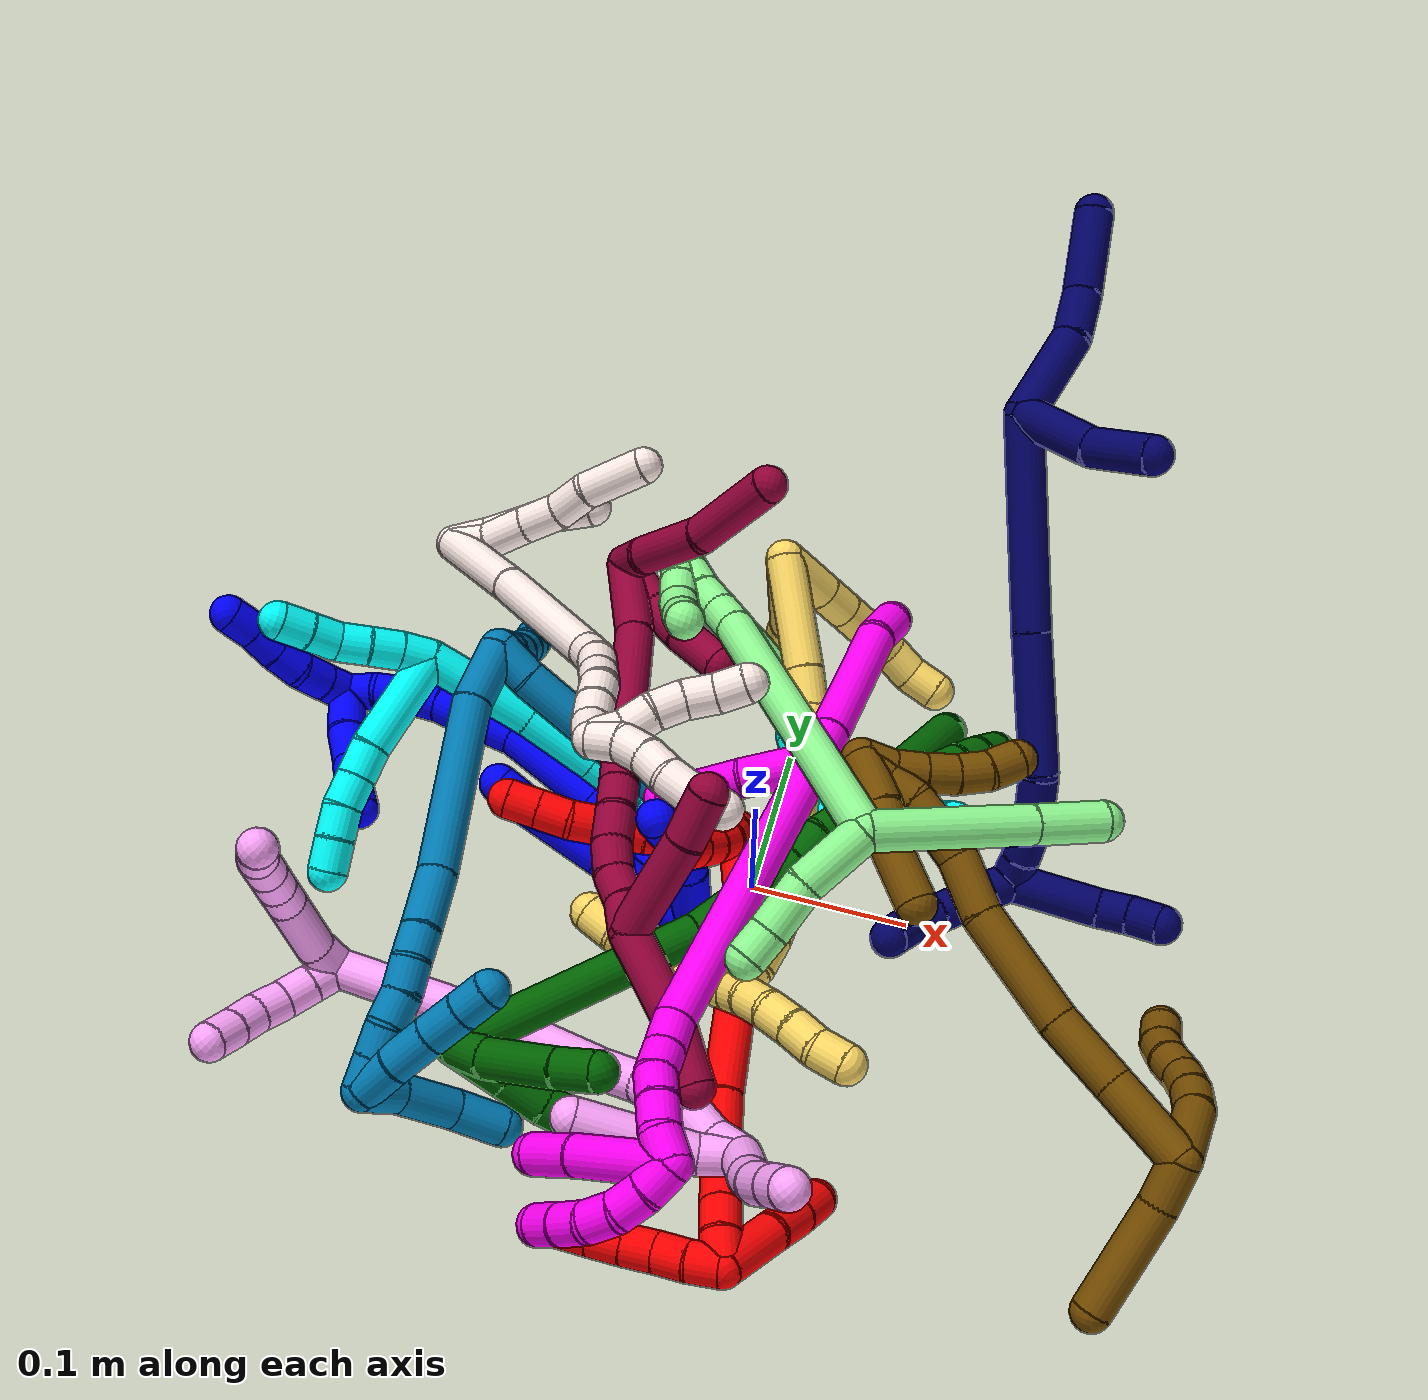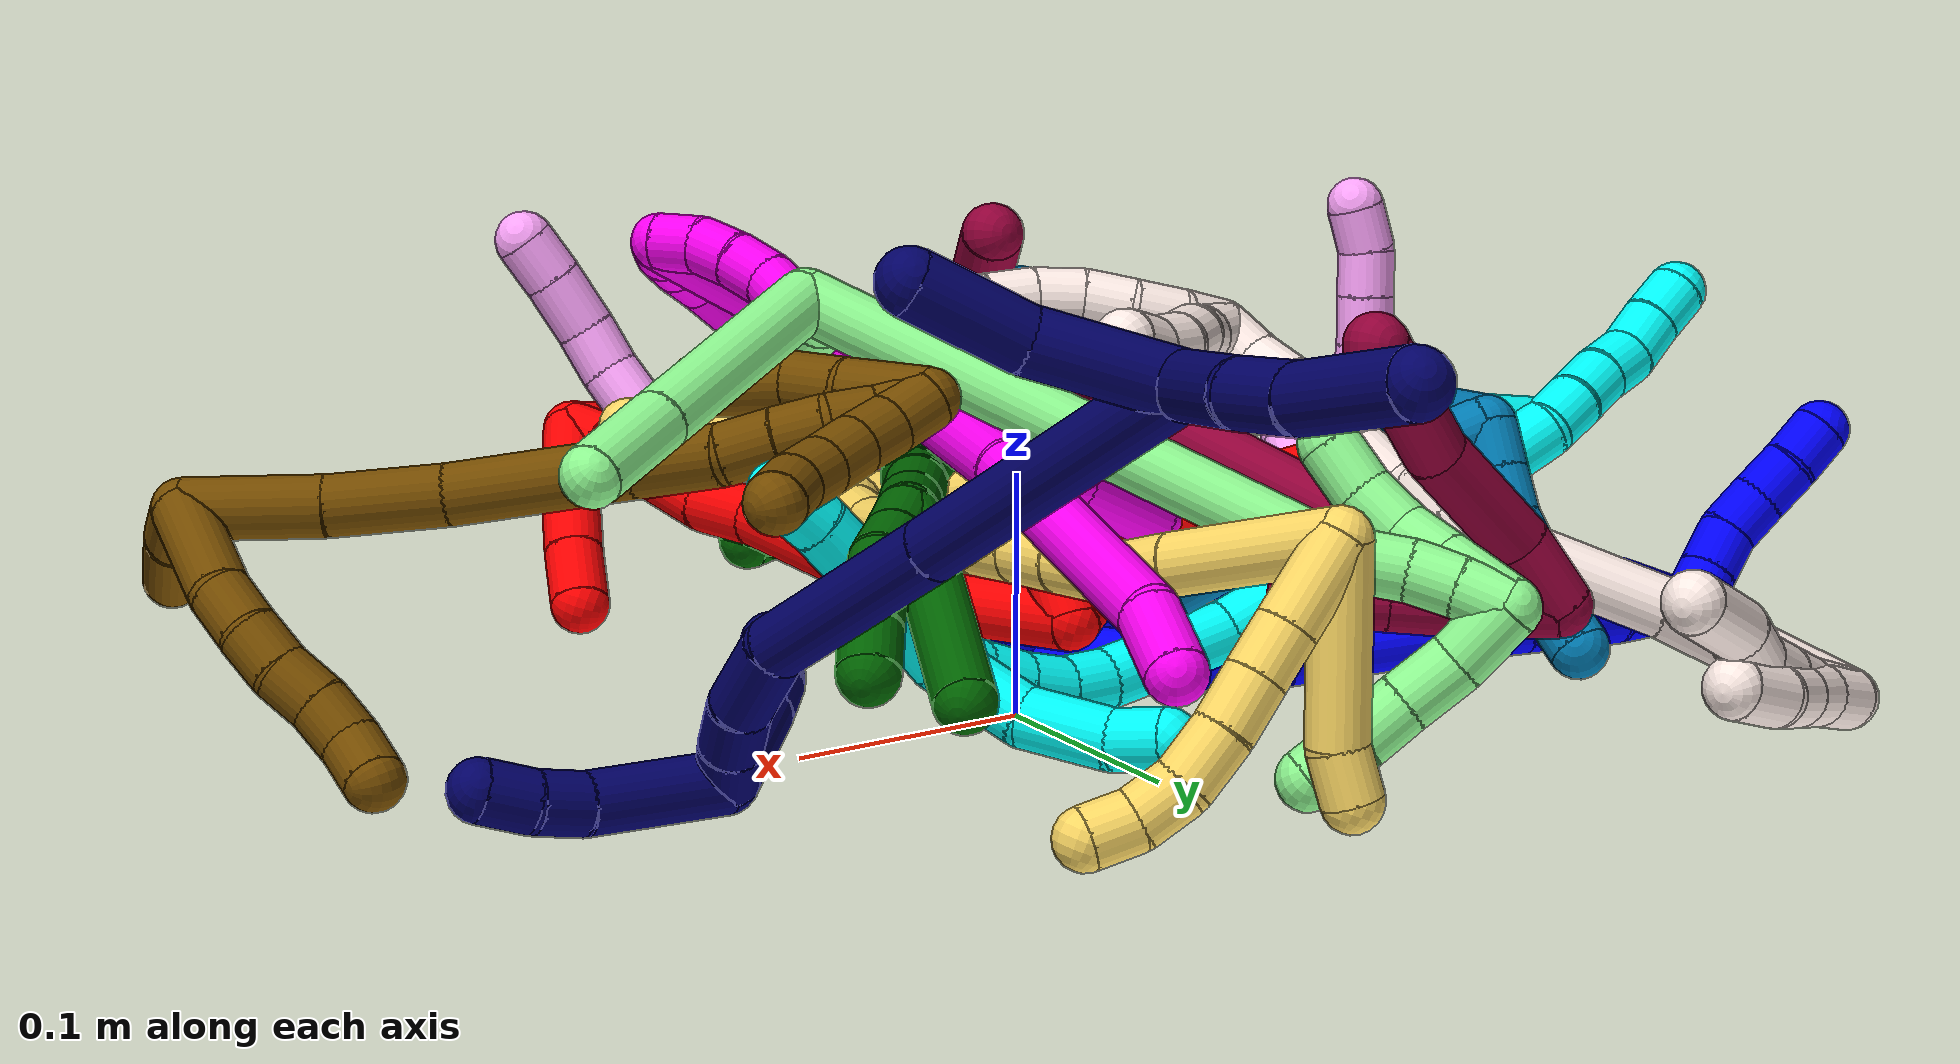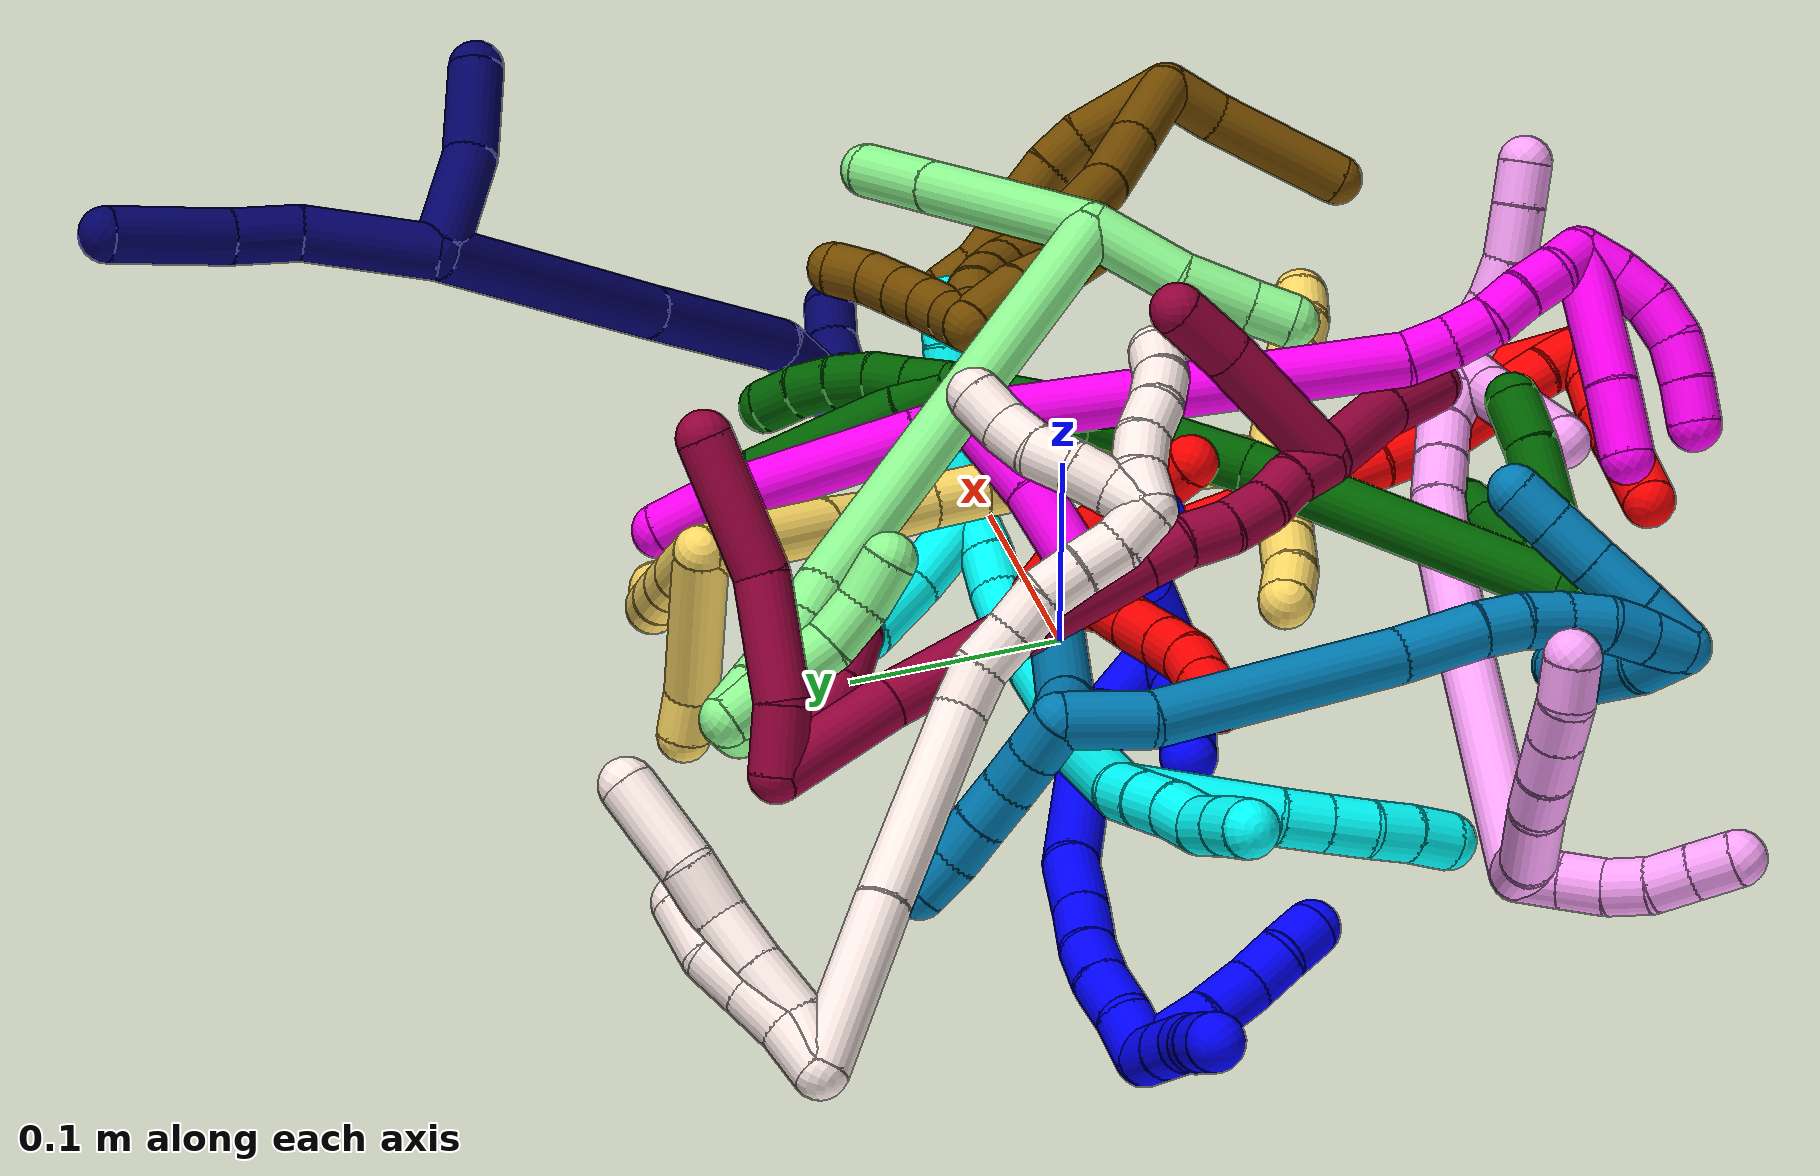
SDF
<sdf version="1.7">
 <world name="default">
  <plugin name="TubeGeneratorPlugin" filename="libtube_generator_plugin.so"/>
  <model name="photoneo_s_sensor">
   <static>1</static>
   <pose>0 0 2 1.57079 1.57079 3.14159</pose>
   <link name="link">
    <inertial><mass>0.1</mass></inertial>
    <sensor name="sensor" type="depth">
     <update_rate>30</update_rate>
     <camera>
      <horizontal_fov>1.22</horizontal_fov>
      <image><width>1920</width><height>1200</height><format>B8G8R8</format></image>
      <clip><near>0.1</near><far>4</far></clip>
      <depth_camera><output>points</output></depth_camera>
     </camera>
     <plugin name="camera_plugin" filename="libgazebo_ros_depth_camera.so">
      <baseline>0.2</baseline>
      <alwaysOn>1</alwaysOn>
      <updateRate>0.0</updateRate>
      <cameraName>camera_ir</cameraName>
      <imageTopicName>/camera/color/image_raw</imageTopicName>
      <cameraInfoTopicName>/camera/color/camera_info</cameraInfoTopicName>
      <depthImageTopicName>/camera/depth/image_raw</depthImageTopicName>
      <depthImageCameraInfoTopicName>/camera/depth/camera_info</depthImageCameraInfoTopicName>
      <pointCloudTopicName>/camera/depth/points</pointCloudTopicName>
      <frameName>fr_optical</frameName>
      <pointCloudCutoff>0.1</pointCloudCutoff>
      <pointCloudCutoffMax>2.0</pointCloudCutoffMax>
      <distortionK1>0</distortionK1>
      <distortionK2>0</distortionK2>
      <distortionK3>0</distortionK3>
      <distortionT1>0</distortionT1>
      <distortionT2>0</distortionT2>
      <CxPrime>0</CxPrime>
      <Cx>0</Cx>
      <Cy>0</Cy>
      <focalLength>0</focalLength>
      <hackBaseline>0</hackBaseline>
     </plugin>
    </sensor>
   </link>
  </model>
  <gravity>0 0 -9.8</gravity>
  <magnetic_field>6e-06 2.3e-05 -4.2e-05</magnetic_field>
  <atmosphere type="adiabatic"/>
  <physics name="default_physics" default="0" type="ode">
   <max_step_size>0.003</max_step_size>
   <real_time_factor>1</real_time_factor>
   <real_time_update_rate>1000</real_time_update_rate>
   <max_contacts>10000</max_contacts>
   <ode>
    <solver>
     <type>quick</type>
     <iters>100</iters>
     <sor>1.3</sor>
     <use_dynamic_moi_rescaling>0</use_dynamic_moi_rescaling>
    </solver>
    <constraints>
     <contact_max_correcting_vel>0</contact_max_correcting_vel>
     <contact_surface_layer>0.001</contact_surface_layer>
     <cfm>0</cfm>
     <erp>0.2</erp>
    </constraints>
   </ode>
  </physics>
  <scene><ambient>0.4 0.4 0.4 1</ambient><background>0.7 0.7 0.7 1</background><shadows>0</shadows></scene>
  <audio><device>default</device></audio>
  <spherical_coordinates>
   <surface_model>EARTH_WGS84</surface_model>
   <latitude_deg>0</latitude_deg>
   <longitude_deg>0</longitude_deg>
   <elevation>0</elevation>
   <heading_deg>0</heading_deg>
  </spherical_coordinates>
  <model name="bin">
   <static>1</static>
   <link name="bottom">
    <collision name="collision-bottom">
     <pose>0 0 -0.01 0 -0 0</pose>
     <geometry><box><size>0.8 0.6 0.02</size></box></geometry>
     <surface>
      <friction><ode><mu>100</mu><mu2>100</mu2></ode></friction>
      <contact><collide_bitmask>65535</collide_bitmask></contact>
     </surface>
    </collision>
   </link>
   <link name="west_wall">
    <collision name="collision-west_wall">
     <pose>-0.41 0 0.1 0 -0 0</pose>
     <geometry><box><size>0.02 0.6 0.2</size></box></geometry>
     <surface>
      <friction><ode><mu>100</mu><mu2>100</mu2></ode></friction>
      <contact><collide_bitmask>65535</collide_bitmask></contact>
     </surface>
    </collision>
   </link>
   <link name="east_wall">
    <collision name="collision-east_wall">
     <pose>0.41 0 0.1 0 -0 0</pose>
     <geometry><box><size>0.02 0.6 0.2</size></box></geometry>
     <surface>
      <friction><ode><mu>100</mu><mu2>100</mu2></ode></friction>
      <contact><collide_bitmask>65535</collide_bitmask></contact>
     </surface>
    </collision>
   </link>
   <link name="south_wall">
    <collision name="collision-south_wall">
     <pose>0 -0.31 0.1 0 -0 0</pose>
     <geometry><box><size>0.8 0.02 0.2</size></box></geometry>
     <surface>
      <friction><ode><mu>100</mu><mu2>100</mu2></ode></friction>
      <contact><collide_bitmask>65535</collide_bitmask></contact>
     </surface>
    </collision>
   </link>
   <link name="north_wall">
    <collision name="collision-north_wall">
     <pose>0 0.31 0.1 0 -0 0</pose>
     <geometry><box><size>0.8 0.02 0.2</size></box></geometry>
     <surface>
      <friction><ode><mu>100</mu><mu2>100</mu2></ode></friction>
      <contact><collide_bitmask>65535</collide_bitmask></contact>
     </surface>
    </collision>
   </link>
  </model>
  <model name="1">
   <static>0</static>
   <link name="1">
    <collision name="collision-cylinder-e_1_2_8">
     <pose>-0.024396 0.003175 0.026386 -0.119738 -0.742656 0.046672</pose>
     <geometry><cylinder><radius>0.0125</radius><length>0.072152</length></cylinder></geometry>
     <surface>
      <friction><ode><mu>1.16</mu><mu2>1.16</mu2><slip1>0</slip1><slip2>0</slip2></ode></friction>
      <contact><ode><kp>1e+06</kp><kd>1</kd><max_vel>0</max_vel><min_depth>0.001</min_depth></ode></contact>
     </surface>
    </collision>
    <visual name="visual-cylinder-e_1_2_8">
     <pose>-0.024396 0.003175 0.026386 -0.119738 -0.742656 0.046672</pose>
     <geometry><cylinder><radius>0.0125</radius><length>0.072152</length></cylinder></geometry>
     <material><ambient>0 0 1 1</ambient></material>
    </visual>
    <collision name="collision-cylinder-e_2_8_9">
     <pose>-0.067334 0.010185 0.072809 -0.189166 -0.737707 0.073307</pose>
     <geometry><cylinder><radius>0.0125</radius><length>0.055134</length></cylinder></geometry>
     <surface>
      <friction><ode><mu>1.16</mu><mu2>1.16</mu2><slip1>0</slip1><slip2>0</slip2></ode></friction>
      <contact><ode><kp>1e+06</kp><kd>1</kd><max_vel>0</max_vel><min_depth>0.001</min_depth></ode></contact>
     </surface>
    </collision>
    <visual name="visual-cylinder-e_2_8_9">
     <pose>-0.067334 0.010185 0.072809 -0.189166 -0.737707 0.073307</pose>
     <geometry><cylinder><radius>0.0125</radius><length>0.055134</length></cylinder></geometry>
     <material><ambient>0 0 1 1</ambient></material>
    </visual>
    <collision name="collision-cylinder-e_3_9_6">
     <pose>-0.093126 0.015028 0.101528 -0.115406 -0.692446 0.041673</pose>
     <geometry><cylinder><radius>0.0125</radius><length>0.022713</length></cylinder></geometry>
     <surface>
      <friction><ode><mu>1.16</mu><mu2>1.16</mu2><slip1>0</slip1><slip2>0</slip2></ode></friction>
      <contact><ode><kp>1e+06</kp><kd>1</kd><max_vel>0</max_vel><min_depth>0.001</min_depth></ode></contact>
     </surface>
    </collision>
    <visual name="visual-cylinder-e_3_9_6">
     <pose>-0.093126 0.015028 0.101528 -0.115406 -0.692446 0.041673</pose>
     <geometry><cylinder><radius>0.0125</radius><length>0.022713</length></cylinder></geometry>
     <material><ambient>0 0 1 1</ambient></material>
    </visual>
    <collision name="collision-cylinder-e_1_2_10">
     <pose>-0.008819 -0.01773 0.009683 1.07089 -0.411627 -0.246453</pose>
     <geometry><cylinder><radius>0.0125</radius><length>0.044086</length></cylinder></geometry>
     <surface>
      <friction><ode><mu>1.16</mu><mu2>1.16</mu2><slip1>0</slip1><slip2>0</slip2></ode></friction>
      <contact><ode><kp>1e+06</kp><kd>1</kd><max_vel>0</max_vel><min_depth>0.001</min_depth></ode></contact>
     </surface>
    </collision>
    <visual name="visual-cylinder-e_1_2_10">
     <pose>-0.008819 -0.01773 0.009683 1.07089 -0.411627 -0.246453</pose>
     <geometry><cylinder><radius>0.0125</radius><length>0.044086</length></cylinder></geometry>
     <material><ambient>0 0 1 1</ambient></material>
    </visual>
    <collision name="collision-cylinder-e_2_10_11">
     <pose>-0.029536 -0.046875 0.025795 1.05798 -0.737251 -0.44416</pose>
     <geometry><cylinder><radius>0.0125</radius><length>0.035394</length></cylinder></geometry>
     <surface>
      <friction><ode><mu>1.16</mu><mu2>1.16</mu2><slip1>0</slip1><slip2>0</slip2></ode></friction>
      <contact><ode><kp>1e+06</kp><kd>1</kd><max_vel>0</max_vel><min_depth>0.001</min_depth></ode></contact>
     </surface>
    </collision>
    <visual name="visual-cylinder-e_2_10_11">
     <pose>-0.029536 -0.046875 0.025795 1.05798 -0.737251 -0.44416</pose>
     <geometry><cylinder><radius>0.0125</radius><length>0.035394</length></cylinder></geometry>
     <material><ambient>0 0 1 1</ambient></material>
    </visual>
    <collision name="collision-cylinder-e_3_11_5">
     <pose>-0.049597 -0.064209 0.034118 1.26096 -0.920299 -0.694192</pose>
     <geometry><cylinder><radius>0.0125</radius><length>0.02052</length></cylinder></geometry>
     <surface>
      <friction><ode><mu>1.16</mu><mu2>1.16</mu2><slip1>0</slip1><slip2>0</slip2></ode></friction>
      <contact><ode><kp>1e+06</kp><kd>1</kd><max_vel>0</max_vel><min_depth>0.001</min_depth></ode></contact>
     </surface>
    </collision>
    <visual name="visual-cylinder-e_3_11_5">
     <pose>-0.049597 -0.064209 0.034118 1.26096 -0.920299 -0.694192</pose>
     <geometry><cylinder><radius>0.0125</radius><length>0.02052</length></cylinder></geometry>
     <material><ambient>0 0 1 1</ambient></material>
    </visual>
    <collision name="collision-cylinder-e_1_2_12">
     <pose>-0.003685 0.005339 0.028981 -0.182168 -0.124415 0.011378</pose>
     <geometry><cylinder><radius>0.0125</radius><length>0.059396</length></cylinder></geometry>
     <surface>
      <friction><ode><mu>1.16</mu><mu2>1.16</mu2><slip1>0</slip1><slip2>0</slip2></ode></friction>
      <contact><ode><kp>1e+06</kp><kd>1</kd><max_vel>0</max_vel><min_depth>0.001</min_depth></ode></contact>
     </surface>
    </collision>
    <visual name="visual-cylinder-e_1_2_12">
     <pose>-0.003685 0.005339 0.028981 -0.182168 -0.124415 0.011378</pose>
     <geometry><cylinder><radius>0.0125</radius><length>0.059396</length></cylinder></geometry>
     <material><ambient>0 0 1 1</ambient></material>
    </visual>
    <collision name="collision-cylinder-e_2_12_13">
     <pose>-0.016913 0.017133 0.080879 -0.274593 -0.381193 0.053302</pose>
     <geometry><cylinder><radius>0.0125</radius><length>0.051301</length></cylinder></geometry>
     <surface>
      <friction><ode><mu>1.16</mu><mu2>1.16</mu2><slip1>0</slip1><slip2>0</slip2></ode></friction>
      <contact><ode><kp>1e+06</kp><kd>1</kd><max_vel>0</max_vel><min_depth>0.001</min_depth></ode></contact>
     </surface>
    </collision>
    <visual name="visual-cylinder-e_2_12_13">
     <pose>-0.016913 0.017133 0.080879 -0.274593 -0.381193 0.053302</pose>
     <geometry><cylinder><radius>0.0125</radius><length>0.051301</length></cylinder></geometry>
     <material><ambient>0 0 1 1</ambient></material>
    </visual>
    <collision name="collision-cylinder-e_3_13_14">
     <pose>-0.043839 0.032245 0.132289 -0.294946 -0.528388 0.080328</pose>
     <geometry><cylinder><radius>0.0125</radius><length>0.068961</length></cylinder></geometry>
     <surface>
      <friction><ode><mu>1.16</mu><mu2>1.16</mu2><slip1>0</slip1><slip2>0</slip2></ode></friction>
      <contact><ode><kp>1e+06</kp><kd>1</kd><max_vel>0</max_vel><min_depth>0.001</min_depth></ode></contact>
     </surface>
    </collision>
    <visual name="visual-cylinder-e_3_13_14">
     <pose>-0.043839 0.032245 0.132289 -0.294946 -0.528388 0.080328</pose>
     <geometry><cylinder><radius>0.0125</radius><length>0.068961</length></cylinder></geometry>
     <material><ambient>0 0 1 1</ambient></material>
    </visual>
    <collision name="collision-cylinder-e_4_14_15">
     <pose>-0.070843 0.04793 0.171609 -0.57572 -0.64049 0.195771</pose>
     <geometry><cylinder><radius>0.0125</radius><length>0.032199</length></cylinder></geometry>
     <surface>
      <friction><ode><mu>1.16</mu><mu2>1.16</mu2><slip1>0</slip1><slip2>0</slip2></ode></friction>
      <contact><ode><kp>1e+06</kp><kd>1</kd><max_vel>0</max_vel><min_depth>0.001</min_depth></ode></contact>
     </surface>
    </collision>
    <visual name="visual-cylinder-e_4_14_15">
     <pose>-0.070843 0.04793 0.171609 -0.57572 -0.64049 0.195771</pose>
     <geometry><cylinder><radius>0.0125</radius><length>0.032199</length></cylinder></geometry>
     <material><ambient>0 0 1 1</ambient></material>
    </visual>
    <collision name="collision-cylinder-e_5_15_16">
     <pose>-0.087362 0.059731 0.190714 -0.52311 -0.625287 0.172627</pose>
     <geometry><cylinder><radius>0.0125</radius><length>0.02357</length></cylinder></geometry>
     <surface>
      <friction><ode><mu>1.16</mu><mu2>1.16</mu2><slip1>0</slip1><slip2>0</slip2></ode></friction>
      <contact><ode><kp>1e+06</kp><kd>1</kd><max_vel>0</max_vel><min_depth>0.001</min_depth></ode></contact>
     </surface>
    </collision>
    <visual name="visual-cylinder-e_5_15_16">
     <pose>-0.087362 0.059731 0.190714 -0.52311 -0.625287 0.172627</pose>
     <geometry><cylinder><radius>0.0125</radius><length>0.02357</length></cylinder></geometry>
     <material><ambient>0 0 1 1</ambient></material>
    </visual>
    <collision name="collision-cylinder-e_6_16_17">
     <pose>-0.100804 0.069718 0.204714 -0.738882 -0.701756 0.281588</pose>
     <geometry><cylinder><radius>0.0125</radius><length>0.020273</length></cylinder></geometry>
     <surface>
      <friction><ode><mu>1.16</mu><mu2>1.16</mu2><slip1>0</slip1><slip2>0</slip2></ode></friction>
      <contact><ode><kp>1e+06</kp><kd>1</kd><max_vel>0</max_vel><min_depth>0.001</min_depth></ode></contact>
     </surface>
    </collision>
    <visual name="visual-cylinder-e_6_16_17">
     <pose>-0.100804 0.069718 0.204714 -0.738882 -0.701756 0.281588</pose>
     <geometry><cylinder><radius>0.0125</radius><length>0.020273</length></cylinder></geometry>
     <material><ambient>0 0 1 1</ambient></material>
    </visual>
    <collision name="collision-cylinder-e_7_17_18">
     <pose>-0.115697 0.080852 0.215418 -0.871265 -0.823404 0.401026</pose>
     <geometry><cylinder><radius>0.0125</radius><length>0.022765</length></cylinder></geometry>
     <surface>
      <friction><ode><mu>1.16</mu><mu2>1.16</mu2><slip1>0</slip1><slip2>0</slip2></ode></friction>
      <contact><ode><kp>1e+06</kp><kd>1</kd><max_vel>0</max_vel><min_depth>0.001</min_depth></ode></contact>
     </surface>
    </collision>
    <visual name="visual-cylinder-e_7_17_18">
     <pose>-0.115697 0.080852 0.215418 -0.871265 -0.823404 0.401026</pose>
     <geometry><cylinder><radius>0.0125</radius><length>0.022765</length></cylinder></geometry>
     <material><ambient>0 0 1 1</ambient></material>
    </visual>
    <collision name="collision-cylinder-e_8_18_1">
     <pose>-0.130206 0.094566 0.22455 -1.08148 -0.60911 0.373087</pose>
     <geometry><cylinder><radius>0.0125</radius><length>0.021534</length></cylinder></geometry>
     <surface>
      <friction><ode><mu>1.16</mu><mu2>1.16</mu2><slip1>0</slip1><slip2>0</slip2></ode></friction>
      <contact><ode><kp>1e+06</kp><kd>1</kd><max_vel>0</max_vel><min_depth>0.001</min_depth></ode></contact>
     </surface>
    </collision>
    <visual name="visual-cylinder-e_8_18_1">
     <pose>-0.130206 0.094566 0.22455 -1.08148 -0.60911 0.373087</pose>
     <geometry><cylinder><radius>0.0125</radius><length>0.021534</length></cylinder></geometry>
     <material><ambient>0 0 1 1</ambient></material>
    </visual>
    <collision name="collision-cylinder-e_1_1_19">
     <pose>-0.145777 0.099891 0.231011 0.818863 -1.22588 -0.592447</pose>
     <geometry><cylinder><radius>0.0125</radius><length>0.02</length></cylinder></geometry>
     <surface>
      <friction><ode><mu>1.16</mu><mu2>1.16</mu2><slip1>0</slip1><slip2>0</slip2></ode></friction>
      <contact><ode><kp>1e+06</kp><kd>1</kd><max_vel>0</max_vel><min_depth>0.001</min_depth></ode></contact>
     </surface>
    </collision>
    <visual name="visual-cylinder-e_1_1_19">
     <pose>-0.145777 0.099891 0.231011 0.818863 -1.22588 -0.592447</pose>
     <geometry><cylinder><radius>0.0125</radius><length>0.02</length></cylinder></geometry>
     <material><ambient>0 0 1 1</ambient></material>
    </visual>
    <collision name="collision-cylinder-e_2_19_20">
     <pose>-0.164512 0.094875 0.235883 0.782239 -1.20111 -0.550556</pose>
     <geometry><cylinder><radius>0.0125</radius><length>0.02</length></cylinder></geometry>
     <surface>
      <friction><ode><mu>1.16</mu><mu2>1.16</mu2><slip1>0</slip1><slip2>0</slip2></ode></friction>
      <contact><ode><kp>1e+06</kp><kd>1</kd><max_vel>0</max_vel><min_depth>0.001</min_depth></ode></contact>
     </surface>
    </collision>
    <visual name="visual-cylinder-e_2_19_20">
     <pose>-0.164512 0.094875 0.235883 0.782239 -1.20111 -0.550556</pose>
     <geometry><cylinder><radius>0.0125</radius><length>0.02</length></cylinder></geometry>
     <material><ambient>0 0 1 1</ambient></material>
    </visual>
    <collision name="collision-cylinder-e_3_20_21">
     <pose>-0.182176 0.09022 0.243546 0.391886 -0.9862 -0.212524</pose>
     <geometry><cylinder><radius>0.0125</radius><length>0.02</length></cylinder></geometry>
     <surface>
      <friction><ode><mu>1.16</mu><mu2>1.16</mu2><slip1>0</slip1><slip2>0</slip2></ode></friction>
      <contact><ode><kp>1e+06</kp><kd>1</kd><max_vel>0</max_vel><min_depth>0.001</min_depth></ode></contact>
     </surface>
    </collision>
    <visual name="visual-cylinder-e_3_20_21">
     <pose>-0.182176 0.09022 0.243546 0.391886 -0.9862 -0.212524</pose>
     <geometry><cylinder><radius>0.0125</radius><length>0.02</length></cylinder></geometry>
     <material><ambient>0 0 1 1</ambient></material>
    </visual>
    <collision name="collision-cylinder-e_4_21_22">
     <pose>-0.198261 0.085343 0.254332 0.453302 -0.886077 -0.217984</pose>
     <geometry><cylinder><radius>0.0125</radius><length>0.02</length></cylinder></geometry>
     <surface>
      <friction><ode><mu>1.16</mu><mu2>1.16</mu2><slip1>0</slip1><slip2>0</slip2></ode></friction>
      <contact><ode><kp>1e+06</kp><kd>1</kd><max_vel>0</max_vel><min_depth>0.001</min_depth></ode></contact>
     </surface>
    </collision>
    <visual name="visual-cylinder-e_4_21_22">
     <pose>-0.198261 0.085343 0.254332 0.453302 -0.886077 -0.217984</pose>
     <geometry><cylinder><radius>0.0125</radius><length>0.02</length></cylinder></geometry>
     <material><ambient>0 0 1 1</ambient></material>
    </visual>
    <collision name="collision-cylinder-e_5_22_4">
     <pose>-0.214605 0.080499 0.264685 0.418156 -1.03479 -0.240342</pose>
     <geometry><cylinder><radius>0.0125</radius><length>0.02</length></cylinder></geometry>
     <surface>
      <friction><ode><mu>1.16</mu><mu2>1.16</mu2><slip1>0</slip1><slip2>0</slip2></ode></friction>
      <contact><ode><kp>1e+06</kp><kd>1</kd><max_vel>0</max_vel><min_depth>0.001</min_depth></ode></contact>
     </surface>
    </collision>
    <visual name="visual-cylinder-e_5_22_4">
     <pose>-0.214605 0.080499 0.264685 0.418156 -1.03479 -0.240342</pose>
     <geometry><cylinder><radius>0.0125</radius><length>0.02</length></cylinder></geometry>
     <material><ambient>0 0 1 1</ambient></material>
    </visual>
    <collision name="collision-cylinder-e_1_1_23">
     <pose>-0.141452 0.101092 0.212636 3.06279 -0.305726 -2.6406</pose>
     <geometry><cylinder><radius>0.0125</radius><length>0.033798</length></cylinder></geometry>
     <surface>
      <friction><ode><mu>1.16</mu><mu2>1.16</mu2><slip1>0</slip1><slip2>0</slip2></ode></friction>
      <contact><ode><kp>1e+06</kp><kd>1</kd><max_vel>0</max_vel><min_depth>0.001</min_depth></ode></contact>
     </surface>
    </collision>
    <visual name="visual-cylinder-e_1_1_23">
     <pose>-0.141452 0.101092 0.212636 3.06279 -0.305726 -2.6406</pose>
     <geometry><cylinder><radius>0.0125</radius><length>0.033798</length></cylinder></geometry>
     <material><ambient>0 0 1 1</ambient></material>
    </visual>
    <collision name="collision-cylinder-e_2_23_24">
     <pose>-0.148239 0.09869 0.183656 3.05401 -0.130424 -1.95958</pose>
     <geometry><cylinder><radius>0.0125</radius><length>0.02615</length></cylinder></geometry>
     <surface>
      <friction><ode><mu>1.16</mu><mu2>1.16</mu2><slip1>0</slip1><slip2>0</slip2></ode></friction>
      <contact><ode><kp>1e+06</kp><kd>1</kd><max_vel>0</max_vel><min_depth>0.001</min_depth></ode></contact>
     </surface>
    </collision>
    <visual name="visual-cylinder-e_2_23_24">
     <pose>-0.148239 0.09869 0.183656 3.05401 -0.130424 -1.95958</pose>
     <geometry><cylinder><radius>0.0125</radius><length>0.02615</length></cylinder></geometry>
     <material><ambient>0 0 1 1</ambient></material>
    </visual>
    <collision name="collision-cylinder-e_3_24_25">
     <pose>-0.153203 0.0949 0.161654 2.85733 -0.331954 -1.72774</pose>
     <geometry><cylinder><radius>0.0125</radius><length>0.020031</length></cylinder></geometry>
     <surface>
      <friction><ode><mu>1.16</mu><mu2>1.16</mu2><slip1>0</slip1><slip2>0</slip2></ode></friction>
      <contact><ode><kp>1e+06</kp><kd>1</kd><max_vel>0</max_vel><min_depth>0.001</min_depth></ode></contact>
     </surface>
    </collision>
    <visual name="visual-cylinder-e_3_24_25">
     <pose>-0.153203 0.0949 0.161654 2.85733 -0.331954 -1.72774</pose>
     <geometry><cylinder><radius>0.0125</radius><length>0.020031</length></cylinder></geometry>
     <material><ambient>0 0 1 1</ambient></material>
    </visual>
    <collision name="collision-cylinder-e_4_25_3">
     <pose>-0.157401 0.091039 0.142671 3.02036 -0.093459 -1.31302</pose>
     <geometry><cylinder><radius>0.0125</radius><length>0.020022</length></cylinder></geometry>
     <surface>
      <friction><ode><mu>1.16</mu><mu2>1.16</mu2><slip1>0</slip1><slip2>0</slip2></ode></friction>
      <contact><ode><kp>1e+06</kp><kd>1</kd><max_vel>0</max_vel><min_depth>0.001</min_depth></ode></contact>
     </surface>
    </collision>
    <visual name="visual-cylinder-e_4_25_3">
     <pose>-0.157401 0.091039 0.142671 3.02036 -0.093459 -1.31302</pose>
     <geometry><cylinder><radius>0.0125</radius><length>0.020022</length></cylinder></geometry>
     <material><ambient>0 0 1 1</ambient></material>
    </visual>
    <collision name="collision-sphere-3">
     <pose>-0.158336 0.089834 0.132777 0 -0 0</pose>
     <geometry><sphere><radius>0.0125</radius></sphere></geometry>
     <surface>
      <friction><ode><mu>1.16</mu><mu2>1.16</mu2><slip1>0</slip1><slip2>0</slip2></ode></friction>
      <contact><ode><kp>1e+06</kp><kd>1</kd><max_vel>0</max_vel><min_depth>0.001</min_depth></ode></contact>
     </surface>
    </collision>
    <visual name="visual-sphere-3">
     <pose>-0.158336 0.089834 0.132777 0 -0 0</pose>
     <geometry><sphere><radius>0.0125</radius></sphere></geometry>
     <material><ambient>0 0 1 1</ambient></material>
    </visual>
    <collision name="collision-sphere-25">
     <pose>-0.156467 0.092245 0.152565 0 -0 0</pose>
     <geometry><sphere><radius>0.0125</radius></sphere></geometry>
     <surface>
      <friction><ode><mu>1.16</mu><mu2>1.16</mu2><slip1>0</slip1><slip2>0</slip2></ode></friction>
      <contact><ode><kp>1e+06</kp><kd>1</kd><max_vel>0</max_vel><min_depth>0.001</min_depth></ode></contact>
     </surface>
    </collision>
    <visual name="visual-sphere-25">
     <pose>-0.156467 0.092245 0.152565 0 -0 0</pose>
     <geometry><sphere><radius>0.0125</radius></sphere></geometry>
     <material><ambient>0 0 1 1</ambient></material>
    </visual>
    <collision name="collision-sphere-24">
     <pose>-0.149939 0.097556 0.170742 0 -0 0</pose>
     <geometry><sphere><radius>0.0125</radius></sphere></geometry>
     <surface>
      <friction><ode><mu>1.16</mu><mu2>1.16</mu2><slip1>0</slip1><slip2>0</slip2></ode></friction>
      <contact><ode><kp>1e+06</kp><kd>1</kd><max_vel>0</max_vel><min_depth>0.001</min_depth></ode></contact>
     </surface>
    </collision>
    <visual name="visual-sphere-24">
     <pose>-0.149939 0.097556 0.170742 0 -0 0</pose>
     <geometry><sphere><radius>0.0125</radius></sphere></geometry>
     <material><ambient>0 0 1 1</ambient></material>
    </visual>
    <collision name="collision-sphere-23">
     <pose>-0.146538 0.099824 0.196571 0 -0 0</pose>
     <geometry><sphere><radius>0.0125</radius></sphere></geometry>
     <surface>
      <friction><ode><mu>1.16</mu><mu2>1.16</mu2><slip1>0</slip1><slip2>0</slip2></ode></friction>
      <contact><ode><kp>1e+06</kp><kd>1</kd><max_vel>0</max_vel><min_depth>0.001</min_depth></ode></contact>
     </surface>
    </collision>
    <visual name="visual-sphere-23">
     <pose>-0.146538 0.099824 0.196571 0 -0 0</pose>
     <geometry><sphere><radius>0.0125</radius></sphere></geometry>
     <material><ambient>0 0 1 1</ambient></material>
    </visual>
    <collision name="collision-sphere-4">
     <pose>-0.223203 0.078425 0.269352 0 -0 0</pose>
     <geometry><sphere><radius>0.0125</radius></sphere></geometry>
     <surface>
      <friction><ode><mu>1.16</mu><mu2>1.16</mu2><slip1>0</slip1><slip2>0</slip2></ode></friction>
      <contact><ode><kp>1e+06</kp><kd>1</kd><max_vel>0</max_vel><min_depth>0.001</min_depth></ode></contact>
     </surface>
    </collision>
    <visual name="visual-sphere-4">
     <pose>-0.223203 0.078425 0.269352 0 -0 0</pose>
     <geometry><sphere><radius>0.0125</radius></sphere></geometry>
     <material><ambient>0 0 1 1</ambient></material>
    </visual>
    <collision name="collision-sphere-22">
     <pose>-0.206007 0.082573 0.260018 0 -0 0</pose>
     <geometry><sphere><radius>0.0125</radius></sphere></geometry>
     <surface>
      <friction><ode><mu>1.16</mu><mu2>1.16</mu2><slip1>0</slip1><slip2>0</slip2></ode></friction>
      <contact><ode><kp>1e+06</kp><kd>1</kd><max_vel>0</max_vel><min_depth>0.001</min_depth></ode></contact>
     </surface>
    </collision>
    <visual name="visual-sphere-22">
     <pose>-0.206007 0.082573 0.260018 0 -0 0</pose>
     <geometry><sphere><radius>0.0125</radius></sphere></geometry>
     <material><ambient>0 0 1 1</ambient></material>
    </visual>
    <collision name="collision-sphere-21">
     <pose>-0.190515 0.088113 0.248647 0 -0 0</pose>
     <geometry><sphere><radius>0.0125</radius></sphere></geometry>
     <surface>
      <friction><ode><mu>1.16</mu><mu2>1.16</mu2><slip1>0</slip1><slip2>0</slip2></ode></friction>
      <contact><ode><kp>1e+06</kp><kd>1</kd><max_vel>0</max_vel><min_depth>0.001</min_depth></ode></contact>
     </surface>
    </collision>
    <visual name="visual-sphere-21">
     <pose>-0.190515 0.088113 0.248647 0 -0 0</pose>
     <geometry><sphere><radius>0.0125</radius></sphere></geometry>
     <material><ambient>0 0 1 1</ambient></material>
    </visual>
    <collision name="collision-sphere-20">
     <pose>-0.173837 0.092328 0.238446 0 -0 0</pose>
     <geometry><sphere><radius>0.0125</radius></sphere></geometry>
     <surface>
      <friction><ode><mu>1.16</mu><mu2>1.16</mu2><slip1>0</slip1><slip2>0</slip2></ode></friction>
      <contact><ode><kp>1e+06</kp><kd>1</kd><max_vel>0</max_vel><min_depth>0.001</min_depth></ode></contact>
     </surface>
    </collision>
    <visual name="visual-sphere-20">
     <pose>-0.173837 0.092328 0.238446 0 -0 0</pose>
     <geometry><sphere><radius>0.0125</radius></sphere></geometry>
     <material><ambient>0 0 1 1</ambient></material>
    </visual>
    <collision name="collision-sphere-11">
     <pose>-0.041433 -0.058292 0.032223 0 -0 0</pose>
     <geometry><sphere><radius>0.0125</radius></sphere></geometry>
     <surface>
      <friction><ode><mu>1.16</mu><mu2>1.16</mu2><slip1>0</slip1><slip2>0</slip2></ode></friction>
      <contact><ode><kp>1e+06</kp><kd>1</kd><max_vel>0</max_vel><min_depth>0.001</min_depth></ode></contact>
     </surface>
    </collision>
    <visual name="visual-sphere-11">
     <pose>-0.041433 -0.058292 0.032223 0 -0 0</pose>
     <geometry><sphere><radius>0.0125</radius></sphere></geometry>
     <material><ambient>0 0 1 1</ambient></material>
    </visual>
    <collision name="collision-sphere-10">
     <pose>-0.017639 -0.035459 0.019367 0 -0 0</pose>
     <geometry><sphere><radius>0.0125</radius></sphere></geometry>
     <surface>
      <friction><ode><mu>1.16</mu><mu2>1.16</mu2><slip1>0</slip1><slip2>0</slip2></ode></friction>
      <contact><ode><kp>1e+06</kp><kd>1</kd><max_vel>0</max_vel><min_depth>0.001</min_depth></ode></contact>
     </surface>
    </collision>
    <visual name="visual-sphere-10">
     <pose>-0.017639 -0.035459 0.019367 0 -0 0</pose>
     <geometry><sphere><radius>0.0125</radius></sphere></geometry>
     <material><ambient>0 0 1 1</ambient></material>
    </visual>
    <collision name="collision-sphere-6">
     <pose>-0.100376 0.016034 0.11021 0 -0 0</pose>
     <geometry><sphere><radius>0.0125</radius></sphere></geometry>
     <surface>
      <friction><ode><mu>1.16</mu><mu2>1.16</mu2><slip1>0</slip1><slip2>0</slip2></ode></friction>
      <contact><ode><kp>1e+06</kp><kd>1</kd><max_vel>0</max_vel><min_depth>0.001</min_depth></ode></contact>
     </surface>
    </collision>
    <visual name="visual-sphere-6">
     <pose>-0.100376 0.016034 0.11021 0 -0 0</pose>
     <geometry><sphere><radius>0.0125</radius></sphere></geometry>
     <material><ambient>0 0 1 1</ambient></material>
    </visual>
    <collision name="collision-sphere-9">
     <pose>-0.085876 0.014021 0.092845 0 -0 0</pose>
     <geometry><sphere><radius>0.0125</radius></sphere></geometry>
     <surface>
      <friction><ode><mu>1.16</mu><mu2>1.16</mu2><slip1>0</slip1><slip2>0</slip2></ode></friction>
      <contact><ode><kp>1e+06</kp><kd>1</kd><max_vel>0</max_vel><min_depth>0.001</min_depth></ode></contact>
     </surface>
    </collision>
    <visual name="visual-sphere-9">
     <pose>-0.085876 0.014021 0.092845 0 -0 0</pose>
     <geometry><sphere><radius>0.0125</radius></sphere></geometry>
     <material><ambient>0 0 1 1</ambient></material>
    </visual>
    <collision name="collision-sphere-2">
     <geometry><sphere><radius>0.0125</radius></sphere></geometry>
     <surface>
      <friction><ode><mu>1.16</mu><mu2>1.16</mu2><slip1>0</slip1><slip2>0</slip2></ode></friction>
      <contact><ode><kp>1e+06</kp><kd>1</kd><max_vel>0</max_vel><min_depth>0.001</min_depth></ode></contact>
     </surface>
    </collision>
    <visual name="visual-sphere-2">
     <geometry><sphere><radius>0.0125</radius></sphere></geometry>
     <material><ambient>0 0 1 1</ambient></material>
    </visual>
    <collision name="collision-sphere-19">
     <pose>-0.155188 0.097422 0.23332 0 -0 0</pose>
     <geometry><sphere><radius>0.0125</radius></sphere></geometry>
     <surface>
      <friction><ode><mu>1.16</mu><mu2>1.16</mu2><slip1>0</slip1><slip2>0</slip2></ode></friction>
      <contact><ode><kp>1e+06</kp><kd>1</kd><max_vel>0</max_vel><min_depth>0.001</min_depth></ode></contact>
     </surface>
    </collision>
    <visual name="visual-sphere-19">
     <pose>-0.155188 0.097422 0.23332 0 -0 0</pose>
     <geometry><sphere><radius>0.0125</radius></sphere></geometry>
     <material><ambient>0 0 1 1</ambient></material>
    </visual>
    <collision name="collision-sphere-8">
     <pose>-0.048793 0.006349 0.052772 0 -0 0</pose>
     <geometry><sphere><radius>0.0125</radius></sphere></geometry>
     <surface>
      <friction><ode><mu>1.16</mu><mu2>1.16</mu2><slip1>0</slip1><slip2>0</slip2></ode></friction>
      <contact><ode><kp>1e+06</kp><kd>1</kd><max_vel>0</max_vel><min_depth>0.001</min_depth></ode></contact>
     </surface>
    </collision>
    <visual name="visual-sphere-8">
     <pose>-0.048793 0.006349 0.052772 0 -0 0</pose>
     <geometry><sphere><radius>0.0125</radius></sphere></geometry>
     <material><ambient>0 0 1 1</ambient></material>
    </visual>
    <collision name="collision-sphere-5">
     <pose>-0.057762 -0.070126 0.036012 0 -0 0</pose>
     <geometry><sphere><radius>0.0125</radius></sphere></geometry>
     <surface>
      <friction><ode><mu>1.16</mu><mu2>1.16</mu2><slip1>0</slip1><slip2>0</slip2></ode></friction>
      <contact><ode><kp>1e+06</kp><kd>1</kd><max_vel>0</max_vel><min_depth>0.001</min_depth></ode></contact>
     </surface>
    </collision>
    <visual name="visual-sphere-5">
     <pose>-0.057762 -0.070126 0.036012 0 -0 0</pose>
     <geometry><sphere><radius>0.0125</radius></sphere></geometry>
     <material><ambient>0 0 1 1</ambient></material>
    </visual>
    <collision name="collision-sphere-12">
     <pose>-0.007371 0.010677 0.057962 0 -0 0</pose>
     <geometry><sphere><radius>0.0125</radius></sphere></geometry>
     <surface>
      <friction><ode><mu>1.16</mu><mu2>1.16</mu2><slip1>0</slip1><slip2>0</slip2></ode></friction>
      <contact><ode><kp>1e+06</kp><kd>1</kd><max_vel>0</max_vel><min_depth>0.001</min_depth></ode></contact>
     </surface>
    </collision>
    <visual name="visual-sphere-12">
     <pose>-0.007371 0.010677 0.057962 0 -0 0</pose>
     <geometry><sphere><radius>0.0125</radius></sphere></geometry>
     <material><ambient>0 0 1 1</ambient></material>
    </visual>
    <collision name="collision-sphere-13">
     <pose>-0.026456 0.023589 0.103797 0 -0 0</pose>
     <geometry><sphere><radius>0.0125</radius></sphere></geometry>
     <surface>
      <friction><ode><mu>1.16</mu><mu2>1.16</mu2><slip1>0</slip1><slip2>0</slip2></ode></friction>
      <contact><ode><kp>1e+06</kp><kd>1</kd><max_vel>0</max_vel><min_depth>0.001</min_depth></ode></contact>
     </surface>
    </collision>
    <visual name="visual-sphere-13">
     <pose>-0.026456 0.023589 0.103797 0 -0 0</pose>
     <geometry><sphere><radius>0.0125</radius></sphere></geometry>
     <material><ambient>0 0 1 1</ambient></material>
    </visual>
    <collision name="collision-sphere-14">
     <pose>-0.061222 0.040902 0.160781 0 -0 0</pose>
     <geometry><sphere><radius>0.0125</radius></sphere></geometry>
     <surface>
      <friction><ode><mu>1.16</mu><mu2>1.16</mu2><slip1>0</slip1><slip2>0</slip2></ode></friction>
      <contact><ode><kp>1e+06</kp><kd>1</kd><max_vel>0</max_vel><min_depth>0.001</min_depth></ode></contact>
     </surface>
    </collision>
    <visual name="visual-sphere-14">
     <pose>-0.061222 0.040902 0.160781 0 -0 0</pose>
     <geometry><sphere><radius>0.0125</radius></sphere></geometry>
     <material><ambient>0 0 1 1</ambient></material>
    </visual>
    <collision name="collision-sphere-15">
     <pose>-0.080464 0.054958 0.182437 0 -0 0</pose>
     <geometry><sphere><radius>0.0125</radius></sphere></geometry>
     <surface>
      <friction><ode><mu>1.16</mu><mu2>1.16</mu2><slip1>0</slip1><slip2>0</slip2></ode></friction>
      <contact><ode><kp>1e+06</kp><kd>1</kd><max_vel>0</max_vel><min_depth>0.001</min_depth></ode></contact>
     </surface>
    </collision>
    <visual name="visual-sphere-15">
     <pose>-0.080464 0.054958 0.182437 0 -0 0</pose>
     <geometry><sphere><radius>0.0125</radius></sphere></geometry>
     <material><ambient>0 0 1 1</ambient></material>
    </visual>
    <collision name="collision-sphere-16">
     <pose>-0.09426 0.064505 0.198991 0 -0 0</pose>
     <geometry><sphere><radius>0.0125</radius></sphere></geometry>
     <surface>
      <friction><ode><mu>1.16</mu><mu2>1.16</mu2><slip1>0</slip1><slip2>0</slip2></ode></friction>
      <contact><ode><kp>1e+06</kp><kd>1</kd><max_vel>0</max_vel><min_depth>0.001</min_depth></ode></contact>
     </surface>
    </collision>
    <visual name="visual-sphere-16">
     <pose>-0.09426 0.064505 0.198991 0 -0 0</pose>
     <geometry><sphere><radius>0.0125</radius></sphere></geometry>
     <material><ambient>0 0 1 1</ambient></material>
    </visual>
    <collision name="collision-sphere-17">
     <pose>-0.107348 0.074932 0.210437 0 -0 0</pose>
     <geometry><sphere><radius>0.0125</radius></sphere></geometry>
     <surface>
      <friction><ode><mu>1.16</mu><mu2>1.16</mu2><slip1>0</slip1><slip2>0</slip2></ode></friction>
      <contact><ode><kp>1e+06</kp><kd>1</kd><max_vel>0</max_vel><min_depth>0.001</min_depth></ode></contact>
     </surface>
    </collision>
    <visual name="visual-sphere-17">
     <pose>-0.107348 0.074932 0.210437 0 -0 0</pose>
     <geometry><sphere><radius>0.0125</radius></sphere></geometry>
     <material><ambient>0 0 1 1</ambient></material>
    </visual>
    <collision name="collision-sphere-18">
     <pose>-0.124045 0.086772 0.2204 0 -0 0</pose>
     <geometry><sphere><radius>0.0125</radius></sphere></geometry>
     <surface>
      <friction><ode><mu>1.16</mu><mu2>1.16</mu2><slip1>0</slip1><slip2>0</slip2></ode></friction>
      <contact><ode><kp>1e+06</kp><kd>1</kd><max_vel>0</max_vel><min_depth>0.001</min_depth></ode></contact>
     </surface>
    </collision>
    <visual name="visual-sphere-18">
     <pose>-0.124045 0.086772 0.2204 0 -0 0</pose>
     <geometry><sphere><radius>0.0125</radius></sphere></geometry>
     <material><ambient>0 0 1 1</ambient></material>
    </visual>
    <collision name="collision-sphere-1">
     <pose>-0.136366 0.102361 0.228701 0 -0 0</pose>
     <geometry><sphere><radius>0.0125</radius></sphere></geometry>
     <surface>
      <friction><ode><mu>1.16</mu><mu2>1.16</mu2><slip1>0</slip1><slip2>0</slip2></ode></friction>
      <contact><ode><kp>1e+06</kp><kd>1</kd><max_vel>0</max_vel><min_depth>0.001</min_depth></ode></contact>
     </surface>
    </collision>
    <visual name="visual-sphere-1">
     <pose>-0.136366 0.102361 0.228701 0 -0 0</pose>
     <geometry><sphere><radius>0.0125</radius></sphere></geometry>
     <material><ambient>0 0 1 1</ambient></material>
    </visual>
    <inertial>
     <pose>-0.078607 0.03703 0.122454 0 -0 0</pose>
     <mass>0.75</mass>
     <inertia><ixx>7.9e-05</ixx><ixy>0</ixy><ixz>0</ixz><iyy>0.000139</iyy><iyz>0</iyz><izz>9.5e-05</izz></inertia>
    </inertial>
   </link>
   <pose>-0.028436 -0.041841 0.011797 -1.47475 0.532017 0.602434</pose>
  </model>
  <model name="2">
   <static>0</static>
   <link name="2">
    <collision name="collision-cylinder-e_1_2_8">
     <pose>-0.015026 -0.012222 -0.003321 1.83614 -0.870423 -1.09279</pose>
     <geometry><cylinder><radius>0.0125</radius><length>0.039304</length></cylinder></geometry>
     <surface>
      <friction><ode><mu>1.16</mu><mu2>1.16</mu2><slip1>0</slip1><slip2>0</slip2></ode></friction>
      <contact><ode><kp>1e+06</kp><kd>1</kd><max_vel>0</max_vel><min_depth>0.001</min_depth></ode></contact>
     </surface>
    </collision>
    <visual name="visual-cylinder-e_1_2_8">
     <pose>-0.015026 -0.012222 -0.003321 1.83614 -0.870423 -1.09279</pose>
     <geometry><cylinder><radius>0.0125</radius><length>0.039304</length></cylinder></geometry>
     <material><ambient>1 0 0 1</ambient></material>
    </visual>
    <collision name="collision-cylinder-e_2_8_9">
     <pose>-0.037728 -0.030984 -0.012327 2.28639 -0.725029 -1.3882</pose>
     <geometry><cylinder><radius>0.0125</radius><length>0.023151</length></cylinder></geometry>
     <surface>
      <friction><ode><mu>1.16</mu><mu2>1.16</mu2><slip1>0</slip1><slip2>0</slip2></ode></friction>
      <contact><ode><kp>1e+06</kp><kd>1</kd><max_vel>0</max_vel><min_depth>0.001</min_depth></ode></contact>
     </surface>
    </collision>
    <visual name="visual-cylinder-e_2_8_9">
     <pose>-0.037728 -0.030984 -0.012327 2.28639 -0.725029 -1.3882</pose>
     <geometry><cylinder><radius>0.0125</radius><length>0.023151</length></cylinder></geometry>
     <material><ambient>1 0 0 1</ambient></material>
    </visual>
    <collision name="collision-cylinder-e_3_9_10">
     <pose>-0.05549 -0.043511 -0.024593 2.40338 -0.847836 -1.72428</pose>
     <geometry><cylinder><radius>0.0125</radius><length>0.0269</length></cylinder></geometry>
     <surface>
      <friction><ode><mu>1.16</mu><mu2>1.16</mu2><slip1>0</slip1><slip2>0</slip2></ode></friction>
      <contact><ode><kp>1e+06</kp><kd>1</kd><max_vel>0</max_vel><min_depth>0.001</min_depth></ode></contact>
     </surface>
    </collision>
    <visual name="visual-cylinder-e_3_9_10">
     <pose>-0.05549 -0.043511 -0.024593 2.40338 -0.847836 -1.72428</pose>
     <geometry><cylinder><radius>0.0125</radius><length>0.0269</length></cylinder></geometry>
     <material><ambient>1 0 0 1</ambient></material>
    </visual>
    <collision name="collision-cylinder-e_4_10_11">
     <pose>-0.073025 -0.054103 -0.036347 2.41429 -0.821967 -1.70588</pose>
     <geometry><cylinder><radius>0.0125</radius><length>0.020341</length></cylinder></geometry>
     <surface>
      <friction><ode><mu>1.16</mu><mu2>1.16</mu2><slip1>0</slip1><slip2>0</slip2></ode></friction>
      <contact><ode><kp>1e+06</kp><kd>1</kd><max_vel>0</max_vel><min_depth>0.001</min_depth></ode></contact>
     </surface>
    </collision>
    <visual name="visual-cylinder-e_4_10_11">
     <pose>-0.073025 -0.054103 -0.036347 2.41429 -0.821967 -1.70588</pose>
     <geometry><cylinder><radius>0.0125</radius><length>0.020341</length></cylinder></geometry>
     <material><ambient>1 0 0 1</ambient></material>
    </visual>
    <collision name="collision-cylinder-e_5_11_12">
     <pose>-0.086509 -0.062323 -0.048728 2.67657 -0.642305 -1.9044</pose>
     <geometry><cylinder><radius>0.0125</radius><length>0.020146</length></cylinder></geometry>
     <surface>
      <friction><ode><mu>1.16</mu><mu2>1.16</mu2><slip1>0</slip1><slip2>0</slip2></ode></friction>
      <contact><ode><kp>1e+06</kp><kd>1</kd><max_vel>0</max_vel><min_depth>0.001</min_depth></ode></contact>
     </surface>
    </collision>
    <visual name="visual-cylinder-e_5_11_12">
     <pose>-0.086509 -0.062323 -0.048728 2.67657 -0.642305 -1.9044</pose>
     <geometry><cylinder><radius>0.0125</radius><length>0.020146</length></cylinder></geometry>
     <material><ambient>1 0 0 1</ambient></material>
    </visual>
    <collision name="collision-cylinder-e_6_12_6">
     <pose>-0.098576 -0.06957 -0.06315 2.67531 -0.641731 -1.90084</pose>
     <geometry><cylinder><radius>0.0125</radius><length>0.020158</length></cylinder></geometry>
     <surface>
      <friction><ode><mu>1.16</mu><mu2>1.16</mu2><slip1>0</slip1><slip2>0</slip2></ode></friction>
      <contact><ode><kp>1e+06</kp><kd>1</kd><max_vel>0</max_vel><min_depth>0.001</min_depth></ode></contact>
     </surface>
    </collision>
    <visual name="visual-cylinder-e_6_12_6">
     <pose>-0.098576 -0.06957 -0.06315 2.67531 -0.641731 -1.90084</pose>
     <geometry><cylinder><radius>0.0125</radius><length>0.020158</length></cylinder></geometry>
     <material><ambient>1 0 0 1</ambient></material>
    </visual>
    <collision name="collision-cylinder-e_1_2_13">
     <pose>-0.008156 -0.000838 0.005725 0.145261 -0.953769 -0.075147</pose>
     <geometry><cylinder><radius>0.0125</radius><length>0.02</length></cylinder></geometry>
     <surface>
      <friction><ode><mu>1.16</mu><mu2>1.16</mu2><slip1>0</slip1><slip2>0</slip2></ode></friction>
      <contact><ode><kp>1e+06</kp><kd>1</kd><max_vel>0</max_vel><min_depth>0.001</min_depth></ode></contact>
     </surface>
    </collision>
    <visual name="visual-cylinder-e_1_2_13">
     <pose>-0.008156 -0.000838 0.005725 0.145261 -0.953769 -0.075147</pose>
     <geometry><cylinder><radius>0.0125</radius><length>0.02</length></cylinder></geometry>
     <material><ambient>1 0 0 1</ambient></material>
    </visual>
    <collision name="collision-cylinder-e_2_13_14">
     <pose>-0.023895 -0.003695 0.017648 0.315104 -0.860725 -0.145603</pose>
     <geometry><cylinder><radius>0.0125</radius><length>0.02</length></cylinder></geometry>
     <surface>
      <friction><ode><mu>1.16</mu><mu2>1.16</mu2><slip1>0</slip1><slip2>0</slip2></ode></friction>
      <contact><ode><kp>1e+06</kp><kd>1</kd><max_vel>0</max_vel><min_depth>0.001</min_depth></ode></contact>
     </surface>
    </collision>
    <visual name="visual-cylinder-e_2_13_14">
     <pose>-0.023895 -0.003695 0.017648 0.315104 -0.860725 -0.145603</pose>
     <geometry><cylinder><radius>0.0125</radius><length>0.02</length></cylinder></geometry>
     <material><ambient>1 0 0 1</ambient></material>
    </visual>
    <collision name="collision-cylinder-e_3_14_15">
     <pose>-0.039926 -0.008953 0.028108 0.64974 -1.00606 -0.366492</pose>
     <geometry><cylinder><radius>0.0125</radius><length>0.02</length></cylinder></geometry>
     <surface>
      <friction><ode><mu>1.16</mu><mu2>1.16</mu2><slip1>0</slip1><slip2>0</slip2></ode></friction>
      <contact><ode><kp>1e+06</kp><kd>1</kd><max_vel>0</max_vel><min_depth>0.001</min_depth></ode></contact>
     </surface>
    </collision>
    <visual name="visual-cylinder-e_3_14_15">
     <pose>-0.039926 -0.008953 0.028108 0.64974 -1.00606 -0.366492</pose>
     <geometry><cylinder><radius>0.0125</radius><length>0.02</length></cylinder></geometry>
     <material><ambient>1 0 0 1</ambient></material>
    </visual>
    <collision name="collision-cylinder-e_4_15_16">
     <pose>-0.057344 -0.015205 0.035601 0.750441 -1.11308 -0.480627</pose>
     <geometry><cylinder><radius>0.0125</radius><length>0.02</length></cylinder></geometry>
     <surface>
      <friction><ode><mu>1.16</mu><mu2>1.16</mu2><slip1>0</slip1><slip2>0</slip2></ode></friction>
      <contact><ode><kp>1e+06</kp><kd>1</kd><max_vel>0</max_vel><min_depth>0.001</min_depth></ode></contact>
     </surface>
    </collision>
    <visual name="visual-cylinder-e_4_15_16">
     <pose>-0.057344 -0.015205 0.035601 0.750441 -1.11308 -0.480627</pose>
     <geometry><cylinder><radius>0.0125</radius><length>0.02</length></cylinder></geometry>
     <material><ambient>1 0 0 1</ambient></material>
    </visual>
    <collision name="collision-cylinder-e_5_16_5">
     <pose>-0.075311 -0.020741 0.042396 0.616071 -1.11897 -0.393337</pose>
     <geometry><cylinder><radius>0.0125</radius><length>0.02</length></cylinder></geometry>
     <surface>
      <friction><ode><mu>1.16</mu><mu2>1.16</mu2><slip1>0</slip1><slip2>0</slip2></ode></friction>
      <contact><ode><kp>1e+06</kp><kd>1</kd><max_vel>0</max_vel><min_depth>0.001</min_depth></ode></contact>
     </surface>
    </collision>
    <visual name="visual-cylinder-e_5_16_5">
     <pose>-0.075311 -0.020741 0.042396 0.616071 -1.11897 -0.393337</pose>
     <geometry><cylinder><radius>0.0125</radius><length>0.02</length></cylinder></geometry>
     <material><ambient>1 0 0 1</ambient></material>
    </visual>
    <collision name="collision-cylinder-e_1_2_17">
     <pose>0.000944 -0.019704 0.026864 0.632829 0.02834 0.00928</pose>
     <geometry><cylinder><radius>0.0125</radius><length>0.066658</length></cylinder></geometry>
     <surface>
      <friction><ode><mu>1.16</mu><mu2>1.16</mu2><slip1>0</slip1><slip2>0</slip2></ode></friction>
      <contact><ode><kp>1e+06</kp><kd>1</kd><max_vel>0</max_vel><min_depth>0.001</min_depth></ode></contact>
     </surface>
    </collision>
    <visual name="visual-cylinder-e_1_2_17">
     <pose>0.000944 -0.019704 0.026864 0.632829 0.02834 0.00928</pose>
     <geometry><cylinder><radius>0.0125</radius><length>0.066658</length></cylinder></geometry>
     <material><ambient>1 0 0 1</ambient></material>
    </visual>
    <collision name="collision-cylinder-e_2_17_18">
     <pose>-0.01032 -0.077918 0.096951 0.727812 -0.207853 -0.079409</pose>
     <geometry><cylinder><radius>0.0125</radius><length>0.118325</length></cylinder></geometry>
     <surface>
      <friction><ode><mu>1.16</mu><mu2>1.16</mu2><slip1>0</slip1><slip2>0</slip2></ode></friction>
      <contact><ode><kp>1e+06</kp><kd>1</kd><max_vel>0</max_vel><min_depth>0.001</min_depth></ode></contact>
     </surface>
    </collision>
    <visual name="visual-cylinder-e_2_17_18">
     <pose>-0.01032 -0.077918 0.096951 0.727812 -0.207853 -0.079409</pose>
     <geometry><cylinder><radius>0.0125</radius><length>0.118325</length></cylinder></geometry>
     <material><ambient>1 0 0 1</ambient></material>
    </visual>
    <collision name="collision-cylinder-e_3_18_19">
     <pose>-0.023951 -0.126652 0.152478 0.693244 -0.088686 -0.032052</pose>
     <geometry><cylinder><radius>0.0125</radius><length>0.032124</length></cylinder></geometry>
     <surface>
      <friction><ode><mu>1.16</mu><mu2>1.16</mu2><slip1>0</slip1><slip2>0</slip2></ode></friction>
      <contact><ode><kp>1e+06</kp><kd>1</kd><max_vel>0</max_vel><min_depth>0.001</min_depth></ode></contact>
     </surface>
    </collision>
    <visual name="visual-cylinder-e_3_18_19">
     <pose>-0.023951 -0.126652 0.152478 0.693244 -0.088686 -0.032052</pose>
     <geometry><cylinder><radius>0.0125</radius><length>0.032124</length></cylinder></geometry>
     <material><ambient>1 0 0 1</ambient></material>
    </visual>
    <collision name="collision-cylinder-e_4_19_20">
     <pose>-0.03124 -0.146956 0.182264 0.523119 -0.282935 -0.076212</pose>
     <geometry><cylinder><radius>0.0125</radius><length>0.042028</length></cylinder></geometry>
     <surface>
      <friction><ode><mu>1.16</mu><mu2>1.16</mu2><slip1>0</slip1><slip2>0</slip2></ode></friction>
      <contact><ode><kp>1e+06</kp><kd>1</kd><max_vel>0</max_vel><min_depth>0.001</min_depth></ode></contact>
     </surface>
    </collision>
    <visual name="visual-cylinder-e_4_19_20">
     <pose>-0.03124 -0.146956 0.182264 0.523119 -0.282935 -0.076212</pose>
     <geometry><cylinder><radius>0.0125</radius><length>0.042028</length></cylinder></geometry>
     <material><ambient>1 0 0 1</ambient></material>
    </visual>
    <collision name="collision-cylinder-e_5_20_21">
     <pose>-0.039949 -0.162062 0.2083 0.531041 -0.278986 -0.076327</pose>
     <geometry><cylinder><radius>0.0125</radius><length>0.020642</length></cylinder></geometry>
     <surface>
      <friction><ode><mu>1.16</mu><mu2>1.16</mu2><slip1>0</slip1><slip2>0</slip2></ode></friction>
      <contact><ode><kp>1e+06</kp><kd>1</kd><max_vel>0</max_vel><min_depth>0.001</min_depth></ode></contact>
     </surface>
    </collision>
    <visual name="visual-cylinder-e_5_20_21">
     <pose>-0.039949 -0.162062 0.2083 0.531041 -0.278986 -0.076327</pose>
     <geometry><cylinder><radius>0.0125</radius><length>0.020642</length></cylinder></geometry>
     <material><ambient>1 0 0 1</ambient></material>
    </visual>
    <collision name="collision-cylinder-e_6_21_1">
     <pose>-0.044207 -0.172278 0.225416 0.545057 -0.140402 -0.039299</pose>
     <geometry><cylinder><radius>0.0125</radius><length>0.020223</length></cylinder></geometry>
     <surface>
      <friction><ode><mu>1.16</mu><mu2>1.16</mu2><slip1>0</slip1><slip2>0</slip2></ode></friction>
      <contact><ode><kp>1e+06</kp><kd>1</kd><max_vel>0</max_vel><min_depth>0.001</min_depth></ode></contact>
     </surface>
    </collision>
    <visual name="visual-cylinder-e_6_21_1">
     <pose>-0.044207 -0.172278 0.225416 0.545057 -0.140402 -0.039299</pose>
     <geometry><cylinder><radius>0.0125</radius><length>0.020223</length></cylinder></geometry>
     <material><ambient>1 0 0 1</ambient></material>
    </visual>
    <collision name="collision-cylinder-e_1_1_22">
     <pose>-0.049238 -0.182908 0.226405 2.51867 -0.370055 -1.05323</pose>
     <geometry><cylinder><radius>0.0125</radius><length>0.02</length></cylinder></geometry>
     <surface>
      <friction><ode><mu>1.16</mu><mu2>1.16</mu2><slip1>0</slip1><slip2>0</slip2></ode></friction>
      <contact><ode><kp>1e+06</kp><kd>1</kd><max_vel>0</max_vel><min_depth>0.001</min_depth></ode></contact>
     </surface>
    </collision>
    <visual name="visual-cylinder-e_1_1_22">
     <pose>-0.049238 -0.182908 0.226405 2.51867 -0.370055 -1.05323</pose>
     <geometry><cylinder><radius>0.0125</radius><length>0.02</length></cylinder></geometry>
     <material><ambient>1 0 0 1</ambient></material>
    </visual>
    <collision name="collision-cylinder-e_2_22_23">
     <pose>-0.055463 -0.193039 0.210397 2.63406 -0.263874 -0.945899</pose>
     <geometry><cylinder><radius>0.0125</radius><length>0.02</length></cylinder></geometry>
     <surface>
      <friction><ode><mu>1.16</mu><mu2>1.16</mu2><slip1>0</slip1><slip2>0</slip2></ode></friction>
      <contact><ode><kp>1e+06</kp><kd>1</kd><max_vel>0</max_vel><min_depth>0.001</min_depth></ode></contact>
     </surface>
    </collision>
    <visual name="visual-cylinder-e_2_22_23">
     <pose>-0.055463 -0.193039 0.210397 2.63406 -0.263874 -0.945899</pose>
     <geometry><cylinder><radius>0.0125</radius><length>0.02</length></cylinder></geometry>
     <material><ambient>1 0 0 1</ambient></material>
    </visual>
    <collision name="collision-cylinder-e_3_23_24">
     <pose>-0.061972 -0.202692 0.194203 2.57251 -0.400677 -1.21376</pose>
     <geometry><cylinder><radius>0.0125</radius><length>0.02</length></cylinder></geometry>
     <surface>
      <friction><ode><mu>1.16</mu><mu2>1.16</mu2><slip1>0</slip1><slip2>0</slip2></ode></friction>
      <contact><ode><kp>1e+06</kp><kd>1</kd><max_vel>0</max_vel><min_depth>0.001</min_depth></ode></contact>
     </surface>
    </collision>
    <visual name="visual-cylinder-e_3_23_24">
     <pose>-0.061972 -0.202692 0.194203 2.57251 -0.400677 -1.21376</pose>
     <geometry><cylinder><radius>0.0125</radius><length>0.02</length></cylinder></geometry>
     <material><ambient>1 0 0 1</ambient></material>
    </visual>
    <collision name="collision-cylinder-e_4_24_25">
     <pose>-0.069933 -0.212253 0.17855 2.61419 -0.418205 -1.33226</pose>
     <geometry><cylinder><radius>0.0125</radius><length>0.02</length></cylinder></geometry>
     <surface>
      <friction><ode><mu>1.16</mu><mu2>1.16</mu2><slip1>0</slip1><slip2>0</slip2></ode></friction>
      <contact><ode><kp>1e+06</kp><kd>1</kd><max_vel>0</max_vel><min_depth>0.001</min_depth></ode></contact>
     </surface>
    </collision>
    <visual name="visual-cylinder-e_4_24_25">
     <pose>-0.069933 -0.212253 0.17855 2.61419 -0.418205 -1.33226</pose>
     <geometry><cylinder><radius>0.0125</radius><length>0.02</length></cylinder></geometry>
     <material><ambient>1 0 0 1</ambient></material>
    </visual>
    <collision name="collision-cylinder-e_5_25_4">
     <pose>-0.07801 -0.221354 0.162677 2.62779 -0.413215 -1.34685</pose>
     <geometry><cylinder><radius>0.0125</radius><length>0.02</length></cylinder></geometry>
     <surface>
      <friction><ode><mu>1.16</mu><mu2>1.16</mu2><slip1>0</slip1><slip2>0</slip2></ode></friction>
      <contact><ode><kp>1e+06</kp><kd>1</kd><max_vel>0</max_vel><min_depth>0.001</min_depth></ode></contact>
     </surface>
    </collision>
    <visual name="visual-cylinder-e_5_25_4">
     <pose>-0.07801 -0.221354 0.162677 2.62779 -0.413215 -1.34685</pose>
     <geometry><cylinder><radius>0.0125</radius><length>0.02</length></cylinder></geometry>
     <material><ambient>1 0 0 1</ambient></material>
    </visual>
    <collision name="collision-cylinder-e_1_1_26">
     <pose>-0.028977 -0.164656 0.227709 -2.02582 0.862276 -1.27048</pose>
     <geometry><cylinder><radius>0.0125</radius><length>0.043839</length></cylinder></geometry>
     <surface>
      <friction><ode><mu>1.16</mu><mu2>1.16</mu2><slip1>0</slip1><slip2>0</slip2></ode></friction>
      <contact><ode><kp>1e+06</kp><kd>1</kd><max_vel>0</max_vel><min_depth>0.001</min_depth></ode></contact>
     </surface>
    </collision>
    <visual name="visual-cylinder-e_1_1_26">
     <pose>-0.028977 -0.164656 0.227709 -2.02582 0.862276 -1.27048</pose>
     <geometry><cylinder><radius>0.0125</radius><length>0.043839</length></cylinder></geometry>
     <material><ambient>1 0 0 1</ambient></material>
    </visual>
    <collision name="collision-cylinder-e_2_26_27">
     <pose>7.3e-05 -0.146 0.215999 -2.32048 0.998886 -1.79473</pose>
     <geometry><cylinder><radius>0.0125</radius><length>0.029509</length></cylinder></geometry>
     <surface>
      <friction><ode><mu>1.16</mu><mu2>1.16</mu2><slip1>0</slip1><slip2>0</slip2></ode></friction>
      <contact><ode><kp>1e+06</kp><kd>1</kd><max_vel>0</max_vel><min_depth>0.001</min_depth></ode></contact>
     </surface>
    </collision>
    <visual name="visual-cylinder-e_2_26_27">
     <pose>7.3e-05 -0.146 0.215999 -2.32048 0.998886 -1.79473</pose>
     <geometry><cylinder><radius>0.0125</radius><length>0.029509</length></cylinder></geometry>
     <material><ambient>1 0 0 1</ambient></material>
    </visual>
    <collision name="collision-cylinder-e_3_27_3">
     <pose>0.023375 -0.134858 0.205007 -2.37954 0.957254 -1.82663</pose>
     <geometry><cylinder><radius>0.0125</radius><length>0.026652</length></cylinder></geometry>
     <surface>
      <friction><ode><mu>1.16</mu><mu2>1.16</mu2><slip1>0</slip1><slip2>0</slip2></ode></friction>
      <contact><ode><kp>1e+06</kp><kd>1</kd><max_vel>0</max_vel><min_depth>0.001</min_depth></ode></contact>
     </surface>
    </collision>
    <visual name="visual-cylinder-e_3_27_3">
     <pose>0.023375 -0.134858 0.205007 -2.37954 0.957254 -1.82663</pose>
     <geometry><cylinder><radius>0.0125</radius><length>0.026652</length></cylinder></geometry>
     <material><ambient>1 0 0 1</ambient></material>
    </visual>
    <collision name="collision-sphere-3">
     <pose>0.034271 -0.12956 0.199456 0 -0 0</pose>
     <geometry><sphere><radius>0.0125</radius></sphere></geometry>
     <surface>
      <friction><ode><mu>1.16</mu><mu2>1.16</mu2><slip1>0</slip1><slip2>0</slip2></ode></friction>
      <contact><ode><kp>1e+06</kp><kd>1</kd><max_vel>0</max_vel><min_depth>0.001</min_depth></ode></contact>
     </surface>
    </collision>
    <visual name="visual-sphere-3">
     <pose>0.034271 -0.12956 0.199456 0 -0 0</pose>
     <geometry><sphere><radius>0.0125</radius></sphere></geometry>
     <material><ambient>1 0 0 1</ambient></material>
    </visual>
    <collision name="collision-sphere-27">
     <pose>0.01248 -0.140155 0.210557 0 -0 0</pose>
     <geometry><sphere><radius>0.0125</radius></sphere></geometry>
     <surface>
      <friction><ode><mu>1.16</mu><mu2>1.16</mu2><slip1>0</slip1><slip2>0</slip2></ode></friction>
      <contact><ode><kp>1e+06</kp><kd>1</kd><max_vel>0</max_vel><min_depth>0.001</min_depth></ode></contact>
     </surface>
    </collision>
    <visual name="visual-sphere-27">
     <pose>0.01248 -0.140155 0.210557 0 -0 0</pose>
     <geometry><sphere><radius>0.0125</radius></sphere></geometry>
     <material><ambient>1 0 0 1</ambient></material>
    </visual>
    <collision name="collision-sphere-26">
     <pose>-0.012333 -0.151844 0.22144 0 -0 0</pose>
     <geometry><sphere><radius>0.0125</radius></sphere></geometry>
     <surface>
      <friction><ode><mu>1.16</mu><mu2>1.16</mu2><slip1>0</slip1><slip2>0</slip2></ode></friction>
      <contact><ode><kp>1e+06</kp><kd>1</kd><max_vel>0</max_vel><min_depth>0.001</min_depth></ode></contact>
     </surface>
    </collision>
    <visual name="visual-sphere-26">
     <pose>-0.012333 -0.151844 0.22144 0 -0 0</pose>
     <geometry><sphere><radius>0.0125</radius></sphere></geometry>
     <material><ambient>1 0 0 1</ambient></material>
    </visual>
    <collision name="collision-sphere-4">
     <pose>-0.082026 -0.225855 0.154701 0 -0 0</pose>
     <geometry><sphere><radius>0.0125</radius></sphere></geometry>
     <surface>
      <friction><ode><mu>1.16</mu><mu2>1.16</mu2><slip1>0</slip1><slip2>0</slip2></ode></friction>
      <contact><ode><kp>1e+06</kp><kd>1</kd><max_vel>0</max_vel><min_depth>0.001</min_depth></ode></contact>
     </surface>
    </collision>
    <visual name="visual-sphere-4">
     <pose>-0.082026 -0.225855 0.154701 0 -0 0</pose>
     <geometry><sphere><radius>0.0125</radius></sphere></geometry>
     <material><ambient>1 0 0 1</ambient></material>
    </visual>
    <collision name="collision-sphere-25">
     <pose>-0.073995 -0.216853 0.170653 0 -0 0</pose>
     <geometry><sphere><radius>0.0125</radius></sphere></geometry>
     <surface>
      <friction><ode><mu>1.16</mu><mu2>1.16</mu2><slip1>0</slip1><slip2>0</slip2></ode></friction>
      <contact><ode><kp>1e+06</kp><kd>1</kd><max_vel>0</max_vel><min_depth>0.001</min_depth></ode></contact>
     </surface>
    </collision>
    <visual name="visual-sphere-25">
     <pose>-0.073995 -0.216853 0.170653 0 -0 0</pose>
     <geometry><sphere><radius>0.0125</radius></sphere></geometry>
     <material><ambient>1 0 0 1</ambient></material>
    </visual>
    <collision name="collision-sphere-24">
     <pose>-0.065872 -0.207654 0.186446 0 -0 0</pose>
     <geometry><sphere><radius>0.0125</radius></sphere></geometry>
     <surface>
      <friction><ode><mu>1.16</mu><mu2>1.16</mu2><slip1>0</slip1><slip2>0</slip2></ode></friction>
      <contact><ode><kp>1e+06</kp><kd>1</kd><max_vel>0</max_vel><min_depth>0.001</min_depth></ode></contact>
     </surface>
    </collision>
    <visual name="visual-sphere-24">
     <pose>-0.065872 -0.207654 0.186446 0 -0 0</pose>
     <geometry><sphere><radius>0.0125</radius></sphere></geometry>
     <material><ambient>1 0 0 1</ambient></material>
    </visual>
    <collision name="collision-sphere-23">
     <pose>-0.058071 -0.197731 0.20196 0 -0 0</pose>
     <geometry><sphere><radius>0.0125</radius></sphere></geometry>
     <surface>
      <friction><ode><mu>1.16</mu><mu2>1.16</mu2><slip1>0</slip1><slip2>0</slip2></ode></friction>
      <contact><ode><kp>1e+06</kp><kd>1</kd><max_vel>0</max_vel><min_depth>0.001</min_depth></ode></contact>
     </surface>
    </collision>
    <visual name="visual-sphere-23">
     <pose>-0.058071 -0.197731 0.20196 0 -0 0</pose>
     <geometry><sphere><radius>0.0125</radius></sphere></geometry>
     <material><ambient>1 0 0 1</ambient></material>
    </visual>
    <collision name="collision-sphere-22">
     <pose>-0.052855 -0.188347 0.218833 0 -0 0</pose>
     <geometry><sphere><radius>0.0125</radius></sphere></geometry>
     <surface>
      <friction><ode><mu>1.16</mu><mu2>1.16</mu2><slip1>0</slip1><slip2>0</slip2></ode></friction>
      <contact><ode><kp>1e+06</kp><kd>1</kd><max_vel>0</max_vel><min_depth>0.001</min_depth></ode></contact>
     </surface>
    </collision>
    <visual name="visual-sphere-22">
     <pose>-0.052855 -0.188347 0.218833 0 -0 0</pose>
     <geometry><sphere><radius>0.0125</radius></sphere></geometry>
     <material><ambient>1 0 0 1</ambient></material>
    </visual>
    <collision name="collision-sphere-1">
     <pose>-0.045622 -0.177468 0.233977 0 -0 0</pose>
     <geometry><sphere><radius>0.0125</radius></sphere></geometry>
     <surface>
      <friction><ode><mu>1.16</mu><mu2>1.16</mu2><slip1>0</slip1><slip2>0</slip2></ode></friction>
      <contact><ode><kp>1e+06</kp><kd>1</kd><max_vel>0</max_vel><min_depth>0.001</min_depth></ode></contact>
     </surface>
    </collision>
    <visual name="visual-sphere-1">
     <pose>-0.045622 -0.177468 0.233977 0 -0 0</pose>
     <geometry><sphere><radius>0.0125</radius></sphere></geometry>
     <material><ambient>1 0 0 1</ambient></material>
    </visual>
    <collision name="collision-sphere-21">
     <pose>-0.042792 -0.167087 0.216855 0 -0 0</pose>
     <geometry><sphere><radius>0.0125</radius></sphere></geometry>
     <surface>
      <friction><ode><mu>1.16</mu><mu2>1.16</mu2><slip1>0</slip1><slip2>0</slip2></ode></friction>
      <contact><ode><kp>1e+06</kp><kd>1</kd><max_vel>0</max_vel><min_depth>0.001</min_depth></ode></contact>
     </surface>
    </collision>
    <visual name="visual-sphere-21">
     <pose>-0.042792 -0.167087 0.216855 0 -0 0</pose>
     <geometry><sphere><radius>0.0125</radius></sphere></geometry>
     <material><ambient>1 0 0 1</ambient></material>
    </visual>
    <collision name="collision-sphere-12">
     <pose>-0.092543 -0.06594 -0.055938 0 -0 0</pose>
     <geometry><sphere><radius>0.0125</radius></sphere></geometry>
     <surface>
      <friction><ode><mu>1.16</mu><mu2>1.16</mu2><slip1>0</slip1><slip2>0</slip2></ode></friction>
      <contact><ode><kp>1e+06</kp><kd>1</kd><max_vel>0</max_vel><min_depth>0.001</min_depth></ode></contact>
     </surface>
    </collision>
    <visual name="visual-sphere-12">
     <pose>-0.092543 -0.06594 -0.055938 0 -0 0</pose>
     <geometry><sphere><radius>0.0125</radius></sphere></geometry>
     <material><ambient>1 0 0 1</ambient></material>
    </visual>
    <collision name="collision-sphere-11">
     <pose>-0.080475 -0.058706 -0.041519 0 -0 0</pose>
     <geometry><sphere><radius>0.0125</radius></sphere></geometry>
     <surface>
      <friction><ode><mu>1.16</mu><mu2>1.16</mu2><slip1>0</slip1><slip2>0</slip2></ode></friction>
      <contact><ode><kp>1e+06</kp><kd>1</kd><max_vel>0</max_vel><min_depth>0.001</min_depth></ode></contact>
     </surface>
    </collision>
    <visual name="visual-sphere-11">
     <pose>-0.080475 -0.058706 -0.041519 0 -0 0</pose>
     <geometry><sphere><radius>0.0125</radius></sphere></geometry>
     <material><ambient>1 0 0 1</ambient></material>
    </visual>
    <collision name="collision-sphere-10">
     <pose>-0.065575 -0.049499 -0.031175 0 -0 0</pose>
     <geometry><sphere><radius>0.0125</radius></sphere></geometry>
     <surface>
      <friction><ode><mu>1.16</mu><mu2>1.16</mu2><slip1>0</slip1><slip2>0</slip2></ode></friction>
      <contact><ode><kp>1e+06</kp><kd>1</kd><max_vel>0</max_vel><min_depth>0.001</min_depth></ode></contact>
     </surface>
    </collision>
    <visual name="visual-sphere-10">
     <pose>-0.065575 -0.049499 -0.031175 0 -0 0</pose>
     <geometry><sphere><radius>0.0125</radius></sphere></geometry>
     <material><ambient>1 0 0 1</ambient></material>
    </visual>
    <collision name="collision-sphere-9">
     <pose>-0.045404 -0.037522 -0.018011 0 -0 0</pose>
     <geometry><sphere><radius>0.0125</radius></sphere></geometry>
     <surface>
      <friction><ode><mu>1.16</mu><mu2>1.16</mu2><slip1>0</slip1><slip2>0</slip2></ode></friction>
      <contact><ode><kp>1e+06</kp><kd>1</kd><max_vel>0</max_vel><min_depth>0.001</min_depth></ode></contact>
     </surface>
    </collision>
    <visual name="visual-sphere-9">
     <pose>-0.045404 -0.037522 -0.018011 0 -0 0</pose>
     <geometry><sphere><radius>0.0125</radius></sphere></geometry>
     <material><ambient>1 0 0 1</ambient></material>
    </visual>
    <collision name="collision-sphere-2">
     <geometry><sphere><radius>0.0125</radius></sphere></geometry>
     <surface>
      <friction><ode><mu>1.16</mu><mu2>1.16</mu2><slip1>0</slip1><slip2>0</slip2></ode></friction>
      <contact><ode><kp>1e+06</kp><kd>1</kd><max_vel>0</max_vel><min_depth>0.001</min_depth></ode></contact>
     </surface>
    </collision>
    <visual name="visual-sphere-2">
     <geometry><sphere><radius>0.0125</radius></sphere></geometry>
     <material><ambient>1 0 0 1</ambient></material>
    </visual>
    <collision name="collision-sphere-19">
     <pose>-0.025374 -0.136875 0.164784 0 -0 0</pose>
     <geometry><sphere><radius>0.0125</radius></sphere></geometry>
     <surface>
      <friction><ode><mu>1.16</mu><mu2>1.16</mu2><slip1>0</slip1><slip2>0</slip2></ode></friction>
      <contact><ode><kp>1e+06</kp><kd>1</kd><max_vel>0</max_vel><min_depth>0.001</min_depth></ode></contact>
     </surface>
    </collision>
    <visual name="visual-sphere-19">
     <pose>-0.025374 -0.136875 0.164784 0 -0 0</pose>
     <geometry><sphere><radius>0.0125</radius></sphere></geometry>
     <material><ambient>1 0 0 1</ambient></material>
    </visual>
    <collision name="collision-sphere-8">
     <pose>-0.030052 -0.024445 -0.006643 0 -0 0</pose>
     <geometry><sphere><radius>0.0125</radius></sphere></geometry>
     <surface>
      <friction><ode><mu>1.16</mu><mu2>1.16</mu2><slip1>0</slip1><slip2>0</slip2></ode></friction>
      <contact><ode><kp>1e+06</kp><kd>1</kd><max_vel>0</max_vel><min_depth>0.001</min_depth></ode></contact>
     </surface>
    </collision>
    <visual name="visual-sphere-8">
     <pose>-0.030052 -0.024445 -0.006643 0 -0 0</pose>
     <geometry><sphere><radius>0.0125</radius></sphere></geometry>
     <material><ambient>1 0 0 1</ambient></material>
    </visual>
    <collision name="collision-sphere-6">
     <pose>-0.10461 -0.0732 -0.070362 0 -0 0</pose>
     <geometry><sphere><radius>0.0125</radius></sphere></geometry>
     <surface>
      <friction><ode><mu>1.16</mu><mu2>1.16</mu2><slip1>0</slip1><slip2>0</slip2></ode></friction>
      <contact><ode><kp>1e+06</kp><kd>1</kd><max_vel>0</max_vel><min_depth>0.001</min_depth></ode></contact>
     </surface>
    </collision>
    <visual name="visual-sphere-6">
     <pose>-0.10461 -0.0732 -0.070362 0 -0 0</pose>
     <geometry><sphere><radius>0.0125</radius></sphere></geometry>
     <material><ambient>1 0 0 1</ambient></material>
    </visual>
    <collision name="collision-sphere-13">
     <pose>-0.016312 -0.001675 0.01145 0 -0 0</pose>
     <geometry><sphere><radius>0.0125</radius></sphere></geometry>
     <surface>
      <friction><ode><mu>1.16</mu><mu2>1.16</mu2><slip1>0</slip1><slip2>0</slip2></ode></friction>
      <contact><ode><kp>1e+06</kp><kd>1</kd><max_vel>0</max_vel><min_depth>0.001</min_depth></ode></contact>
     </surface>
    </collision>
    <visual name="visual-sphere-13">
     <pose>-0.016312 -0.001675 0.01145 0 -0 0</pose>
     <geometry><sphere><radius>0.0125</radius></sphere></geometry>
     <material><ambient>1 0 0 1</ambient></material>
    </visual>
    <collision name="collision-sphere-14">
     <pose>-0.031478 -0.005716 0.023846 0 -0 0</pose>
     <geometry><sphere><radius>0.0125</radius></sphere></geometry>
     <surface>
      <friction><ode><mu>1.16</mu><mu2>1.16</mu2><slip1>0</slip1><slip2>0</slip2></ode></friction>
      <contact><ode><kp>1e+06</kp><kd>1</kd><max_vel>0</max_vel><min_depth>0.001</min_depth></ode></contact>
     </surface>
    </collision>
    <visual name="visual-sphere-14">
     <pose>-0.031478 -0.005716 0.023846 0 -0 0</pose>
     <geometry><sphere><radius>0.0125</radius></sphere></geometry>
     <material><ambient>1 0 0 1</ambient></material>
    </visual>
    <collision name="collision-sphere-15">
     <pose>-0.048373 -0.012191 0.032369 0 -0 0</pose>
     <geometry><sphere><radius>0.0125</radius></sphere></geometry>
     <surface>
      <friction><ode><mu>1.16</mu><mu2>1.16</mu2><slip1>0</slip1><slip2>0</slip2></ode></friction>
      <contact><ode><kp>1e+06</kp><kd>1</kd><max_vel>0</max_vel><min_depth>0.001</min_depth></ode></contact>
     </surface>
    </collision>
    <visual name="visual-sphere-15">
     <pose>-0.048373 -0.012191 0.032369 0 -0 0</pose>
     <geometry><sphere><radius>0.0125</radius></sphere></geometry>
     <material><ambient>1 0 0 1</ambient></material>
    </visual>
    <collision name="collision-sphere-16">
     <pose>-0.066314 -0.018218 0.038833 0 -0 0</pose>
     <geometry><sphere><radius>0.0125</radius></sphere></geometry>
     <surface>
      <friction><ode><mu>1.16</mu><mu2>1.16</mu2><slip1>0</slip1><slip2>0</slip2></ode></friction>
      <contact><ode><kp>1e+06</kp><kd>1</kd><max_vel>0</max_vel><min_depth>0.001</min_depth></ode></contact>
     </surface>
    </collision>
    <visual name="visual-sphere-16">
     <pose>-0.066314 -0.018218 0.038833 0 -0 0</pose>
     <geometry><sphere><radius>0.0125</radius></sphere></geometry>
     <material><ambient>1 0 0 1</ambient></material>
    </visual>
    <collision name="collision-sphere-5">
     <pose>-0.084307 -0.023264 0.04596 0 -0 0</pose>
     <geometry><sphere><radius>0.0125</radius></sphere></geometry>
     <surface>
      <friction><ode><mu>1.16</mu><mu2>1.16</mu2><slip1>0</slip1><slip2>0</slip2></ode></friction>
      <contact><ode><kp>1e+06</kp><kd>1</kd><max_vel>0</max_vel><min_depth>0.001</min_depth></ode></contact>
     </surface>
    </collision>
    <visual name="visual-sphere-5">
     <pose>-0.084307 -0.023264 0.04596 0 -0 0</pose>
     <geometry><sphere><radius>0.0125</radius></sphere></geometry>
     <material><ambient>1 0 0 1</ambient></material>
    </visual>
    <collision name="collision-sphere-17">
     <pose>0.001889 -0.039408 0.053729 0 -0 0</pose>
     <geometry><sphere><radius>0.0125</radius></sphere></geometry>
     <surface>
      <friction><ode><mu>1.16</mu><mu2>1.16</mu2><slip1>0</slip1><slip2>0</slip2></ode></friction>
      <contact><ode><kp>1e+06</kp><kd>1</kd><max_vel>0</max_vel><min_depth>0.001</min_depth></ode></contact>
     </surface>
    </collision>
    <visual name="visual-sphere-17">
     <pose>0.001889 -0.039408 0.053729 0 -0 0</pose>
     <geometry><sphere><radius>0.0125</radius></sphere></geometry>
     <material><ambient>1 0 0 1</ambient></material>
    </visual>
    <collision name="collision-sphere-18">
     <pose>-0.022529 -0.116428 0.140173 0 -0 0</pose>
     <geometry><sphere><radius>0.0125</radius></sphere></geometry>
     <surface>
      <friction><ode><mu>1.16</mu><mu2>1.16</mu2><slip1>0</slip1><slip2>0</slip2></ode></friction>
      <contact><ode><kp>1e+06</kp><kd>1</kd><max_vel>0</max_vel><min_depth>0.001</min_depth></ode></contact>
     </surface>
    </collision>
    <visual name="visual-sphere-18">
     <pose>-0.022529 -0.116428 0.140173 0 -0 0</pose>
     <geometry><sphere><radius>0.0125</radius></sphere></geometry>
     <material><ambient>1 0 0 1</ambient></material>
    </visual>
    <collision name="collision-sphere-20">
     <pose>-0.037107 -0.157037 0.199744 0 -0 0</pose>
     <geometry><sphere><radius>0.0125</radius></sphere></geometry>
     <surface>
      <friction><ode><mu>1.16</mu><mu2>1.16</mu2><slip1>0</slip1><slip2>0</slip2></ode></friction>
      <contact><ode><kp>1e+06</kp><kd>1</kd><max_vel>0</max_vel><min_depth>0.001</min_depth></ode></contact>
     </surface>
    </collision>
    <visual name="visual-sphere-20">
     <pose>-0.037107 -0.157037 0.199744 0 -0 0</pose>
     <geometry><sphere><radius>0.0125</radius></sphere></geometry>
     <material><ambient>1 0 0 1</ambient></material>
    </visual>
    <inertial>
     <pose>-0.032215 -0.093451 0.099283 0 -0 0</pose>
     <mass>0.75</mass>
     <inertia>
      <ixx>0.000136</ixx>
      <ixy>0</ixy>
      <ixz>0</ixz>
      <iyy>0.000106</iyy>
      <iyz>0</iyz>
      <izz>0.00017</izz>
     </inertia>
    </inertial>
   </link>
   <pose>-0.014845 0.016078 0.041567 1.00547 0.984079 0.386432</pose>
  </model>
  <model name="3">
   <static>0</static>
   <link name="3">
    <collision name="collision-cylinder-e_1_2_8">
     <pose>0.008186 -0.031663 0.008845 1.29838 0.24403 0.185591</pose>
     <geometry><cylinder><radius>0.0125</radius><length>0.067759</length></cylinder></geometry>
     <surface>
      <friction><ode><mu>1.16</mu><mu2>1.16</mu2><slip1>0</slip1><slip2>0</slip2></ode></friction>
      <contact><ode><kp>1e+06</kp><kd>1</kd><max_vel>0</max_vel><min_depth>0.001</min_depth></ode></contact>
     </surface>
    </collision>
    <visual name="visual-cylinder-e_1_2_8">
     <pose>0.008186 -0.031663 0.008845 1.29838 0.24403 0.185591</pose>
     <geometry><cylinder><radius>0.0125</radius><length>0.067759</length></cylinder></geometry>
     <material><ambient>0.003922 1 0.996078 1</ambient></material>
    </visual>
    <collision name="collision-cylinder-e_2_8_9">
     <pose>0.019188 -0.073516 0.018839 1.45862 0.268075 0.239861</pose>
     <geometry><cylinder><radius>0.0125</radius><length>0.021269</length></cylinder></geometry>
     <surface>
      <friction><ode><mu>1.16</mu><mu2>1.16</mu2><slip1>0</slip1><slip2>0</slip2></ode></friction>
      <contact><ode><kp>1e+06</kp><kd>1</kd><max_vel>0</max_vel><min_depth>0.001</min_depth></ode></contact>
     </surface>
    </collision>
    <visual name="visual-cylinder-e_2_8_9">
     <pose>0.019188 -0.073516 0.018839 1.45862 0.268075 0.239861</pose>
     <geometry><cylinder><radius>0.0125</radius><length>0.021269</length></cylinder></geometry>
     <material><ambient>0.003922 1 0.996078 1</ambient></material>
    </visual>
    <collision name="collision-cylinder-e_3_9_10">
     <pose>0.024738 -0.093429 0.021033 1.46357 0.272558 0.245087</pose>
     <geometry><cylinder><radius>0.0125</radius><length>0.020307</length></cylinder></geometry>
     <surface>
      <friction><ode><mu>1.16</mu><mu2>1.16</mu2><slip1>0</slip1><slip2>0</slip2></ode></friction>
      <contact><ode><kp>1e+06</kp><kd>1</kd><max_vel>0</max_vel><min_depth>0.001</min_depth></ode></contact>
     </surface>
    </collision>
    <visual name="visual-cylinder-e_3_9_10">
     <pose>0.024738 -0.093429 0.021033 1.46357 0.272558 0.245087</pose>
     <geometry><cylinder><radius>0.0125</radius><length>0.020307</length></cylinder></geometry>
     <material><ambient>0.003922 1 0.996078 1</ambient></material>
    </visual>
    <collision name="collision-cylinder-e_4_10_11">
     <pose>0.030305 -0.112837 0.021098 1.67184 0.283245 0.312949</pose>
     <geometry><cylinder><radius>0.0125</radius><length>0.020279</length></cylinder></geometry>
     <surface>
      <friction><ode><mu>1.16</mu><mu2>1.16</mu2><slip1>0</slip1><slip2>0</slip2></ode></friction>
      <contact><ode><kp>1e+06</kp><kd>1</kd><max_vel>0</max_vel><min_depth>0.001</min_depth></ode></contact>
     </surface>
    </collision>
    <visual name="visual-cylinder-e_4_10_11">
     <pose>0.030305 -0.112837 0.021098 1.67184 0.283245 0.312949</pose>
     <geometry><cylinder><radius>0.0125</radius><length>0.020279</length></cylinder></geometry>
     <material><ambient>0.003922 1 0.996078 1</ambient></material>
    </visual>
    <collision name="collision-cylinder-e_5_11_6">
     <pose>0.035246 -0.132397 0.018712 1.71203 0.208153 0.239559</pose>
     <geometry><cylinder><radius>0.0125</radius><length>0.020387</length></cylinder></geometry>
     <surface>
      <friction><ode><mu>1.16</mu><mu2>1.16</mu2><slip1>0</slip1><slip2>0</slip2></ode></friction>
      <contact><ode><kp>1e+06</kp><kd>1</kd><max_vel>0</max_vel><min_depth>0.001</min_depth></ode></contact>
     </surface>
    </collision>
    <visual name="visual-cylinder-e_5_11_6">
     <pose>0.035246 -0.132397 0.018712 1.71203 0.208153 0.239559</pose>
     <geometry><cylinder><radius>0.0125</radius><length>0.020387</length></cylinder></geometry>
     <material><ambient>0.003922 1 0.996078 1</ambient></material>
    </visual>
    <collision name="collision-cylinder-e_1_2_12">
     <pose>-0.000391 -0.001232 0.009916 0.123649 -0.039135 -0.002423</pose>
     <geometry><cylinder><radius>0.0125</radius><length>0.02</length></cylinder></geometry>
     <surface>
      <friction><ode><mu>1.16</mu><mu2>1.16</mu2><slip1>0</slip1><slip2>0</slip2></ode></friction>
      <contact><ode><kp>1e+06</kp><kd>1</kd><max_vel>0</max_vel><min_depth>0.001</min_depth></ode></contact>
     </surface>
    </collision>
    <visual name="visual-cylinder-e_1_2_12">
     <pose>-0.000391 -0.001232 0.009916 0.123649 -0.039135 -0.002423</pose>
     <geometry><cylinder><radius>0.0125</radius><length>0.02</length></cylinder></geometry>
     <material><ambient>0.003922 1 0.996078 1</ambient></material>
    </visual>
    <collision name="collision-cylinder-e_2_12_13">
     <pose>-0.000964 -0.004751 0.029566 0.230702 -0.018174 -0.002106</pose>
     <geometry><cylinder><radius>0.0125</radius><length>0.02</length></cylinder></geometry>
     <surface>
      <friction><ode><mu>1.16</mu><mu2>1.16</mu2><slip1>0</slip1><slip2>0</slip2></ode></friction>
      <contact><ode><kp>1e+06</kp><kd>1</kd><max_vel>0</max_vel><min_depth>0.001</min_depth></ode></contact>
     </surface>
    </collision>
    <visual name="visual-cylinder-e_2_12_13">
     <pose>-0.000964 -0.004751 0.029566 0.230702 -0.018174 -0.002106</pose>
     <geometry><cylinder><radius>0.0125</radius><length>0.02</length></cylinder></geometry>
     <material><ambient>0.003922 1 0.996078 1</ambient></material>
    </visual>
    <collision name="collision-cylinder-e_3_13_14">
     <pose>-0.002468 -0.009551 0.048887 0.256358 -0.132566 -0.017111</pose>
     <geometry><cylinder><radius>0.0125</radius><length>0.02</length></cylinder></geometry>
     <surface>
      <friction><ode><mu>1.16</mu><mu2>1.16</mu2><slip1>0</slip1><slip2>0</slip2></ode></friction>
      <contact><ode><kp>1e+06</kp><kd>1</kd><max_vel>0</max_vel><min_depth>0.001</min_depth></ode></contact>
     </surface>
    </collision>
    <visual name="visual-cylinder-e_3_13_14">
     <pose>-0.002468 -0.009551 0.048887 0.256358 -0.132566 -0.017111</pose>
     <geometry><cylinder><radius>0.0125</radius><length>0.02</length></cylinder></geometry>
     <material><ambient>0.003922 1 0.996078 1</ambient></material>
    </visual>
    <collision name="collision-cylinder-e_4_14_15">
     <pose>-0.002633 -0.012324 0.068405 0.026152 0.115922 0.001518</pose>
     <geometry><cylinder><radius>0.0125</radius><length>0.02</length></cylinder></geometry>
     <surface>
      <friction><ode><mu>1.16</mu><mu2>1.16</mu2><slip1>0</slip1><slip2>0</slip2></ode></friction>
      <contact><ode><kp>1e+06</kp><kd>1</kd><max_vel>0</max_vel><min_depth>0.001</min_depth></ode></contact>
     </surface>
    </collision>
    <visual name="visual-cylinder-e_4_14_15">
     <pose>-0.002633 -0.012324 0.068405 0.026152 0.115922 0.001518</pose>
     <geometry><cylinder><radius>0.0125</radius><length>0.02</length></cylinder></geometry>
     <material><ambient>0.003922 1 0.996078 1</ambient></material>
    </visual>
    <collision name="collision-cylinder-e_5_15_5">
     <pose>-0.000899 -0.012926 0.088312 0.034306 0.057771 0.000991</pose>
     <geometry><cylinder><radius>0.0125</radius><length>0.02</length></cylinder></geometry>
     <surface>
      <friction><ode><mu>1.16</mu><mu2>1.16</mu2><slip1>0</slip1><slip2>0</slip2></ode></friction>
      <contact><ode><kp>1e+06</kp><kd>1</kd><max_vel>0</max_vel><min_depth>0.001</min_depth></ode></contact>
     </surface>
    </collision>
    <visual name="visual-cylinder-e_5_15_5">
     <pose>-0.000899 -0.012926 0.088312 0.034306 0.057771 0.000991</pose>
     <geometry><cylinder><radius>0.0125</radius><length>0.02</length></cylinder></geometry>
     <material><ambient>0.003922 1 0.996078 1</ambient></material>
    </visual>
    <collision name="collision-cylinder-e_1_2_16">
     <pose>0.006771 -0.004943 -0.035106 3.00172 0.188711 1.86718</pose>
     <geometry><cylinder><radius>0.0125</radius><length>0.072186</length></cylinder></geometry>
     <surface>
      <friction><ode><mu>1.16</mu><mu2>1.16</mu2><slip1>0</slip1><slip2>0</slip2></ode></friction>
      <contact><ode><kp>1e+06</kp><kd>1</kd><max_vel>0</max_vel><min_depth>0.001</min_depth></ode></contact>
     </surface>
    </collision>
    <visual name="visual-cylinder-e_1_2_16">
     <pose>0.006771 -0.004943 -0.035106 3.00172 0.188711 1.86718</pose>
     <geometry><cylinder><radius>0.0125</radius><length>0.072186</length></cylinder></geometry>
     <material><ambient>0.003922 1 0.996078 1</ambient></material>
    </visual>
    <collision name="collision-cylinder-e_2_16_17">
     <pose>0.019614 -0.014956 -0.09368 2.92882 0.24771 1.72357</pose>
     <geometry><cylinder><radius>0.0125</radius><length>0.04953</length></cylinder></geometry>
     <surface>
      <friction><ode><mu>1.16</mu><mu2>1.16</mu2><slip1>0</slip1><slip2>0</slip2></ode></friction>
      <contact><ode><kp>1e+06</kp><kd>1</kd><max_vel>0</max_vel><min_depth>0.001</min_depth></ode></contact>
     </surface>
    </collision>
    <visual name="visual-cylinder-e_2_16_17">
     <pose>0.019614 -0.014956 -0.09368 2.92882 0.24771 1.72357</pose>
     <geometry><cylinder><radius>0.0125</radius><length>0.04953</length></cylinder></geometry>
     <material><ambient>0.003922 1 0.996078 1</ambient></material>
    </visual>
    <collision name="collision-cylinder-e_3_17_18">
     <pose>0.030463 -0.024602 -0.135232 2.89373 0.250695 1.58227</pose>
     <geometry><cylinder><radius>0.0125</radius><length>0.038512</length></cylinder></geometry>
     <surface>
      <friction><ode><mu>1.16</mu><mu2>1.16</mu2><slip1>0</slip1><slip2>0</slip2></ode></friction>
      <contact><ode><kp>1e+06</kp><kd>1</kd><max_vel>0</max_vel><min_depth>0.001</min_depth></ode></contact>
     </surface>
    </collision>
    <visual name="visual-cylinder-e_3_17_18">
     <pose>0.030463 -0.024602 -0.135232 2.89373 0.250695 1.58227</pose>
     <geometry><cylinder><radius>0.0125</radius><length>0.038512</length></cylinder></geometry>
     <material><ambient>0.003922 1 0.996078 1</ambient></material>
    </visual>
    <collision name="collision-cylinder-e_4_18_19">
     <pose>0.041986 -0.02868 -0.170713 -3.11292 0.369775 -2.98859</pose>
     <geometry><cylinder><radius>0.0125</radius><length>0.037332</length></cylinder></geometry>
     <surface>
      <friction><ode><mu>1.16</mu><mu2>1.16</mu2><slip1>0</slip1><slip2>0</slip2></ode></friction>
      <contact><ode><kp>1e+06</kp><kd>1</kd><max_vel>0</max_vel><min_depth>0.001</min_depth></ode></contact>
     </surface>
    </collision>
    <visual name="visual-cylinder-e_4_18_19">
     <pose>0.041986 -0.02868 -0.170713 -3.11292 0.369775 -2.98859</pose>
     <geometry><cylinder><radius>0.0125</radius><length>0.037332</length></cylinder></geometry>
     <material><ambient>0.003922 1 0.996078 1</ambient></material>
    </visual>
    <collision name="collision-cylinder-e_5_19_20">
     <pose>0.052622 -0.027895 -0.197692 -3.11181 0.385504 -2.9893</pose>
     <geometry><cylinder><radius>0.0125</radius><length>0.02069</length></cylinder></geometry>
     <surface>
      <friction><ode><mu>1.16</mu><mu2>1.16</mu2><slip1>0</slip1><slip2>0</slip2></ode></friction>
      <contact><ode><kp>1e+06</kp><kd>1</kd><max_vel>0</max_vel><min_depth>0.001</min_depth></ode></contact>
     </surface>
    </collision>
    <visual name="visual-cylinder-e_5_19_20">
     <pose>0.052622 -0.027895 -0.197692 -3.11181 0.385504 -2.9893</pose>
     <geometry><cylinder><radius>0.0125</radius><length>0.02069</length></cylinder></geometry>
     <material><ambient>0.003922 1 0.996078 1</ambient></material>
    </visual>
    <collision name="collision-cylinder-e_6_20_21">
     <pose>0.061266 -0.025454 -0.215989 -2.89906 0.487004 -2.22949</pose>
     <geometry><cylinder><radius>0.0125</radius><length>0.020317</length></cylinder></geometry>
     <surface>
      <friction><ode><mu>1.16</mu><mu2>1.16</mu2><slip1>0</slip1><slip2>0</slip2></ode></friction>
      <contact><ode><kp>1e+06</kp><kd>1</kd><max_vel>0</max_vel><min_depth>0.001</min_depth></ode></contact>
     </surface>
    </collision>
    <visual name="visual-cylinder-e_6_20_21">
     <pose>0.061266 -0.025454 -0.215989 -2.89906 0.487004 -2.22949</pose>
     <geometry><cylinder><radius>0.0125</radius><length>0.020317</length></cylinder></geometry>
     <material><ambient>0.003922 1 0.996078 1</ambient></material>
    </visual>
    <collision name="collision-cylinder-e_7_21_22">
     <pose>0.072635 -0.019957 -0.231727 -2.69764 0.70479 -2.04069</pose>
     <geometry><cylinder><radius>0.0125</radius><length>0.020421</length></cylinder></geometry>
     <surface>
      <friction><ode><mu>1.16</mu><mu2>1.16</mu2><slip1>0</slip1><slip2>0</slip2></ode></friction>
      <contact><ode><kp>1e+06</kp><kd>1</kd><max_vel>0</max_vel><min_depth>0.001</min_depth></ode></contact>
     </surface>
    </collision>
    <visual name="visual-cylinder-e_7_21_22">
     <pose>0.072635 -0.019957 -0.231727 -2.69764 0.70479 -2.04069</pose>
     <geometry><cylinder><radius>0.0125</radius><length>0.020421</length></cylinder></geometry>
     <material><ambient>0.003922 1 0.996078 1</ambient></material>
    </visual>
    <collision name="collision-cylinder-e_8_22_23">
     <pose>0.08692 -0.013169 -0.244896 -2.63033 0.827743 -2.06812</pose>
     <geometry><cylinder><radius>0.0125</radius><length>0.020831</length></cylinder></geometry>
     <surface>
      <friction><ode><mu>1.16</mu><mu2>1.16</mu2><slip1>0</slip1><slip2>0</slip2></ode></friction>
      <contact><ode><kp>1e+06</kp><kd>1</kd><max_vel>0</max_vel><min_depth>0.001</min_depth></ode></contact>
     </surface>
    </collision>
    <visual name="visual-cylinder-e_8_22_23">
     <pose>0.08692 -0.013169 -0.244896 -2.63033 0.827743 -2.06812</pose>
     <geometry><cylinder><radius>0.0125</radius><length>0.020831</length></cylinder></geometry>
     <material><ambient>0.003922 1 0.996078 1</ambient></material>
    </visual>
    <collision name="collision-cylinder-e_9_23_1">
     <pose>0.101088 -0.005129 -0.257247 -2.50452 0.699668 -1.6717</pose>
     <geometry><cylinder><radius>0.0125</radius><length>0.02018</length></cylinder></geometry>
     <surface>
      <friction><ode><mu>1.16</mu><mu2>1.16</mu2><slip1>0</slip1><slip2>0</slip2></ode></friction>
      <contact><ode><kp>1e+06</kp><kd>1</kd><max_vel>0</max_vel><min_depth>0.001</min_depth></ode></contact>
     </surface>
    </collision>
    <visual name="visual-cylinder-e_9_23_1">
     <pose>0.101088 -0.005129 -0.257247 -2.50452 0.699668 -1.6717</pose>
     <geometry><cylinder><radius>0.0125</radius><length>0.02018</length></cylinder></geometry>
     <material><ambient>0.003922 1 0.996078 1</ambient></material>
    </visual>
    <collision name="collision-cylinder-e_1_1_24">
     <pose>0.088381 0.006172 -0.262083 -1.36957 -1.22826 1.04484</pose>
     <geometry><cylinder><radius>0.0125</radius><length>0.040776</length></cylinder></geometry>
     <surface>
      <friction><ode><mu>1.16</mu><mu2>1.16</mu2><slip1>0</slip1><slip2>0</slip2></ode></friction>
      <contact><ode><kp>1e+06</kp><kd>1</kd><max_vel>0</max_vel><min_depth>0.001</min_depth></ode></contact>
     </surface>
    </collision>
    <visual name="visual-cylinder-e_1_1_24">
     <pose>0.088381 0.006172 -0.262083 -1.36957 -1.22826 1.04484</pose>
     <geometry><cylinder><radius>0.0125</radius><length>0.040776</length></cylinder></geometry>
     <material><ambient>0.003922 1 0.996078 1</ambient></material>
    </visual>
    <collision name="collision-cylinder-e_2_24_25">
     <pose>0.053901 0.021495 -0.254751 -0.965206 -0.969713 0.538597</pose>
     <geometry><cylinder><radius>0.0125</radius><length>0.037047</length></cylinder></geometry>
     <surface>
      <friction><ode><mu>1.16</mu><mu2>1.16</mu2><slip1>0</slip1><slip2>0</slip2></ode></friction>
      <contact><ode><kp>1e+06</kp><kd>1</kd><max_vel>0</max_vel><min_depth>0.001</min_depth></ode></contact>
     </surface>
    </collision>
    <visual name="visual-cylinder-e_2_24_25">
     <pose>0.053901 0.021495 -0.254751 -0.965206 -0.969713 0.538597</pose>
     <geometry><cylinder><radius>0.0125</radius><length>0.037047</length></cylinder></geometry>
     <material><ambient>0.003922 1 0.996078 1</ambient></material>
    </visual>
    <collision name="collision-cylinder-e_3_25_4">
     <pose>0.031568 0.037018 -0.243747 -0.940523 -0.689776 0.361226</pose>
     <geometry><cylinder><radius>0.0125</radius><length>0.022177</length></cylinder></geometry>
     <surface>
      <friction><ode><mu>1.16</mu><mu2>1.16</mu2><slip1>0</slip1><slip2>0</slip2></ode></friction>
      <contact><ode><kp>1e+06</kp><kd>1</kd><max_vel>0</max_vel><min_depth>0.001</min_depth></ode></contact>
     </surface>
    </collision>
    <visual name="visual-cylinder-e_3_25_4">
     <pose>0.031568 0.037018 -0.243747 -0.940523 -0.689776 0.361226</pose>
     <geometry><cylinder><radius>0.0125</radius><length>0.022177</length></cylinder></geometry>
     <material><ambient>0.003922 1 0.996078 1</ambient></material>
    </visual>
    <collision name="collision-cylinder-e_1_1_26">
     <pose>0.123343 0.008965 -0.26628 -1.8601 1.0092 -1.27495</pose>
     <geometry><cylinder><radius>0.0125</radius><length>0.037234</length></cylinder></geometry>
     <surface>
      <friction><ode><mu>1.16</mu><mu2>1.16</mu2><slip1>0</slip1><slip2>0</slip2></ode></friction>
      <contact><ode><kp>1e+06</kp><kd>1</kd><max_vel>0</max_vel><min_depth>0.001</min_depth></ode></contact>
     </surface>
    </collision>
    <visual name="visual-cylinder-e_1_1_26">
     <pose>0.123343 0.008965 -0.26628 -1.8601 1.0092 -1.27495</pose>
     <geometry><cylinder><radius>0.0125</radius><length>0.037234</length></cylinder></geometry>
     <material><ambient>0.003922 1 0.996078 1</ambient></material>
    </visual>
    <collision name="collision-cylinder-e_2_26_27">
     <pose>0.148315 0.022994 -0.270266 -1.82098 1.10152 -1.33824</pose>
     <geometry><cylinder><radius>0.0125</radius><length>0.020664</length></cylinder></geometry>
     <surface>
      <friction><ode><mu>1.16</mu><mu2>1.16</mu2><slip1>0</slip1><slip2>0</slip2></ode></friction>
      <contact><ode><kp>1e+06</kp><kd>1</kd><max_vel>0</max_vel><min_depth>0.001</min_depth></ode></contact>
     </surface>
    </collision>
    <visual name="visual-cylinder-e_2_26_27">
     <pose>0.148315 0.022994 -0.270266 -1.82098 1.10152 -1.33824</pose>
     <geometry><cylinder><radius>0.0125</radius><length>0.020664</length></cylinder></geometry>
     <material><ambient>0.003922 1 0.996078 1</ambient></material>
    </visual>
    <collision name="collision-cylinder-e_3_27_28">
     <pose>0.166737 0.032041 -0.273003 -1.90721 1.09123 -1.41528</pose>
     <geometry><cylinder><radius>0.0125</radius><length>0.020754</length></cylinder></geometry>
     <surface>
      <friction><ode><mu>1.16</mu><mu2>1.16</mu2><slip1>0</slip1><slip2>0</slip2></ode></friction>
      <contact><ode><kp>1e+06</kp><kd>1</kd><max_vel>0</max_vel><min_depth>0.001</min_depth></ode></contact>
     </surface>
    </collision>
    <visual name="visual-cylinder-e_3_27_28">
     <pose>0.166737 0.032041 -0.273003 -1.90721 1.09123 -1.41528</pose>
     <geometry><cylinder><radius>0.0125</radius><length>0.020754</length></cylinder></geometry>
     <material><ambient>0.003922 1 0.996078 1</ambient></material>
    </visual>
    <collision name="collision-cylinder-e_4_28_3">
     <pose>0.185499 0.040436 -0.277341 -2.18918 1.10896 -1.75264</pose>
     <geometry><cylinder><radius>0.0125</radius><length>0.021348</length></cylinder></geometry>
     <surface>
      <friction><ode><mu>1.16</mu><mu2>1.16</mu2><slip1>0</slip1><slip2>0</slip2></ode></friction>
      <contact><ode><kp>1e+06</kp><kd>1</kd><max_vel>0</max_vel><min_depth>0.001</min_depth></ode></contact>
     </surface>
    </collision>
    <visual name="visual-cylinder-e_4_28_3">
     <pose>0.185499 0.040436 -0.277341 -2.18918 1.10896 -1.75264</pose>
     <geometry><cylinder><radius>0.0125</radius><length>0.021348</length></cylinder></geometry>
     <material><ambient>0.003922 1 0.996078 1</ambient></material>
    </visual>
    <collision name="collision-sphere-3">
     <pose>0.195055 0.044311 -0.280098 0 -0 0</pose>
     <geometry><sphere><radius>0.0125</radius></sphere></geometry>
     <surface>
      <friction><ode><mu>1.16</mu><mu2>1.16</mu2><slip1>0</slip1><slip2>0</slip2></ode></friction>
      <contact><ode><kp>1e+06</kp><kd>1</kd><max_vel>0</max_vel><min_depth>0.001</min_depth></ode></contact>
     </surface>
    </collision>
    <visual name="visual-sphere-3">
     <pose>0.195055 0.044311 -0.280098 0 -0 0</pose>
     <geometry><sphere><radius>0.0125</radius></sphere></geometry>
     <material><ambient>0.003922 1 0.996078 1</ambient></material>
    </visual>
    <collision name="collision-sphere-28">
     <pose>0.175943 0.03656 -0.274583 0 -0 0</pose>
     <geometry><sphere><radius>0.0125</radius></sphere></geometry>
     <surface>
      <friction><ode><mu>1.16</mu><mu2>1.16</mu2><slip1>0</slip1><slip2>0</slip2></ode></friction>
      <contact><ode><kp>1e+06</kp><kd>1</kd><max_vel>0</max_vel><min_depth>0.001</min_depth></ode></contact>
     </surface>
    </collision>
    <visual name="visual-sphere-28">
     <pose>0.175943 0.03656 -0.274583 0 -0 0</pose>
     <geometry><sphere><radius>0.0125</radius></sphere></geometry>
     <material><ambient>0.003922 1 0.996078 1</ambient></material>
    </visual>
    <collision name="collision-sphere-27">
     <pose>0.15753 0.027521 -0.271422 0 -0 0</pose>
     <geometry><sphere><radius>0.0125</radius></sphere></geometry>
     <surface>
      <friction><ode><mu>1.16</mu><mu2>1.16</mu2><slip1>0</slip1><slip2>0</slip2></ode></friction>
      <contact><ode><kp>1e+06</kp><kd>1</kd><max_vel>0</max_vel><min_depth>0.001</min_depth></ode></contact>
     </surface>
    </collision>
    <visual name="visual-sphere-27">
     <pose>0.15753 0.027521 -0.271422 0 -0 0</pose>
     <geometry><sphere><radius>0.0125</radius></sphere></geometry>
     <material><ambient>0.003922 1 0.996078 1</ambient></material>
    </visual>
    <collision name="collision-sphere-26">
     <pose>0.1391 0.018467 -0.269109 0 -0 0</pose>
     <geometry><sphere><radius>0.0125</radius></sphere></geometry>
     <surface>
      <friction><ode><mu>1.16</mu><mu2>1.16</mu2><slip1>0</slip1><slip2>0</slip2></ode></friction>
      <contact><ode><kp>1e+06</kp><kd>1</kd><max_vel>0</max_vel><min_depth>0.001</min_depth></ode></contact>
     </surface>
    </collision>
    <visual name="visual-sphere-26">
     <pose>0.1391 0.018467 -0.269109 0 -0 0</pose>
     <geometry><sphere><radius>0.0125</radius></sphere></geometry>
     <material><ambient>0.003922 1 0.996078 1</ambient></material>
    </visual>
    <collision name="collision-sphere-4">
     <pose>0.024512 0.043928 -0.238706 0 -0 0</pose>
     <geometry><sphere><radius>0.0125</radius></sphere></geometry>
     <surface>
      <friction><ode><mu>1.16</mu><mu2>1.16</mu2><slip1>0</slip1><slip2>0</slip2></ode></friction>
      <contact><ode><kp>1e+06</kp><kd>1</kd><max_vel>0</max_vel><min_depth>0.001</min_depth></ode></contact>
     </surface>
    </collision>
    <visual name="visual-sphere-4">
     <pose>0.024512 0.043928 -0.238706 0 -0 0</pose>
     <geometry><sphere><radius>0.0125</radius></sphere></geometry>
     <material><ambient>0.003922 1 0.996078 1</ambient></material>
    </visual>
    <collision name="collision-sphere-25">
     <pose>0.038624 0.030108 -0.248788 0 -0 0</pose>
     <geometry><sphere><radius>0.0125</radius></sphere></geometry>
     <surface>
      <friction><ode><mu>1.16</mu><mu2>1.16</mu2><slip1>0</slip1><slip2>0</slip2></ode></friction>
      <contact><ode><kp>1e+06</kp><kd>1</kd><max_vel>0</max_vel><min_depth>0.001</min_depth></ode></contact>
     </surface>
    </collision>
    <visual name="visual-sphere-25">
     <pose>0.038624 0.030108 -0.248788 0 -0 0</pose>
     <geometry><sphere><radius>0.0125</radius></sphere></geometry>
     <material><ambient>0.003922 1 0.996078 1</ambient></material>
    </visual>
    <collision name="collision-sphere-24">
     <pose>0.069178 0.012882 -0.260715 0 -0 0</pose>
     <geometry><sphere><radius>0.0125</radius></sphere></geometry>
     <surface>
      <friction><ode><mu>1.16</mu><mu2>1.16</mu2><slip1>0</slip1><slip2>0</slip2></ode></friction>
      <contact><ode><kp>1e+06</kp><kd>1</kd><max_vel>0</max_vel><min_depth>0.001</min_depth></ode></contact>
     </surface>
    </collision>
    <visual name="visual-sphere-24">
     <pose>0.069178 0.012882 -0.260715 0 -0 0</pose>
     <geometry><sphere><radius>0.0125</radius></sphere></geometry>
     <material><ambient>0.003922 1 0.996078 1</ambient></material>
    </visual>
    <collision name="collision-sphere-1">
     <pose>0.107585 -0.000537 -0.263452 0 -0 0</pose>
     <geometry><sphere><radius>0.0125</radius></sphere></geometry>
     <surface>
      <friction><ode><mu>1.16</mu><mu2>1.16</mu2><slip1>0</slip1><slip2>0</slip2></ode></friction>
      <contact><ode><kp>1e+06</kp><kd>1</kd><max_vel>0</max_vel><min_depth>0.001</min_depth></ode></contact>
     </surface>
    </collision>
    <visual name="visual-sphere-1">
     <pose>0.107585 -0.000537 -0.263452 0 -0 0</pose>
     <geometry><sphere><radius>0.0125</radius></sphere></geometry>
     <material><ambient>0.003922 1 0.996078 1</ambient></material>
    </visual>
    <collision name="collision-sphere-23">
     <pose>0.09459 -0.009721 -0.251042 0 -0 0</pose>
     <geometry><sphere><radius>0.0125</radius></sphere></geometry>
     <surface>
      <friction><ode><mu>1.16</mu><mu2>1.16</mu2><slip1>0</slip1><slip2>0</slip2></ode></friction>
      <contact><ode><kp>1e+06</kp><kd>1</kd><max_vel>0</max_vel><min_depth>0.001</min_depth></ode></contact>
     </surface>
    </collision>
    <visual name="visual-sphere-23">
     <pose>0.09459 -0.009721 -0.251042 0 -0 0</pose>
     <geometry><sphere><radius>0.0125</radius></sphere></geometry>
     <material><ambient>0.003922 1 0.996078 1</ambient></material>
    </visual>
    <collision name="collision-sphere-22">
     <pose>0.07925 -0.016616 -0.238751 0 -0 0</pose>
     <geometry><sphere><radius>0.0125</radius></sphere></geometry>
     <surface>
      <friction><ode><mu>1.16</mu><mu2>1.16</mu2><slip1>0</slip1><slip2>0</slip2></ode></friction>
      <contact><ode><kp>1e+06</kp><kd>1</kd><max_vel>0</max_vel><min_depth>0.001</min_depth></ode></contact>
     </surface>
    </collision>
    <visual name="visual-sphere-22">
     <pose>0.07925 -0.016616 -0.238751 0 -0 0</pose>
     <geometry><sphere><radius>0.0125</radius></sphere></geometry>
     <material><ambient>0.003922 1 0.996078 1</ambient></material>
    </visual>
    <collision name="collision-sphere-21">
     <pose>0.06602 -0.023298 -0.224704 0 -0 0</pose>
     <geometry><sphere><radius>0.0125</radius></sphere></geometry>
     <surface>
      <friction><ode><mu>1.16</mu><mu2>1.16</mu2><slip1>0</slip1><slip2>0</slip2></ode></friction>
      <contact><ode><kp>1e+06</kp><kd>1</kd><max_vel>0</max_vel><min_depth>0.001</min_depth></ode></contact>
     </surface>
    </collision>
    <visual name="visual-sphere-21">
     <pose>0.06602 -0.023298 -0.224704 0 -0 0</pose>
     <geometry><sphere><radius>0.0125</radius></sphere></geometry>
     <material><ambient>0.003922 1 0.996078 1</ambient></material>
    </visual>
    <collision name="collision-sphere-6">
     <pose>0.037352 -0.142271 0.017308 0 -0 0</pose>
     <geometry><sphere><radius>0.0125</radius></sphere></geometry>
     <surface>
      <friction><ode><mu>1.16</mu><mu2>1.16</mu2><slip1>0</slip1><slip2>0</slip2></ode></friction>
      <contact><ode><kp>1e+06</kp><kd>1</kd><max_vel>0</max_vel><min_depth>0.001</min_depth></ode></contact>
     </surface>
    </collision>
    <visual name="visual-sphere-6">
     <pose>0.037352 -0.142271 0.017308 0 -0 0</pose>
     <geometry><sphere><radius>0.0125</radius></sphere></geometry>
     <material><ambient>0.003922 1 0.996078 1</ambient></material>
    </visual>
    <collision name="collision-sphere-11">
     <pose>0.033139 -0.122523 0.020116 0 -0 0</pose>
     <geometry><sphere><radius>0.0125</radius></sphere></geometry>
     <surface>
      <friction><ode><mu>1.16</mu><mu2>1.16</mu2><slip1>0</slip1><slip2>0</slip2></ode></friction>
      <contact><ode><kp>1e+06</kp><kd>1</kd><max_vel>0</max_vel><min_depth>0.001</min_depth></ode></contact>
     </surface>
    </collision>
    <visual name="visual-sphere-11">
     <pose>0.033139 -0.122523 0.020116 0 -0 0</pose>
     <geometry><sphere><radius>0.0125</radius></sphere></geometry>
     <material><ambient>0.003922 1 0.996078 1</ambient></material>
    </visual>
    <collision name="collision-sphere-10">
     <pose>0.027472 -0.103151 0.02208 0 -0 0</pose>
     <geometry><sphere><radius>0.0125</radius></sphere></geometry>
     <surface>
      <friction><ode><mu>1.16</mu><mu2>1.16</mu2><slip1>0</slip1><slip2>0</slip2></ode></friction>
      <contact><ode><kp>1e+06</kp><kd>1</kd><max_vel>0</max_vel><min_depth>0.001</min_depth></ode></contact>
     </surface>
    </collision>
    <visual name="visual-sphere-10">
     <pose>0.027472 -0.103151 0.02208 0 -0 0</pose>
     <geometry><sphere><radius>0.0125</radius></sphere></geometry>
     <material><ambient>0.003922 1 0.996078 1</ambient></material>
    </visual>
    <collision name="collision-sphere-9">
     <pose>0.022005 -0.083707 0.019987 0 -0 0</pose>
     <geometry><sphere><radius>0.0125</radius></sphere></geometry>
     <surface>
      <friction><ode><mu>1.16</mu><mu2>1.16</mu2><slip1>0</slip1><slip2>0</slip2></ode></friction>
      <contact><ode><kp>1e+06</kp><kd>1</kd><max_vel>0</max_vel><min_depth>0.001</min_depth></ode></contact>
     </surface>
    </collision>
    <visual name="visual-sphere-9">
     <pose>0.022005 -0.083707 0.019987 0 -0 0</pose>
     <geometry><sphere><radius>0.0125</radius></sphere></geometry>
     <material><ambient>0.003922 1 0.996078 1</ambient></material>
    </visual>
    <collision name="collision-sphere-2">
     <geometry><sphere><radius>0.0125</radius></sphere></geometry>
     <surface>
      <friction><ode><mu>1.16</mu><mu2>1.16</mu2><slip1>0</slip1><slip2>0</slip2></ode></friction>
      <contact><ode><kp>1e+06</kp><kd>1</kd><max_vel>0</max_vel><min_depth>0.001</min_depth></ode></contact>
     </surface>
    </collision>
    <visual name="visual-sphere-2">
     <geometry><sphere><radius>0.0125</radius></sphere></geometry>
     <material><ambient>0.003922 1 0.996078 1</ambient></material>
    </visual>
    <collision name="collision-sphere-19">
     <pose>0.048732 -0.028181 -0.18811 0 -0 0</pose>
     <geometry><sphere><radius>0.0125</radius></sphere></geometry>
     <surface>
      <friction><ode><mu>1.16</mu><mu2>1.16</mu2><slip1>0</slip1><slip2>0</slip2></ode></friction>
      <contact><ode><kp>1e+06</kp><kd>1</kd><max_vel>0</max_vel><min_depth>0.001</min_depth></ode></contact>
     </surface>
    </collision>
    <visual name="visual-sphere-19">
     <pose>0.048732 -0.028181 -0.18811 0 -0 0</pose>
     <geometry><sphere><radius>0.0125</radius></sphere></geometry>
     <material><ambient>0.003922 1 0.996078 1</ambient></material>
    </visual>
    <collision name="collision-sphere-8">
     <pose>0.016372 -0.063326 0.017691 0 -0 0</pose>
     <geometry><sphere><radius>0.0125</radius></sphere></geometry>
     <surface>
      <friction><ode><mu>1.16</mu><mu2>1.16</mu2><slip1>0</slip1><slip2>0</slip2></ode></friction>
      <contact><ode><kp>1e+06</kp><kd>1</kd><max_vel>0</max_vel><min_depth>0.001</min_depth></ode></contact>
     </surface>
    </collision>
    <visual name="visual-sphere-8">
     <pose>0.016372 -0.063326 0.017691 0 -0 0</pose>
     <geometry><sphere><radius>0.0125</radius></sphere></geometry>
     <material><ambient>0.003922 1 0.996078 1</ambient></material>
    </visual>
    <collision name="collision-sphere-12">
     <pose>-0.000783 -0.002465 0.019832 0 -0 0</pose>
     <geometry><sphere><radius>0.0125</radius></sphere></geometry>
     <surface>
      <friction><ode><mu>1.16</mu><mu2>1.16</mu2><slip1>0</slip1><slip2>0</slip2></ode></friction>
      <contact><ode><kp>1e+06</kp><kd>1</kd><max_vel>0</max_vel><min_depth>0.001</min_depth></ode></contact>
     </surface>
    </collision>
    <visual name="visual-sphere-12">
     <pose>-0.000783 -0.002465 0.019832 0 -0 0</pose>
     <geometry><sphere><radius>0.0125</radius></sphere></geometry>
     <material><ambient>0.003922 1 0.996078 1</ambient></material>
    </visual>
    <collision name="collision-sphere-13">
     <pose>-0.001146 -0.007037 0.039299 0 -0 0</pose>
     <geometry><sphere><radius>0.0125</radius></sphere></geometry>
     <surface>
      <friction><ode><mu>1.16</mu><mu2>1.16</mu2><slip1>0</slip1><slip2>0</slip2></ode></friction>
      <contact><ode><kp>1e+06</kp><kd>1</kd><max_vel>0</max_vel><min_depth>0.001</min_depth></ode></contact>
     </surface>
    </collision>
    <visual name="visual-sphere-13">
     <pose>-0.001146 -0.007037 0.039299 0 -0 0</pose>
     <geometry><sphere><radius>0.0125</radius></sphere></geometry>
     <material><ambient>0.003922 1 0.996078 1</ambient></material>
    </visual>
    <collision name="collision-sphere-14">
     <pose>-0.00379 -0.012064 0.058476 0 -0 0</pose>
     <geometry><sphere><radius>0.0125</radius></sphere></geometry>
     <surface>
      <friction><ode><mu>1.16</mu><mu2>1.16</mu2><slip1>0</slip1><slip2>0</slip2></ode></friction>
      <contact><ode><kp>1e+06</kp><kd>1</kd><max_vel>0</max_vel><min_depth>0.001</min_depth></ode></contact>
     </surface>
    </collision>
    <visual name="visual-sphere-14">
     <pose>-0.00379 -0.012064 0.058476 0 -0 0</pose>
     <geometry><sphere><radius>0.0125</radius></sphere></geometry>
     <material><ambient>0.003922 1 0.996078 1</ambient></material>
    </visual>
    <collision name="collision-sphere-15">
     <pose>-0.001476 -0.012583 0.078335 0 -0 0</pose>
     <geometry><sphere><radius>0.0125</radius></sphere></geometry>
     <surface>
      <friction><ode><mu>1.16</mu><mu2>1.16</mu2><slip1>0</slip1><slip2>0</slip2></ode></friction>
      <contact><ode><kp>1e+06</kp><kd>1</kd><max_vel>0</max_vel><min_depth>0.001</min_depth></ode></contact>
     </surface>
    </collision>
    <visual name="visual-sphere-15">
     <pose>-0.001476 -0.012583 0.078335 0 -0 0</pose>
     <geometry><sphere><radius>0.0125</radius></sphere></geometry>
     <material><ambient>0.003922 1 0.996078 1</ambient></material>
    </visual>
    <collision name="collision-sphere-5">
     <pose>-0.000321 -0.013268 0.09829 0 -0 0</pose>
     <geometry><sphere><radius>0.0125</radius></sphere></geometry>
     <surface>
      <friction><ode><mu>1.16</mu><mu2>1.16</mu2><slip1>0</slip1><slip2>0</slip2></ode></friction>
      <contact><ode><kp>1e+06</kp><kd>1</kd><max_vel>0</max_vel><min_depth>0.001</min_depth></ode></contact>
     </surface>
    </collision>
    <visual name="visual-sphere-5">
     <pose>-0.000321 -0.013268 0.09829 0 -0 0</pose>
     <geometry><sphere><radius>0.0125</radius></sphere></geometry>
     <material><ambient>0.003922 1 0.996078 1</ambient></material>
    </visual>
    <collision name="collision-sphere-16">
     <pose>0.013542 -0.009885 -0.070212 0 -0 0</pose>
     <geometry><sphere><radius>0.0125</radius></sphere></geometry>
     <surface>
      <friction><ode><mu>1.16</mu><mu2>1.16</mu2><slip1>0</slip1><slip2>0</slip2></ode></friction>
      <contact><ode><kp>1e+06</kp><kd>1</kd><max_vel>0</max_vel><min_depth>0.001</min_depth></ode></contact>
     </surface>
    </collision>
    <visual name="visual-sphere-16">
     <pose>0.013542 -0.009885 -0.070212 0 -0 0</pose>
     <geometry><sphere><radius>0.0125</radius></sphere></geometry>
     <material><ambient>0.003922 1 0.996078 1</ambient></material>
    </visual>
    <collision name="collision-sphere-17">
     <pose>0.025686 -0.020026 -0.117148 0 -0 0</pose>
     <geometry><sphere><radius>0.0125</radius></sphere></geometry>
     <surface>
      <friction><ode><mu>1.16</mu><mu2>1.16</mu2><slip1>0</slip1><slip2>0</slip2></ode></friction>
      <contact><ode><kp>1e+06</kp><kd>1</kd><max_vel>0</max_vel><min_depth>0.001</min_depth></ode></contact>
     </surface>
    </collision>
    <visual name="visual-sphere-17">
     <pose>0.025686 -0.020026 -0.117148 0 -0 0</pose>
     <geometry><sphere><radius>0.0125</radius></sphere></geometry>
     <material><ambient>0.003922 1 0.996078 1</ambient></material>
    </visual>
    <collision name="collision-sphere-18">
     <pose>0.03524 -0.029179 -0.153316 0 -0 0</pose>
     <geometry><sphere><radius>0.0125</radius></sphere></geometry>
     <surface>
      <friction><ode><mu>1.16</mu><mu2>1.16</mu2><slip1>0</slip1><slip2>0</slip2></ode></friction>
      <contact><ode><kp>1e+06</kp><kd>1</kd><max_vel>0</max_vel><min_depth>0.001</min_depth></ode></contact>
     </surface>
    </collision>
    <visual name="visual-sphere-18">
     <pose>0.03524 -0.029179 -0.153316 0 -0 0</pose>
     <geometry><sphere><radius>0.0125</radius></sphere></geometry>
     <material><ambient>0.003922 1 0.996078 1</ambient></material>
    </visual>
    <collision name="collision-sphere-20">
     <pose>0.056512 -0.02761 -0.207274 0 -0 0</pose>
     <geometry><sphere><radius>0.0125</radius></sphere></geometry>
     <surface>
      <friction><ode><mu>1.16</mu><mu2>1.16</mu2><slip1>0</slip1><slip2>0</slip2></ode></friction>
      <contact><ode><kp>1e+06</kp><kd>1</kd><max_vel>0</max_vel><min_depth>0.001</min_depth></ode></contact>
     </surface>
    </collision>
    <visual name="visual-sphere-20">
     <pose>0.056512 -0.02761 -0.207274 0 -0 0</pose>
     <geometry><sphere><radius>0.0125</radius></sphere></geometry>
     <material><ambient>0.003922 1 0.996078 1</ambient></material>
    </visual>
    <inertial>
     <pose>0.047864 -0.016265 -0.116982 0 -0 0</pose>
     <mass>0.75</mass>
     <inertia><ixx>8.8e-05</ixx><ixy>0</ixy><ixz>0</ixz><iyy>0.000106</iyy><iyz>0</iyz><izz>-4e-06</izz></inertia>
    </inertial>
   </link>
   <pose>-0.224242 0.052128 0.098603 0.826168 -0.738232 -0.862044</pose>
  </model>
  <model name="4">
   <static>0</static>
   <link name="4">
    <collision name="collision-cylinder-e_1_2_8">
     <pose>-0.009854 0.005466 -0.002407 -1.98564 -1.02585 1.42449</pose>
     <geometry><cylinder><radius>0.0125</radius><length>0.023045</length></cylinder></geometry>
     <surface>
      <friction><ode><mu>1.16</mu><mu2>1.16</mu2><slip1>0</slip1><slip2>0</slip2></ode></friction>
      <contact><ode><kp>1e+06</kp><kd>1</kd><max_vel>0</max_vel><min_depth>0.001</min_depth></ode></contact>
     </surface>
    </collision>
    <visual name="visual-cylinder-e_1_2_8">
     <pose>-0.009854 0.005466 -0.002407 -1.98564 -1.02585 1.42449</pose>
     <geometry><cylinder><radius>0.0125</radius><length>0.023045</length></cylinder></geometry>
     <material><ambient>1 0.65098 0.996078 1</ambient></material>
    </visual>
    <collision name="collision-cylinder-e_2_8_9">
     <pose>-0.035614 0.022244 -0.01481 -2.29449 -0.811592 1.52266</pose>
     <geometry><cylinder><radius>0.0125</radius><length>0.043858</length></cylinder></geometry>
     <surface>
      <friction><ode><mu>1.16</mu><mu2>1.16</mu2><slip1>0</slip1><slip2>0</slip2></ode></friction>
      <contact><ode><kp>1e+06</kp><kd>1</kd><max_vel>0</max_vel><min_depth>0.001</min_depth></ode></contact>
     </surface>
    </collision>
    <visual name="visual-cylinder-e_2_8_9">
     <pose>-0.035614 0.022244 -0.01481 -2.29449 -0.811592 1.52266</pose>
     <geometry><cylinder><radius>0.0125</radius><length>0.043858</length></cylinder></geometry>
     <material><ambient>1 0.65098 0.996078 1</ambient></material>
    </visual>
    <collision name="collision-cylinder-e_3_9_10">
     <pose>-0.057041 0.040312 -0.029874 -2.21446 -0.578881 1.07454</pose>
     <geometry><cylinder><radius>0.0125</radius><length>0.02018</length></cylinder></geometry>
     <surface>
      <friction><ode><mu>1.16</mu><mu2>1.16</mu2><slip1>0</slip1><slip2>0</slip2></ode></friction>
      <contact><ode><kp>1e+06</kp><kd>1</kd><max_vel>0</max_vel><min_depth>0.001</min_depth></ode></contact>
     </surface>
    </collision>
    <visual name="visual-cylinder-e_3_9_10">
     <pose>-0.057041 0.040312 -0.029874 -2.21446 -0.578881 1.07454</pose>
     <geometry><cylinder><radius>0.0125</radius><length>0.02018</length></cylinder></geometry>
     <material><ambient>1 0.65098 0.996078 1</ambient></material>
    </visual>
    <collision name="collision-cylinder-e_4_10_11">
     <pose>-0.067599 0.055108 -0.040801 -2.20051 -0.468732 0.877725</pose>
     <geometry><cylinder><radius>0.0125</radius><length>0.022302</length></cylinder></geometry>
     <surface>
      <friction><ode><mu>1.16</mu><mu2>1.16</mu2><slip1>0</slip1><slip2>0</slip2></ode></friction>
      <contact><ode><kp>1e+06</kp><kd>1</kd><max_vel>0</max_vel><min_depth>0.001</min_depth></ode></contact>
     </surface>
    </collision>
    <visual name="visual-cylinder-e_4_10_11">
     <pose>-0.067599 0.055108 -0.040801 -2.20051 -0.468732 0.877725</pose>
     <geometry><cylinder><radius>0.0125</radius><length>0.022302</length></cylinder></geometry>
     <material><ambient>1 0.65098 0.996078 1</ambient></material>
    </visual>
    <collision name="collision-cylinder-e_5_11_12">
     <pose>-0.077278 0.070477 -0.05198 -2.19871 -0.473647 0.884354</pose>
     <geometry><cylinder><radius>0.0125</radius><length>0.020353</length></cylinder></geometry>
     <surface>
      <friction><ode><mu>1.16</mu><mu2>1.16</mu2><slip1>0</slip1><slip2>0</slip2></ode></friction>
      <contact><ode><kp>1e+06</kp><kd>1</kd><max_vel>0</max_vel><min_depth>0.001</min_depth></ode></contact>
     </surface>
    </collision>
    <visual name="visual-cylinder-e_5_11_12">
     <pose>-0.077278 0.070477 -0.05198 -2.19871 -0.473647 0.884354</pose>
     <geometry><cylinder><radius>0.0125</radius><length>0.020353</length></cylinder></geometry>
     <material><ambient>1 0.65098 0.996078 1</ambient></material>
    </visual>
    <collision name="collision-cylinder-e_6_12_6">
     <pose>-0.083876 0.085197 -0.063946 -2.30317 -0.194307 0.430626</pose>
     <geometry><cylinder><radius>0.0125</radius><length>0.020262</length></cylinder></geometry>
     <surface>
      <friction><ode><mu>1.16</mu><mu2>1.16</mu2><slip1>0</slip1><slip2>0</slip2></ode></friction>
      <contact><ode><kp>1e+06</kp><kd>1</kd><max_vel>0</max_vel><min_depth>0.001</min_depth></ode></contact>
     </surface>
    </collision>
    <visual name="visual-cylinder-e_6_12_6">
     <pose>-0.083876 0.085197 -0.063946 -2.30317 -0.194307 0.430626</pose>
     <geometry><cylinder><radius>0.0125</radius><length>0.020262</length></cylinder></geometry>
     <material><ambient>1 0.65098 0.996078 1</ambient></material>
    </visual>
    <collision name="collision-cylinder-e_1_2_13">
     <pose>-0.002357 0.006802 0.006941 -0.775311 -0.237922 0.097531</pose>
     <geometry><cylinder><radius>0.0125</radius><length>0.02</length></cylinder></geometry>
     <surface>
      <friction><ode><mu>1.16</mu><mu2>1.16</mu2><slip1>0</slip1><slip2>0</slip2></ode></friction>
      <contact><ode><kp>1e+06</kp><kd>1</kd><max_vel>0</max_vel><min_depth>0.001</min_depth></ode></contact>
     </surface>
    </collision>
    <visual name="visual-cylinder-e_1_2_13">
     <pose>-0.002357 0.006802 0.006941 -0.775311 -0.237922 0.097531</pose>
     <geometry><cylinder><radius>0.0125</radius><length>0.02</length></cylinder></geometry>
     <material><ambient>1 0.65098 0.996078 1</ambient></material>
    </visual>
    <collision name="collision-cylinder-e_2_13_14">
     <pose>-0.007015 0.020452 0.020796 -0.780517 -0.232263 0.095901</pose>
     <geometry><cylinder><radius>0.0125</radius><length>0.02</length></cylinder></geometry>
     <surface>
      <friction><ode><mu>1.16</mu><mu2>1.16</mu2><slip1>0</slip1><slip2>0</slip2></ode></friction>
      <contact><ode><kp>1e+06</kp><kd>1</kd><max_vel>0</max_vel><min_depth>0.001</min_depth></ode></contact>
     </surface>
    </collision>
    <visual name="visual-cylinder-e_2_13_14">
     <pose>-0.007015 0.020452 0.020796 -0.780517 -0.232263 0.095901</pose>
     <geometry><cylinder><radius>0.0125</radius><length>0.02</length></cylinder></geometry>
     <material><ambient>1 0.65098 0.996078 1</ambient></material>
    </visual>
    <collision name="collision-cylinder-e_3_14_15">
     <pose>-0.012098 0.035369 0.032921 -0.997467 -0.281774 0.154188</pose>
     <geometry><cylinder><radius>0.0125</radius><length>0.02</length></cylinder></geometry>
     <surface>
      <friction><ode><mu>1.16</mu><mu2>1.16</mu2><slip1>0</slip1><slip2>0</slip2></ode></friction>
      <contact><ode><kp>1e+06</kp><kd>1</kd><max_vel>0</max_vel><min_depth>0.001</min_depth></ode></contact>
     </surface>
    </collision>
    <visual name="visual-cylinder-e_3_14_15">
     <pose>-0.012098 0.035369 0.032921 -0.997467 -0.281774 0.154188</pose>
     <geometry><cylinder><radius>0.0125</radius><length>0.02</length></cylinder></geometry>
     <material><ambient>1 0.65098 0.996078 1</ambient></material>
    </visual>
    <collision name="collision-cylinder-e_4_15_16">
     <pose>-0.016475 0.052756 0.041395 -1.23393 -0.160344 0.113859</pose>
     <geometry><cylinder><radius>0.0125</radius><length>0.02</length></cylinder></geometry>
     <surface>
      <friction><ode><mu>1.16</mu><mu2>1.16</mu2><slip1>0</slip1><slip2>0</slip2></ode></friction>
      <contact><ode><kp>1e+06</kp><kd>1</kd><max_vel>0</max_vel><min_depth>0.001</min_depth></ode></contact>
     </surface>
    </collision>
    <visual name="visual-cylinder-e_4_15_16">
     <pose>-0.016475 0.052756 0.041395 -1.23393 -0.160344 0.113859</pose>
     <geometry><cylinder><radius>0.0125</radius><length>0.02</length></cylinder></geometry>
     <material><ambient>1 0.65098 0.996078 1</ambient></material>
    </visual>
    <collision name="collision-cylinder-e_5_16_5">
     <pose>-0.020037 0.07134 0.047859 -1.23817 -0.197843 0.141196</pose>
     <geometry><cylinder><radius>0.0125</radius><length>0.02</length></cylinder></geometry>
     <surface>
      <friction><ode><mu>1.16</mu><mu2>1.16</mu2><slip1>0</slip1><slip2>0</slip2></ode></friction>
      <contact><ode><kp>1e+06</kp><kd>1</kd><max_vel>0</max_vel><min_depth>0.001</min_depth></ode></contact>
     </surface>
    </collision>
    <visual name="visual-cylinder-e_5_16_5">
     <pose>-0.020037 0.07134 0.047859 -1.23817 -0.197843 0.141196</pose>
     <geometry><cylinder><radius>0.0125</radius><length>0.02</length></cylinder></geometry>
     <material><ambient>1 0.65098 0.996078 1</ambient></material>
    </visual>
    <collision name="collision-cylinder-e_1_2_17">
     <pose>0.044049 0.014715 -0.036125 -2.75477 0.84603 -2.32088</pose>
     <geometry><cylinder><radius>0.0125</radius><length>0.117676</length></cylinder></geometry>
     <surface>
      <friction><ode><mu>1.16</mu><mu2>1.16</mu2><slip1>0</slip1><slip2>0</slip2></ode></friction>
      <contact><ode><kp>1e+06</kp><kd>1</kd><max_vel>0</max_vel><min_depth>0.001</min_depth></ode></contact>
     </surface>
    </collision>
    <visual name="visual-cylinder-e_1_2_17">
     <pose>0.044049 0.014715 -0.036125 -2.75477 0.84603 -2.32088</pose>
     <geometry><cylinder><radius>0.0125</radius><length>0.117676</length></cylinder></geometry>
     <material><ambient>1 0.65098 0.996078 1</ambient></material>
    </visual>
    <collision name="collision-cylinder-e_2_17_18">
     <pose>0.117502 0.037034 -0.090941 -2.75525 0.969361 -2.43023</pose>
     <geometry><cylinder><radius>0.0125</radius><length>0.071322</length></cylinder></geometry>
     <surface>
      <friction><ode><mu>1.16</mu><mu2>1.16</mu2><slip1>0</slip1><slip2>0</slip2></ode></friction>
      <contact><ode><kp>1e+06</kp><kd>1</kd><max_vel>0</max_vel><min_depth>0.001</min_depth></ode></contact>
     </surface>
    </collision>
    <visual name="visual-cylinder-e_2_17_18">
     <pose>0.117502 0.037034 -0.090941 -2.75525 0.969361 -2.43023</pose>
     <geometry><cylinder><radius>0.0125</radius><length>0.071322</length></cylinder></geometry>
     <material><ambient>1 0.65098 0.996078 1</ambient></material>
    </visual>
    <collision name="collision-cylinder-e_3_18_19">
     <pose>0.156694 0.049958 -0.118757 -2.6137 0.747351 -1.93466</pose>
     <geometry><cylinder><radius>0.0125</radius><length>0.028804</length></cylinder></geometry>
     <surface>
      <friction><ode><mu>1.16</mu><mu2>1.16</mu2><slip1>0</slip1><slip2>0</slip2></ode></friction>
      <contact><ode><kp>1e+06</kp><kd>1</kd><max_vel>0</max_vel><min_depth>0.001</min_depth></ode></contact>
     </surface>
    </collision>
    <visual name="visual-cylinder-e_3_18_19">
     <pose>0.156694 0.049958 -0.118757 -2.6137 0.747351 -1.93466</pose>
     <geometry><cylinder><radius>0.0125</radius><length>0.028804</length></cylinder></geometry>
     <material><ambient>1 0.65098 0.996078 1</ambient></material>
    </visual>
    <collision name="collision-cylinder-e_4_19_20">
     <pose>0.174162 0.060625 -0.133526 -2.38325 0.779255 -1.60087</pose>
     <geometry><cylinder><radius>0.0125</radius><length>0.021853</length></cylinder></geometry>
     <surface>
      <friction><ode><mu>1.16</mu><mu2>1.16</mu2><slip1>0</slip1><slip2>0</slip2></ode></friction>
      <contact><ode><kp>1e+06</kp><kd>1</kd><max_vel>0</max_vel><min_depth>0.001</min_depth></ode></contact>
     </surface>
    </collision>
    <visual name="visual-cylinder-e_4_19_20">
     <pose>0.174162 0.060625 -0.133526 -2.38325 0.779255 -1.60087</pose>
     <geometry><cylinder><radius>0.0125</radius><length>0.021853</length></cylinder></geometry>
     <material><ambient>1 0.65098 0.996078 1</ambient></material>
    </visual>
    <collision name="collision-cylinder-e_5_20_21">
     <pose>0.189227 0.070733 -0.144185 -2.38208 0.818343 -1.65364</pose>
     <geometry><cylinder><radius>0.0125</radius><length>0.020237</length></cylinder></geometry>
     <surface>
      <friction><ode><mu>1.16</mu><mu2>1.16</mu2><slip1>0</slip1><slip2>0</slip2></ode></friction>
      <contact><ode><kp>1e+06</kp><kd>1</kd><max_vel>0</max_vel><min_depth>0.001</min_depth></ode></contact>
     </surface>
    </collision>
    <visual name="visual-cylinder-e_5_20_21">
     <pose>0.189227 0.070733 -0.144185 -2.38208 0.818343 -1.65364</pose>
     <geometry><cylinder><radius>0.0125</radius><length>0.020237</length></cylinder></geometry>
     <material><ambient>1 0.65098 0.996078 1</ambient></material>
    </visual>
    <collision name="collision-cylinder-e_6_21_22">
     <pose>0.204763 0.080836 -0.151512 -1.97938 0.950591 -1.32935</pose>
     <geometry><cylinder><radius>0.0125</radius><length>0.020029</length></cylinder></geometry>
     <surface>
      <friction><ode><mu>1.16</mu><mu2>1.16</mu2><slip1>0</slip1><slip2>0</slip2></ode></friction>
      <contact><ode><kp>1e+06</kp><kd>1</kd><max_vel>0</max_vel><min_depth>0.001</min_depth></ode></contact>
     </surface>
    </collision>
    <visual name="visual-cylinder-e_6_21_22">
     <pose>0.204763 0.080836 -0.151512 -1.97938 0.950591 -1.32935</pose>
     <geometry><cylinder><radius>0.0125</radius><length>0.020029</length></cylinder></geometry>
     <material><ambient>1 0.65098 0.996078 1</ambient></material>
    </visual>
    <collision name="collision-cylinder-e_7_22_1">
     <pose>0.221012 0.089906 -0.158439 -2.46188 0.938597 -1.92381</pose>
     <geometry><cylinder><radius>0.0125</radius><length>0.020079</length></cylinder></geometry>
     <surface>
      <friction><ode><mu>1.16</mu><mu2>1.16</mu2><slip1>0</slip1><slip2>0</slip2></ode></friction>
      <contact><ode><kp>1e+06</kp><kd>1</kd><max_vel>0</max_vel><min_depth>0.001</min_depth></ode></contact>
     </surface>
    </collision>
    <visual name="visual-cylinder-e_7_22_1">
     <pose>0.221012 0.089906 -0.158439 -2.46188 0.938597 -1.92381</pose>
     <geometry><cylinder><radius>0.0125</radius><length>0.020079</length></cylinder></geometry>
     <material><ambient>1 0.65098 0.996078 1</ambient></material>
    </visual>
    <collision name="collision-cylinder-e_1_1_23">
     <pose>0.231988 0.109087 -0.168362 -1.90179 0.174277 -0.243575</pose>
     <geometry><cylinder><radius>0.0125</radius><length>0.033179</length></cylinder></geometry>
     <surface>
      <friction><ode><mu>1.16</mu><mu2>1.16</mu2><slip1>0</slip1><slip2>0</slip2></ode></friction>
      <contact><ode><kp>1e+06</kp><kd>1</kd><max_vel>0</max_vel><min_depth>0.001</min_depth></ode></contact>
     </surface>
    </collision>
    <visual name="visual-cylinder-e_1_1_23">
     <pose>0.231988 0.109087 -0.168362 -1.90179 0.174277 -0.243575</pose>
     <geometry><cylinder><radius>0.0125</radius><length>0.033179</length></cylinder></geometry>
     <material><ambient>1 0.65098 0.996078 1</ambient></material>
    </visual>
    <collision name="collision-cylinder-e_2_23_24">
     <pose>0.235518 0.133655 -0.178713 -2.07592 0.062722 -0.106291</pose>
     <geometry><cylinder><radius>0.0125</radius><length>0.020877</length></cylinder></geometry>
     <surface>
      <friction><ode><mu>1.16</mu><mu2>1.16</mu2><slip1>0</slip1><slip2>0</slip2></ode></friction>
      <contact><ode><kp>1e+06</kp><kd>1</kd><max_vel>0</max_vel><min_depth>0.001</min_depth></ode></contact>
     </surface>
    </collision>
    <visual name="visual-cylinder-e_2_23_24">
     <pose>0.235518 0.133655 -0.178713 -2.07592 0.062722 -0.106291</pose>
     <geometry><cylinder><radius>0.0125</radius><length>0.020877</length></cylinder></geometry>
     <material><ambient>1 0.65098 0.996078 1</ambient></material>
    </visual>
    <collision name="collision-cylinder-e_3_24_25">
     <pose>0.237501 0.15247 -0.192109 -2.2819 0.103372 -0.224739</pose>
     <geometry><cylinder><radius>0.0125</radius><length>0.025737</length></cylinder></geometry>
     <surface>
      <friction><ode><mu>1.16</mu><mu2>1.16</mu2><slip1>0</slip1><slip2>0</slip2></ode></friction>
      <contact><ode><kp>1e+06</kp><kd>1</kd><max_vel>0</max_vel><min_depth>0.001</min_depth></ode></contact>
     </surface>
    </collision>
    <visual name="visual-cylinder-e_3_24_25">
     <pose>0.237501 0.15247 -0.192109 -2.2819 0.103372 -0.224739</pose>
     <geometry><cylinder><radius>0.0125</radius><length>0.025737</length></cylinder></geometry>
     <material><ambient>1 0.65098 0.996078 1</ambient></material>
    </visual>
    <collision name="collision-cylinder-e_4_25_4">
     <pose>0.240375 0.169679 -0.207041 -2.29004 0.153643 -0.336241</pose>
     <geometry><cylinder><radius>0.0125</radius><length>0.020206</length></cylinder></geometry>
     <surface>
      <friction><ode><mu>1.16</mu><mu2>1.16</mu2><slip1>0</slip1><slip2>0</slip2></ode></friction>
      <contact><ode><kp>1e+06</kp><kd>1</kd><max_vel>0</max_vel><min_depth>0.001</min_depth></ode></contact>
     </surface>
    </collision>
    <visual name="visual-cylinder-e_4_25_4">
     <pose>0.240375 0.169679 -0.207041 -2.29004 0.153643 -0.336241</pose>
     <geometry><cylinder><radius>0.0125</radius><length>0.020206</length></cylinder></geometry>
     <material><ambient>1 0.65098 0.996078 1</ambient></material>
    </visual>
    <collision name="collision-cylinder-e_1_1_26">
     <pose>0.220267 0.096481 -0.154456 -0.31964 -0.773583 0.131124</pose>
     <geometry><cylinder><radius>0.0125</radius><length>0.025316</length></cylinder></geometry>
     <surface>
      <friction><ode><mu>1.16</mu><mu2>1.16</mu2><slip1>0</slip1><slip2>0</slip2></ode></friction>
      <contact><ode><kp>1e+06</kp><kd>1</kd><max_vel>0</max_vel><min_depth>0.001</min_depth></ode></contact>
     </surface>
    </collision>
    <visual name="visual-cylinder-e_1_1_26">
     <pose>0.220267 0.096481 -0.154456 -0.31964 -0.773583 0.131124</pose>
     <geometry><cylinder><radius>0.0125</radius><length>0.025316</length></cylinder></geometry>
     <material><ambient>1 0.65098 0.996078 1</ambient></material>
    </visual>
    <collision name="collision-cylinder-e_2_26_3">
     <pose>0.179014 0.108924 -0.129984 -0.543785 -1.05093 0.320541</pose>
     <geometry><cylinder><radius>0.0125</radius><length>0.074684</length></cylinder></geometry>
     <surface>
      <friction><ode><mu>1.16</mu><mu2>1.16</mu2><slip1>0</slip1><slip2>0</slip2></ode></friction>
      <contact><ode><kp>1e+06</kp><kd>1</kd><max_vel>0</max_vel><min_depth>0.001</min_depth></ode></contact>
     </surface>
    </collision>
    <visual name="visual-cylinder-e_2_26_3">
     <pose>0.179014 0.108924 -0.129984 -0.543785 -1.05093 0.320541</pose>
     <geometry><cylinder><radius>0.0125</radius><length>0.074684</length></cylinder></geometry>
     <material><ambient>1 0.65098 0.996078 1</ambient></material>
    </visual>
    <collision name="collision-sphere-3">
     <pose>0.146606 0.118521 -0.11411 0 -0 0</pose>
     <geometry><sphere><radius>0.0125</radius></sphere></geometry>
     <surface>
      <friction><ode><mu>1.16</mu><mu2>1.16</mu2><slip1>0</slip1><slip2>0</slip2></ode></friction>
      <contact><ode><kp>1e+06</kp><kd>1</kd><max_vel>0</max_vel><min_depth>0.001</min_depth></ode></contact>
     </surface>
    </collision>
    <visual name="visual-sphere-3">
     <pose>0.146606 0.118521 -0.11411 0 -0 0</pose>
     <geometry><sphere><radius>0.0125</radius></sphere></geometry>
     <material><ambient>1 0.65098 0.996078 1</ambient></material>
    </visual>
    <collision name="collision-sphere-26">
     <pose>0.211423 0.099326 -0.145859 0 -0 0</pose>
     <geometry><sphere><radius>0.0125</radius></sphere></geometry>
     <surface>
      <friction><ode><mu>1.16</mu><mu2>1.16</mu2><slip1>0</slip1><slip2>0</slip2></ode></friction>
      <contact><ode><kp>1e+06</kp><kd>1</kd><max_vel>0</max_vel><min_depth>0.001</min_depth></ode></contact>
     </surface>
    </collision>
    <visual name="visual-sphere-26">
     <pose>0.211423 0.099326 -0.145859 0 -0 0</pose>
     <geometry><sphere><radius>0.0125</radius></sphere></geometry>
     <material><ambient>1 0.65098 0.996078 1</ambient></material>
    </visual>
    <collision name="collision-sphere-4">
     <pose>0.241921 0.17719 -0.213618 0 -0 0</pose>
     <geometry><sphere><radius>0.0125</radius></sphere></geometry>
     <surface>
      <friction><ode><mu>1.16</mu><mu2>1.16</mu2><slip1>0</slip1><slip2>0</slip2></ode></friction>
      <contact><ode><kp>1e+06</kp><kd>1</kd><max_vel>0</max_vel><min_depth>0.001</min_depth></ode></contact>
     </surface>
    </collision>
    <visual name="visual-sphere-4">
     <pose>0.241921 0.17719 -0.213618 0 -0 0</pose>
     <geometry><sphere><radius>0.0125</radius></sphere></geometry>
     <material><ambient>1 0.65098 0.996078 1</ambient></material>
    </visual>
    <collision name="collision-sphere-25">
     <pose>0.238828 0.162168 -0.200463 0 -0 0</pose>
     <geometry><sphere><radius>0.0125</radius></sphere></geometry>
     <surface>
      <friction><ode><mu>1.16</mu><mu2>1.16</mu2><slip1>0</slip1><slip2>0</slip2></ode></friction>
      <contact><ode><kp>1e+06</kp><kd>1</kd><max_vel>0</max_vel><min_depth>0.001</min_depth></ode></contact>
     </surface>
    </collision>
    <visual name="visual-sphere-25">
     <pose>0.238828 0.162168 -0.200463 0 -0 0</pose>
     <geometry><sphere><radius>0.0125</radius></sphere></geometry>
     <material><ambient>1 0.65098 0.996078 1</ambient></material>
    </visual>
    <collision name="collision-sphere-24">
     <pose>0.236173 0.142772 -0.183755 0 -0 0</pose>
     <geometry><sphere><radius>0.0125</radius></sphere></geometry>
     <surface>
      <friction><ode><mu>1.16</mu><mu2>1.16</mu2><slip1>0</slip1><slip2>0</slip2></ode></friction>
      <contact><ode><kp>1e+06</kp><kd>1</kd><max_vel>0</max_vel><min_depth>0.001</min_depth></ode></contact>
     </surface>
    </collision>
    <visual name="visual-sphere-24">
     <pose>0.236173 0.142772 -0.183755 0 -0 0</pose>
     <geometry><sphere><radius>0.0125</radius></sphere></geometry>
     <material><ambient>1 0.65098 0.996078 1</ambient></material>
    </visual>
    <collision name="collision-sphere-23">
     <pose>0.234864 0.124538 -0.173672 0 -0 0</pose>
     <geometry><sphere><radius>0.0125</radius></sphere></geometry>
     <surface>
      <friction><ode><mu>1.16</mu><mu2>1.16</mu2><slip1>0</slip1><slip2>0</slip2></ode></friction>
      <contact><ode><kp>1e+06</kp><kd>1</kd><max_vel>0</max_vel><min_depth>0.001</min_depth></ode></contact>
     </surface>
    </collision>
    <visual name="visual-sphere-23">
     <pose>0.234864 0.124538 -0.173672 0 -0 0</pose>
     <geometry><sphere><radius>0.0125</radius></sphere></geometry>
     <material><ambient>1 0.65098 0.996078 1</ambient></material>
    </visual>
    <collision name="collision-sphere-1">
     <pose>0.229111 0.093635 -0.163053 0 -0 0</pose>
     <geometry><sphere><radius>0.0125</radius></sphere></geometry>
     <surface>
      <friction><ode><mu>1.16</mu><mu2>1.16</mu2><slip1>0</slip1><slip2>0</slip2></ode></friction>
      <contact><ode><kp>1e+06</kp><kd>1</kd><max_vel>0</max_vel><min_depth>0.001</min_depth></ode></contact>
     </surface>
    </collision>
    <visual name="visual-sphere-1">
     <pose>0.229111 0.093635 -0.163053 0 -0 0</pose>
     <geometry><sphere><radius>0.0125</radius></sphere></geometry>
     <material><ambient>1 0.65098 0.996078 1</ambient></material>
    </visual>
    <collision name="collision-sphere-22">
     <pose>0.212913 0.086177 -0.153825 0 -0 0</pose>
     <geometry><sphere><radius>0.0125</radius></sphere></geometry>
     <surface>
      <friction><ode><mu>1.16</mu><mu2>1.16</mu2><slip1>0</slip1><slip2>0</slip2></ode></friction>
      <contact><ode><kp>1e+06</kp><kd>1</kd><max_vel>0</max_vel><min_depth>0.001</min_depth></ode></contact>
     </surface>
    </collision>
    <visual name="visual-sphere-22">
     <pose>0.212913 0.086177 -0.153825 0 -0 0</pose>
     <geometry><sphere><radius>0.0125</radius></sphere></geometry>
     <material><ambient>1 0.65098 0.996078 1</ambient></material>
    </visual>
    <collision name="collision-sphere-21">
     <pose>0.196614 0.075495 -0.1492 0 -0 0</pose>
     <geometry><sphere><radius>0.0125</radius></sphere></geometry>
     <surface>
      <friction><ode><mu>1.16</mu><mu2>1.16</mu2><slip1>0</slip1><slip2>0</slip2></ode></friction>
      <contact><ode><kp>1e+06</kp><kd>1</kd><max_vel>0</max_vel><min_depth>0.001</min_depth></ode></contact>
     </surface>
    </collision>
    <visual name="visual-sphere-21">
     <pose>0.196614 0.075495 -0.1492 0 -0 0</pose>
     <geometry><sphere><radius>0.0125</radius></sphere></geometry>
     <material><ambient>1 0.65098 0.996078 1</ambient></material>
    </visual>
    <collision name="collision-sphere-12">
     <pose>-0.08192 0.077805 -0.0573 0 -0 0</pose>
     <geometry><sphere><radius>0.0125</radius></sphere></geometry>
     <surface>
      <friction><ode><mu>1.16</mu><mu2>1.16</mu2><slip1>0</slip1><slip2>0</slip2></ode></friction>
      <contact><ode><kp>1e+06</kp><kd>1</kd><max_vel>0</max_vel><min_depth>0.001</min_depth></ode></contact>
     </surface>
    </collision>
    <visual name="visual-sphere-12">
     <pose>-0.08192 0.077805 -0.0573 0 -0 0</pose>
     <geometry><sphere><radius>0.0125</radius></sphere></geometry>
     <material><ambient>1 0.65098 0.996078 1</ambient></material>
    </visual>
    <collision name="collision-sphere-11">
     <pose>-0.072636 0.063148 -0.04666 0 -0 0</pose>
     <geometry><sphere><radius>0.0125</radius></sphere></geometry>
     <surface>
      <friction><ode><mu>1.16</mu><mu2>1.16</mu2><slip1>0</slip1><slip2>0</slip2></ode></friction>
      <contact><ode><kp>1e+06</kp><kd>1</kd><max_vel>0</max_vel><min_depth>0.001</min_depth></ode></contact>
     </surface>
    </collision>
    <visual name="visual-sphere-11">
     <pose>-0.072636 0.063148 -0.04666 0 -0 0</pose>
     <geometry><sphere><radius>0.0125</radius></sphere></geometry>
     <material><ambient>1 0.65098 0.996078 1</ambient></material>
    </visual>
    <collision name="collision-sphere-10">
     <pose>-0.062561 0.047068 -0.034942 0 -0 0</pose>
     <geometry><sphere><radius>0.0125</radius></sphere></geometry>
     <surface>
      <friction><ode><mu>1.16</mu><mu2>1.16</mu2><slip1>0</slip1><slip2>0</slip2></ode></friction>
      <contact><ode><kp>1e+06</kp><kd>1</kd><max_vel>0</max_vel><min_depth>0.001</min_depth></ode></contact>
     </surface>
    </collision>
    <visual name="visual-sphere-10">
     <pose>-0.062561 0.047068 -0.034942 0 -0 0</pose>
     <geometry><sphere><radius>0.0125</radius></sphere></geometry>
     <material><ambient>1 0.65098 0.996078 1</ambient></material>
    </visual>
    <collision name="collision-sphere-9">
     <pose>-0.051521 0.033556 -0.024805 0 -0 0</pose>
     <geometry><sphere><radius>0.0125</radius></sphere></geometry>
     <surface>
      <friction><ode><mu>1.16</mu><mu2>1.16</mu2><slip1>0</slip1><slip2>0</slip2></ode></friction>
      <contact><ode><kp>1e+06</kp><kd>1</kd><max_vel>0</max_vel><min_depth>0.001</min_depth></ode></contact>
     </surface>
    </collision>
    <visual name="visual-sphere-9">
     <pose>-0.051521 0.033556 -0.024805 0 -0 0</pose>
     <geometry><sphere><radius>0.0125</radius></sphere></geometry>
     <material><ambient>1 0.65098 0.996078 1</ambient></material>
    </visual>
    <collision name="collision-sphere-2">
     <geometry><sphere><radius>0.0125</radius></sphere></geometry>
     <surface>
      <friction><ode><mu>1.16</mu><mu2>1.16</mu2><slip1>0</slip1><slip2>0</slip2></ode></friction>
      <contact><ode><kp>1e+06</kp><kd>1</kd><max_vel>0</max_vel><min_depth>0.001</min_depth></ode></contact>
     </surface>
    </collision>
    <visual name="visual-sphere-2">
     <geometry><sphere><radius>0.0125</radius></sphere></geometry>
     <material><ambient>1 0.65098 0.996078 1</ambient></material>
    </visual>
    <collision name="collision-sphere-19">
     <pose>0.166483 0.055279 -0.127883 0 -0 0</pose>
     <geometry><sphere><radius>0.0125</radius></sphere></geometry>
     <surface>
      <friction><ode><mu>1.16</mu><mu2>1.16</mu2><slip1>0</slip1><slip2>0</slip2></ode></friction>
      <contact><ode><kp>1e+06</kp><kd>1</kd><max_vel>0</max_vel><min_depth>0.001</min_depth></ode></contact>
     </surface>
    </collision>
    <visual name="visual-sphere-19">
     <pose>0.166483 0.055279 -0.127883 0 -0 0</pose>
     <geometry><sphere><radius>0.0125</radius></sphere></geometry>
     <material><ambient>1 0.65098 0.996078 1</ambient></material>
    </visual>
    <collision name="collision-sphere-8">
     <pose>-0.019707 0.010933 -0.004815 0 -0 0</pose>
     <geometry><sphere><radius>0.0125</radius></sphere></geometry>
     <surface>
      <friction><ode><mu>1.16</mu><mu2>1.16</mu2><slip1>0</slip1><slip2>0</slip2></ode></friction>
      <contact><ode><kp>1e+06</kp><kd>1</kd><max_vel>0</max_vel><min_depth>0.001</min_depth></ode></contact>
     </surface>
    </collision>
    <visual name="visual-sphere-8">
     <pose>-0.019707 0.010933 -0.004815 0 -0 0</pose>
     <geometry><sphere><radius>0.0125</radius></sphere></geometry>
     <material><ambient>1 0.65098 0.996078 1</ambient></material>
    </visual>
    <collision name="collision-sphere-6">
     <pose>-0.085832 0.092588 -0.070593 0 -0 0</pose>
     <geometry><sphere><radius>0.0125</radius></sphere></geometry>
     <surface>
      <friction><ode><mu>1.16</mu><mu2>1.16</mu2><slip1>0</slip1><slip2>0</slip2></ode></friction>
      <contact><ode><kp>1e+06</kp><kd>1</kd><max_vel>0</max_vel><min_depth>0.001</min_depth></ode></contact>
     </surface>
    </collision>
    <visual name="visual-sphere-6">
     <pose>-0.085832 0.092588 -0.070593 0 -0 0</pose>
     <geometry><sphere><radius>0.0125</radius></sphere></geometry>
     <material><ambient>1 0.65098 0.996078 1</ambient></material>
    </visual>
    <collision name="collision-sphere-13">
     <pose>-0.004714 0.013604 0.013882 0 -0 0</pose>
     <geometry><sphere><radius>0.0125</radius></sphere></geometry>
     <surface>
      <friction><ode><mu>1.16</mu><mu2>1.16</mu2><slip1>0</slip1><slip2>0</slip2></ode></friction>
      <contact><ode><kp>1e+06</kp><kd>1</kd><max_vel>0</max_vel><min_depth>0.001</min_depth></ode></contact>
     </surface>
    </collision>
    <visual name="visual-sphere-13">
     <pose>-0.004714 0.013604 0.013882 0 -0 0</pose>
     <geometry><sphere><radius>0.0125</radius></sphere></geometry>
     <material><ambient>1 0.65098 0.996078 1</ambient></material>
    </visual>
    <collision name="collision-sphere-14">
     <pose>-0.009317 0.027299 0.027711 0 -0 0</pose>
     <geometry><sphere><radius>0.0125</radius></sphere></geometry>
     <surface>
      <friction><ode><mu>1.16</mu><mu2>1.16</mu2><slip1>0</slip1><slip2>0</slip2></ode></friction>
      <contact><ode><kp>1e+06</kp><kd>1</kd><max_vel>0</max_vel><min_depth>0.001</min_depth></ode></contact>
     </surface>
    </collision>
    <visual name="visual-sphere-14">
     <pose>-0.009317 0.027299 0.027711 0 -0 0</pose>
     <geometry><sphere><radius>0.0125</radius></sphere></geometry>
     <material><ambient>1 0.65098 0.996078 1</ambient></material>
    </visual>
    <collision name="collision-sphere-15">
     <pose>-0.014878 0.043439 0.038132 0 -0 0</pose>
     <geometry><sphere><radius>0.0125</radius></sphere></geometry>
     <surface>
      <friction><ode><mu>1.16</mu><mu2>1.16</mu2><slip1>0</slip1><slip2>0</slip2></ode></friction>
      <contact><ode><kp>1e+06</kp><kd>1</kd><max_vel>0</max_vel><min_depth>0.001</min_depth></ode></contact>
     </surface>
    </collision>
    <visual name="visual-sphere-15">
     <pose>-0.014878 0.043439 0.038132 0 -0 0</pose>
     <geometry><sphere><radius>0.0125</radius></sphere></geometry>
     <material><ambient>1 0.65098 0.996078 1</ambient></material>
    </visual>
    <collision name="collision-sphere-16">
     <pose>-0.018072 0.062073 0.044658 0 -0 0</pose>
     <geometry><sphere><radius>0.0125</radius></sphere></geometry>
     <surface>
      <friction><ode><mu>1.16</mu><mu2>1.16</mu2><slip1>0</slip1><slip2>0</slip2></ode></friction>
      <contact><ode><kp>1e+06</kp><kd>1</kd><max_vel>0</max_vel><min_depth>0.001</min_depth></ode></contact>
     </surface>
    </collision>
    <visual name="visual-sphere-16">
     <pose>-0.018072 0.062073 0.044658 0 -0 0</pose>
     <geometry><sphere><radius>0.0125</radius></sphere></geometry>
     <material><ambient>1 0.65098 0.996078 1</ambient></material>
    </visual>
    <collision name="collision-sphere-5">
     <pose>-0.022003 0.080608 0.051061 0 -0 0</pose>
     <geometry><sphere><radius>0.0125</radius></sphere></geometry>
     <surface>
      <friction><ode><mu>1.16</mu><mu2>1.16</mu2><slip1>0</slip1><slip2>0</slip2></ode></friction>
      <contact><ode><kp>1e+06</kp><kd>1</kd><max_vel>0</max_vel><min_depth>0.001</min_depth></ode></contact>
     </surface>
    </collision>
    <visual name="visual-sphere-5">
     <pose>-0.022003 0.080608 0.051061 0 -0 0</pose>
     <geometry><sphere><radius>0.0125</radius></sphere></geometry>
     <material><ambient>1 0.65098 0.996078 1</ambient></material>
    </visual>
    <collision name="collision-sphere-17">
     <pose>0.088098 0.029431 -0.07225 0 -0 0</pose>
     <geometry><sphere><radius>0.0125</radius></sphere></geometry>
     <surface>
      <friction><ode><mu>1.16</mu><mu2>1.16</mu2><slip1>0</slip1><slip2>0</slip2></ode></friction>
      <contact><ode><kp>1e+06</kp><kd>1</kd><max_vel>0</max_vel><min_depth>0.001</min_depth></ode></contact>
     </surface>
    </collision>
    <visual name="visual-sphere-17">
     <pose>0.088098 0.029431 -0.07225 0 -0 0</pose>
     <geometry><sphere><radius>0.0125</radius></sphere></geometry>
     <material><ambient>1 0.65098 0.996078 1</ambient></material>
    </visual>
    <collision name="collision-sphere-18">
     <pose>0.146905 0.044637 -0.109632 0 -0 0</pose>
     <geometry><sphere><radius>0.0125</radius></sphere></geometry>
     <surface>
      <friction><ode><mu>1.16</mu><mu2>1.16</mu2><slip1>0</slip1><slip2>0</slip2></ode></friction>
      <contact><ode><kp>1e+06</kp><kd>1</kd><max_vel>0</max_vel><min_depth>0.001</min_depth></ode></contact>
     </surface>
    </collision>
    <visual name="visual-sphere-18">
     <pose>0.146905 0.044637 -0.109632 0 -0 0</pose>
     <geometry><sphere><radius>0.0125</radius></sphere></geometry>
     <material><ambient>1 0.65098 0.996078 1</ambient></material>
    </visual>
    <collision name="collision-sphere-20">
     <pose>0.18184 0.065971 -0.13917 0 -0 0</pose>
     <geometry><sphere><radius>0.0125</radius></sphere></geometry>
     <surface>
      <friction><ode><mu>1.16</mu><mu2>1.16</mu2><slip1>0</slip1><slip2>0</slip2></ode></friction>
      <contact><ode><kp>1e+06</kp><kd>1</kd><max_vel>0</max_vel><min_depth>0.001</min_depth></ode></contact>
     </surface>
    </collision>
    <visual name="visual-sphere-20">
     <pose>0.18184 0.065971 -0.13917 0 -0 0</pose>
     <geometry><sphere><radius>0.0125</radius></sphere></geometry>
     <material><ambient>1 0.65098 0.996078 1</ambient></material>
    </visual>
    <inertial>
     <pose>0.090535 0.061829 -0.079794 0 -0 0</pose>
     <mass>0.75</mass>
     <inertia>
      <ixx>-0.000105</ixx>
      <ixy>0</ixy>
      <ixz>0</ixz>
      <iyy>0.000155</iyy>
      <iyz>0</iyz>
      <izz>-0.000189</izz>
     </inertia>
    </inertial>
   </link>
   <pose>-0.23137 -0.129078 0.01278 2.36381 0.44855 -0.446839</pose>
  </model>
  <model name="5">
   <static>0</static>
   <link name="5">
    <collision name="collision-cylinder-e_1_2_8">
     <pose>0.002743 0.005391 -0.018534 -2.85853 0.141178 -0.921262</pose>
     <geometry><cylinder><radius>0.0125</radius><length>0.038993</length></cylinder></geometry>
     <surface>
      <friction><ode><mu>1.16</mu><mu2>1.16</mu2><slip1>0</slip1><slip2>0</slip2></ode></friction>
      <contact><ode><kp>1e+06</kp><kd>1</kd><max_vel>0</max_vel><min_depth>0.001</min_depth></ode></contact>
     </surface>
    </collision>
    <visual name="visual-cylinder-e_1_2_8">
     <pose>0.002743 0.005391 -0.018534 -2.85853 0.141178 -0.921262</pose>
     <geometry><cylinder><radius>0.0125</radius><length>0.038993</length></cylinder></geometry>
     <material><ambient>1 0.858824 0.4 1</ambient></material>
    </visual>
    <collision name="collision-cylinder-e_2_8_9">
     <pose>0.006973 0.013836 -0.047473 -2.85613 0.136229 -0.886433</pose>
     <geometry><cylinder><radius>0.0125</radius><length>0.02189</length></cylinder></geometry>
     <surface>
      <friction><ode><mu>1.16</mu><mu2>1.16</mu2><slip1>0</slip1><slip2>0</slip2></ode></friction>
      <contact><ode><kp>1e+06</kp><kd>1</kd><max_vel>0</max_vel><min_depth>0.001</min_depth></ode></contact>
     </surface>
    </collision>
    <visual name="visual-cylinder-e_2_8_9">
     <pose>0.006973 0.013836 -0.047473 -2.85613 0.136229 -0.886433</pose>
     <geometry><cylinder><radius>0.0125</radius><length>0.02189</length></cylinder></geometry>
     <material><ambient>1 0.858824 0.4 1</ambient></material>
    </visual>
    <collision name="collision-cylinder-e_3_9_10">
     <pose>0.009973 0.02006 -0.069017 -2.8643 0.129939 -0.872555</pose>
     <geometry><cylinder><radius>0.0125</radius><length>0.02336</length></cylinder></geometry>
     <surface>
      <friction><ode><mu>1.16</mu><mu2>1.16</mu2><slip1>0</slip1><slip2>0</slip2></ode></friction>
      <contact><ode><kp>1e+06</kp><kd>1</kd><max_vel>0</max_vel><min_depth>0.001</min_depth></ode></contact>
     </surface>
    </collision>
    <visual name="visual-cylinder-e_3_9_10">
     <pose>0.009973 0.02006 -0.069017 -2.8643 0.129939 -0.872555</pose>
     <geometry><cylinder><radius>0.0125</radius><length>0.02336</length></cylinder></geometry>
     <material><ambient>1 0.858824 0.4 1</ambient></material>
    </visual>
    <collision name="collision-cylinder-e_4_10_11">
     <pose>0.014399 0.026337 -0.091719 -2.87916 0.23868 -1.47506</pose>
     <geometry><cylinder><radius>0.0125</radius><length>0.024644</length></cylinder></geometry>
     <surface>
      <friction><ode><mu>1.16</mu><mu2>1.16</mu2><slip1>0</slip1><slip2>0</slip2></ode></friction>
      <contact><ode><kp>1e+06</kp><kd>1</kd><max_vel>0</max_vel><min_depth>0.001</min_depth></ode></contact>
     </surface>
    </collision>
    <visual name="visual-cylinder-e_4_10_11">
     <pose>0.014399 0.026337 -0.091719 -2.87916 0.23868 -1.47506</pose>
     <geometry><cylinder><radius>0.0125</radius><length>0.024644</length></cylinder></geometry>
     <material><ambient>1 0.858824 0.4 1</ambient></material>
    </visual>
    <collision name="collision-cylinder-e_5_11_12">
     <pose>0.022742 0.031486 -0.112072 -2.91325 0.541638 -2.35824</pose>
     <geometry><cylinder><radius>0.0125</radius><length>0.021064</length></cylinder></geometry>
     <surface>
      <friction><ode><mu>1.16</mu><mu2>1.16</mu2><slip1>0</slip1><slip2>0</slip2></ode></friction>
      <contact><ode><kp>1e+06</kp><kd>1</kd><max_vel>0</max_vel><min_depth>0.001</min_depth></ode></contact>
     </surface>
    </collision>
    <visual name="visual-cylinder-e_5_11_12">
     <pose>0.022742 0.031486 -0.112072 -2.91325 0.541638 -2.35824</pose>
     <geometry><cylinder><radius>0.0125</radius><length>0.021064</length></cylinder></geometry>
     <material><ambient>1 0.858824 0.4 1</ambient></material>
    </visual>
    <collision name="collision-cylinder-e_6_12_6">
     <pose>0.034948 0.037489 -0.127099 -2.57583 0.742234 -1.8585</pose>
     <geometry><cylinder><radius>0.0125</radius><length>0.020049</length></cylinder></geometry>
     <surface>
      <friction><ode><mu>1.16</mu><mu2>1.16</mu2><slip1>0</slip1><slip2>0</slip2></ode></friction>
      <contact><ode><kp>1e+06</kp><kd>1</kd><max_vel>0</max_vel><min_depth>0.001</min_depth></ode></contact>
     </surface>
    </collision>
    <visual name="visual-cylinder-e_6_12_6">
     <pose>0.034948 0.037489 -0.127099 -2.57583 0.742234 -1.8585</pose>
     <geometry><cylinder><radius>0.0125</radius><length>0.020049</length></cylinder></geometry>
     <material><ambient>1 0.858824 0.4 1</ambient></material>
    </visual>
    <collision name="collision-cylinder-e_1_2_13">
     <pose>-0.0119 -0.008181 -0.036447 2.92078 -0.30841 -1.90255</pose>
     <geometry><cylinder><radius>0.0125</radius><length>0.078407</length></cylinder></geometry>
     <surface>
      <friction><ode><mu>1.16</mu><mu2>1.16</mu2><slip1>0</slip1><slip2>0</slip2></ode></friction>
      <contact><ode><kp>1e+06</kp><kd>1</kd><max_vel>0</max_vel><min_depth>0.001</min_depth></ode></contact>
     </surface>
    </collision>
    <visual name="visual-cylinder-e_1_2_13">
     <pose>-0.0119 -0.008181 -0.036447 2.92078 -0.30841 -1.90255</pose>
     <geometry><cylinder><radius>0.0125</radius><length>0.078407</length></cylinder></geometry>
     <material><ambient>1 0.858824 0.4 1</ambient></material>
    </visual>
    <collision name="collision-cylinder-e_2_13_5">
     <pose>-0.029754 -0.018867 -0.081545 2.85987 -0.584097 -2.26016</pose>
     <geometry><cylinder><radius>0.0125</radius><length>0.021593</length></cylinder></geometry>
     <surface>
      <friction><ode><mu>1.16</mu><mu2>1.16</mu2><slip1>0</slip1><slip2>0</slip2></ode></friction>
      <contact><ode><kp>1e+06</kp><kd>1</kd><max_vel>0</max_vel><min_depth>0.001</min_depth></ode></contact>
     </surface>
    </collision>
    <visual name="visual-cylinder-e_2_13_5">
     <pose>-0.029754 -0.018867 -0.081545 2.85987 -0.584097 -2.26016</pose>
     <geometry><cylinder><radius>0.0125</radius><length>0.021593</length></cylinder></geometry>
     <material><ambient>1 0.858824 0.4 1</ambient></material>
    </visual>
    <collision name="collision-cylinder-e_1_2_14">
     <pose>0.030129 -0.014168 -0.016441 2.4303 0.94654 1.88652</pose>
     <geometry><cylinder><radius>0.0125</radius><length>0.074263</length></cylinder></geometry>
     <surface>
      <friction><ode><mu>1.16</mu><mu2>1.16</mu2><slip1>0</slip1><slip2>0</slip2></ode></friction>
      <contact><ode><kp>1e+06</kp><kd>1</kd><max_vel>0</max_vel><min_depth>0.001</min_depth></ode></contact>
     </surface>
    </collision>
    <visual name="visual-cylinder-e_1_2_14">
     <pose>0.030129 -0.014168 -0.016441 2.4303 0.94654 1.88652</pose>
     <geometry><cylinder><radius>0.0125</radius><length>0.074263</length></cylinder></geometry>
     <material><ambient>1 0.858824 0.4 1</ambient></material>
    </visual>
    <collision name="collision-cylinder-e_2_14_15">
     <pose>0.070404 -0.033771 -0.038806 2.39936 0.900734 1.78622</pose>
     <geometry><cylinder><radius>0.0125</radius><length>0.025891</length></cylinder></geometry>
     <surface>
      <friction><ode><mu>1.16</mu><mu2>1.16</mu2><slip1>0</slip1><slip2>0</slip2></ode></friction>
      <contact><ode><kp>1e+06</kp><kd>1</kd><max_vel>0</max_vel><min_depth>0.001</min_depth></ode></contact>
     </surface>
    </collision>
    <visual name="visual-cylinder-e_2_14_15">
     <pose>0.070404 -0.033771 -0.038806 2.39936 0.900734 1.78622</pose>
     <geometry><cylinder><radius>0.0125</radius><length>0.025891</length></cylinder></geometry>
     <material><ambient>1 0.858824 0.4 1</ambient></material>
    </visual>
    <collision name="collision-cylinder-e_3_15_16">
     <pose>0.093639 -0.047773 -0.047172 1.8483 0.973173 1.22245</pose>
     <geometry><cylinder><radius>0.0125</radius><length>0.031667</length></cylinder></geometry>
     <surface>
      <friction><ode><mu>1.16</mu><mu2>1.16</mu2><slip1>0</slip1><slip2>0</slip2></ode></friction>
      <contact><ode><kp>1e+06</kp><kd>1</kd><max_vel>0</max_vel><min_depth>0.001</min_depth></ode></contact>
     </surface>
    </collision>
    <visual name="visual-cylinder-e_3_15_16">
     <pose>0.093639 -0.047773 -0.047172 1.8483 0.973173 1.22245</pose>
     <geometry><cylinder><radius>0.0125</radius><length>0.031667</length></cylinder></geometry>
     <material><ambient>1 0.858824 0.4 1</ambient></material>
    </visual>
    <collision name="collision-cylinder-e_4_16_17">
     <pose>0.116957 -0.06381 -0.051372 1.80219 0.927208 1.12642</pose>
     <geometry><cylinder><radius>0.0125</radius><length>0.025574</length></cylinder></geometry>
     <surface>
      <friction><ode><mu>1.16</mu><mu2>1.16</mu2><slip1>0</slip1><slip2>0</slip2></ode></friction>
      <contact><ode><kp>1e+06</kp><kd>1</kd><max_vel>0</max_vel><min_depth>0.001</min_depth></ode></contact>
     </surface>
    </collision>
    <visual name="visual-cylinder-e_4_16_17">
     <pose>0.116957 -0.06381 -0.051372 1.80219 0.927208 1.12642</pose>
     <geometry><cylinder><radius>0.0125</radius><length>0.025574</length></cylinder></geometry>
     <material><ambient>1 0.858824 0.4 1</ambient></material>
    </visual>
    <collision name="collision-cylinder-e_5_17_18">
     <pose>0.137537 -0.079118 -0.055209 1.82984 0.90622 1.12827</pose>
     <geometry><cylinder><radius>0.0125</radius><length>0.026299</length></cylinder></geometry>
     <surface>
      <friction><ode><mu>1.16</mu><mu2>1.16</mu2><slip1>0</slip1><slip2>0</slip2></ode></friction>
      <contact><ode><kp>1e+06</kp><kd>1</kd><max_vel>0</max_vel><min_depth>0.001</min_depth></ode></contact>
     </surface>
    </collision>
    <visual name="visual-cylinder-e_5_17_18">
     <pose>0.137537 -0.079118 -0.055209 1.82984 0.90622 1.12827</pose>
     <geometry><cylinder><radius>0.0125</radius><length>0.026299</length></cylinder></geometry>
     <material><ambient>1 0.858824 0.4 1</ambient></material>
    </visual>
    <collision name="collision-cylinder-e_6_18_19">
     <pose>0.1567 -0.093614 -0.059396 1.87767 0.900634 1.16721</pose>
     <geometry><cylinder><radius>0.0125</radius><length>0.022488</length></cylinder></geometry>
     <surface>
      <friction><ode><mu>1.16</mu><mu2>1.16</mu2><slip1>0</slip1><slip2>0</slip2></ode></friction>
      <contact><ode><kp>1e+06</kp><kd>1</kd><max_vel>0</max_vel><min_depth>0.001</min_depth></ode></contact>
     </surface>
    </collision>
    <visual name="visual-cylinder-e_6_18_19">
     <pose>0.1567 -0.093614 -0.059396 1.87767 0.900634 1.16721</pose>
     <geometry><cylinder><radius>0.0125</radius><length>0.022488</length></cylinder></geometry>
     <material><ambient>1 0.858824 0.4 1</ambient></material>
    </visual>
    <collision name="collision-cylinder-e_7_19_20">
     <pose>0.174303 -0.105615 -0.063447 1.91933 0.996706 1.32075</pose>
     <geometry><cylinder><radius>0.0125</radius><length>0.020937</length></cylinder></geometry>
     <surface>
      <friction><ode><mu>1.16</mu><mu2>1.16</mu2><slip1>0</slip1><slip2>0</slip2></ode></friction>
      <contact><ode><kp>1e+06</kp><kd>1</kd><max_vel>0</max_vel><min_depth>0.001</min_depth></ode></contact>
     </surface>
    </collision>
    <visual name="visual-cylinder-e_7_19_20">
     <pose>0.174303 -0.105615 -0.063447 1.91933 0.996706 1.32075</pose>
     <geometry><cylinder><radius>0.0125</radius><length>0.020937</length></cylinder></geometry>
     <material><ambient>1 0.858824 0.4 1</ambient></material>
    </visual>
    <collision name="collision-cylinder-e_8_20_21">
     <pose>0.192238 -0.122149 -0.067716 1.77587 0.674827 0.814406</pose>
     <geometry><cylinder><radius>0.0125</radius><length>0.029277</length></cylinder></geometry>
     <surface>
      <friction><ode><mu>1.16</mu><mu2>1.16</mu2><slip1>0</slip1><slip2>0</slip2></ode></friction>
      <contact><ode><kp>1e+06</kp><kd>1</kd><max_vel>0</max_vel><min_depth>0.001</min_depth></ode></contact>
     </surface>
    </collision>
    <visual name="visual-cylinder-e_8_20_21">
     <pose>0.192238 -0.122149 -0.067716 1.77587 0.674827 0.814406</pose>
     <geometry><cylinder><radius>0.0125</radius><length>0.029277</length></cylinder></geometry>
     <material><ambient>1 0.858824 0.4 1</ambient></material>
    </visual>
    <collision name="collision-cylinder-e_9_21_22">
     <pose>0.208183 -0.142099 -0.06947 1.50531 0.659033 0.619936</pose>
     <geometry><cylinder><radius>0.0125</radius><length>0.022208</length></cylinder></geometry>
     <surface>
      <friction><ode><mu>1.16</mu><mu2>1.16</mu2><slip1>0</slip1><slip2>0</slip2></ode></friction>
      <contact><ode><kp>1e+06</kp><kd>1</kd><max_vel>0</max_vel><min_depth>0.001</min_depth></ode></contact>
     </surface>
    </collision>
    <visual name="visual-cylinder-e_9_21_22">
     <pose>0.208183 -0.142099 -0.06947 1.50531 0.659033 0.619936</pose>
     <geometry><cylinder><radius>0.0125</radius><length>0.022208</length></cylinder></geometry>
     <material><ambient>1 0.858824 0.4 1</ambient></material>
    </visual>
    <collision name="collision-cylinder-e_10_22_1">
     <pose>0.218809 -0.160728 -0.067345 1.41498 0.365755 0.313721</pose>
     <geometry><cylinder><radius>0.0125</radius><length>0.021397</length></cylinder></geometry>
     <surface>
      <friction><ode><mu>1.16</mu><mu2>1.16</mu2><slip1>0</slip1><slip2>0</slip2></ode></friction>
      <contact><ode><kp>1e+06</kp><kd>1</kd><max_vel>0</max_vel><min_depth>0.001</min_depth></ode></contact>
     </surface>
    </collision>
    <visual name="visual-cylinder-e_10_22_1">
     <pose>0.218809 -0.160728 -0.067345 1.41498 0.365755 0.313721</pose>
     <geometry><cylinder><radius>0.0125</radius><length>0.021397</length></cylinder></geometry>
     <material><ambient>1 0.858824 0.4 1</ambient></material>
    </visual>
    <collision name="collision-cylinder-e_1_1_23">
     <pose>0.209766 -0.18073 -0.060327 1.076 -0.840922 -0.521463</pose>
     <geometry><cylinder><radius>0.0125</radius><length>0.034535</length></cylinder></geometry>
     <surface>
      <friction><ode><mu>1.16</mu><mu2>1.16</mu2><slip1>0</slip1><slip2>0</slip2></ode></friction>
      <contact><ode><kp>1e+06</kp><kd>1</kd><max_vel>0</max_vel><min_depth>0.001</min_depth></ode></contact>
     </surface>
    </collision>
    <visual name="visual-cylinder-e_1_1_23">
     <pose>0.209766 -0.18073 -0.060327 1.076 -0.840922 -0.521463</pose>
     <geometry><cylinder><radius>0.0125</radius><length>0.034535</length></cylinder></geometry>
     <material><ambient>1 0.858824 0.4 1</ambient></material>
    </visual>
    <collision name="collision-cylinder-e_2_23_24">
     <pose>0.188894 -0.195562 -0.050689 0.844785 -0.905295 -0.430383</pose>
     <geometry><cylinder><radius>0.0125</radius><length>0.020351</length></cylinder></geometry>
     <surface>
      <friction><ode><mu>1.16</mu><mu2>1.16</mu2><slip1>0</slip1><slip2>0</slip2></ode></friction>
      <contact><ode><kp>1e+06</kp><kd>1</kd><max_vel>0</max_vel><min_depth>0.001</min_depth></ode></contact>
     </surface>
    </collision>
    <visual name="visual-cylinder-e_2_23_24">
     <pose>0.188894 -0.195562 -0.050689 0.844785 -0.905295 -0.430383</pose>
     <geometry><cylinder><radius>0.0125</radius><length>0.020351</length></cylinder></geometry>
     <material><ambient>1 0.858824 0.4 1</ambient></material>
    </visual>
    <collision name="collision-cylinder-e_3_24_25">
     <pose>0.171417 -0.205893 -0.040804 0.778257 -0.868038 -0.37562</pose>
     <geometry><cylinder><radius>0.0125</radius><length>0.024827</length></cylinder></geometry>
     <surface>
      <friction><ode><mu>1.16</mu><mu2>1.16</mu2><slip1>0</slip1><slip2>0</slip2></ode></friction>
      <contact><ode><kp>1e+06</kp><kd>1</kd><max_vel>0</max_vel><min_depth>0.001</min_depth></ode></contact>
     </surface>
    </collision>
    <visual name="visual-cylinder-e_3_24_25">
     <pose>0.171417 -0.205893 -0.040804 0.778257 -0.868038 -0.37562</pose>
     <geometry><cylinder><radius>0.0125</radius><length>0.024827</length></cylinder></geometry>
     <material><ambient>1 0.858824 0.4 1</ambient></material>
    </visual>
    <collision name="collision-cylinder-e_4_25_4">
     <pose>0.153041 -0.214938 -0.031631 0.778573 -1.07117 -0.477599</pose>
     <geometry><cylinder><radius>0.0125</radius><length>0.020287</length></cylinder></geometry>
     <surface>
      <friction><ode><mu>1.16</mu><mu2>1.16</mu2><slip1>0</slip1><slip2>0</slip2></ode></friction>
      <contact><ode><kp>1e+06</kp><kd>1</kd><max_vel>0</max_vel><min_depth>0.001</min_depth></ode></contact>
     </surface>
    </collision>
    <visual name="visual-cylinder-e_4_25_4">
     <pose>0.153041 -0.214938 -0.031631 0.778573 -1.07117 -0.477599</pose>
     <geometry><cylinder><radius>0.0125</radius><length>0.020287</length></cylinder></geometry>
     <material><ambient>1 0.858824 0.4 1</ambient></material>
    </visual>
    <collision name="collision-cylinder-e_1_1_26">
     <pose>0.23127 -0.16706 -0.0622 -0.777533 1.04218 -0.461858</pose>
     <geometry><cylinder><radius>0.0125</radius><length>0.02</length></cylinder></geometry>
     <surface>
      <friction><ode><mu>1.16</mu><mu2>1.16</mu2><slip1>0</slip1><slip2>0</slip2></ode></friction>
      <contact><ode><kp>1e+06</kp><kd>1</kd><max_vel>0</max_vel><min_depth>0.001</min_depth></ode></contact>
     </surface>
    </collision>
    <visual name="visual-cylinder-e_1_1_26">
     <pose>0.23127 -0.16706 -0.0622 -0.777533 1.04218 -0.461858</pose>
     <geometry><cylinder><radius>0.0125</radius><length>0.02</length></cylinder></geometry>
     <material><ambient>1 0.858824 0.4 1</ambient></material>
    </visual>
    <collision name="collision-cylinder-e_2_26_27">
     <pose>0.249124 -0.159876 -0.057289 -1.2241 1.17275 -0.87271</pose>
     <geometry><cylinder><radius>0.0125</radius><length>0.02</length></cylinder></geometry>
     <surface>
      <friction><ode><mu>1.16</mu><mu2>1.16</mu2><slip1>0</slip1><slip2>0</slip2></ode></friction>
      <contact><ode><kp>1e+06</kp><kd>1</kd><max_vel>0</max_vel><min_depth>0.001</min_depth></ode></contact>
     </surface>
    </collision>
    <visual name="visual-cylinder-e_2_26_27">
     <pose>0.249124 -0.159876 -0.057289 -1.2241 1.17275 -0.87271</pose>
     <geometry><cylinder><radius>0.0125</radius><length>0.02</length></cylinder></geometry>
     <material><ambient>1 0.858824 0.4 1</ambient></material>
    </visual>
    <collision name="collision-cylinder-e_3_27_28">
     <pose>0.267681 -0.152808 -0.057005 -1.86398 1.20522 -1.49435</pose>
     <geometry><cylinder><radius>0.0125</radius><length>0.02</length></cylinder></geometry>
     <surface>
      <friction><ode><mu>1.16</mu><mu2>1.16</mu2><slip1>0</slip1><slip2>0</slip2></ode></friction>
      <contact><ode><kp>1e+06</kp><kd>1</kd><max_vel>0</max_vel><min_depth>0.001</min_depth></ode></contact>
     </surface>
    </collision>
    <visual name="visual-cylinder-e_3_27_28">
     <pose>0.267681 -0.152808 -0.057005 -1.86398 1.20522 -1.49435</pose>
     <geometry><cylinder><radius>0.0125</radius><length>0.02</length></cylinder></geometry>
     <material><ambient>1 0.858824 0.4 1</ambient></material>
    </visual>
    <collision name="collision-cylinder-e_4_28_29">
     <pose>0.286381 -0.146469 -0.060005 -2.16413 1.21127 -1.83182</pose>
     <geometry><cylinder><radius>0.0125</radius><length>0.02</length></cylinder></geometry>
     <surface>
      <friction><ode><mu>1.16</mu><mu2>1.16</mu2><slip1>0</slip1><slip2>0</slip2></ode></friction>
      <contact><ode><kp>1e+06</kp><kd>1</kd><max_vel>0</max_vel><min_depth>0.001</min_depth></ode></contact>
     </surface>
    </collision>
    <visual name="visual-cylinder-e_4_28_29">
     <pose>0.286381 -0.146469 -0.060005 -2.16413 1.21127 -1.83182</pose>
     <geometry><cylinder><radius>0.0125</radius><length>0.02</length></cylinder></geometry>
     <material><ambient>1 0.858824 0.4 1</ambient></material>
    </visual>
    <collision name="collision-cylinder-e_5_29_3">
     <pose>0.303829 -0.13881 -0.065452 -2.20383 0.942044 -1.5761</pose>
     <geometry><cylinder><radius>0.0125</radius><length>0.02</length></cylinder></geometry>
     <surface>
      <friction><ode><mu>1.16</mu><mu2>1.16</mu2><slip1>0</slip1><slip2>0</slip2></ode></friction>
      <contact><ode><kp>1e+06</kp><kd>1</kd><max_vel>0</max_vel><min_depth>0.001</min_depth></ode></contact>
     </surface>
    </collision>
    <visual name="visual-cylinder-e_5_29_3">
     <pose>0.303829 -0.13881 -0.065452 -2.20383 0.942044 -1.5761</pose>
     <geometry><cylinder><radius>0.0125</radius><length>0.02</length></cylinder></geometry>
     <material><ambient>1 0.858824 0.4 1</ambient></material>
    </visual>
    <collision name="collision-sphere-3">
     <pose>0.311917 -0.134069 -0.068931 0 -0 0</pose>
     <geometry><sphere><radius>0.0125</radius></sphere></geometry>
     <surface>
      <friction><ode><mu>1.16</mu><mu2>1.16</mu2><slip1>0</slip1><slip2>0</slip2></ode></friction>
      <contact><ode><kp>1e+06</kp><kd>1</kd><max_vel>0</max_vel><min_depth>0.001</min_depth></ode></contact>
     </surface>
    </collision>
    <visual name="visual-sphere-3">
     <pose>0.311917 -0.134069 -0.068931 0 -0 0</pose>
     <geometry><sphere><radius>0.0125</radius></sphere></geometry>
     <material><ambient>1 0.858824 0.4 1</ambient></material>
    </visual>
    <collision name="collision-sphere-29">
     <pose>0.295741 -0.143552 -0.061973 0 -0 0</pose>
     <geometry><sphere><radius>0.0125</radius></sphere></geometry>
     <surface>
      <friction><ode><mu>1.16</mu><mu2>1.16</mu2><slip1>0</slip1><slip2>0</slip2></ode></friction>
      <contact><ode><kp>1e+06</kp><kd>1</kd><max_vel>0</max_vel><min_depth>0.001</min_depth></ode></contact>
     </surface>
    </collision>
    <visual name="visual-sphere-29">
     <pose>0.295741 -0.143552 -0.061973 0 -0 0</pose>
     <geometry><sphere><radius>0.0125</radius></sphere></geometry>
     <material><ambient>1 0.858824 0.4 1</ambient></material>
    </visual>
    <collision name="collision-sphere-28">
     <pose>0.27702 -0.149386 -0.058038 0 -0 0</pose>
     <geometry><sphere><radius>0.0125</radius></sphere></geometry>
     <surface>
      <friction><ode><mu>1.16</mu><mu2>1.16</mu2><slip1>0</slip1><slip2>0</slip2></ode></friction>
      <contact><ode><kp>1e+06</kp><kd>1</kd><max_vel>0</max_vel><min_depth>0.001</min_depth></ode></contact>
     </surface>
    </collision>
    <visual name="visual-sphere-28">
     <pose>0.27702 -0.149386 -0.058038 0 -0 0</pose>
     <geometry><sphere><radius>0.0125</radius></sphere></geometry>
     <material><ambient>1 0.858824 0.4 1</ambient></material>
    </visual>
    <collision name="collision-sphere-27">
     <pose>0.258342 -0.156231 -0.055972 0 -0 0</pose>
     <geometry><sphere><radius>0.0125</radius></sphere></geometry>
     <surface>
      <friction><ode><mu>1.16</mu><mu2>1.16</mu2><slip1>0</slip1><slip2>0</slip2></ode></friction>
      <contact><ode><kp>1e+06</kp><kd>1</kd><max_vel>0</max_vel><min_depth>0.001</min_depth></ode></contact>
     </surface>
    </collision>
    <visual name="visual-sphere-27">
     <pose>0.258342 -0.156231 -0.055972 0 -0 0</pose>
     <geometry><sphere><radius>0.0125</radius></sphere></geometry>
     <material><ambient>1 0.858824 0.4 1</ambient></material>
    </visual>
    <collision name="collision-sphere-26">
     <pose>0.239905 -0.163522 -0.058606 0 -0 0</pose>
     <geometry><sphere><radius>0.0125</radius></sphere></geometry>
     <surface>
      <friction><ode><mu>1.16</mu><mu2>1.16</mu2><slip1>0</slip1><slip2>0</slip2></ode></friction>
      <contact><ode><kp>1e+06</kp><kd>1</kd><max_vel>0</max_vel><min_depth>0.001</min_depth></ode></contact>
     </surface>
    </collision>
    <visual name="visual-sphere-26">
     <pose>0.239905 -0.163522 -0.058606 0 -0 0</pose>
     <geometry><sphere><radius>0.0125</radius></sphere></geometry>
     <material><ambient>1 0.858824 0.4 1</ambient></material>
    </visual>
    <collision name="collision-sphere-4">
     <pose>0.144138 -0.218351 -0.028171 0 -0 0</pose>
     <geometry><sphere><radius>0.0125</radius></sphere></geometry>
     <surface>
      <friction><ode><mu>1.16</mu><mu2>1.16</mu2><slip1>0</slip1><slip2>0</slip2></ode></friction>
      <contact><ode><kp>1e+06</kp><kd>1</kd><max_vel>0</max_vel><min_depth>0.001</min_depth></ode></contact>
     </surface>
    </collision>
    <visual name="visual-sphere-4">
     <pose>0.144138 -0.218351 -0.028171 0 -0 0</pose>
     <geometry><sphere><radius>0.0125</radius></sphere></geometry>
     <material><ambient>1 0.858824 0.4 1</ambient></material>
    </visual>
    <collision name="collision-sphere-25">
     <pose>0.161945 -0.211525 -0.03509 0 -0 0</pose>
     <geometry><sphere><radius>0.0125</radius></sphere></geometry>
     <surface>
      <friction><ode><mu>1.16</mu><mu2>1.16</mu2><slip1>0</slip1><slip2>0</slip2></ode></friction>
      <contact><ode><kp>1e+06</kp><kd>1</kd><max_vel>0</max_vel><min_depth>0.001</min_depth></ode></contact>
     </surface>
    </collision>
    <visual name="visual-sphere-25">
     <pose>0.161945 -0.211525 -0.03509 0 -0 0</pose>
     <geometry><sphere><radius>0.0125</radius></sphere></geometry>
     <material><ambient>1 0.858824 0.4 1</ambient></material>
    </visual>
    <collision name="collision-sphere-24">
     <pose>0.18089 -0.20026 -0.046517 0 -0 0</pose>
     <geometry><sphere><radius>0.0125</radius></sphere></geometry>
     <surface>
      <friction><ode><mu>1.16</mu><mu2>1.16</mu2><slip1>0</slip1><slip2>0</slip2></ode></friction>
      <contact><ode><kp>1e+06</kp><kd>1</kd><max_vel>0</max_vel><min_depth>0.001</min_depth></ode></contact>
     </surface>
    </collision>
    <visual name="visual-sphere-24">
     <pose>0.18089 -0.20026 -0.046517 0 -0 0</pose>
     <geometry><sphere><radius>0.0125</radius></sphere></geometry>
     <material><ambient>1 0.858824 0.4 1</ambient></material>
    </visual>
    <collision name="collision-sphere-23">
     <pose>0.196898 -0.190863 -0.05486 0 -0 0</pose>
     <geometry><sphere><radius>0.0125</radius></sphere></geometry>
     <surface>
      <friction><ode><mu>1.16</mu><mu2>1.16</mu2><slip1>0</slip1><slip2>0</slip2></ode></friction>
      <contact><ode><kp>1e+06</kp><kd>1</kd><max_vel>0</max_vel><min_depth>0.001</min_depth></ode></contact>
     </surface>
    </collision>
    <visual name="visual-sphere-23">
     <pose>0.196898 -0.190863 -0.05486 0 -0 0</pose>
     <geometry><sphere><radius>0.0125</radius></sphere></geometry>
     <material><ambient>1 0.858824 0.4 1</ambient></material>
    </visual>
    <collision name="collision-sphere-1">
     <pose>0.222635 -0.170598 -0.065794 0 -0 0</pose>
     <geometry><sphere><radius>0.0125</radius></sphere></geometry>
     <surface>
      <friction><ode><mu>1.16</mu><mu2>1.16</mu2><slip1>0</slip1><slip2>0</slip2></ode></friction>
      <contact><ode><kp>1e+06</kp><kd>1</kd><max_vel>0</max_vel><min_depth>0.001</min_depth></ode></contact>
     </surface>
    </collision>
    <visual name="visual-sphere-1">
     <pose>0.222635 -0.170598 -0.065794 0 -0 0</pose>
     <geometry><sphere><radius>0.0125</radius></sphere></geometry>
     <material><ambient>1 0.858824 0.4 1</ambient></material>
    </visual>
    <collision name="collision-sphere-22">
     <pose>0.214983 -0.150858 -0.068895 0 -0 0</pose>
     <geometry><sphere><radius>0.0125</radius></sphere></geometry>
     <surface>
      <friction><ode><mu>1.16</mu><mu2>1.16</mu2><slip1>0</slip1><slip2>0</slip2></ode></friction>
      <contact><ode><kp>1e+06</kp><kd>1</kd><max_vel>0</max_vel><min_depth>0.001</min_depth></ode></contact>
     </surface>
    </collision>
    <visual name="visual-sphere-22">
     <pose>0.214983 -0.150858 -0.068895 0 -0 0</pose>
     <geometry><sphere><radius>0.0125</radius></sphere></geometry>
     <material><ambient>1 0.858824 0.4 1</ambient></material>
    </visual>
    <collision name="collision-sphere-21">
     <pose>0.201384 -0.133339 -0.070044 0 -0 0</pose>
     <geometry><sphere><radius>0.0125</radius></sphere></geometry>
     <surface>
      <friction><ode><mu>1.16</mu><mu2>1.16</mu2><slip1>0</slip1><slip2>0</slip2></ode></friction>
      <contact><ode><kp>1e+06</kp><kd>1</kd><max_vel>0</max_vel><min_depth>0.001</min_depth></ode></contact>
     </surface>
    </collision>
    <visual name="visual-sphere-21">
     <pose>0.201384 -0.133339 -0.070044 0 -0 0</pose>
     <geometry><sphere><radius>0.0125</radius></sphere></geometry>
     <material><ambient>1 0.858824 0.4 1</ambient></material>
    </visual>
    <collision name="collision-sphere-12">
     <pose>0.028172 0.033528 -0.120863 0 -0 0</pose>
     <geometry><sphere><radius>0.0125</radius></sphere></geometry>
     <surface>
      <friction><ode><mu>1.16</mu><mu2>1.16</mu2><slip1>0</slip1><slip2>0</slip2></ode></friction>
      <contact><ode><kp>1e+06</kp><kd>1</kd><max_vel>0</max_vel><min_depth>0.001</min_depth></ode></contact>
     </surface>
    </collision>
    <visual name="visual-sphere-12">
     <pose>0.028172 0.033528 -0.120863 0 -0 0</pose>
     <geometry><sphere><radius>0.0125</radius></sphere></geometry>
     <material><ambient>1 0.858824 0.4 1</ambient></material>
    </visual>
    <collision name="collision-sphere-11">
     <pose>0.017313 0.029443 -0.103282 0 -0 0</pose>
     <geometry><sphere><radius>0.0125</radius></sphere></geometry>
     <surface>
      <friction><ode><mu>1.16</mu><mu2>1.16</mu2><slip1>0</slip1><slip2>0</slip2></ode></friction>
      <contact><ode><kp>1e+06</kp><kd>1</kd><max_vel>0</max_vel><min_depth>0.001</min_depth></ode></contact>
     </surface>
    </collision>
    <visual name="visual-sphere-11">
     <pose>0.017313 0.029443 -0.103282 0 -0 0</pose>
     <geometry><sphere><radius>0.0125</radius></sphere></geometry>
     <material><ambient>1 0.858824 0.4 1</ambient></material>
    </visual>
    <collision name="collision-sphere-10">
     <pose>0.011486 0.023231 -0.080156 0 -0 0</pose>
     <geometry><sphere><radius>0.0125</radius></sphere></geometry>
     <surface>
      <friction><ode><mu>1.16</mu><mu2>1.16</mu2><slip1>0</slip1><slip2>0</slip2></ode></friction>
      <contact><ode><kp>1e+06</kp><kd>1</kd><max_vel>0</max_vel><min_depth>0.001</min_depth></ode></contact>
     </surface>
    </collision>
    <visual name="visual-sphere-10">
     <pose>0.011486 0.023231 -0.080156 0 -0 0</pose>
     <geometry><sphere><radius>0.0125</radius></sphere></geometry>
     <material><ambient>1 0.858824 0.4 1</ambient></material>
    </visual>
    <collision name="collision-sphere-9">
     <pose>0.008459 0.016889 -0.057878 0 -0 0</pose>
     <geometry><sphere><radius>0.0125</radius></sphere></geometry>
     <surface>
      <friction><ode><mu>1.16</mu><mu2>1.16</mu2><slip1>0</slip1><slip2>0</slip2></ode></friction>
      <contact><ode><kp>1e+06</kp><kd>1</kd><max_vel>0</max_vel><min_depth>0.001</min_depth></ode></contact>
     </surface>
    </collision>
    <visual name="visual-sphere-9">
     <pose>0.008459 0.016889 -0.057878 0 -0 0</pose>
     <geometry><sphere><radius>0.0125</radius></sphere></geometry>
     <material><ambient>1 0.858824 0.4 1</ambient></material>
    </visual>
    <collision name="collision-sphere-2">
     <geometry><sphere><radius>0.0125</radius></sphere></geometry>
     <surface>
      <friction><ode><mu>1.16</mu><mu2>1.16</mu2><slip1>0</slip1><slip2>0</slip2></ode></friction>
      <contact><ode><kp>1e+06</kp><kd>1</kd><max_vel>0</max_vel><min_depth>0.001</min_depth></ode></contact>
     </surface>
    </collision>
    <visual name="visual-sphere-2">
     <geometry><sphere><radius>0.0125</radius></sphere></geometry>
     <material><ambient>1 0.858824 0.4 1</ambient></material>
    </visual>
    <collision name="collision-sphere-19">
     <pose>0.165512 -0.100272 -0.061506 0 -0 0</pose>
     <geometry><sphere><radius>0.0125</radius></sphere></geometry>
     <surface>
      <friction><ode><mu>1.16</mu><mu2>1.16</mu2><slip1>0</slip1><slip2>0</slip2></ode></friction>
      <contact><ode><kp>1e+06</kp><kd>1</kd><max_vel>0</max_vel><min_depth>0.001</min_depth></ode></contact>
     </surface>
    </collision>
    <visual name="visual-sphere-19">
     <pose>0.165512 -0.100272 -0.061506 0 -0 0</pose>
     <geometry><sphere><radius>0.0125</radius></sphere></geometry>
     <material><ambient>1 0.858824 0.4 1</ambient></material>
    </visual>
    <collision name="collision-sphere-8">
     <pose>0.005487 0.010783 -0.037069 0 -0 0</pose>
     <geometry><sphere><radius>0.0125</radius></sphere></geometry>
     <surface>
      <friction><ode><mu>1.16</mu><mu2>1.16</mu2><slip1>0</slip1><slip2>0</slip2></ode></friction>
      <contact><ode><kp>1e+06</kp><kd>1</kd><max_vel>0</max_vel><min_depth>0.001</min_depth></ode></contact>
     </surface>
    </collision>
    <visual name="visual-sphere-8">
     <pose>0.005487 0.010783 -0.037069 0 -0 0</pose>
     <geometry><sphere><radius>0.0125</radius></sphere></geometry>
     <material><ambient>1 0.858824 0.4 1</ambient></material>
    </visual>
    <collision name="collision-sphere-6">
     <pose>0.041724 0.041449 -0.133336 0 -0 0</pose>
     <geometry><sphere><radius>0.0125</radius></sphere></geometry>
     <surface>
      <friction><ode><mu>1.16</mu><mu2>1.16</mu2><slip1>0</slip1><slip2>0</slip2></ode></friction>
      <contact><ode><kp>1e+06</kp><kd>1</kd><max_vel>0</max_vel><min_depth>0.001</min_depth></ode></contact>
     </surface>
    </collision>
    <visual name="visual-sphere-6">
     <pose>0.041724 0.041449 -0.133336 0 -0 0</pose>
     <geometry><sphere><radius>0.0125</radius></sphere></geometry>
     <material><ambient>1 0.858824 0.4 1</ambient></material>
    </visual>
    <collision name="collision-sphere-13">
     <pose>-0.0238 -0.016363 -0.072894 0 -0 0</pose>
     <geometry><sphere><radius>0.0125</radius></sphere></geometry>
     <surface>
      <friction><ode><mu>1.16</mu><mu2>1.16</mu2><slip1>0</slip1><slip2>0</slip2></ode></friction>
      <contact><ode><kp>1e+06</kp><kd>1</kd><max_vel>0</max_vel><min_depth>0.001</min_depth></ode></contact>
     </surface>
    </collision>
    <visual name="visual-sphere-13">
     <pose>-0.0238 -0.016363 -0.072894 0 -0 0</pose>
     <geometry><sphere><radius>0.0125</radius></sphere></geometry>
     <material><ambient>1 0.858824 0.4 1</ambient></material>
    </visual>
    <collision name="collision-sphere-5">
     <pose>-0.035707 -0.02137 -0.090197 0 -0 0</pose>
     <geometry><sphere><radius>0.0125</radius></sphere></geometry>
     <surface>
      <friction><ode><mu>1.16</mu><mu2>1.16</mu2><slip1>0</slip1><slip2>0</slip2></ode></friction>
      <contact><ode><kp>1e+06</kp><kd>1</kd><max_vel>0</max_vel><min_depth>0.001</min_depth></ode></contact>
     </surface>
    </collision>
    <visual name="visual-sphere-5">
     <pose>-0.035707 -0.02137 -0.090197 0 -0 0</pose>
     <geometry><sphere><radius>0.0125</radius></sphere></geometry>
     <material><ambient>1 0.858824 0.4 1</ambient></material>
    </visual>
    <collision name="collision-sphere-14">
     <pose>0.060257 -0.028336 -0.032881 0 -0 0</pose>
     <geometry><sphere><radius>0.0125</radius></sphere></geometry>
     <surface>
      <friction><ode><mu>1.16</mu><mu2>1.16</mu2><slip1>0</slip1><slip2>0</slip2></ode></friction>
      <contact><ode><kp>1e+06</kp><kd>1</kd><max_vel>0</max_vel><min_depth>0.001</min_depth></ode></contact>
     </surface>
    </collision>
    <visual name="visual-sphere-14">
     <pose>0.060257 -0.028336 -0.032881 0 -0 0</pose>
     <geometry><sphere><radius>0.0125</radius></sphere></geometry>
     <material><ambient>1 0.858824 0.4 1</ambient></material>
    </visual>
    <collision name="collision-sphere-15">
     <pose>0.08055 -0.039205 -0.044731 0 -0 0</pose>
     <geometry><sphere><radius>0.0125</radius></sphere></geometry>
     <surface>
      <friction><ode><mu>1.16</mu><mu2>1.16</mu2><slip1>0</slip1><slip2>0</slip2></ode></friction>
      <contact><ode><kp>1e+06</kp><kd>1</kd><max_vel>0</max_vel><min_depth>0.001</min_depth></ode></contact>
     </surface>
    </collision>
    <visual name="visual-sphere-15">
     <pose>0.08055 -0.039205 -0.044731 0 -0 0</pose>
     <geometry><sphere><radius>0.0125</radius></sphere></geometry>
     <material><ambient>1 0.858824 0.4 1</ambient></material>
    </visual>
    <collision name="collision-sphere-16">
     <pose>0.106729 -0.056342 -0.049612 0 -0 0</pose>
     <geometry><sphere><radius>0.0125</radius></sphere></geometry>
     <surface>
      <friction><ode><mu>1.16</mu><mu2>1.16</mu2><slip1>0</slip1><slip2>0</slip2></ode></friction>
      <contact><ode><kp>1e+06</kp><kd>1</kd><max_vel>0</max_vel><min_depth>0.001</min_depth></ode></contact>
     </surface>
    </collision>
    <visual name="visual-sphere-16">
     <pose>0.106729 -0.056342 -0.049612 0 -0 0</pose>
     <geometry><sphere><radius>0.0125</radius></sphere></geometry>
     <material><ambient>1 0.858824 0.4 1</ambient></material>
    </visual>
    <collision name="collision-sphere-17">
     <pose>0.127186 -0.071279 -0.053132 0 -0 0</pose>
     <geometry><sphere><radius>0.0125</radius></sphere></geometry>
     <surface>
      <friction><ode><mu>1.16</mu><mu2>1.16</mu2><slip1>0</slip1><slip2>0</slip2></ode></friction>
      <contact><ode><kp>1e+06</kp><kd>1</kd><max_vel>0</max_vel><min_depth>0.001</min_depth></ode></contact>
     </surface>
    </collision>
    <visual name="visual-sphere-17">
     <pose>0.127186 -0.071279 -0.053132 0 -0 0</pose>
     <geometry><sphere><radius>0.0125</radius></sphere></geometry>
     <material><ambient>1 0.858824 0.4 1</ambient></material>
    </visual>
    <collision name="collision-sphere-18">
     <pose>0.147888 -0.086957 -0.057286 0 -0 0</pose>
     <geometry><sphere><radius>0.0125</radius></sphere></geometry>
     <surface>
      <friction><ode><mu>1.16</mu><mu2>1.16</mu2><slip1>0</slip1><slip2>0</slip2></ode></friction>
      <contact><ode><kp>1e+06</kp><kd>1</kd><max_vel>0</max_vel><min_depth>0.001</min_depth></ode></contact>
     </surface>
    </collision>
    <visual name="visual-sphere-18">
     <pose>0.147888 -0.086957 -0.057286 0 -0 0</pose>
     <geometry><sphere><radius>0.0125</radius></sphere></geometry>
     <material><ambient>1 0.858824 0.4 1</ambient></material>
    </visual>
    <collision name="collision-sphere-20">
     <pose>0.183093 -0.110958 -0.065389 0 -0 0</pose>
     <geometry><sphere><radius>0.0125</radius></sphere></geometry>
     <surface>
      <friction><ode><mu>1.16</mu><mu2>1.16</mu2><slip1>0</slip1><slip2>0</slip2></ode></friction>
      <contact><ode><kp>1e+06</kp><kd>1</kd><max_vel>0</max_vel><min_depth>0.001</min_depth></ode></contact>
     </surface>
    </collision>
    <visual name="visual-sphere-20">
     <pose>0.183093 -0.110958 -0.065389 0 -0 0</pose>
     <geometry><sphere><radius>0.0125</radius></sphere></geometry>
     <material><ambient>1 0.858824 0.4 1</ambient></material>
    </visual>
    <inertial>
     <pose>0.108542 -0.072849 -0.053448 0 -0 0</pose>
     <mass>0.75</mass>
     <inertia><ixx>-1e-05</ixx><ixy>0</ixy><ixz>0</ixz><iyy>2.9e-05</iyy><iyz>0</iyz><izz>-1.9e-05</izz></inertia>
    </inertial>
   </link>
   <pose>-0.027152 0.17662 0.111262 0.29815 -0.288785 -0.90157</pose>
  </model>
  <model name="6">
   <static>0</static>
   <link name="6">
    <collision name="collision-cylinder-e_1_2_8">
     <pose>-0.000936 -0.014423 0.010518 0.940723 -0.052394 -0.026643</pose>
     <geometry><cylinder><radius>0.0125</radius><length>0.03575</length></cylinder></geometry>
     <surface>
      <friction><ode><mu>1.16</mu><mu2>1.16</mu2><slip1>0</slip1><slip2>0</slip2></ode></friction>
      <contact><ode><kp>1e+06</kp><kd>1</kd><max_vel>0</max_vel><min_depth>0.001</min_depth></ode></contact>
     </surface>
    </collision>
    <visual name="visual-cylinder-e_1_2_8">
     <pose>-0.000936 -0.014423 0.010518 0.940723 -0.052394 -0.026643</pose>
     <geometry><cylinder><radius>0.0125</radius><length>0.03575</length></cylinder></geometry>
     <material><ambient>0 0.392157 0.003922 1</ambient></material>
    </visual>
    <collision name="collision-cylinder-e_2_8_9">
     <pose>-0.003807 -0.040102 0.02871 0.972373 -0.141082 -0.074651</pose>
     <geometry><cylinder><radius>0.0125</radius><length>0.02752</length></cylinder></geometry>
     <surface>
      <friction><ode><mu>1.16</mu><mu2>1.16</mu2><slip1>0</slip1><slip2>0</slip2></ode></friction>
      <contact><ode><kp>1e+06</kp><kd>1</kd><max_vel>0</max_vel><min_depth>0.001</min_depth></ode></contact>
     </surface>
    </collision>
    <visual name="visual-cylinder-e_2_8_9">
     <pose>-0.003807 -0.040102 0.02871 0.972373 -0.141082 -0.074651</pose>
     <geometry><cylinder><radius>0.0125</radius><length>0.02752</length></cylinder></geometry>
     <material><ambient>0 0.392157 0.003922 1</ambient></material>
    </visual>
    <collision name="collision-cylinder-e_3_9_10">
     <pose>-0.012258 -0.073803 0.05725 0.821862 -0.209515 -0.091565</pose>
     <geometry><cylinder><radius>0.0125</radius><length>0.062663</length></cylinder></geometry>
     <surface>
      <friction><ode><mu>1.16</mu><mu2>1.16</mu2><slip1>0</slip1><slip2>0</slip2></ode></friction>
      <contact><ode><kp>1e+06</kp><kd>1</kd><max_vel>0</max_vel><min_depth>0.001</min_depth></ode></contact>
     </surface>
    </collision>
    <visual name="visual-cylinder-e_3_9_10">
     <pose>-0.012258 -0.073803 0.05725 0.821862 -0.209515 -0.091565</pose>
     <geometry><cylinder><radius>0.0125</radius><length>0.062663</length></cylinder></geometry>
     <material><ambient>0 0.392157 0.003922 1</ambient></material>
    </visual>
    <collision name="collision-cylinder-e_4_10_6">
     <pose>-0.022521 -0.102942 0.087389 0.625154 -0.316585 -0.103083</pose>
     <geometry><cylinder><radius>0.0125</radius><length>0.024067</length></cylinder></geometry>
     <surface>
      <friction><ode><mu>1.16</mu><mu2>1.16</mu2><slip1>0</slip1><slip2>0</slip2></ode></friction>
      <contact><ode><kp>1e+06</kp><kd>1</kd><max_vel>0</max_vel><min_depth>0.001</min_depth></ode></contact>
     </surface>
    </collision>
    <visual name="visual-cylinder-e_4_10_6">
     <pose>-0.022521 -0.102942 0.087389 0.625154 -0.316585 -0.103083</pose>
     <geometry><cylinder><radius>0.0125</radius><length>0.024067</length></cylinder></geometry>
     <material><ambient>0 0.392157 0.003922 1</ambient></material>
    </visual>
    <collision name="collision-cylinder-e_1_2_11">
     <pose>-0.008622 -0.00592 0.004622 0.907923 -0.854211 -0.437061</pose>
     <geometry><cylinder><radius>0.0125</radius><length>0.022869</length></cylinder></geometry>
     <surface>
      <friction><ode><mu>1.16</mu><mu2>1.16</mu2><slip1>0</slip1><slip2>0</slip2></ode></friction>
      <contact><ode><kp>1e+06</kp><kd>1</kd><max_vel>0</max_vel><min_depth>0.001</min_depth></ode></contact>
     </surface>
    </collision>
    <visual name="visual-cylinder-e_1_2_11">
     <pose>-0.008622 -0.00592 0.004622 0.907923 -0.854211 -0.437061</pose>
     <geometry><cylinder><radius>0.0125</radius><length>0.022869</length></cylinder></geometry>
     <material><ambient>0 0.392157 0.003922 1</ambient></material>
    </visual>
    <collision name="collision-cylinder-e_2_11_12">
     <pose>-0.03842 -0.01986 0.021101 0.594692 -0.976339 -0.322625</pose>
     <geometry><cylinder><radius>0.0125</radius><length>0.051119</length></cylinder></geometry>
     <surface>
      <friction><ode><mu>1.16</mu><mu2>1.16</mu2><slip1>0</slip1><slip2>0</slip2></ode></friction>
      <contact><ode><kp>1e+06</kp><kd>1</kd><max_vel>0</max_vel><min_depth>0.001</min_depth></ode></contact>
     </surface>
    </collision>
    <visual name="visual-cylinder-e_2_11_12">
     <pose>-0.03842 -0.01986 0.021101 0.594692 -0.976339 -0.322625</pose>
     <geometry><cylinder><radius>0.0125</radius><length>0.051119</length></cylinder></geometry>
     <material><ambient>0 0.392157 0.003922 1</ambient></material>
    </visual>
    <collision name="collision-cylinder-e_3_12_5">
     <pose>-0.069612 -0.031855 0.040238 0.499827 -0.879205 -0.238942</pose>
     <geometry><cylinder><radius>0.0125</radius><length>0.026012</length></cylinder></geometry>
     <surface>
      <friction><ode><mu>1.16</mu><mu2>1.16</mu2><slip1>0</slip1><slip2>0</slip2></ode></friction>
      <contact><ode><kp>1e+06</kp><kd>1</kd><max_vel>0</max_vel><min_depth>0.001</min_depth></ode></contact>
     </surface>
    </collision>
    <visual name="visual-cylinder-e_3_12_5">
     <pose>-0.069612 -0.031855 0.040238 0.499827 -0.879205 -0.238942</pose>
     <geometry><cylinder><radius>0.0125</radius><length>0.026012</length></cylinder></geometry>
     <material><ambient>0 0.392157 0.003922 1</ambient></material>
    </visual>
    <collision name="collision-cylinder-e_1_2_13">
     <pose>-0.019462 0.005731 0.076115 -0.075154 -0.249648 0.009434</pose>
     <geometry><cylinder><radius>0.0125</radius><length>0.157544</length></cylinder></geometry>
     <surface>
      <friction><ode><mu>1.16</mu><mu2>1.16</mu2><slip1>0</slip1><slip2>0</slip2></ode></friction>
      <contact><ode><kp>1e+06</kp><kd>1</kd><max_vel>0</max_vel><min_depth>0.001</min_depth></ode></contact>
     </surface>
    </collision>
    <visual name="visual-cylinder-e_1_2_13">
     <pose>-0.019462 0.005731 0.076115 -0.075154 -0.249648 0.009434</pose>
     <geometry><cylinder><radius>0.0125</radius><length>0.157544</length></cylinder></geometry>
     <material><ambient>0 0.392157 0.003922 1</ambient></material>
    </visual>
    <collision name="collision-cylinder-e_2_13_14">
     <pose>-0.046622 0.020942 0.187295 -0.264022 -0.208835 0.027829</pose>
     <geometry><cylinder><radius>0.0125</radius><length>0.074262</length></cylinder></geometry>
     <surface>
      <friction><ode><mu>1.16</mu><mu2>1.16</mu2><slip1>0</slip1><slip2>0</slip2></ode></friction>
      <contact><ode><kp>1e+06</kp><kd>1</kd><max_vel>0</max_vel><min_depth>0.001</min_depth></ode></contact>
     </surface>
    </collision>
    <visual name="visual-cylinder-e_2_13_14">
     <pose>-0.046622 0.020942 0.187295 -0.264022 -0.208835 0.027829</pose>
     <geometry><cylinder><radius>0.0125</radius><length>0.074262</length></cylinder></geometry>
     <material><ambient>0 0.392157 0.003922 1</ambient></material>
    </visual>
    <collision name="collision-cylinder-e_3_14_15">
     <pose>-0.055401 0.034922 0.232306 -0.425038 -0.098708 0.021315</pose>
     <geometry><cylinder><radius>0.0125</radius><length>0.021939</length></cylinder></geometry>
     <surface>
      <friction><ode><mu>1.16</mu><mu2>1.16</mu2><slip1>0</slip1><slip2>0</slip2></ode></friction>
      <contact><ode><kp>1e+06</kp><kd>1</kd><max_vel>0</max_vel><min_depth>0.001</min_depth></ode></contact>
     </surface>
    </collision>
    <visual name="visual-cylinder-e_3_14_15">
     <pose>-0.055401 0.034922 0.232306 -0.425038 -0.098708 0.021315</pose>
     <geometry><cylinder><radius>0.0125</radius><length>0.021939</length></cylinder></geometry>
     <material><ambient>0 0.392157 0.003922 1</ambient></material>
    </visual>
    <collision name="collision-cylinder-e_4_15_16">
     <pose>-0.057388 0.041553 0.253177 -0.192478 -0.081267 0.00785</pose>
     <geometry><cylinder><radius>0.0125</radius><length>0.022336</length></cylinder></geometry>
     <surface>
      <friction><ode><mu>1.16</mu><mu2>1.16</mu2><slip1>0</slip1><slip2>0</slip2></ode></friction>
      <contact><ode><kp>1e+06</kp><kd>1</kd><max_vel>0</max_vel><min_depth>0.001</min_depth></ode></contact>
     </surface>
    </collision>
    <visual name="visual-cylinder-e_4_15_16">
     <pose>-0.057388 0.041553 0.253177 -0.192478 -0.081267 0.00785</pose>
     <geometry><cylinder><radius>0.0125</radius><length>0.022336</length></cylinder></geometry>
     <material><ambient>0 0.392157 0.003922 1</ambient></material>
    </visual>
    <collision name="collision-cylinder-e_5_16_1">
     <pose>-0.0599 0.047007 0.275477 -0.284362 -0.134662 0.019305</pose>
     <geometry><cylinder><radius>0.0125</radius><length>0.023918</length></cylinder></geometry>
     <surface>
      <friction><ode><mu>1.16</mu><mu2>1.16</mu2><slip1>0</slip1><slip2>0</slip2></ode></friction>
      <contact><ode><kp>1e+06</kp><kd>1</kd><max_vel>0</max_vel><min_depth>0.001</min_depth></ode></contact>
     </surface>
    </collision>
    <visual name="visual-cylinder-e_5_16_1">
     <pose>-0.0599 0.047007 0.275477 -0.284362 -0.134662 0.019305</pose>
     <geometry><cylinder><radius>0.0125</radius><length>0.023918</length></cylinder></geometry>
     <material><ambient>0 0.392157 0.003922 1</ambient></material>
    </visual>
    <collision name="collision-cylinder-e_1_1_17">
     <pose>-0.061515 0.050077 0.296848 0.02546 -0.000872 -1.1e-05</pose>
     <geometry><cylinder><radius>0.0125</radius><length>0.02</length></cylinder></geometry>
     <surface>
      <friction><ode><mu>1.16</mu><mu2>1.16</mu2><slip1>0</slip1><slip2>0</slip2></ode></friction>
      <contact><ode><kp>1e+06</kp><kd>1</kd><max_vel>0</max_vel><min_depth>0.001</min_depth></ode></contact>
     </surface>
    </collision>
    <visual name="visual-cylinder-e_1_1_17">
     <pose>-0.061515 0.050077 0.296848 0.02546 -0.000872 -1.1e-05</pose>
     <geometry><cylinder><radius>0.0125</radius><length>0.02</length></cylinder></geometry>
     <material><ambient>0 0.392157 0.003922 1</ambient></material>
    </visual>
    <collision name="collision-cylinder-e_2_17_18">
     <pose>-0.061843 0.049453 0.316833 0.036936 -0.032006 -0.000591</pose>
     <geometry><cylinder><radius>0.0125</radius><length>0.02</length></cylinder></geometry>
     <surface>
      <friction><ode><mu>1.16</mu><mu2>1.16</mu2><slip1>0</slip1><slip2>0</slip2></ode></friction>
      <contact><ode><kp>1e+06</kp><kd>1</kd><max_vel>0</max_vel><min_depth>0.001</min_depth></ode></contact>
     </surface>
    </collision>
    <visual name="visual-cylinder-e_2_17_18">
     <pose>-0.061843 0.049453 0.316833 0.036936 -0.032006 -0.000591</pose>
     <geometry><cylinder><radius>0.0125</radius><length>0.02</length></cylinder></geometry>
     <material><ambient>0 0.392157 0.003922 1</ambient></material>
    </visual>
    <collision name="collision-cylinder-e_3_18_19">
     <pose>-0.060384 0.049279 0.33666 -0.019769 0.178892 -0.001773</pose>
     <geometry><cylinder><radius>0.0125</radius><length>0.02</length></cylinder></geometry>
     <surface>
      <friction><ode><mu>1.16</mu><mu2>1.16</mu2><slip1>0</slip1><slip2>0</slip2></ode></friction>
      <contact><ode><kp>1e+06</kp><kd>1</kd><max_vel>0</max_vel><min_depth>0.001</min_depth></ode></contact>
     </surface>
    </collision>
    <visual name="visual-cylinder-e_3_18_19">
     <pose>-0.060384 0.049279 0.33666 -0.019769 0.178892 -0.001773</pose>
     <geometry><cylinder><radius>0.0125</radius><length>0.02</length></cylinder></geometry>
     <material><ambient>0 0.392157 0.003922 1</ambient></material>
    </visual>
    <collision name="collision-cylinder-e_4_19_20">
     <pose>-0.055603 0.049128 0.356031 0.036247 0.304847 0.005569</pose>
     <geometry><cylinder><radius>0.0125</radius><length>0.02</length></cylinder></geometry>
     <surface>
      <friction><ode><mu>1.16</mu><mu2>1.16</mu2><slip1>0</slip1><slip2>0</slip2></ode></friction>
      <contact><ode><kp>1e+06</kp><kd>1</kd><max_vel>0</max_vel><min_depth>0.001</min_depth></ode></contact>
     </surface>
    </collision>
    <visual name="visual-cylinder-e_4_19_20">
     <pose>-0.055603 0.049128 0.356031 0.036247 0.304847 0.005569</pose>
     <geometry><cylinder><radius>0.0125</radius><length>0.02</length></cylinder></geometry>
     <material><ambient>0 0.392157 0.003922 1</ambient></material>
    </visual>
    <collision name="collision-cylinder-e_5_20_4">
     <pose>-0.04832 0.047685 0.374534 0.121661 0.442408 0.027392</pose>
     <geometry><cylinder><radius>0.0125</radius><length>0.02</length></cylinder></geometry>
     <surface>
      <friction><ode><mu>1.16</mu><mu2>1.16</mu2><slip1>0</slip1><slip2>0</slip2></ode></friction>
      <contact><ode><kp>1e+06</kp><kd>1</kd><max_vel>0</max_vel><min_depth>0.001</min_depth></ode></contact>
     </surface>
    </collision>
    <visual name="visual-cylinder-e_5_20_4">
     <pose>-0.04832 0.047685 0.374534 0.121661 0.442408 0.027392</pose>
     <geometry><cylinder><radius>0.0125</radius><length>0.02</length></cylinder></geometry>
     <material><ambient>0 0.392157 0.003922 1</ambient></material>
    </visual>
    <collision name="collision-cylinder-e_1_1_21">
     <pose>-0.055694 0.053151 0.297267 -0.264366 0.494059 -0.067034</pose>
     <geometry><cylinder><radius>0.0125</radius><length>0.024513</length></cylinder></geometry>
     <surface>
      <friction><ode><mu>1.16</mu><mu2>1.16</mu2><slip1>0</slip1><slip2>0</slip2></ode></friction>
      <contact><ode><kp>1e+06</kp><kd>1</kd><max_vel>0</max_vel><min_depth>0.001</min_depth></ode></contact>
     </surface>
    </collision>
    <visual name="visual-cylinder-e_1_1_21">
     <pose>-0.055694 0.053151 0.297267 -0.264366 0.494059 -0.067034</pose>
     <geometry><cylinder><radius>0.0125</radius><length>0.024513</length></cylinder></geometry>
     <material><ambient>0 0.392157 0.003922 1</ambient></material>
    </visual>
    <collision name="collision-cylinder-e_2_21_3">
     <pose>-0.031814 0.061466 0.340363 -0.166591 0.499167 -0.042556</pose>
     <geometry><cylinder><radius>0.0125</radius><length>0.075487</length></cylinder></geometry>
     <surface>
      <friction><ode><mu>1.16</mu><mu2>1.16</mu2><slip1>0</slip1><slip2>0</slip2></ode></friction>
      <contact><ode><kp>1e+06</kp><kd>1</kd><max_vel>0</max_vel><min_depth>0.001</min_depth></ode></contact>
     </surface>
    </collision>
    <visual name="visual-cylinder-e_2_21_3">
     <pose>-0.031814 0.061466 0.340363 -0.166591 0.499167 -0.042556</pose>
     <geometry><cylinder><radius>0.0125</radius><length>0.075487</length></cylinder></geometry>
     <material><ambient>0 0.392157 0.003922 1</ambient></material>
    </visual>
    <collision name="collision-sphere-3">
     <pose>-0.013747 0.066961 0.373042 0 -0 0</pose>
     <geometry><sphere><radius>0.0125</radius></sphere></geometry>
     <surface>
      <friction><ode><mu>1.16</mu><mu2>1.16</mu2><slip1>0</slip1><slip2>0</slip2></ode></friction>
      <contact><ode><kp>1e+06</kp><kd>1</kd><max_vel>0</max_vel><min_depth>0.001</min_depth></ode></contact>
     </surface>
    </collision>
    <visual name="visual-sphere-3">
     <pose>-0.013747 0.066961 0.373042 0 -0 0</pose>
     <geometry><sphere><radius>0.0125</radius></sphere></geometry>
     <material><ambient>0 0.392157 0.003922 1</ambient></material>
    </visual>
    <collision name="collision-sphere-21">
     <pose>-0.049882 0.055971 0.307683 0 -0 0</pose>
     <geometry><sphere><radius>0.0125</radius></sphere></geometry>
     <surface>
      <friction><ode><mu>1.16</mu><mu2>1.16</mu2><slip1>0</slip1><slip2>0</slip2></ode></friction>
      <contact><ode><kp>1e+06</kp><kd>1</kd><max_vel>0</max_vel><min_depth>0.001</min_depth></ode></contact>
     </surface>
    </collision>
    <visual name="visual-sphere-21">
     <pose>-0.049882 0.055971 0.307683 0 -0 0</pose>
     <geometry><sphere><radius>0.0125</radius></sphere></geometry>
     <material><ambient>0 0.392157 0.003922 1</ambient></material>
    </visual>
    <collision name="collision-sphere-4">
     <pose>-0.044039 0.046589 0.383504 0 -0 0</pose>
     <geometry><sphere><radius>0.0125</radius></sphere></geometry>
     <surface>
      <friction><ode><mu>1.16</mu><mu2>1.16</mu2><slip1>0</slip1><slip2>0</slip2></ode></friction>
      <contact><ode><kp>1e+06</kp><kd>1</kd><max_vel>0</max_vel><min_depth>0.001</min_depth></ode></contact>
     </surface>
    </collision>
    <visual name="visual-sphere-4">
     <pose>-0.044039 0.046589 0.383504 0 -0 0</pose>
     <geometry><sphere><radius>0.0125</radius></sphere></geometry>
     <material><ambient>0 0.392157 0.003922 1</ambient></material>
    </visual>
    <collision name="collision-sphere-20">
     <pose>-0.052602 0.048782 0.365564 0 -0 0</pose>
     <geometry><sphere><radius>0.0125</radius></sphere></geometry>
     <surface>
      <friction><ode><mu>1.16</mu><mu2>1.16</mu2><slip1>0</slip1><slip2>0</slip2></ode></friction>
      <contact><ode><kp>1e+06</kp><kd>1</kd><max_vel>0</max_vel><min_depth>0.001</min_depth></ode></contact>
     </surface>
    </collision>
    <visual name="visual-sphere-20">
     <pose>-0.052602 0.048782 0.365564 0 -0 0</pose>
     <geometry><sphere><radius>0.0125</radius></sphere></geometry>
     <material><ambient>0 0.392157 0.003922 1</ambient></material>
    </visual>
    <collision name="collision-sphere-11">
     <pose>-0.017245 -0.01184 0.009244 0 -0 0</pose>
     <geometry><sphere><radius>0.0125</radius></sphere></geometry>
     <surface>
      <friction><ode><mu>1.16</mu><mu2>1.16</mu2><slip1>0</slip1><slip2>0</slip2></ode></friction>
      <contact><ode><kp>1e+06</kp><kd>1</kd><max_vel>0</max_vel><min_depth>0.001</min_depth></ode></contact>
     </surface>
    </collision>
    <visual name="visual-sphere-11">
     <pose>-0.017245 -0.01184 0.009244 0 -0 0</pose>
     <geometry><sphere><radius>0.0125</radius></sphere></geometry>
     <material><ambient>0 0.392157 0.003922 1</ambient></material>
    </visual>
    <collision name="collision-sphere-6">
     <pose>-0.026268 -0.109634 0.096661 0 -0 0</pose>
     <geometry><sphere><radius>0.0125</radius></sphere></geometry>
     <surface>
      <friction><ode><mu>1.16</mu><mu2>1.16</mu2><slip1>0</slip1><slip2>0</slip2></ode></friction>
      <contact><ode><kp>1e+06</kp><kd>1</kd><max_vel>0</max_vel><min_depth>0.001</min_depth></ode></contact>
     </surface>
    </collision>
    <visual name="visual-sphere-6">
     <pose>-0.026268 -0.109634 0.096661 0 -0 0</pose>
     <geometry><sphere><radius>0.0125</radius></sphere></geometry>
     <material><ambient>0 0.392157 0.003922 1</ambient></material>
    </visual>
    <collision name="collision-sphere-10">
     <pose>-0.018775 -0.096249 0.078116 0 -0 0</pose>
     <geometry><sphere><radius>0.0125</radius></sphere></geometry>
     <surface>
      <friction><ode><mu>1.16</mu><mu2>1.16</mu2><slip1>0</slip1><slip2>0</slip2></ode></friction>
      <contact><ode><kp>1e+06</kp><kd>1</kd><max_vel>0</max_vel><min_depth>0.001</min_depth></ode></contact>
     </surface>
    </collision>
    <visual name="visual-sphere-10">
     <pose>-0.018775 -0.096249 0.078116 0 -0 0</pose>
     <geometry><sphere><radius>0.0125</radius></sphere></geometry>
     <material><ambient>0 0.392157 0.003922 1</ambient></material>
    </visual>
    <collision name="collision-sphere-9">
     <pose>-0.005742 -0.051357 0.036384 0 -0 0</pose>
     <geometry><sphere><radius>0.0125</radius></sphere></geometry>
     <surface>
      <friction><ode><mu>1.16</mu><mu2>1.16</mu2><slip1>0</slip1><slip2>0</slip2></ode></friction>
      <contact><ode><kp>1e+06</kp><kd>1</kd><max_vel>0</max_vel><min_depth>0.001</min_depth></ode></contact>
     </surface>
    </collision>
    <visual name="visual-sphere-9">
     <pose>-0.005742 -0.051357 0.036384 0 -0 0</pose>
     <geometry><sphere><radius>0.0125</radius></sphere></geometry>
     <material><ambient>0 0.392157 0.003922 1</ambient></material>
    </visual>
    <collision name="collision-sphere-2">
     <geometry><sphere><radius>0.0125</radius></sphere></geometry>
     <surface>
      <friction><ode><mu>1.16</mu><mu2>1.16</mu2><slip1>0</slip1><slip2>0</slip2></ode></friction>
      <contact><ode><kp>1e+06</kp><kd>1</kd><max_vel>0</max_vel><min_depth>0.001</min_depth></ode></contact>
     </surface>
    </collision>
    <visual name="visual-sphere-2">
     <geometry><sphere><radius>0.0125</radius></sphere></geometry>
     <material><ambient>0 0.392157 0.003922 1</ambient></material>
    </visual>
    <collision name="collision-sphere-19">
     <pose>-0.058605 0.049473 0.346498 0 -0 0</pose>
     <geometry><sphere><radius>0.0125</radius></sphere></geometry>
     <surface>
      <friction><ode><mu>1.16</mu><mu2>1.16</mu2><slip1>0</slip1><slip2>0</slip2></ode></friction>
      <contact><ode><kp>1e+06</kp><kd>1</kd><max_vel>0</max_vel><min_depth>0.001</min_depth></ode></contact>
     </surface>
    </collision>
    <visual name="visual-sphere-19">
     <pose>-0.058605 0.049473 0.346498 0 -0 0</pose>
     <geometry><sphere><radius>0.0125</radius></sphere></geometry>
     <material><ambient>0 0.392157 0.003922 1</ambient></material>
    </visual>
    <collision name="collision-sphere-8">
     <pose>-0.001872 -0.028846 0.021035 0 -0 0</pose>
     <geometry><sphere><radius>0.0125</radius></sphere></geometry>
     <surface>
      <friction><ode><mu>1.16</mu><mu2>1.16</mu2><slip1>0</slip1><slip2>0</slip2></ode></friction>
      <contact><ode><kp>1e+06</kp><kd>1</kd><max_vel>0</max_vel><min_depth>0.001</min_depth></ode></contact>
     </surface>
    </collision>
    <visual name="visual-sphere-8">
     <pose>-0.001872 -0.028846 0.021035 0 -0 0</pose>
     <geometry><sphere><radius>0.0125</radius></sphere></geometry>
     <material><ambient>0 0.392157 0.003922 1</ambient></material>
    </visual>
    <collision name="collision-sphere-12">
     <pose>-0.059594 -0.02788 0.032958 0 -0 0</pose>
     <geometry><sphere><radius>0.0125</radius></sphere></geometry>
     <surface>
      <friction><ode><mu>1.16</mu><mu2>1.16</mu2><slip1>0</slip1><slip2>0</slip2></ode></friction>
      <contact><ode><kp>1e+06</kp><kd>1</kd><max_vel>0</max_vel><min_depth>0.001</min_depth></ode></contact>
     </surface>
    </collision>
    <visual name="visual-sphere-12">
     <pose>-0.059594 -0.02788 0.032958 0 -0 0</pose>
     <geometry><sphere><radius>0.0125</radius></sphere></geometry>
     <material><ambient>0 0.392157 0.003922 1</ambient></material>
    </visual>
    <collision name="collision-sphere-5">
     <pose>-0.079629 -0.035831 0.047518 0 -0 0</pose>
     <geometry><sphere><radius>0.0125</radius></sphere></geometry>
     <surface>
      <friction><ode><mu>1.16</mu><mu2>1.16</mu2><slip1>0</slip1><slip2>0</slip2></ode></friction>
      <contact><ode><kp>1e+06</kp><kd>1</kd><max_vel>0</max_vel><min_depth>0.001</min_depth></ode></contact>
     </surface>
    </collision>
    <visual name="visual-sphere-5">
     <pose>-0.079629 -0.035831 0.047518 0 -0 0</pose>
     <geometry><sphere><radius>0.0125</radius></sphere></geometry>
     <material><ambient>0 0.392157 0.003922 1</ambient></material>
    </visual>
    <collision name="collision-sphere-13">
     <pose>-0.038923 0.011462 0.15223 0 -0 0</pose>
     <geometry><sphere><radius>0.0125</radius></sphere></geometry>
     <surface>
      <friction><ode><mu>1.16</mu><mu2>1.16</mu2><slip1>0</slip1><slip2>0</slip2></ode></friction>
      <contact><ode><kp>1e+06</kp><kd>1</kd><max_vel>0</max_vel><min_depth>0.001</min_depth></ode></contact>
     </surface>
    </collision>
    <visual name="visual-sphere-13">
     <pose>-0.038923 0.011462 0.15223 0 -0 0</pose>
     <geometry><sphere><radius>0.0125</radius></sphere></geometry>
     <material><ambient>0 0.392157 0.003922 1</ambient></material>
    </visual>
    <collision name="collision-sphere-14">
     <pose>-0.05432 0.030421 0.222361 0 -0 0</pose>
     <geometry><sphere><radius>0.0125</radius></sphere></geometry>
     <surface>
      <friction><ode><mu>1.16</mu><mu2>1.16</mu2><slip1>0</slip1><slip2>0</slip2></ode></friction>
      <contact><ode><kp>1e+06</kp><kd>1</kd><max_vel>0</max_vel><min_depth>0.001</min_depth></ode></contact>
     </surface>
    </collision>
    <visual name="visual-sphere-14">
     <pose>-0.05432 0.030421 0.222361 0 -0 0</pose>
     <geometry><sphere><radius>0.0125</radius></sphere></geometry>
     <material><ambient>0 0.392157 0.003922 1</ambient></material>
    </visual>
    <collision name="collision-sphere-15">
     <pose>-0.056482 0.039424 0.242251 0 -0 0</pose>
     <geometry><sphere><radius>0.0125</radius></sphere></geometry>
     <surface>
      <friction><ode><mu>1.16</mu><mu2>1.16</mu2><slip1>0</slip1><slip2>0</slip2></ode></friction>
      <contact><ode><kp>1e+06</kp><kd>1</kd><max_vel>0</max_vel><min_depth>0.001</min_depth></ode></contact>
     </surface>
    </collision>
    <visual name="visual-sphere-15">
     <pose>-0.056482 0.039424 0.242251 0 -0 0</pose>
     <geometry><sphere><radius>0.0125</radius></sphere></geometry>
     <material><ambient>0 0.392157 0.003922 1</ambient></material>
    </visual>
    <collision name="collision-sphere-16">
     <pose>-0.058295 0.043682 0.264102 0 -0 0</pose>
     <geometry><sphere><radius>0.0125</radius></sphere></geometry>
     <surface>
      <friction><ode><mu>1.16</mu><mu2>1.16</mu2><slip1>0</slip1><slip2>0</slip2></ode></friction>
      <contact><ode><kp>1e+06</kp><kd>1</kd><max_vel>0</max_vel><min_depth>0.001</min_depth></ode></contact>
     </surface>
    </collision>
    <visual name="visual-sphere-16">
     <pose>-0.058295 0.043682 0.264102 0 -0 0</pose>
     <geometry><sphere><radius>0.0125</radius></sphere></geometry>
     <material><ambient>0 0.392157 0.003922 1</ambient></material>
    </visual>
    <collision name="collision-sphere-1">
     <pose>-0.061506 0.050332 0.286852 0 -0 0</pose>
     <geometry><sphere><radius>0.0125</radius></sphere></geometry>
     <surface>
      <friction><ode><mu>1.16</mu><mu2>1.16</mu2><slip1>0</slip1><slip2>0</slip2></ode></friction>
      <contact><ode><kp>1e+06</kp><kd>1</kd><max_vel>0</max_vel><min_depth>0.001</min_depth></ode></contact>
     </surface>
    </collision>
    <visual name="visual-sphere-1">
     <pose>-0.061506 0.050332 0.286852 0 -0 0</pose>
     <geometry><sphere><radius>0.0125</radius></sphere></geometry>
     <material><ambient>0 0.392157 0.003922 1</ambient></material>
    </visual>
    <collision name="collision-sphere-18">
     <pose>-0.062163 0.049084 0.326821 0 -0 0</pose>
     <geometry><sphere><radius>0.0125</radius></sphere></geometry>
     <surface>
      <friction><ode><mu>1.16</mu><mu2>1.16</mu2><slip1>0</slip1><slip2>0</slip2></ode></friction>
      <contact><ode><kp>1e+06</kp><kd>1</kd><max_vel>0</max_vel><min_depth>0.001</min_depth></ode></contact>
     </surface>
    </collision>
    <visual name="visual-sphere-18">
     <pose>-0.062163 0.049084 0.326821 0 -0 0</pose>
     <geometry><sphere><radius>0.0125</radius></sphere></geometry>
     <material><ambient>0 0.392157 0.003922 1</ambient></material>
    </visual>
    <collision name="collision-sphere-17">
     <pose>-0.061523 0.049823 0.306845 0 -0 0</pose>
     <geometry><sphere><radius>0.0125</radius></sphere></geometry>
     <surface>
      <friction><ode><mu>1.16</mu><mu2>1.16</mu2><slip1>0</slip1><slip2>0</slip2></ode></friction>
      <contact><ode><kp>1e+06</kp><kd>1</kd><max_vel>0</max_vel><min_depth>0.001</min_depth></ode></contact>
     </surface>
    </collision>
    <visual name="visual-sphere-17">
     <pose>-0.061523 0.049823 0.306845 0 -0 0</pose>
     <geometry><sphere><radius>0.0125</radius></sphere></geometry>
     <material><ambient>0 0.392157 0.003922 1</ambient></material>
    </visual>
    <inertial>
     <pose>-0.033865 0.007242 0.158569 0 -0 0</pose>
     <mass>0.75</mass>
     <inertia>
      <ixx>0.000437</ixx>
      <ixy>0</ixy>
      <ixz>0</ixz>
      <iyy>0.000449</iyy>
      <iyz>0</iyz>
      <izz>0.000127</izz>
     </inertia>
    </inertial>
   </link>
   <pose>-0.130901 -0.188286 0.079993 1.9328 0.985576 2.67058</pose>
  </model>
  <model name="7">
   <static>0</static>
   <link name="7">
    <collision name="collision-cylinder-e_1_2_8">
     <pose>0.012629 0.006346 0.027186 -0.229335 0.42483 -0.049668</pose>
     <geometry><cylinder><radius>0.0125</radius><length>0.06128</length></cylinder></geometry>
     <surface>
      <friction><ode><mu>1.16</mu><mu2>1.16</mu2><slip1>0</slip1><slip2>0</slip2></ode></friction>
      <contact><ode><kp>1e+06</kp><kd>1</kd><max_vel>0</max_vel><min_depth>0.001</min_depth></ode></contact>
     </surface>
    </collision>
    <visual name="visual-cylinder-e_1_2_8">
     <pose>0.012629 0.006346 0.027186 -0.229335 0.42483 -0.049668</pose>
     <geometry><cylinder><radius>0.0125</radius><length>0.06128</length></cylinder></geometry>
     <material><ambient>0.003922 0 0.403922 1</ambient></material>
    </visual>
    <collision name="collision-cylinder-e_2_8_9">
     <pose>0.030492 0.02042 0.06739 -0.535699 0.332869 -0.092142</pose>
     <geometry><cylinder><radius>0.0125</radius><length>0.032037</length></cylinder></geometry>
     <surface>
      <friction><ode><mu>1.16</mu><mu2>1.16</mu2><slip1>0</slip1><slip2>0</slip2></ode></friction>
      <contact><ode><kp>1e+06</kp><kd>1</kd><max_vel>0</max_vel><min_depth>0.001</min_depth></ode></contact>
     </surface>
    </collision>
    <visual name="visual-cylinder-e_2_8_9">
     <pose>0.030492 0.02042 0.06739 -0.535699 0.332869 -0.092142</pose>
     <geometry><cylinder><radius>0.0125</radius><length>0.032037</length></cylinder></geometry>
     <material><ambient>0.003922 0 0.403922 1</ambient></material>
    </visual>
    <collision name="collision-cylinder-e_3_9_6">
     <pose>0.040839 0.042348 0.104396 -0.534483 0.181405 -0.049793</pose>
     <geometry><cylinder><radius>0.0125</radius><length>0.056683</length></cylinder></geometry>
     <surface>
      <friction><ode><mu>1.16</mu><mu2>1.16</mu2><slip1>0</slip1><slip2>0</slip2></ode></friction>
      <contact><ode><kp>1e+06</kp><kd>1</kd><max_vel>0</max_vel><min_depth>0.001</min_depth></ode></contact>
     </surface>
    </collision>
    <visual name="visual-cylinder-e_3_9_6">
     <pose>0.040839 0.042348 0.104396 -0.534483 0.181405 -0.049793</pose>
     <geometry><cylinder><radius>0.0125</radius><length>0.056683</length></cylinder></geometry>
     <material><ambient>0.003922 0 0.403922 1</ambient></material>
    </visual>
    <collision name="collision-cylinder-e_1_2_10">
     <pose>-0.001559 -0.027419 0.001872 1.50262 -0.056682 -0.052946</pose>
     <geometry><cylinder><radius>0.0125</radius><length>0.055054</length></cylinder></geometry>
     <surface>
      <friction><ode><mu>1.16</mu><mu2>1.16</mu2><slip1>0</slip1><slip2>0</slip2></ode></friction>
      <contact><ode><kp>1e+06</kp><kd>1</kd><max_vel>0</max_vel><min_depth>0.001</min_depth></ode></contact>
     </surface>
    </collision>
    <visual name="visual-cylinder-e_1_2_10">
     <pose>-0.001559 -0.027419 0.001872 1.50262 -0.056682 -0.052946</pose>
     <geometry><cylinder><radius>0.0125</radius><length>0.055054</length></cylinder></geometry>
     <material><ambient>0.003922 0 0.403922 1</ambient></material>
    </visual>
    <collision name="collision-cylinder-e_2_10_5">
     <pose>-0.00582 -0.075972 0.010893 1.24463 -0.120474 -0.086479</pose>
     <geometry><cylinder><radius>0.0125</radius><length>0.044946</length></cylinder></geometry>
     <surface>
      <friction><ode><mu>1.16</mu><mu2>1.16</mu2><slip1>0</slip1><slip2>0</slip2></ode></friction>
      <contact><ode><kp>1e+06</kp><kd>1</kd><max_vel>0</max_vel><min_depth>0.001</min_depth></ode></contact>
     </surface>
    </collision>
    <visual name="visual-cylinder-e_2_10_5">
     <pose>-0.00582 -0.075972 0.010893 1.24463 -0.120474 -0.086479</pose>
     <geometry><cylinder><radius>0.0125</radius><length>0.044946</length></cylinder></geometry>
     <material><ambient>0.003922 0 0.403922 1</ambient></material>
    </visual>
    <collision name="collision-cylinder-e_1_2_11">
     <pose>0.013769 -0.033014 -0.056684 2.6142 0.206896 0.734206</pose>
     <geometry><cylinder><radius>0.0125</radius><length>0.134054</length></cylinder></geometry>
     <surface>
      <friction><ode><mu>1.16</mu><mu2>1.16</mu2><slip1>0</slip1><slip2>0</slip2></ode></friction>
      <contact><ode><kp>1e+06</kp><kd>1</kd><max_vel>0</max_vel><min_depth>0.001</min_depth></ode></contact>
     </surface>
    </collision>
    <visual name="visual-cylinder-e_1_2_11">
     <pose>0.013769 -0.033014 -0.056684 2.6142 0.206896 0.734206</pose>
     <geometry><cylinder><radius>0.0125</radius><length>0.134054</length></cylinder></geometry>
     <material><ambient>0.003922 0 0.403922 1</ambient></material>
    </visual>
    <collision name="collision-cylinder-e_2_11_12">
     <pose>0.03683 -0.088548 -0.150347 2.5946 0.211422 0.723215</pose>
     <geometry><cylinder><radius>0.0125</radius><length>0.088564</length></cylinder></geometry>
     <surface>
      <friction><ode><mu>1.16</mu><mu2>1.16</mu2><slip1>0</slip1><slip2>0</slip2></ode></friction>
      <contact><ode><kp>1e+06</kp><kd>1</kd><max_vel>0</max_vel><min_depth>0.001</min_depth></ode></contact>
     </surface>
    </collision>
    <visual name="visual-cylinder-e_2_11_12">
     <pose>0.03683 -0.088548 -0.150347 2.5946 0.211422 0.723215</pose>
     <geometry><cylinder><radius>0.0125</radius><length>0.088564</length></cylinder></geometry>
     <material><ambient>0.003922 0 0.403922 1</ambient></material>
    </visual>
    <collision name="collision-cylinder-e_3_12_13">
     <pose>0.052621 -0.11475 -0.202846 2.90863 0.386849 2.06461</pose>
     <geometry><cylinder><radius>0.0125</radius><length>0.034446</length></cylinder></geometry>
     <surface>
      <friction><ode><mu>1.16</mu><mu2>1.16</mu2><slip1>0</slip1><slip2>0</slip2></ode></friction>
      <contact><ode><kp>1e+06</kp><kd>1</kd><max_vel>0</max_vel><min_depth>0.001</min_depth></ode></contact>
     </surface>
    </collision>
    <visual name="visual-cylinder-e_3_12_13">
     <pose>0.052621 -0.11475 -0.202846 2.90863 0.386849 2.06461</pose>
     <geometry><cylinder><radius>0.0125</radius><length>0.034446</length></cylinder></geometry>
     <material><ambient>0.003922 0 0.403922 1</ambient></material>
    </visual>
    <collision name="collision-cylinder-e_4_13_14">
     <pose>0.06311 -0.118401 -0.229042 -3.13872 0.357772 -3.12572</pose>
     <geometry><cylinder><radius>0.0125</radius><length>0.022796</length></cylinder></geometry>
     <surface>
      <friction><ode><mu>1.16</mu><mu2>1.16</mu2><slip1>0</slip1><slip2>0</slip2></ode></friction>
      <contact><ode><kp>1e+06</kp><kd>1</kd><max_vel>0</max_vel><min_depth>0.001</min_depth></ode></contact>
     </surface>
    </collision>
    <visual name="visual-cylinder-e_4_13_14">
     <pose>0.06311 -0.118401 -0.229042 -3.13872 0.357772 -3.12572</pose>
     <geometry><cylinder><radius>0.0125</radius><length>0.022796</length></cylinder></geometry>
     <material><ambient>0.003922 0 0.403922 1</ambient></material>
    </visual>
    <collision name="collision-cylinder-e_5_14_1">
     <pose>0.070656 -0.117574 -0.249106 -3.05688 0.360742 -2.68485</pose>
     <geometry><cylinder><radius>0.0125</radius><length>0.020138</length></cylinder></geometry>
     <surface>
      <friction><ode><mu>1.16</mu><mu2>1.16</mu2><slip1>0</slip1><slip2>0</slip2></ode></friction>
      <contact><ode><kp>1e+06</kp><kd>1</kd><max_vel>0</max_vel><min_depth>0.001</min_depth></ode></contact>
     </surface>
    </collision>
    <visual name="visual-cylinder-e_5_14_1">
     <pose>0.070656 -0.117574 -0.249106 -3.05688 0.360742 -2.68485</pose>
     <geometry><cylinder><radius>0.0125</radius><length>0.020138</length></cylinder></geometry>
     <material><ambient>0.003922 0 0.403922 1</ambient></material>
    </visual>
    <collision name="collision-cylinder-e_1_1_15">
     <pose>0.052238 -0.111783 -0.276093 -2.86516 -0.876473 2.5645</pose>
     <geometry><cylinder><radius>0.0125</radius><length>0.057182</length></cylinder></geometry>
     <surface>
      <friction><ode><mu>1.16</mu><mu2>1.16</mu2><slip1>0</slip1><slip2>0</slip2></ode></friction>
      <contact><ode><kp>1e+06</kp><kd>1</kd><max_vel>0</max_vel><min_depth>0.001</min_depth></ode></contact>
     </surface>
    </collision>
    <visual name="visual-cylinder-e_1_1_15">
     <pose>0.052238 -0.111783 -0.276093 -2.86516 -0.876473 2.5645</pose>
     <geometry><cylinder><radius>0.0125</radius><length>0.057182</length></cylinder></geometry>
     <material><ambient>0.003922 0 0.403922 1</ambient></material>
    </visual>
    <collision name="collision-cylinder-e_2_15_16">
     <pose>0.021743 -0.105373 -0.299182 -2.8889 -0.983862 2.67611</pose>
     <geometry><cylinder><radius>0.0125</radius><length>0.020473</length></cylinder></geometry>
     <surface>
      <friction><ode><mu>1.16</mu><mu2>1.16</mu2><slip1>0</slip1><slip2>0</slip2></ode></friction>
      <contact><ode><kp>1e+06</kp><kd>1</kd><max_vel>0</max_vel><min_depth>0.001</min_depth></ode></contact>
     </surface>
    </collision>
    <visual name="visual-cylinder-e_2_15_16">
     <pose>0.021743 -0.105373 -0.299182 -2.8889 -0.983862 2.67611</pose>
     <geometry><cylinder><radius>0.0125</radius><length>0.020473</length></cylinder></geometry>
     <material><ambient>0.003922 0 0.403922 1</ambient></material>
    </visual>
    <collision name="collision-cylinder-e_3_16_4">
     <pose>0.003124 -0.105487 -0.309204 2.81585 -1.12823 -2.63338</pose>
     <geometry><cylinder><radius>0.0125</radius><length>0.022345</length></cylinder></geometry>
     <surface>
      <friction><ode><mu>1.16</mu><mu2>1.16</mu2><slip1>0</slip1><slip2>0</slip2></ode></friction>
      <contact><ode><kp>1e+06</kp><kd>1</kd><max_vel>0</max_vel><min_depth>0.001</min_depth></ode></contact>
     </surface>
    </collision>
    <visual name="visual-cylinder-e_3_16_4">
     <pose>0.003124 -0.105487 -0.309204 2.81585 -1.12823 -2.63338</pose>
     <geometry><cylinder><radius>0.0125</radius><length>0.022345</length></cylinder></geometry>
     <material><ambient>0.003922 0 0.403922 1</ambient></material>
    </visual>
    <collision name="collision-cylinder-e_1_1_17">
     <pose>0.086486 -0.142104 -0.251206 1.29067 0.435904 0.330436</pose>
     <geometry><cylinder><radius>0.0125</radius><length>0.058148</length></cylinder></geometry>
     <surface>
      <friction><ode><mu>1.16</mu><mu2>1.16</mu2><slip1>0</slip1><slip2>0</slip2></ode></friction>
      <contact><ode><kp>1e+06</kp><kd>1</kd><max_vel>0</max_vel><min_depth>0.001</min_depth></ode></contact>
     </surface>
    </collision>
    <visual name="visual-cylinder-e_1_1_17">
     <pose>0.086486 -0.142104 -0.251206 1.29067 0.435904 0.330436</pose>
     <geometry><cylinder><radius>0.0125</radius><length>0.058148</length></cylinder></geometry>
     <material><ambient>0.003922 0 0.403922 1</ambient></material>
    </visual>
    <collision name="collision-cylinder-e_2_17_18">
     <pose>0.101519 -0.176666 -0.24044 1.2104 0.272441 0.189083</pose>
     <geometry><cylinder><radius>0.0125</radius><length>0.020491</length></cylinder></geometry>
     <surface>
      <friction><ode><mu>1.16</mu><mu2>1.16</mu2><slip1>0</slip1><slip2>0</slip2></ode></friction>
      <contact><ode><kp>1e+06</kp><kd>1</kd><max_vel>0</max_vel><min_depth>0.001</min_depth></ode></contact>
     </surface>
    </collision>
    <visual name="visual-cylinder-e_2_17_18">
     <pose>0.101519 -0.176666 -0.24044 1.2104 0.272441 0.189083</pose>
     <geometry><cylinder><radius>0.0125</radius><length>0.020491</length></cylinder></geometry>
     <material><ambient>0.003922 0 0.403922 1</ambient></material>
    </visual>
    <collision name="collision-cylinder-e_3_18_3">
     <pose>0.105191 -0.196095 -0.233912 1.28029 0.085845 0.063952</pose>
     <geometry><cylinder><radius>0.0125</radius><length>0.021362</length></cylinder></geometry>
     <surface>
      <friction><ode><mu>1.16</mu><mu2>1.16</mu2><slip1>0</slip1><slip2>0</slip2></ode></friction>
      <contact><ode><kp>1e+06</kp><kd>1</kd><max_vel>0</max_vel><min_depth>0.001</min_depth></ode></contact>
     </surface>
    </collision>
    <visual name="visual-cylinder-e_3_18_3">
     <pose>0.105191 -0.196095 -0.233912 1.28029 0.085845 0.063952</pose>
     <geometry><cylinder><radius>0.0125</radius><length>0.021362</length></cylinder></geometry>
     <material><ambient>0.003922 0 0.403922 1</ambient></material>
    </visual>
    <collision name="collision-sphere-3">
     <pose>0.106107 -0.20629 -0.230864 0 -0 0</pose>
     <geometry><sphere><radius>0.0125</radius></sphere></geometry>
     <surface>
      <friction><ode><mu>1.16</mu><mu2>1.16</mu2><slip1>0</slip1><slip2>0</slip2></ode></friction>
      <contact><ode><kp>1e+06</kp><kd>1</kd><max_vel>0</max_vel><min_depth>0.001</min_depth></ode></contact>
     </surface>
    </collision>
    <visual name="visual-sphere-3">
     <pose>0.106107 -0.20629 -0.230864 0 -0 0</pose>
     <geometry><sphere><radius>0.0125</radius></sphere></geometry>
     <material><ambient>0.003922 0 0.403922 1</ambient></material>
    </visual>
    <collision name="collision-sphere-5">
     <pose>-0.008521 -0.097106 0.018041 0 -0 0</pose>
     <geometry><sphere><radius>0.0125</radius></sphere></geometry>
     <surface>
      <friction><ode><mu>1.16</mu><mu2>1.16</mu2><slip1>0</slip1><slip2>0</slip2></ode></friction>
      <contact><ode><kp>1e+06</kp><kd>1</kd><max_vel>0</max_vel><min_depth>0.001</min_depth></ode></contact>
     </surface>
    </collision>
    <visual name="visual-sphere-5">
     <pose>-0.008521 -0.097106 0.018041 0 -0 0</pose>
     <geometry><sphere><radius>0.0125</radius></sphere></geometry>
     <material><ambient>0.003922 0 0.403922 1</ambient></material>
    </visual>
    <collision name="collision-sphere-10">
     <pose>-0.003119 -0.054838 0.003744 0 -0 0</pose>
     <geometry><sphere><radius>0.0125</radius></sphere></geometry>
     <surface>
      <friction><ode><mu>1.16</mu><mu2>1.16</mu2><slip1>0</slip1><slip2>0</slip2></ode></friction>
      <contact><ode><kp>1e+06</kp><kd>1</kd><max_vel>0</max_vel><min_depth>0.001</min_depth></ode></contact>
     </surface>
    </collision>
    <visual name="visual-sphere-10">
     <pose>-0.003119 -0.054838 0.003744 0 -0 0</pose>
     <geometry><sphere><radius>0.0125</radius></sphere></geometry>
     <material><ambient>0.003922 0 0.403922 1</ambient></material>
    </visual>
    <collision name="collision-sphere-6">
     <pose>0.045952 0.056548 0.128385 0 -0 0</pose>
     <geometry><sphere><radius>0.0125</radius></sphere></geometry>
     <surface>
      <friction><ode><mu>1.16</mu><mu2>1.16</mu2><slip1>0</slip1><slip2>0</slip2></ode></friction>
      <contact><ode><kp>1e+06</kp><kd>1</kd><max_vel>0</max_vel><min_depth>0.001</min_depth></ode></contact>
     </surface>
    </collision>
    <visual name="visual-sphere-6">
     <pose>0.045952 0.056548 0.128385 0 -0 0</pose>
     <geometry><sphere><radius>0.0125</radius></sphere></geometry>
     <material><ambient>0.003922 0 0.403922 1</ambient></material>
    </visual>
    <collision name="collision-sphere-9">
     <pose>0.035726 0.028148 0.080408 0 -0 0</pose>
     <geometry><sphere><radius>0.0125</radius></sphere></geometry>
     <surface>
      <friction><ode><mu>1.16</mu><mu2>1.16</mu2><slip1>0</slip1><slip2>0</slip2></ode></friction>
      <contact><ode><kp>1e+06</kp><kd>1</kd><max_vel>0</max_vel><min_depth>0.001</min_depth></ode></contact>
     </surface>
    </collision>
    <visual name="visual-sphere-9">
     <pose>0.035726 0.028148 0.080408 0 -0 0</pose>
     <geometry><sphere><radius>0.0125</radius></sphere></geometry>
     <material><ambient>0.003922 0 0.403922 1</ambient></material>
    </visual>
    <collision name="collision-sphere-2">
     <geometry><sphere><radius>0.0125</radius></sphere></geometry>
     <surface>
      <friction><ode><mu>1.16</mu><mu2>1.16</mu2><slip1>0</slip1><slip2>0</slip2></ode></friction>
      <contact><ode><kp>1e+06</kp><kd>1</kd><max_vel>0</max_vel><min_depth>0.001</min_depth></ode></contact>
     </surface>
    </collision>
    <visual name="visual-sphere-2">
     <geometry><sphere><radius>0.0125</radius></sphere></geometry>
     <material><ambient>0.003922 0 0.403922 1</ambient></material>
    </visual>
    <collision name="collision-sphere-8">
     <pose>0.025258 0.012693 0.054371 0 -0 0</pose>
     <geometry><sphere><radius>0.0125</radius></sphere></geometry>
     <surface>
      <friction><ode><mu>1.16</mu><mu2>1.16</mu2><slip1>0</slip1><slip2>0</slip2></ode></friction>
      <contact><ode><kp>1e+06</kp><kd>1</kd><max_vel>0</max_vel><min_depth>0.001</min_depth></ode></contact>
     </surface>
    </collision>
    <visual name="visual-sphere-8">
     <pose>0.025258 0.012693 0.054371 0 -0 0</pose>
     <geometry><sphere><radius>0.0125</radius></sphere></geometry>
     <material><ambient>0.003922 0 0.403922 1</ambient></material>
    </visual>
    <collision name="collision-sphere-11">
     <pose>0.027538 -0.066029 -0.113368 0 -0 0</pose>
     <geometry><sphere><radius>0.0125</radius></sphere></geometry>
     <surface>
      <friction><ode><mu>1.16</mu><mu2>1.16</mu2><slip1>0</slip1><slip2>0</slip2></ode></friction>
      <contact><ode><kp>1e+06</kp><kd>1</kd><max_vel>0</max_vel><min_depth>0.001</min_depth></ode></contact>
     </surface>
    </collision>
    <visual name="visual-sphere-11">
     <pose>0.027538 -0.066029 -0.113368 0 -0 0</pose>
     <geometry><sphere><radius>0.0125</radius></sphere></geometry>
     <material><ambient>0.003922 0 0.403922 1</ambient></material>
    </visual>
    <collision name="collision-sphere-12">
     <pose>0.046123 -0.111067 -0.187326 0 -0 0</pose>
     <geometry><sphere><radius>0.0125</radius></sphere></geometry>
     <surface>
      <friction><ode><mu>1.16</mu><mu2>1.16</mu2><slip1>0</slip1><slip2>0</slip2></ode></friction>
      <contact><ode><kp>1e+06</kp><kd>1</kd><max_vel>0</max_vel><min_depth>0.001</min_depth></ode></contact>
     </surface>
    </collision>
    <visual name="visual-sphere-12">
     <pose>0.046123 -0.111067 -0.187326 0 -0 0</pose>
     <geometry><sphere><radius>0.0125</radius></sphere></geometry>
     <material><ambient>0.003922 0 0.403922 1</ambient></material>
    </visual>
    <collision name="collision-sphere-13">
     <pose>0.059119 -0.118432 -0.218366 0 -0 0</pose>
     <geometry><sphere><radius>0.0125</radius></sphere></geometry>
     <surface>
      <friction><ode><mu>1.16</mu><mu2>1.16</mu2><slip1>0</slip1><slip2>0</slip2></ode></friction>
      <contact><ode><kp>1e+06</kp><kd>1</kd><max_vel>0</max_vel><min_depth>0.001</min_depth></ode></contact>
     </surface>
    </collision>
    <visual name="visual-sphere-13">
     <pose>0.059119 -0.118432 -0.218366 0 -0 0</pose>
     <geometry><sphere><radius>0.0125</radius></sphere></geometry>
     <material><ambient>0.003922 0 0.403922 1</ambient></material>
    </visual>
    <collision name="collision-sphere-14">
     <pose>0.067102 -0.118371 -0.239718 0 -0 0</pose>
     <geometry><sphere><radius>0.0125</radius></sphere></geometry>
     <surface>
      <friction><ode><mu>1.16</mu><mu2>1.16</mu2><slip1>0</slip1><slip2>0</slip2></ode></friction>
      <contact><ode><kp>1e+06</kp><kd>1</kd><max_vel>0</max_vel><min_depth>0.001</min_depth></ode></contact>
     </surface>
    </collision>
    <visual name="visual-sphere-14">
     <pose>0.067102 -0.118371 -0.239718 0 -0 0</pose>
     <geometry><sphere><radius>0.0125</radius></sphere></geometry>
     <material><ambient>0.003922 0 0.403922 1</ambient></material>
    </visual>
    <collision name="collision-sphere-1">
     <pose>0.07421 -0.116776 -0.258493 0 -0 0</pose>
     <geometry><sphere><radius>0.0125</radius></sphere></geometry>
     <surface>
      <friction><ode><mu>1.16</mu><mu2>1.16</mu2><slip1>0</slip1><slip2>0</slip2></ode></friction>
      <contact><ode><kp>1e+06</kp><kd>1</kd><max_vel>0</max_vel><min_depth>0.001</min_depth></ode></contact>
     </surface>
    </collision>
    <visual name="visual-sphere-1">
     <pose>0.07421 -0.116776 -0.258493 0 -0 0</pose>
     <geometry><sphere><radius>0.0125</radius></sphere></geometry>
     <material><ambient>0.003922 0 0.403922 1</ambient></material>
    </visual>
    <collision name="collision-sphere-18">
     <pose>0.104275 -0.185899 -0.23696 0 -0 0</pose>
     <geometry><sphere><radius>0.0125</radius></sphere></geometry>
     <surface>
      <friction><ode><mu>1.16</mu><mu2>1.16</mu2><slip1>0</slip1><slip2>0</slip2></ode></friction>
      <contact><ode><kp>1e+06</kp><kd>1</kd><max_vel>0</max_vel><min_depth>0.001</min_depth></ode></contact>
     </surface>
    </collision>
    <visual name="visual-sphere-18">
     <pose>0.104275 -0.185899 -0.23696 0 -0 0</pose>
     <geometry><sphere><radius>0.0125</radius></sphere></geometry>
     <material><ambient>0.003922 0 0.403922 1</ambient></material>
    </visual>
    <collision name="collision-sphere-15">
     <pose>0.030267 -0.10679 -0.293693 0 -0 0</pose>
     <geometry><sphere><radius>0.0125</radius></sphere></geometry>
     <surface>
      <friction><ode><mu>1.16</mu><mu2>1.16</mu2><slip1>0</slip1><slip2>0</slip2></ode></friction>
      <contact><ode><kp>1e+06</kp><kd>1</kd><max_vel>0</max_vel><min_depth>0.001</min_depth></ode></contact>
     </surface>
    </collision>
    <visual name="visual-sphere-15">
     <pose>0.030267 -0.10679 -0.293693 0 -0 0</pose>
     <geometry><sphere><radius>0.0125</radius></sphere></geometry>
     <material><ambient>0.003922 0 0.403922 1</ambient></material>
    </visual>
    <collision name="collision-sphere-16">
     <pose>0.01322 -0.103956 -0.304671 0 -0 0</pose>
     <geometry><sphere><radius>0.0125</radius></sphere></geometry>
     <surface>
      <friction><ode><mu>1.16</mu><mu2>1.16</mu2><slip1>0</slip1><slip2>0</slip2></ode></friction>
      <contact><ode><kp>1e+06</kp><kd>1</kd><max_vel>0</max_vel><min_depth>0.001</min_depth></ode></contact>
     </surface>
    </collision>
    <visual name="visual-sphere-16">
     <pose>0.01322 -0.103956 -0.304671 0 -0 0</pose>
     <geometry><sphere><radius>0.0125</radius></sphere></geometry>
     <material><ambient>0.003922 0 0.403922 1</ambient></material>
    </visual>
    <collision name="collision-sphere-4">
     <pose>-0.006972 -0.107018 -0.313737 0 -0 0</pose>
     <geometry><sphere><radius>0.0125</radius></sphere></geometry>
     <surface>
      <friction><ode><mu>1.16</mu><mu2>1.16</mu2><slip1>0</slip1><slip2>0</slip2></ode></friction>
      <contact><ode><kp>1e+06</kp><kd>1</kd><max_vel>0</max_vel><min_depth>0.001</min_depth></ode></contact>
     </surface>
    </collision>
    <visual name="visual-sphere-4">
     <pose>-0.006972 -0.107018 -0.313737 0 -0 0</pose>
     <geometry><sphere><radius>0.0125</radius></sphere></geometry>
     <material><ambient>0.003922 0 0.403922 1</ambient></material>
    </visual>
    <collision name="collision-sphere-17">
     <pose>0.098762 -0.167432 -0.24392 0 -0 0</pose>
     <geometry><sphere><radius>0.0125</radius></sphere></geometry>
     <surface>
      <friction><ode><mu>1.16</mu><mu2>1.16</mu2><slip1>0</slip1><slip2>0</slip2></ode></friction>
      <contact><ode><kp>1e+06</kp><kd>1</kd><max_vel>0</max_vel><min_depth>0.001</min_depth></ode></contact>
     </surface>
    </collision>
    <visual name="visual-sphere-17">
     <pose>0.098762 -0.167432 -0.24392 0 -0 0</pose>
     <geometry><sphere><radius>0.0125</radius></sphere></geometry>
     <material><ambient>0.003922 0 0.403922 1</ambient></material>
    </visual>
    <inertial>
     <pose>0.035144 -0.066329 -0.108209 0 -0 0</pose>
     <mass>0.75</mass>
     <inertia><ixx>0.000454</ixx><ixy>0</ixy><ixz>0</ixz><iyy>9.3e-05</iyy><iyz>0</iyz><izz>8.7e-05</izz></inertia>
    </inertial>
   </link>
   <pose>0.100648 0.256641 0.203483 -0.326206 0.864135 0.770229</pose>
  </model>
  <model name="8">
   <static>0</static>
   <link name="8">
    <collision name="collision-cylinder-e_1_2_8">
     <pose>0.001794 -0.015253 -0.001943 1.69748 0.116135 0.131822</pose>
     <geometry><cylinder><radius>0.0125</radius><length>0.030962</length></cylinder></geometry>
     <surface>
      <friction><ode><mu>1.16</mu><mu2>1.16</mu2><slip1>0</slip1><slip2>0</slip2></ode></friction>
      <contact><ode><kp>1e+06</kp><kd>1</kd><max_vel>0</max_vel><min_depth>0.001</min_depth></ode></contact>
     </surface>
    </collision>
    <visual name="visual-cylinder-e_1_2_8">
     <pose>0.001794 -0.015253 -0.001943 1.69748 0.116135 0.131822</pose>
     <geometry><cylinder><radius>0.0125</radius><length>0.030962</length></cylinder></geometry>
     <material><ambient>0.584314 0 0.227451 1</ambient></material>
    </visual>
    <collision name="collision-cylinder-e_2_8_9">
     <pose>0.013444 -0.056496 -0.00313 1.54174 0.36233 0.352168</pose>
     <geometry><cylinder><radius>0.0125</radius><length>0.055611</length></cylinder></geometry>
     <surface>
      <friction><ode><mu>1.16</mu><mu2>1.16</mu2><slip1>0</slip1><slip2>0</slip2></ode></friction>
      <contact><ode><kp>1e+06</kp><kd>1</kd><max_vel>0</max_vel><min_depth>0.001</min_depth></ode></contact>
     </surface>
    </collision>
    <visual name="visual-cylinder-e_2_8_9">
     <pose>0.013444 -0.056496 -0.00313 1.54174 0.36233 0.352168</pose>
     <geometry><cylinder><radius>0.0125</radius><length>0.055611</length></cylinder></geometry>
     <material><ambient>0.584314 0 0.227451 1</ambient></material>
    </visual>
    <collision name="collision-cylinder-e_3_9_6">
     <pose>0.032714 -0.111252 0.007091 1.25291 0.301397 0.218908</pose>
     <geometry><cylinder><radius>0.0125</radius><length>0.063427</length></cylinder></geometry>
     <surface>
      <friction><ode><mu>1.16</mu><mu2>1.16</mu2><slip1>0</slip1><slip2>0</slip2></ode></friction>
      <contact><ode><kp>1e+06</kp><kd>1</kd><max_vel>0</max_vel><min_depth>0.001</min_depth></ode></contact>
     </surface>
    </collision>
    <visual name="visual-cylinder-e_3_9_6">
     <pose>0.032714 -0.111252 0.007091 1.25291 0.301397 0.218908</pose>
     <geometry><cylinder><radius>0.0125</radius><length>0.063427</length></cylinder></geometry>
     <material><ambient>0.584314 0 0.227451 1</ambient></material>
    </visual>
    <collision name="collision-cylinder-e_1_2_10">
     <pose>0.011022 -0.006192 -0.013712 2.71743 0.632267 1.97728</pose>
     <geometry><cylinder><radius>0.0125</radius><length>0.037301</length></cylinder></geometry>
     <surface>
      <friction><ode><mu>1.16</mu><mu2>1.16</mu2><slip1>0</slip1><slip2>0</slip2></ode></friction>
      <contact><ode><kp>1e+06</kp><kd>1</kd><max_vel>0</max_vel><min_depth>0.001</min_depth></ode></contact>
     </surface>
    </collision>
    <visual name="visual-cylinder-e_1_2_10">
     <pose>0.011022 -0.006192 -0.013712 2.71743 0.632267 1.97728</pose>
     <geometry><cylinder><radius>0.0125</radius><length>0.037301</length></cylinder></geometry>
     <material><ambient>0.584314 0 0.227451 1</ambient></material>
    </visual>
    <collision name="collision-cylinder-e_2_10_11">
     <pose>0.030991 -0.018698 -0.036527 2.53514 0.679354 1.69222</pose>
     <geometry><cylinder><radius>0.0125</radius><length>0.02848</length></cylinder></geometry>
     <surface>
      <friction><ode><mu>1.16</mu><mu2>1.16</mu2><slip1>0</slip1><slip2>0</slip2></ode></friction>
      <contact><ode><kp>1e+06</kp><kd>1</kd><max_vel>0</max_vel><min_depth>0.001</min_depth></ode></contact>
     </surface>
    </collision>
    <visual name="visual-cylinder-e_2_10_11">
     <pose>0.030991 -0.018698 -0.036527 2.53514 0.679354 1.69222</pose>
     <geometry><cylinder><radius>0.0125</radius><length>0.02848</length></cylinder></geometry>
     <material><ambient>0.584314 0 0.227451 1</ambient></material>
    </visual>
    <collision name="collision-cylinder-e_3_11_5">
     <pose>0.051714 -0.033212 -0.054948 2.41992 0.75908 1.62623</pose>
     <geometry><cylinder><radius>0.0125</radius><length>0.034218</length></cylinder></geometry>
     <surface>
      <friction><ode><mu>1.16</mu><mu2>1.16</mu2><slip1>0</slip1><slip2>0</slip2></ode></friction>
      <contact><ode><kp>1e+06</kp><kd>1</kd><max_vel>0</max_vel><min_depth>0.001</min_depth></ode></contact>
     </surface>
    </collision>
    <visual name="visual-cylinder-e_3_11_5">
     <pose>0.051714 -0.033212 -0.054948 2.41992 0.75908 1.62623</pose>
     <geometry><cylinder><radius>0.0125</radius><length>0.034218</length></cylinder></geometry>
     <material><ambient>0.584314 0 0.227451 1</ambient></material>
    </visual>
    <collision name="collision-cylinder-e_1_2_12">
     <pose>0.004926 -0.012339 -0.02816 2.72861 0.158871 0.726303</pose>
     <geometry><cylinder><radius>0.0125</radius><length>0.062274</length></cylinder></geometry>
     <surface>
      <friction><ode><mu>1.16</mu><mu2>1.16</mu2><slip1>0</slip1><slip2>0</slip2></ode></friction>
      <contact><ode><kp>1e+06</kp><kd>1</kd><max_vel>0</max_vel><min_depth>0.001</min_depth></ode></contact>
     </surface>
    </collision>
    <visual name="visual-cylinder-e_1_2_12">
     <pose>0.004926 -0.012339 -0.02816 2.72861 0.158871 0.726303</pose>
     <geometry><cylinder><radius>0.0125</radius><length>0.062274</length></cylinder></geometry>
     <material><ambient>0.584314 0 0.227451 1</ambient></material>
    </visual>
    <collision name="collision-cylinder-e_2_12_13">
     <pose>0.008859 -0.050342 -0.116281 2.73719 -0.015219 -0.074203</pose>
     <geometry><cylinder><radius>0.0125</radius><length>0.13046</length></cylinder></geometry>
     <surface>
      <friction><ode><mu>1.16</mu><mu2>1.16</mu2><slip1>0</slip1><slip2>0</slip2></ode></friction>
      <contact><ode><kp>1e+06</kp><kd>1</kd><max_vel>0</max_vel><min_depth>0.001</min_depth></ode></contact>
     </surface>
    </collision>
    <visual name="visual-cylinder-e_2_12_13">
     <pose>0.008859 -0.050342 -0.116281 2.73719 -0.015219 -0.074203</pose>
     <geometry><cylinder><radius>0.0125</radius><length>0.13046</length></cylinder></geometry>
     <material><ambient>0.584314 0 0.227451 1</ambient></material>
    </visual>
    <collision name="collision-cylinder-e_3_13_14">
     <pose>0.007554 -0.080139 -0.185905 2.73726 -0.029772 -0.145011</pose>
     <geometry><cylinder><radius>0.0125</radius><length>0.021029</length></cylinder></geometry>
     <surface>
      <friction><ode><mu>1.16</mu><mu2>1.16</mu2><slip1>0</slip1><slip2>0</slip2></ode></friction>
      <contact><ode><kp>1e+06</kp><kd>1</kd><max_vel>0</max_vel><min_depth>0.001</min_depth></ode></contact>
     </surface>
    </collision>
    <visual name="visual-cylinder-e_3_13_14">
     <pose>0.007554 -0.080139 -0.185905 2.73726 -0.029772 -0.145011</pose>
     <geometry><cylinder><radius>0.0125</radius><length>0.021029</length></cylinder></geometry>
     <material><ambient>0.584314 0 0.227451 1</ambient></material>
    </visual>
    <collision name="collision-cylinder-e_4_14_15">
     <pose>0.007509 -0.086626 -0.206907 2.9371 0.023192 0.225091</pose>
     <geometry><cylinder><radius>0.0125</radius><length>0.023167</length></cylinder></geometry>
     <surface>
      <friction><ode><mu>1.16</mu><mu2>1.16</mu2><slip1>0</slip1><slip2>0</slip2></ode></friction>
      <contact><ode><kp>1e+06</kp><kd>1</kd><max_vel>0</max_vel><min_depth>0.001</min_depth></ode></contact>
     </surface>
    </collision>
    <visual name="visual-cylinder-e_4_14_15">
     <pose>0.007509 -0.086626 -0.206907 2.9371 0.023192 0.225091</pose>
     <geometry><cylinder><radius>0.0125</radius><length>0.023167</length></cylinder></geometry>
     <material><ambient>0.584314 0 0.227451 1</ambient></material>
    </visual>
    <collision name="collision-cylinder-e_5_15_16">
     <pose>0.009545 -0.092786 -0.228362 2.7815 0.162082 0.839395</pose>
     <geometry><cylinder><radius>0.0125</radius><length>0.021905</length></cylinder></geometry>
     <surface>
      <friction><ode><mu>1.16</mu><mu2>1.16</mu2><slip1>0</slip1><slip2>0</slip2></ode></friction>
      <contact><ode><kp>1e+06</kp><kd>1</kd><max_vel>0</max_vel><min_depth>0.001</min_depth></ode></contact>
     </surface>
    </collision>
    <visual name="visual-cylinder-e_5_15_16">
     <pose>0.009545 -0.092786 -0.228362 2.7815 0.162082 0.839395</pose>
     <geometry><cylinder><radius>0.0125</radius><length>0.021905</length></cylinder></geometry>
     <material><ambient>0.584314 0 0.227451 1</ambient></material>
    </visual>
    <collision name="collision-cylinder-e_6_16_17">
     <pose>0.014911 -0.101283 -0.24661 2.61866 0.366033 1.21023</pose>
     <geometry><cylinder><radius>0.0125</radius><length>0.020106</length></cylinder></geometry>
     <surface>
      <friction><ode><mu>1.16</mu><mu2>1.16</mu2><slip1>0</slip1><slip2>0</slip2></ode></friction>
      <contact><ode><kp>1e+06</kp><kd>1</kd><max_vel>0</max_vel><min_depth>0.001</min_depth></ode></contact>
     </surface>
    </collision>
    <visual name="visual-cylinder-e_6_16_17">
     <pose>0.014911 -0.101283 -0.24661 2.61866 0.366033 1.21023</pose>
     <geometry><cylinder><radius>0.0125</radius><length>0.020106</length></cylinder></geometry>
     <material><ambient>0.584314 0 0.227451 1</ambient></material>
    </visual>
    <collision name="collision-cylinder-e_7_17_1">
     <pose>0.020842 -0.109327 -0.264446 2.80864 0.223391 1.17717</pose>
     <geometry><cylinder><radius>0.0125</radius><length>0.021059</length></cylinder></geometry>
     <surface>
      <friction><ode><mu>1.16</mu><mu2>1.16</mu2><slip1>0</slip1><slip2>0</slip2></ode></friction>
      <contact><ode><kp>1e+06</kp><kd>1</kd><max_vel>0</max_vel><min_depth>0.001</min_depth></ode></contact>
     </surface>
    </collision>
    <visual name="visual-cylinder-e_7_17_1">
     <pose>0.020842 -0.109327 -0.264446 2.80864 0.223391 1.17717</pose>
     <geometry><cylinder><radius>0.0125</radius><length>0.021059</length></cylinder></geometry>
     <material><ambient>0.584314 0 0.227451 1</ambient></material>
    </visual>
    <collision name="collision-cylinder-e_1_1_18">
     <pose>0.026857 -0.137227 -0.250836 0.81108 0.108375 0.046567</pose>
     <geometry><cylinder><radius>0.0125</radius><length>0.068104</length></cylinder></geometry>
     <surface>
      <friction><ode><mu>1.16</mu><mu2>1.16</mu2><slip1>0</slip1><slip2>0</slip2></ode></friction>
      <contact><ode><kp>1e+06</kp><kd>1</kd><max_vel>0</max_vel><min_depth>0.001</min_depth></ode></contact>
     </surface>
    </collision>
    <visual name="visual-cylinder-e_1_1_18">
     <pose>0.026857 -0.137227 -0.250836 0.81108 0.108375 0.046567</pose>
     <geometry><cylinder><radius>0.0125</radius><length>0.068104</length></cylinder></geometry>
     <material><ambient>0.584314 0 0.227451 1</ambient></material>
    </visual>
    <collision name="collision-cylinder-e_2_18_4">
     <pose>0.031261 -0.172247 -0.215518 0.717582 0.045178 0.016945</pose>
     <geometry><cylinder><radius>0.0125</radius><length>0.031896</length></cylinder></geometry>
     <surface>
      <friction><ode><mu>1.16</mu><mu2>1.16</mu2><slip1>0</slip1><slip2>0</slip2></ode></friction>
      <contact><ode><kp>1e+06</kp><kd>1</kd><max_vel>0</max_vel><min_depth>0.001</min_depth></ode></contact>
     </surface>
    </collision>
    <visual name="visual-cylinder-e_2_18_4">
     <pose>0.031261 -0.172247 -0.215518 0.717582 0.045178 0.016945</pose>
     <geometry><cylinder><radius>0.0125</radius><length>0.031896</length></cylinder></geometry>
     <material><ambient>0.584314 0 0.227451 1</ambient></material>
    </visual>
    <collision name="collision-cylinder-e_1_1_19">
     <pose>0.040239 -0.11858 -0.297641 2.89561 0.613799 2.39777</pose>
     <geometry><cylinder><radius>0.0125</radius><length>0.059255</length></cylinder></geometry>
     <surface>
      <friction><ode><mu>1.16</mu><mu2>1.16</mu2><slip1>0</slip1><slip2>0</slip2></ode></friction>
      <contact><ode><kp>1e+06</kp><kd>1</kd><max_vel>0</max_vel><min_depth>0.001</min_depth></ode></contact>
     </surface>
    </collision>
    <visual name="visual-cylinder-e_1_1_19">
     <pose>0.040239 -0.11858 -0.297641 2.89561 0.613799 2.39777</pose>
     <geometry><cylinder><radius>0.0125</radius><length>0.059255</length></cylinder></geometry>
     <material><ambient>0.584314 0 0.227451 1</ambient></material>
    </visual>
    <collision name="collision-cylinder-e_2_19_3">
     <pose>0.066422 -0.127431 -0.339108 2.9788 0.464058 2.47672</pose>
     <geometry><cylinder><radius>0.0125</radius><length>0.040745</length></cylinder></geometry>
     <surface>
      <friction><ode><mu>1.16</mu><mu2>1.16</mu2><slip1>0</slip1><slip2>0</slip2></ode></friction>
      <contact><ode><kp>1e+06</kp><kd>1</kd><max_vel>0</max_vel><min_depth>0.001</min_depth></ode></contact>
     </surface>
    </collision>
    <visual name="visual-cylinder-e_2_19_3">
     <pose>0.066422 -0.127431 -0.339108 2.9788 0.464058 2.47672</pose>
     <geometry><cylinder><radius>0.0125</radius><length>0.040745</length></cylinder></geometry>
     <material><ambient>0.584314 0 0.227451 1</ambient></material>
    </visual>
    <collision name="collision-sphere-3">
     <pose>0.07554 -0.130383 -0.357085 0 -0 0</pose>
     <geometry><sphere><radius>0.0125</radius></sphere></geometry>
     <surface>
      <friction><ode><mu>1.16</mu><mu2>1.16</mu2><slip1>0</slip1><slip2>0</slip2></ode></friction>
      <contact><ode><kp>1e+06</kp><kd>1</kd><max_vel>0</max_vel><min_depth>0.001</min_depth></ode></contact>
     </surface>
    </collision>
    <visual name="visual-sphere-3">
     <pose>0.07554 -0.130383 -0.357085 0 -0 0</pose>
     <geometry><sphere><radius>0.0125</radius></sphere></geometry>
     <material><ambient>0.584314 0 0.227451 1</ambient></material>
    </visual>
    <collision name="collision-sphere-19">
     <pose>0.057304 -0.124478 -0.321131 0 -0 0</pose>
     <geometry><sphere><radius>0.0125</radius></sphere></geometry>
     <surface>
      <friction><ode><mu>1.16</mu><mu2>1.16</mu2><slip1>0</slip1><slip2>0</slip2></ode></friction>
      <contact><ode><kp>1e+06</kp><kd>1</kd><max_vel>0</max_vel><min_depth>0.001</min_depth></ode></contact>
     </surface>
    </collision>
    <visual name="visual-sphere-19">
     <pose>0.057304 -0.124478 -0.321131 0 -0 0</pose>
     <geometry><sphere><radius>0.0125</radius></sphere></geometry>
     <material><ambient>0.584314 0 0.227451 1</ambient></material>
    </visual>
    <collision name="collision-sphere-11">
     <pose>0.039938 -0.025012 -0.04563 0 -0 0</pose>
     <geometry><sphere><radius>0.0125</radius></sphere></geometry>
     <surface>
      <friction><ode><mu>1.16</mu><mu2>1.16</mu2><slip1>0</slip1><slip2>0</slip2></ode></friction>
      <contact><ode><kp>1e+06</kp><kd>1</kd><max_vel>0</max_vel><min_depth>0.001</min_depth></ode></contact>
     </surface>
    </collision>
    <visual name="visual-sphere-11">
     <pose>0.039938 -0.025012 -0.04563 0 -0 0</pose>
     <geometry><sphere><radius>0.0125</radius></sphere></geometry>
     <material><ambient>0.584314 0 0.227451 1</ambient></material>
    </visual>
    <collision name="collision-sphere-10">
     <pose>0.022044 -0.012384 -0.027424 0 -0 0</pose>
     <geometry><sphere><radius>0.0125</radius></sphere></geometry>
     <surface>
      <friction><ode><mu>1.16</mu><mu2>1.16</mu2><slip1>0</slip1><slip2>0</slip2></ode></friction>
      <contact><ode><kp>1e+06</kp><kd>1</kd><max_vel>0</max_vel><min_depth>0.001</min_depth></ode></contact>
     </surface>
    </collision>
    <visual name="visual-sphere-10">
     <pose>0.022044 -0.012384 -0.027424 0 -0 0</pose>
     <geometry><sphere><radius>0.0125</radius></sphere></geometry>
     <material><ambient>0.584314 0 0.227451 1</ambient></material>
    </visual>
    <collision name="collision-sphere-6">
     <pose>0.042128 -0.140019 0.016556 0 -0 0</pose>
     <geometry><sphere><radius>0.0125</radius></sphere></geometry>
     <surface>
      <friction><ode><mu>1.16</mu><mu2>1.16</mu2><slip1>0</slip1><slip2>0</slip2></ode></friction>
      <contact><ode><kp>1e+06</kp><kd>1</kd><max_vel>0</max_vel><min_depth>0.001</min_depth></ode></contact>
     </surface>
    </collision>
    <visual name="visual-sphere-6">
     <pose>0.042128 -0.140019 0.016556 0 -0 0</pose>
     <geometry><sphere><radius>0.0125</radius></sphere></geometry>
     <material><ambient>0.584314 0 0.227451 1</ambient></material>
    </visual>
    <collision name="collision-sphere-9">
     <pose>0.023299 -0.082486 -0.002375 0 -0 0</pose>
     <geometry><sphere><radius>0.0125</radius></sphere></geometry>
     <surface>
      <friction><ode><mu>1.16</mu><mu2>1.16</mu2><slip1>0</slip1><slip2>0</slip2></ode></friction>
      <contact><ode><kp>1e+06</kp><kd>1</kd><max_vel>0</max_vel><min_depth>0.001</min_depth></ode></contact>
     </surface>
    </collision>
    <visual name="visual-sphere-9">
     <pose>0.023299 -0.082486 -0.002375 0 -0 0</pose>
     <geometry><sphere><radius>0.0125</radius></sphere></geometry>
     <material><ambient>0.584314 0 0.227451 1</ambient></material>
    </visual>
    <collision name="collision-sphere-2">
     <geometry><sphere><radius>0.0125</radius></sphere></geometry>
     <surface>
      <friction><ode><mu>1.16</mu><mu2>1.16</mu2><slip1>0</slip1><slip2>0</slip2></ode></friction>
      <contact><ode><kp>1e+06</kp><kd>1</kd><max_vel>0</max_vel><min_depth>0.001</min_depth></ode></contact>
     </surface>
    </collision>
    <visual name="visual-sphere-2">
     <geometry><sphere><radius>0.0125</radius></sphere></geometry>
     <material><ambient>0.584314 0 0.227451 1</ambient></material>
    </visual>
    <collision name="collision-sphere-8">
     <pose>0.003588 -0.030507 -0.003885 0 -0 0</pose>
     <geometry><sphere><radius>0.0125</radius></sphere></geometry>
     <surface>
      <friction><ode><mu>1.16</mu><mu2>1.16</mu2><slip1>0</slip1><slip2>0</slip2></ode></friction>
      <contact><ode><kp>1e+06</kp><kd>1</kd><max_vel>0</max_vel><min_depth>0.001</min_depth></ode></contact>
     </surface>
    </collision>
    <visual name="visual-sphere-8">
     <pose>0.003588 -0.030507 -0.003885 0 -0 0</pose>
     <geometry><sphere><radius>0.0125</radius></sphere></geometry>
     <material><ambient>0.584314 0 0.227451 1</ambient></material>
    </visual>
    <collision name="collision-sphere-5">
     <pose>0.063489 -0.041413 -0.064266 0 -0 0</pose>
     <geometry><sphere><radius>0.0125</radius></sphere></geometry>
     <surface>
      <friction><ode><mu>1.16</mu><mu2>1.16</mu2><slip1>0</slip1><slip2>0</slip2></ode></friction>
      <contact><ode><kp>1e+06</kp><kd>1</kd><max_vel>0</max_vel><min_depth>0.001</min_depth></ode></contact>
     </surface>
    </collision>
    <visual name="visual-sphere-5">
     <pose>0.063489 -0.041413 -0.064266 0 -0 0</pose>
     <geometry><sphere><radius>0.0125</radius></sphere></geometry>
     <material><ambient>0.584314 0 0.227451 1</ambient></material>
    </visual>
    <collision name="collision-sphere-12">
     <pose>0.009852 -0.024678 -0.05632 0 -0 0</pose>
     <geometry><sphere><radius>0.0125</radius></sphere></geometry>
     <surface>
      <friction><ode><mu>1.16</mu><mu2>1.16</mu2><slip1>0</slip1><slip2>0</slip2></ode></friction>
      <contact><ode><kp>1e+06</kp><kd>1</kd><max_vel>0</max_vel><min_depth>0.001</min_depth></ode></contact>
     </surface>
    </collision>
    <visual name="visual-sphere-12">
     <pose>0.009852 -0.024678 -0.05632 0 -0 0</pose>
     <geometry><sphere><radius>0.0125</radius></sphere></geometry>
     <material><ambient>0.584314 0 0.227451 1</ambient></material>
    </visual>
    <collision name="collision-sphere-13">
     <pose>0.007867 -0.076005 -0.176243 0 -0 0</pose>
     <geometry><sphere><radius>0.0125</radius></sphere></geometry>
     <surface>
      <friction><ode><mu>1.16</mu><mu2>1.16</mu2><slip1>0</slip1><slip2>0</slip2></ode></friction>
      <contact><ode><kp>1e+06</kp><kd>1</kd><max_vel>0</max_vel><min_depth>0.001</min_depth></ode></contact>
     </surface>
    </collision>
    <visual name="visual-sphere-13">
     <pose>0.007867 -0.076005 -0.176243 0 -0 0</pose>
     <geometry><sphere><radius>0.0125</radius></sphere></geometry>
     <material><ambient>0.584314 0 0.227451 1</ambient></material>
    </visual>
    <collision name="collision-sphere-14">
     <pose>0.007241 -0.084274 -0.195568 0 -0 0</pose>
     <geometry><sphere><radius>0.0125</radius></sphere></geometry>
     <surface>
      <friction><ode><mu>1.16</mu><mu2>1.16</mu2><slip1>0</slip1><slip2>0</slip2></ode></friction>
      <contact><ode><kp>1e+06</kp><kd>1</kd><max_vel>0</max_vel><min_depth>0.001</min_depth></ode></contact>
     </surface>
    </collision>
    <visual name="visual-sphere-14">
     <pose>0.007241 -0.084274 -0.195568 0 -0 0</pose>
     <geometry><sphere><radius>0.0125</radius></sphere></geometry>
     <material><ambient>0.584314 0 0.227451 1</ambient></material>
    </visual>
    <collision name="collision-sphere-15">
     <pose>0.007778 -0.088977 -0.218246 0 -0 0</pose>
     <geometry><sphere><radius>0.0125</radius></sphere></geometry>
     <surface>
      <friction><ode><mu>1.16</mu><mu2>1.16</mu2><slip1>0</slip1><slip2>0</slip2></ode></friction>
      <contact><ode><kp>1e+06</kp><kd>1</kd><max_vel>0</max_vel><min_depth>0.001</min_depth></ode></contact>
     </surface>
    </collision>
    <visual name="visual-sphere-15">
     <pose>0.007778 -0.088977 -0.218246 0 -0 0</pose>
     <geometry><sphere><radius>0.0125</radius></sphere></geometry>
     <material><ambient>0.584314 0 0.227451 1</ambient></material>
    </visual>
    <collision name="collision-sphere-16">
     <pose>0.011313 -0.096595 -0.238477 0 -0 0</pose>
     <geometry><sphere><radius>0.0125</radius></sphere></geometry>
     <surface>
      <friction><ode><mu>1.16</mu><mu2>1.16</mu2><slip1>0</slip1><slip2>0</slip2></ode></friction>
      <contact><ode><kp>1e+06</kp><kd>1</kd><max_vel>0</max_vel><min_depth>0.001</min_depth></ode></contact>
     </surface>
    </collision>
    <visual name="visual-sphere-16">
     <pose>0.011313 -0.096595 -0.238477 0 -0 0</pose>
     <geometry><sphere><radius>0.0125</radius></sphere></geometry>
     <material><ambient>0.584314 0 0.227451 1</ambient></material>
    </visual>
    <collision name="collision-sphere-17">
     <pose>0.018509 -0.105971 -0.254743 0 -0 0</pose>
     <geometry><sphere><radius>0.0125</radius></sphere></geometry>
     <surface>
      <friction><ode><mu>1.16</mu><mu2>1.16</mu2><slip1>0</slip1><slip2>0</slip2></ode></friction>
      <contact><ode><kp>1e+06</kp><kd>1</kd><max_vel>0</max_vel><min_depth>0.001</min_depth></ode></contact>
     </surface>
    </collision>
    <visual name="visual-sphere-17">
     <pose>0.018509 -0.105971 -0.254743 0 -0 0</pose>
     <geometry><sphere><radius>0.0125</radius></sphere></geometry>
     <material><ambient>0.584314 0 0.227451 1</ambient></material>
    </visual>
    <collision name="collision-sphere-1">
     <pose>0.023174 -0.112683 -0.27415 0 -0 0</pose>
     <geometry><sphere><radius>0.0125</radius></sphere></geometry>
     <surface>
      <friction><ode><mu>1.16</mu><mu2>1.16</mu2><slip1>0</slip1><slip2>0</slip2></ode></friction>
      <contact><ode><kp>1e+06</kp><kd>1</kd><max_vel>0</max_vel><min_depth>0.001</min_depth></ode></contact>
     </surface>
    </collision>
    <visual name="visual-sphere-1">
     <pose>0.023174 -0.112683 -0.27415 0 -0 0</pose>
     <geometry><sphere><radius>0.0125</radius></sphere></geometry>
     <material><ambient>0.584314 0 0.227451 1</ambient></material>
    </visual>
    <collision name="collision-sphere-18">
     <pose>0.030541 -0.161771 -0.227521 0 -0 0</pose>
     <geometry><sphere><radius>0.0125</radius></sphere></geometry>
     <surface>
      <friction><ode><mu>1.16</mu><mu2>1.16</mu2><slip1>0</slip1><slip2>0</slip2></ode></friction>
      <contact><ode><kp>1e+06</kp><kd>1</kd><max_vel>0</max_vel><min_depth>0.001</min_depth></ode></contact>
     </surface>
    </collision>
    <visual name="visual-sphere-18">
     <pose>0.030541 -0.161771 -0.227521 0 -0 0</pose>
     <geometry><sphere><radius>0.0125</radius></sphere></geometry>
     <material><ambient>0.584314 0 0.227451 1</ambient></material>
    </visual>
    <collision name="collision-sphere-4">
     <pose>0.031981 -0.182723 -0.203515 0 -0 0</pose>
     <geometry><sphere><radius>0.0125</radius></sphere></geometry>
     <surface>
      <friction><ode><mu>1.16</mu><mu2>1.16</mu2><slip1>0</slip1><slip2>0</slip2></ode></friction>
      <contact><ode><kp>1e+06</kp><kd>1</kd><max_vel>0</max_vel><min_depth>0.001</min_depth></ode></contact>
     </surface>
    </collision>
    <visual name="visual-sphere-4">
     <pose>0.031981 -0.182723 -0.203515 0 -0 0</pose>
     <geometry><sphere><radius>0.0125</radius></sphere></geometry>
     <material><ambient>0.584314 0 0.227451 1</ambient></material>
    </visual>
    <inertial>
     <pose>0.022135 -0.076037 -0.133044 0 -0 0</pose>
     <mass>0.75</mass>
     <inertia>
      <ixx>0.000322</ixx>
      <ixy>0</ixy>
      <ixz>0</ixz>
      <iyy>-0.000119</iyy>
      <iyz>0</iyz>
      <izz>9.3e-05</izz>
     </inertia>
    </inertial>
   </link>
   <pose>-0.133188 0.175093 0.068229 -1.37606 0.384681 0.144437</pose>
  </model>
  <model name="9">
   <static>0</static>
   <link name="9">
    <collision name="collision-cylinder-e_1_2_8">
     <pose>-0.000344 -0.012959 -0.000842 1.63567 -0.026454 -0.028229</pose>
     <geometry><cylinder><radius>0.0125</radius><length>0.025983</length></cylinder></geometry>
     <surface>
      <friction><ode><mu>1.16</mu><mu2>1.16</mu2><slip1>0</slip1><slip2>0</slip2></ode></friction>
      <contact><ode><kp>1e+06</kp><kd>1</kd><max_vel>0</max_vel><min_depth>0.001</min_depth></ode></contact>
     </surface>
    </collision>
    <visual name="visual-cylinder-e_1_2_8">
     <pose>-0.000344 -0.012959 -0.000842 1.63567 -0.026454 -0.028229</pose>
     <geometry><cylinder><radius>0.0125</radius><length>0.025983</length></cylinder></geometry>
     <material><ambient>0 0.490196 0.709804 1</ambient></material>
    </visual>
    <collision name="collision-cylinder-e_2_8_6">
     <pose>-0.009551 -0.086614 -0.010773 1.71945 -0.143437 -0.166418</pose>
     <geometry><cylinder><radius>0.0125</radius><length>0.124017</length></cylinder></geometry>
     <surface>
      <friction><ode><mu>1.16</mu><mu2>1.16</mu2><slip1>0</slip1><slip2>0</slip2></ode></friction>
      <contact><ode><kp>1e+06</kp><kd>1</kd><max_vel>0</max_vel><min_depth>0.001</min_depth></ode></contact>
     </surface>
    </collision>
    <visual name="visual-cylinder-e_2_8_6">
     <pose>-0.009551 -0.086614 -0.010773 1.71945 -0.143437 -0.166418</pose>
     <geometry><cylinder><radius>0.0125</radius><length>0.124017</length></cylinder></geometry>
     <material><ambient>0 0.490196 0.709804 1</ambient></material>
    </visual>
    <collision name="collision-cylinder-e_1_2_9">
     <pose>-0.009729 -0.001796 0.001457 0.889142 -1.3374 -0.720004</pose>
     <geometry><cylinder><radius>0.0125</radius><length>0.02</length></cylinder></geometry>
     <surface>
      <friction><ode><mu>1.16</mu><mu2>1.16</mu2><slip1>0</slip1><slip2>0</slip2></ode></friction>
      <contact><ode><kp>1e+06</kp><kd>1</kd><max_vel>0</max_vel><min_depth>0.001</min_depth></ode></contact>
     </surface>
    </collision>
    <visual name="visual-cylinder-e_1_2_9">
     <pose>-0.009729 -0.001796 0.001457 0.889142 -1.3374 -0.720004</pose>
     <geometry><cylinder><radius>0.0125</radius><length>0.02</length></cylinder></geometry>
     <material><ambient>0 0.490196 0.709804 1</ambient></material>
    </visual>
    <collision name="collision-cylinder-e_2_9_10">
     <pose>-0.029262 -0.005134 0.00414 0.899161 -1.37251 -0.752771</pose>
     <geometry><cylinder><radius>0.0125</radius><length>0.02</length></cylinder></geometry>
     <surface>
      <friction><ode><mu>1.16</mu><mu2>1.16</mu2><slip1>0</slip1><slip2>0</slip2></ode></friction>
      <contact><ode><kp>1e+06</kp><kd>1</kd><max_vel>0</max_vel><min_depth>0.001</min_depth></ode></contact>
     </surface>
    </collision>
    <visual name="visual-cylinder-e_2_9_10">
     <pose>-0.029262 -0.005134 0.00414 0.899161 -1.37251 -0.752771</pose>
     <geometry><cylinder><radius>0.0125</radius><length>0.02</length></cylinder></geometry>
     <material><ambient>0 0.490196 0.709804 1</ambient></material>
    </visual>
    <collision name="collision-cylinder-e_3_10_11">
     <pose>-0.049008 -0.006407 0.006402 -0.253722 -1.46357 0.228114</pose>
     <geometry><cylinder><radius>0.0125</radius><length>0.02</length></cylinder></geometry>
     <surface>
      <friction><ode><mu>1.16</mu><mu2>1.16</mu2><slip1>0</slip1><slip2>0</slip2></ode></friction>
      <contact><ode><kp>1e+06</kp><kd>1</kd><max_vel>0</max_vel><min_depth>0.001</min_depth></ode></contact>
     </surface>
    </collision>
    <visual name="visual-cylinder-e_3_10_11">
     <pose>-0.049008 -0.006407 0.006402 -0.253722 -1.46357 0.228114</pose>
     <geometry><cylinder><radius>0.0125</radius><length>0.02</length></cylinder></geometry>
     <material><ambient>0 0.490196 0.709804 1</ambient></material>
    </visual>
    <collision name="collision-cylinder-e_4_11_12">
     <pose>-0.068883 -0.005911 0.008582 -0.196726 -1.45385 0.175085</pose>
     <geometry><cylinder><radius>0.0125</radius><length>0.02</length></cylinder></geometry>
     <surface>
      <friction><ode><mu>1.16</mu><mu2>1.16</mu2><slip1>0</slip1><slip2>0</slip2></ode></friction>
      <contact><ode><kp>1e+06</kp><kd>1</kd><max_vel>0</max_vel><min_depth>0.001</min_depth></ode></contact>
     </surface>
    </collision>
    <visual name="visual-cylinder-e_4_11_12">
     <pose>-0.068883 -0.005911 0.008582 -0.196726 -1.45385 0.175085</pose>
     <geometry><cylinder><radius>0.0125</radius><length>0.02</length></cylinder></geometry>
     <material><ambient>0 0.490196 0.709804 1</ambient></material>
    </visual>
    <collision name="collision-cylinder-e_5_12_5">
     <pose>-0.088698 -0.004165 0.009783 -1.53329 -1.41837 1.3814</pose>
     <geometry><cylinder><radius>0.0125</radius><length>0.02</length></cylinder></geometry>
     <surface>
      <friction><ode><mu>1.16</mu><mu2>1.16</mu2><slip1>0</slip1><slip2>0</slip2></ode></friction>
      <contact><ode><kp>1e+06</kp><kd>1</kd><max_vel>0</max_vel><min_depth>0.001</min_depth></ode></contact>
     </surface>
    </collision>
    <visual name="visual-cylinder-e_5_12_5">
     <pose>-0.088698 -0.004165 0.009783 -1.53329 -1.41837 1.3814</pose>
     <geometry><cylinder><radius>0.0125</radius><length>0.02</length></cylinder></geometry>
     <material><ambient>0 0.490196 0.709804 1</ambient></material>
    </visual>
    <collision name="collision-cylinder-e_1_2_13">
     <pose>0.011879 -0.00806 0.013988 0.522737 0.634371 0.175166</pose>
     <geometry><cylinder><radius>0.0125</radius><length>0.040087</length></cylinder></geometry>
     <surface>
      <friction><ode><mu>1.16</mu><mu2>1.16</mu2><slip1>0</slip1><slip2>0</slip2></ode></friction>
      <contact><ode><kp>1e+06</kp><kd>1</kd><max_vel>0</max_vel><min_depth>0.001</min_depth></ode></contact>
     </surface>
    </collision>
    <visual name="visual-cylinder-e_1_2_13">
     <pose>0.011879 -0.00806 0.013988 0.522737 0.634371 0.175166</pose>
     <geometry><cylinder><radius>0.0125</radius><length>0.040087</length></cylinder></geometry>
     <material><ambient>0 0.490196 0.709804 1</ambient></material>
    </visual>
    <collision name="collision-cylinder-e_2_13_14">
     <pose>0.062284 -0.050811 0.057375 0.867794 0.702883 0.33657</pose>
     <geometry><cylinder><radius>0.0125</radius><length>0.119198</length></cylinder></geometry>
     <surface>
      <friction><ode><mu>1.16</mu><mu2>1.16</mu2><slip1>0</slip1><slip2>0</slip2></ode></friction>
      <contact><ode><kp>1e+06</kp><kd>1</kd><max_vel>0</max_vel><min_depth>0.001</min_depth></ode></contact>
     </surface>
    </collision>
    <visual name="visual-cylinder-e_2_13_14">
     <pose>0.062284 -0.050811 0.057375 0.867794 0.702883 0.33657</pose>
     <geometry><cylinder><radius>0.0125</radius><length>0.119198</length></cylinder></geometry>
     <material><ambient>0 0.490196 0.709804 1</ambient></material>
    </visual>
    <collision name="collision-cylinder-e_3_14_15">
     <pose>0.115212 -0.095287 0.095848 0.823056 0.823495 0.376685</pose>
     <geometry><cylinder><radius>0.0125</radius><length>0.039268</length></cylinder></geometry>
     <surface>
      <friction><ode><mu>1.16</mu><mu2>1.16</mu2><slip1>0</slip1><slip2>0</slip2></ode></friction>
      <contact><ode><kp>1e+06</kp><kd>1</kd><max_vel>0</max_vel><min_depth>0.001</min_depth></ode></contact>
     </surface>
    </collision>
    <visual name="visual-cylinder-e_3_14_15">
     <pose>0.115212 -0.095287 0.095848 0.823056 0.823495 0.376685</pose>
     <geometry><cylinder><radius>0.0125</radius><length>0.039268</length></cylinder></geometry>
     <material><ambient>0 0.490196 0.709804 1</ambient></material>
    </visual>
    <collision name="collision-cylinder-e_4_15_16">
     <pose>0.136518 -0.110247 0.110473 0.750333 0.738033 0.302282</pose>
     <geometry><cylinder><radius>0.0125</radius><length>0.020519</length></cylinder></geometry>
     <surface>
      <friction><ode><mu>1.16</mu><mu2>1.16</mu2><slip1>0</slip1><slip2>0</slip2></ode></friction>
      <contact><ode><kp>1e+06</kp><kd>1</kd><max_vel>0</max_vel><min_depth>0.001</min_depth></ode></contact>
     </surface>
    </collision>
    <visual name="visual-cylinder-e_4_15_16">
     <pose>0.136518 -0.110247 0.110473 0.750333 0.738033 0.302282</pose>
     <geometry><cylinder><radius>0.0125</radius><length>0.020519</length></cylinder></geometry>
     <material><ambient>0 0.490196 0.709804 1</ambient></material>
    </visual>
    <collision name="collision-cylinder-e_5_16_17">
     <pose>0.148647 -0.121172 0.122575 0.720392 0.540208 0.207802</pose>
     <geometry><cylinder><radius>0.0125</radius><length>0.020326</length></cylinder></geometry>
     <surface>
      <friction><ode><mu>1.16</mu><mu2>1.16</mu2><slip1>0</slip1><slip2>0</slip2></ode></friction>
      <contact><ode><kp>1e+06</kp><kd>1</kd><max_vel>0</max_vel><min_depth>0.001</min_depth></ode></contact>
     </surface>
    </collision>
    <visual name="visual-cylinder-e_5_16_17">
     <pose>0.148647 -0.121172 0.122575 0.720392 0.540208 0.207802</pose>
     <geometry><cylinder><radius>0.0125</radius><length>0.020326</length></cylinder></geometry>
     <material><ambient>0 0.490196 0.709804 1</ambient></material>
    </visual>
    <collision name="collision-cylinder-e_6_17_18">
     <pose>0.159104 -0.131092 0.13689 0.492897 0.535573 0.137827</pose>
     <geometry><cylinder><radius>0.0125</radius><length>0.020497</length></cylinder></geometry>
     <surface>
      <friction><ode><mu>1.16</mu><mu2>1.16</mu2><slip1>0</slip1><slip2>0</slip2></ode></friction>
      <contact><ode><kp>1e+06</kp><kd>1</kd><max_vel>0</max_vel><min_depth>0.001</min_depth></ode></contact>
     </surface>
    </collision>
    <visual name="visual-cylinder-e_6_17_18">
     <pose>0.159104 -0.131092 0.13689 0.492897 0.535573 0.137827</pose>
     <geometry><cylinder><radius>0.0125</radius><length>0.020497</length></cylinder></geometry>
     <material><ambient>0 0.490196 0.709804 1</ambient></material>
    </visual>
    <collision name="collision-cylinder-e_7_18_19">
     <pose>0.167146 -0.140357 0.152789 0.559464 0.284952 0.082368</pose>
     <geometry><cylinder><radius>0.0125</radius><length>0.020004</length></cylinder></geometry>
     <surface>
      <friction><ode><mu>1.16</mu><mu2>1.16</mu2><slip1>0</slip1><slip2>0</slip2></ode></friction>
      <contact><ode><kp>1e+06</kp><kd>1</kd><max_vel>0</max_vel><min_depth>0.001</min_depth></ode></contact>
     </surface>
    </collision>
    <visual name="visual-cylinder-e_7_18_19">
     <pose>0.167146 -0.140357 0.152789 0.559464 0.284952 0.082368</pose>
     <geometry><cylinder><radius>0.0125</radius><length>0.020004</length></cylinder></geometry>
     <material><ambient>0 0.490196 0.709804 1</ambient></material>
    </visual>
    <collision name="collision-cylinder-e_8_19_1">
     <pose>0.17307 -0.150559 0.169002 0.563876 0.314792 0.091877</pose>
     <geometry><cylinder><radius>0.0125</radius><length>0.020102</length></cylinder></geometry>
     <surface>
      <friction><ode><mu>1.16</mu><mu2>1.16</mu2><slip1>0</slip1><slip2>0</slip2></ode></friction>
      <contact><ode><kp>1e+06</kp><kd>1</kd><max_vel>0</max_vel><min_depth>0.001</min_depth></ode></contact>
     </surface>
    </collision>
    <visual name="visual-cylinder-e_8_19_1">
     <pose>0.17307 -0.150559 0.169002 0.563876 0.314792 0.091877</pose>
     <geometry><cylinder><radius>0.0125</radius><length>0.020102</length></cylinder></geometry>
     <material><ambient>0 0.490196 0.709804 1</ambient></material>
    </visual>
    <collision name="collision-cylinder-e_1_1_20">
     <pose>0.176083 -0.155511 0.164271 -3.12942 -0.007711 1.12935</pose>
     <geometry><cylinder><radius>0.0125</radius><length>0.025619</length></cylinder></geometry>
     <surface>
      <friction><ode><mu>1.16</mu><mu2>1.16</mu2><slip1>0</slip1><slip2>0</slip2></ode></friction>
      <contact><ode><kp>1e+06</kp><kd>1</kd><max_vel>0</max_vel><min_depth>0.001</min_depth></ode></contact>
     </surface>
    </collision>
    <visual name="visual-cylinder-e_1_1_20">
     <pose>0.176083 -0.155511 0.164271 -3.12942 -0.007711 1.12935</pose>
     <geometry><cylinder><radius>0.0125</radius><length>0.025619</length></cylinder></geometry>
     <material><ambient>0 0.490196 0.709804 1</ambient></material>
    </visual>
    <collision name="collision-cylinder-e_2_20_21">
     <pose>0.175173 -0.155529 0.137068 3.12953 -0.056249 -2.71914</pose>
     <geometry><cylinder><radius>0.0125</radius><length>0.028837</length></cylinder></geometry>
     <surface>
      <friction><ode><mu>1.16</mu><mu2>1.16</mu2><slip1>0</slip1><slip2>0</slip2></ode></friction>
      <contact><ode><kp>1e+06</kp><kd>1</kd><max_vel>0</max_vel><min_depth>0.001</min_depth></ode></contact>
     </surface>
    </collision>
    <visual name="visual-cylinder-e_2_20_21">
     <pose>0.175173 -0.155529 0.137068 3.12953 -0.056249 -2.71914</pose>
     <geometry><cylinder><radius>0.0125</radius><length>0.028837</length></cylinder></geometry>
     <material><ambient>0 0.490196 0.709804 1</ambient></material>
    </visual>
    <collision name="collision-cylinder-e_3_21_22">
     <pose>0.173885 -0.15607 0.110345 3.11178 -0.038758 -1.83045</pose>
     <geometry><cylinder><radius>0.0125</radius><length>0.024687</length></cylinder></geometry>
     <surface>
      <friction><ode><mu>1.16</mu><mu2>1.16</mu2><slip1>0</slip1><slip2>0</slip2></ode></friction>
      <contact><ode><kp>1e+06</kp><kd>1</kd><max_vel>0</max_vel><min_depth>0.001</min_depth></ode></contact>
     </surface>
    </collision>
    <visual name="visual-cylinder-e_3_21_22">
     <pose>0.173885 -0.15607 0.110345 3.11178 -0.038758 -1.83045</pose>
     <geometry><cylinder><radius>0.0125</radius><length>0.024687</length></cylinder></geometry>
     <material><ambient>0 0.490196 0.709804 1</ambient></material>
    </visual>
    <collision name="collision-cylinder-e_4_22_4">
     <pose>0.172946 -0.156693 0.087601 3.11702 -0.044165 -2.12621</pose>
     <geometry><cylinder><radius>0.0125</radius><length>0.020857</length></cylinder></geometry>
     <surface>
      <friction><ode><mu>1.16</mu><mu2>1.16</mu2><slip1>0</slip1><slip2>0</slip2></ode></friction>
      <contact><ode><kp>1e+06</kp><kd>1</kd><max_vel>0</max_vel><min_depth>0.001</min_depth></ode></contact>
     </surface>
    </collision>
    <visual name="visual-cylinder-e_4_22_4">
     <pose>0.172946 -0.156693 0.087601 3.11702 -0.044165 -2.12621</pose>
     <geometry><cylinder><radius>0.0125</radius><length>0.020857</length></cylinder></geometry>
     <material><ambient>0 0.490196 0.709804 1</ambient></material>
    </visual>
    <collision name="collision-cylinder-e_1_1_23">
     <pose>0.164788 -0.162809 0.174547 1.9115 -0.983882 -1.2979</pose>
     <geometry><cylinder><radius>0.0125</radius><length>0.027368</length></cylinder></geometry>
     <surface>
      <friction><ode><mu>1.16</mu><mu2>1.16</mu2><slip1>0</slip1><slip2>0</slip2></ode></friction>
      <contact><ode><kp>1e+06</kp><kd>1</kd><max_vel>0</max_vel><min_depth>0.001</min_depth></ode></contact>
     </surface>
    </collision>
    <visual name="visual-cylinder-e_1_1_23">
     <pose>0.164788 -0.162809 0.174547 1.9115 -0.983882 -1.2979</pose>
     <geometry><cylinder><radius>0.0125</radius><length>0.027368</length></cylinder></geometry>
     <material><ambient>0 0.490196 0.709804 1</ambient></material>
    </visual>
    <collision name="collision-cylinder-e_2_23_24">
     <pose>0.140421 -0.184725 0.167572 1.86293 -0.699194 -0.911781</pose>
     <geometry><cylinder><radius>0.0125</radius><length>0.040313</length></cylinder></geometry>
     <surface>
      <friction><ode><mu>1.16</mu><mu2>1.16</mu2><slip1>0</slip1><slip2>0</slip2></ode></friction>
      <contact><ode><kp>1e+06</kp><kd>1</kd><max_vel>0</max_vel><min_depth>0.001</min_depth></ode></contact>
     </surface>
    </collision>
    <visual name="visual-cylinder-e_2_23_24">
     <pose>0.140421 -0.184725 0.167572 1.86293 -0.699194 -0.911781</pose>
     <geometry><cylinder><radius>0.0125</radius><length>0.040313</length></cylinder></geometry>
     <material><ambient>0 0.490196 0.709804 1</ambient></material>
    </visual>
    <collision name="collision-cylinder-e_3_24_3">
     <pose>0.120499 -0.213049 0.157722 1.95048 -0.444547 -0.643847</pose>
     <geometry><cylinder><radius>0.0125</radius><length>0.032319</length></cylinder></geometry>
     <surface>
      <friction><ode><mu>1.16</mu><mu2>1.16</mu2><slip1>0</slip1><slip2>0</slip2></ode></friction>
      <contact><ode><kp>1e+06</kp><kd>1</kd><max_vel>0</max_vel><min_depth>0.001</min_depth></ode></contact>
     </surface>
    </collision>
    <visual name="visual-cylinder-e_3_24_3">
     <pose>0.120499 -0.213049 0.157722 1.95048 -0.444547 -0.643847</pose>
     <geometry><cylinder><radius>0.0125</radius><length>0.032319</length></cylinder></geometry>
     <material><ambient>0 0.490196 0.709804 1</ambient></material>
    </visual>
    <collision name="collision-sphere-3">
     <pose>0.113549 -0.226598 0.152315 0 -0 0</pose>
     <geometry><sphere><radius>0.0125</radius></sphere></geometry>
     <surface>
      <friction><ode><mu>1.16</mu><mu2>1.16</mu2><slip1>0</slip1><slip2>0</slip2></ode></friction>
      <contact><ode><kp>1e+06</kp><kd>1</kd><max_vel>0</max_vel><min_depth>0.001</min_depth></ode></contact>
     </surface>
    </collision>
    <visual name="visual-sphere-3">
     <pose>0.113549 -0.226598 0.152315 0 -0 0</pose>
     <geometry><sphere><radius>0.0125</radius></sphere></geometry>
     <material><ambient>0 0.490196 0.709804 1</ambient></material>
    </visual>
    <collision name="collision-sphere-24">
     <pose>0.127448 -0.199499 0.163129 0 -0 0</pose>
     <geometry><sphere><radius>0.0125</radius></sphere></geometry>
     <surface>
      <friction><ode><mu>1.16</mu><mu2>1.16</mu2><slip1>0</slip1><slip2>0</slip2></ode></friction>
      <contact><ode><kp>1e+06</kp><kd>1</kd><max_vel>0</max_vel><min_depth>0.001</min_depth></ode></contact>
     </surface>
    </collision>
    <visual name="visual-sphere-24">
     <pose>0.127448 -0.199499 0.163129 0 -0 0</pose>
     <geometry><sphere><radius>0.0125</radius></sphere></geometry>
     <material><ambient>0 0.490196 0.709804 1</ambient></material>
    </visual>
    <collision name="collision-sphere-23">
     <pose>0.153394 -0.169952 0.172015 0 -0 0</pose>
     <geometry><sphere><radius>0.0125</radius></sphere></geometry>
     <surface>
      <friction><ode><mu>1.16</mu><mu2>1.16</mu2><slip1>0</slip1><slip2>0</slip2></ode></friction>
      <contact><ode><kp>1e+06</kp><kd>1</kd><max_vel>0</max_vel><min_depth>0.001</min_depth></ode></contact>
     </surface>
    </collision>
    <visual name="visual-sphere-23">
     <pose>0.153394 -0.169952 0.172015 0 -0 0</pose>
     <geometry><sphere><radius>0.0125</radius></sphere></geometry>
     <material><ambient>0 0.490196 0.709804 1</ambient></material>
    </visual>
    <collision name="collision-sphere-4">
     <pose>0.172485 -0.156949 0.077186 0 -0 0</pose>
     <geometry><sphere><radius>0.0125</radius></sphere></geometry>
     <surface>
      <friction><ode><mu>1.16</mu><mu2>1.16</mu2><slip1>0</slip1><slip2>0</slip2></ode></friction>
      <contact><ode><kp>1e+06</kp><kd>1</kd><max_vel>0</max_vel><min_depth>0.001</min_depth></ode></contact>
     </surface>
    </collision>
    <visual name="visual-sphere-4">
     <pose>0.172485 -0.156949 0.077186 0 -0 0</pose>
     <geometry><sphere><radius>0.0125</radius></sphere></geometry>
     <material><ambient>0 0.490196 0.709804 1</ambient></material>
    </visual>
    <collision name="collision-sphere-22">
     <pose>0.173406 -0.156437 0.098016 0 -0 0</pose>
     <geometry><sphere><radius>0.0125</radius></sphere></geometry>
     <surface>
      <friction><ode><mu>1.16</mu><mu2>1.16</mu2><slip1>0</slip1><slip2>0</slip2></ode></friction>
      <contact><ode><kp>1e+06</kp><kd>1</kd><max_vel>0</max_vel><min_depth>0.001</min_depth></ode></contact>
     </surface>
    </collision>
    <visual name="visual-sphere-22">
     <pose>0.173406 -0.156437 0.098016 0 -0 0</pose>
     <geometry><sphere><radius>0.0125</radius></sphere></geometry>
     <material><ambient>0 0.490196 0.709804 1</ambient></material>
    </visual>
    <collision name="collision-sphere-21">
     <pose>0.174363 -0.155702 0.122674 0 -0 0</pose>
     <geometry><sphere><radius>0.0125</radius></sphere></geometry>
     <surface>
      <friction><ode><mu>1.16</mu><mu2>1.16</mu2><slip1>0</slip1><slip2>0</slip2></ode></friction>
      <contact><ode><kp>1e+06</kp><kd>1</kd><max_vel>0</max_vel><min_depth>0.001</min_depth></ode></contact>
     </surface>
    </collision>
    <visual name="visual-sphere-21">
     <pose>0.174363 -0.155702 0.122674 0 -0 0</pose>
     <geometry><sphere><radius>0.0125</radius></sphere></geometry>
     <material><ambient>0 0.490196 0.709804 1</ambient></material>
    </visual>
    <collision name="collision-sphere-20">
     <pose>0.175984 -0.155355 0.151463 0 -0 0</pose>
     <geometry><sphere><radius>0.0125</radius></sphere></geometry>
     <surface>
      <friction><ode><mu>1.16</mu><mu2>1.16</mu2><slip1>0</slip1><slip2>0</slip2></ode></friction>
      <contact><ode><kp>1e+06</kp><kd>1</kd><max_vel>0</max_vel><min_depth>0.001</min_depth></ode></contact>
     </surface>
    </collision>
    <visual name="visual-sphere-20">
     <pose>0.175984 -0.155355 0.151463 0 -0 0</pose>
     <geometry><sphere><radius>0.0125</radius></sphere></geometry>
     <material><ambient>0 0.490196 0.709804 1</ambient></material>
    </visual>
    <collision name="collision-sphere-11">
     <pose>-0.058951 -0.006139 0.007438 0 -0 0</pose>
     <geometry><sphere><radius>0.0125</radius></sphere></geometry>
     <surface>
      <friction><ode><mu>1.16</mu><mu2>1.16</mu2><slip1>0</slip1><slip2>0</slip2></ode></friction>
      <contact><ode><kp>1e+06</kp><kd>1</kd><max_vel>0</max_vel><min_depth>0.001</min_depth></ode></contact>
     </surface>
    </collision>
    <visual name="visual-sphere-11">
     <pose>-0.058951 -0.006139 0.007438 0 -0 0</pose>
     <geometry><sphere><radius>0.0125</radius></sphere></geometry>
     <material><ambient>0 0.490196 0.709804 1</ambient></material>
    </visual>
    <collision name="collision-sphere-10">
     <pose>-0.039066 -0.006676 0.005366 0 -0 0</pose>
     <geometry><sphere><radius>0.0125</radius></sphere></geometry>
     <surface>
      <friction><ode><mu>1.16</mu><mu2>1.16</mu2><slip1>0</slip1><slip2>0</slip2></ode></friction>
      <contact><ode><kp>1e+06</kp><kd>1</kd><max_vel>0</max_vel><min_depth>0.001</min_depth></ode></contact>
     </surface>
    </collision>
    <visual name="visual-sphere-10">
     <pose>-0.039066 -0.006676 0.005366 0 -0 0</pose>
     <geometry><sphere><radius>0.0125</radius></sphere></geometry>
     <material><ambient>0 0.490196 0.709804 1</ambient></material>
    </visual>
    <collision name="collision-sphere-6">
     <pose>-0.018415 -0.147309 -0.019863 0 -0 0</pose>
     <geometry><sphere><radius>0.0125</radius></sphere></geometry>
     <surface>
      <friction><ode><mu>1.16</mu><mu2>1.16</mu2><slip1>0</slip1><slip2>0</slip2></ode></friction>
      <contact><ode><kp>1e+06</kp><kd>1</kd><max_vel>0</max_vel><min_depth>0.001</min_depth></ode></contact>
     </surface>
    </collision>
    <visual name="visual-sphere-6">
     <pose>-0.018415 -0.147309 -0.019863 0 -0 0</pose>
     <geometry><sphere><radius>0.0125</radius></sphere></geometry>
     <material><ambient>0 0.490196 0.709804 1</ambient></material>
    </visual>
    <collision name="collision-sphere-9">
     <pose>-0.019458 -0.003592 0.002915 0 -0 0</pose>
     <geometry><sphere><radius>0.0125</radius></sphere></geometry>
     <surface>
      <friction><ode><mu>1.16</mu><mu2>1.16</mu2><slip1>0</slip1><slip2>0</slip2></ode></friction>
      <contact><ode><kp>1e+06</kp><kd>1</kd><max_vel>0</max_vel><min_depth>0.001</min_depth></ode></contact>
     </surface>
    </collision>
    <visual name="visual-sphere-9">
     <pose>-0.019458 -0.003592 0.002915 0 -0 0</pose>
     <geometry><sphere><radius>0.0125</radius></sphere></geometry>
     <material><ambient>0 0.490196 0.709804 1</ambient></material>
    </visual>
    <collision name="collision-sphere-2">
     <geometry><sphere><radius>0.0125</radius></sphere></geometry>
     <surface>
      <friction><ode><mu>1.16</mu><mu2>1.16</mu2><slip1>0</slip1><slip2>0</slip2></ode></friction>
      <contact><ode><kp>1e+06</kp><kd>1</kd><max_vel>0</max_vel><min_depth>0.001</min_depth></ode></contact>
     </surface>
    </collision>
    <visual name="visual-sphere-2">
     <geometry><sphere><radius>0.0125</radius></sphere></geometry>
     <material><ambient>0 0.490196 0.709804 1</ambient></material>
    </visual>
    <collision name="collision-sphere-19">
     <pose>0.169958 -0.145451 0.160924 0 -0 0</pose>
     <geometry><sphere><radius>0.0125</radius></sphere></geometry>
     <surface>
      <friction><ode><mu>1.16</mu><mu2>1.16</mu2><slip1>0</slip1><slip2>0</slip2></ode></friction>
      <contact><ode><kp>1e+06</kp><kd>1</kd><max_vel>0</max_vel><min_depth>0.001</min_depth></ode></contact>
     </surface>
    </collision>
    <visual name="visual-sphere-19">
     <pose>0.169958 -0.145451 0.160924 0 -0 0</pose>
     <geometry><sphere><radius>0.0125</radius></sphere></geometry>
     <material><ambient>0 0.490196 0.709804 1</ambient></material>
    </visual>
    <collision name="collision-sphere-8">
     <pose>-0.000687 -0.025919 -0.001684 0 -0 0</pose>
     <geometry><sphere><radius>0.0125</radius></sphere></geometry>
     <surface>
      <friction><ode><mu>1.16</mu><mu2>1.16</mu2><slip1>0</slip1><slip2>0</slip2></ode></friction>
      <contact><ode><kp>1e+06</kp><kd>1</kd><max_vel>0</max_vel><min_depth>0.001</min_depth></ode></contact>
     </surface>
    </collision>
    <visual name="visual-sphere-8">
     <pose>-0.000687 -0.025919 -0.001684 0 -0 0</pose>
     <geometry><sphere><radius>0.0125</radius></sphere></geometry>
     <material><ambient>0 0.490196 0.709804 1</ambient></material>
    </visual>
    <collision name="collision-sphere-12">
     <pose>-0.078814 -0.005683 0.009727 0 -0 0</pose>
     <geometry><sphere><radius>0.0125</radius></sphere></geometry>
     <surface>
      <friction><ode><mu>1.16</mu><mu2>1.16</mu2><slip1>0</slip1><slip2>0</slip2></ode></friction>
      <contact><ode><kp>1e+06</kp><kd>1</kd><max_vel>0</max_vel><min_depth>0.001</min_depth></ode></contact>
     </surface>
    </collision>
    <visual name="visual-sphere-12">
     <pose>-0.078814 -0.005683 0.009727 0 -0 0</pose>
     <geometry><sphere><radius>0.0125</radius></sphere></geometry>
     <material><ambient>0 0.490196 0.709804 1</ambient></material>
    </visual>
    <collision name="collision-sphere-5">
     <pose>-0.098583 -0.002648 0.00984 0 -0 0</pose>
     <geometry><sphere><radius>0.0125</radius></sphere></geometry>
     <surface>
      <friction><ode><mu>1.16</mu><mu2>1.16</mu2><slip1>0</slip1><slip2>0</slip2></ode></friction>
      <contact><ode><kp>1e+06</kp><kd>1</kd><max_vel>0</max_vel><min_depth>0.001</min_depth></ode></contact>
     </surface>
    </collision>
    <visual name="visual-sphere-5">
     <pose>-0.098583 -0.002648 0.00984 0 -0 0</pose>
     <geometry><sphere><radius>0.0125</radius></sphere></geometry>
     <material><ambient>0 0.490196 0.709804 1</ambient></material>
    </visual>
    <collision name="collision-sphere-13">
     <pose>0.023758 -0.01612 0.027976 0 -0 0</pose>
     <geometry><sphere><radius>0.0125</radius></sphere></geometry>
     <surface>
      <friction><ode><mu>1.16</mu><mu2>1.16</mu2><slip1>0</slip1><slip2>0</slip2></ode></friction>
      <contact><ode><kp>1e+06</kp><kd>1</kd><max_vel>0</max_vel><min_depth>0.001</min_depth></ode></contact>
     </surface>
    </collision>
    <visual name="visual-sphere-13">
     <pose>0.023758 -0.01612 0.027976 0 -0 0</pose>
     <geometry><sphere><radius>0.0125</radius></sphere></geometry>
     <material><ambient>0 0.490196 0.709804 1</ambient></material>
    </visual>
    <collision name="collision-sphere-14">
     <pose>0.10081 -0.085503 0.086773 0 -0 0</pose>
     <geometry><sphere><radius>0.0125</radius></sphere></geometry>
     <surface>
      <friction><ode><mu>1.16</mu><mu2>1.16</mu2><slip1>0</slip1><slip2>0</slip2></ode></friction>
      <contact><ode><kp>1e+06</kp><kd>1</kd><max_vel>0</max_vel><min_depth>0.001</min_depth></ode></contact>
     </surface>
    </collision>
    <visual name="visual-sphere-14">
     <pose>0.10081 -0.085503 0.086773 0 -0 0</pose>
     <geometry><sphere><radius>0.0125</radius></sphere></geometry>
     <material><ambient>0 0.490196 0.709804 1</ambient></material>
    </visual>
    <collision name="collision-sphere-15">
     <pose>0.129615 -0.105072 0.104922 0 -0 0</pose>
     <geometry><sphere><radius>0.0125</radius></sphere></geometry>
     <surface>
      <friction><ode><mu>1.16</mu><mu2>1.16</mu2><slip1>0</slip1><slip2>0</slip2></ode></friction>
      <contact><ode><kp>1e+06</kp><kd>1</kd><max_vel>0</max_vel><min_depth>0.001</min_depth></ode></contact>
     </surface>
    </collision>
    <visual name="visual-sphere-15">
     <pose>0.129615 -0.105072 0.104922 0 -0 0</pose>
     <geometry><sphere><radius>0.0125</radius></sphere></geometry>
     <material><ambient>0 0.490196 0.709804 1</ambient></material>
    </visual>
    <collision name="collision-sphere-16">
     <pose>0.14342 -0.115423 0.116025 0 -0 0</pose>
     <geometry><sphere><radius>0.0125</radius></sphere></geometry>
     <surface>
      <friction><ode><mu>1.16</mu><mu2>1.16</mu2><slip1>0</slip1><slip2>0</slip2></ode></friction>
      <contact><ode><kp>1e+06</kp><kd>1</kd><max_vel>0</max_vel><min_depth>0.001</min_depth></ode></contact>
     </surface>
    </collision>
    <visual name="visual-sphere-16">
     <pose>0.14342 -0.115423 0.116025 0 -0 0</pose>
     <geometry><sphere><radius>0.0125</radius></sphere></geometry>
     <material><ambient>0 0.490196 0.709804 1</ambient></material>
    </visual>
    <collision name="collision-sphere-17">
     <pose>0.153874 -0.126922 0.129126 0 -0 0</pose>
     <geometry><sphere><radius>0.0125</radius></sphere></geometry>
     <surface>
      <friction><ode><mu>1.16</mu><mu2>1.16</mu2><slip1>0</slip1><slip2>0</slip2></ode></friction>
      <contact><ode><kp>1e+06</kp><kd>1</kd><max_vel>0</max_vel><min_depth>0.001</min_depth></ode></contact>
     </surface>
    </collision>
    <visual name="visual-sphere-17">
     <pose>0.153874 -0.126922 0.129126 0 -0 0</pose>
     <geometry><sphere><radius>0.0125</radius></sphere></geometry>
     <material><ambient>0 0.490196 0.709804 1</ambient></material>
    </visual>
    <collision name="collision-sphere-18">
     <pose>0.164334 -0.135262 0.144654 0 -0 0</pose>
     <geometry><sphere><radius>0.0125</radius></sphere></geometry>
     <surface>
      <friction><ode><mu>1.16</mu><mu2>1.16</mu2><slip1>0</slip1><slip2>0</slip2></ode></friction>
      <contact><ode><kp>1e+06</kp><kd>1</kd><max_vel>0</max_vel><min_depth>0.001</min_depth></ode></contact>
     </surface>
    </collision>
    <visual name="visual-sphere-18">
     <pose>0.164334 -0.135262 0.144654 0 -0 0</pose>
     <geometry><sphere><radius>0.0125</radius></sphere></geometry>
     <material><ambient>0 0.490196 0.709804 1</ambient></material>
    </visual>
    <collision name="collision-sphere-1">
     <pose>0.176182 -0.155667 0.177079 0 -0 0</pose>
     <geometry><sphere><radius>0.0125</radius></sphere></geometry>
     <surface>
      <friction><ode><mu>1.16</mu><mu2>1.16</mu2><slip1>0</slip1><slip2>0</slip2></ode></friction>
      <contact><ode><kp>1e+06</kp><kd>1</kd><max_vel>0</max_vel><min_depth>0.001</min_depth></ode></contact>
     </surface>
    </collision>
    <visual name="visual-sphere-1">
     <pose>0.176182 -0.155667 0.177079 0 -0 0</pose>
     <geometry><sphere><radius>0.0125</radius></sphere></geometry>
     <material><ambient>0 0.490196 0.709804 1</ambient></material>
    </visual>
    <inertial>
     <pose>0.071671 -0.09239 0.071697 0 -0 0</pose>
     <mass>0.75</mass>
     <inertia><ixx>0.00029</ixx><ixy>0</ixy><ixz>0</ixz><iyy>9.8e-05</iyy><iyz>0</iyz><izz>0.000204</izz></inertia>
    </inertial>
   </link>
   <pose>-0.182673 0.065083 0.10831 2.52142 -0.801832 -1.62772</pose>
  </model>
  <model name="10">
   <static>0</static>
   <link name="10">
    <collision name="collision-cylinder-e_1_2_8">
     <pose>-0.00021 0.009779 -0.009098 -2.32016 -0.015692 0.03603</pose>
     <geometry><cylinder><radius>0.0125</radius><length>0.026716</length></cylinder></geometry>
     <surface>
      <friction><ode><mu>1.16</mu><mu2>1.16</mu2><slip1>0</slip1><slip2>0</slip2></ode></friction>
      <contact><ode><kp>1e+06</kp><kd>1</kd><max_vel>0</max_vel><min_depth>0.001</min_depth></ode></contact>
     </surface>
    </collision>
    <visual name="visual-cylinder-e_1_2_8">
     <pose>-0.00021 0.009779 -0.009098 -2.32016 -0.015692 0.03603</pose>
     <geometry><cylinder><radius>0.0125</radius><length>0.026716</length></cylinder></geometry>
     <material><ambient>1 0 0.964706 1</ambient></material>
    </visual>
    <collision name="collision-cylinder-e_2_8_9">
     <pose>-0.000662 0.053947 -0.04926 -2.30542 -0.005249 0.011815</pose>
     <geometry><cylinder><radius>0.0125</radius><length>0.092685</length></cylinder></geometry>
     <surface>
      <friction><ode><mu>1.16</mu><mu2>1.16</mu2><slip1>0</slip1><slip2>0</slip2></ode></friction>
      <contact><ode><kp>1e+06</kp><kd>1</kd><max_vel>0</max_vel><min_depth>0.001</min_depth></ode></contact>
     </surface>
    </collision>
    <visual name="visual-cylinder-e_2_8_9">
     <pose>-0.000662 0.053947 -0.04926 -2.30542 -0.005249 0.011815</pose>
     <geometry><cylinder><radius>0.0125</radius><length>0.092685</length></cylinder></geometry>
     <material><ambient>1 0 0.964706 1</ambient></material>
    </visual>
    <collision name="collision-cylinder-e_3_9_6">
     <pose>-0.004688 0.100905 -0.088183 -2.12964 -0.249808 0.44568</pose>
     <geometry><cylinder><radius>0.0125</radius><length>0.030599</length></cylinder></geometry>
     <surface>
      <friction><ode><mu>1.16</mu><mu2>1.16</mu2><slip1>0</slip1><slip2>0</slip2></ode></friction>
      <contact><ode><kp>1e+06</kp><kd>1</kd><max_vel>0</max_vel><min_depth>0.001</min_depth></ode></contact>
     </surface>
    </collision>
    <visual name="visual-cylinder-e_3_9_6">
     <pose>-0.004688 0.100905 -0.088183 -2.12964 -0.249808 0.44568</pose>
     <geometry><cylinder><radius>0.0125</radius><length>0.030599</length></cylinder></geometry>
     <material><ambient>1 0 0.964706 1</ambient></material>
    </visual>
    <collision name="collision-cylinder-e_1_2_10">
     <pose>0.011209 0.007045 0.018524 -0.363422 0.514733 -0.096646</pose>
     <geometry><cylinder><radius>0.0125</radius><length>0.045538</length></cylinder></geometry>
     <surface>
      <friction><ode><mu>1.16</mu><mu2>1.16</mu2><slip1>0</slip1><slip2>0</slip2></ode></friction>
      <contact><ode><kp>1e+06</kp><kd>1</kd><max_vel>0</max_vel><min_depth>0.001</min_depth></ode></contact>
     </surface>
    </collision>
    <visual name="visual-cylinder-e_1_2_10">
     <pose>0.011209 0.007045 0.018524 -0.363422 0.514733 -0.096646</pose>
     <geometry><cylinder><radius>0.0125</radius><length>0.045538</length></cylinder></geometry>
     <material><ambient>1 0 0.964706 1</ambient></material>
    </visual>
    <collision name="collision-cylinder-e_2_10_5">
     <pose>0.033144 0.026181 0.058965 -0.504133 0.404831 -0.105611</pose>
     <geometry><cylinder><radius>0.0125</radius><length>0.054462</length></cylinder></geometry>
     <surface>
      <friction><ode><mu>1.16</mu><mu2>1.16</mu2><slip1>0</slip1><slip2>0</slip2></ode></friction>
      <contact><ode><kp>1e+06</kp><kd>1</kd><max_vel>0</max_vel><min_depth>0.001</min_depth></ode></contact>
     </surface>
    </collision>
    <visual name="visual-cylinder-e_2_10_5">
     <pose>0.033144 0.026181 0.058965 -0.504133 0.404831 -0.105611</pose>
     <geometry><cylinder><radius>0.0125</radius><length>0.054462</length></cylinder></geometry>
     <material><ambient>1 0 0.964706 1</ambient></material>
    </visual>
    <collision name="collision-cylinder-e_1_2_11">
     <pose>-0.002955 -0.0604 0.078212 0.657599 -0.029894 -0.0102</pose>
     <geometry><cylinder><radius>0.0125</radius><length>0.197726</length></cylinder></geometry>
     <surface>
      <friction><ode><mu>1.16</mu><mu2>1.16</mu2><slip1>0</slip1><slip2>0</slip2></ode></friction>
      <contact><ode><kp>1e+06</kp><kd>1</kd><max_vel>0</max_vel><min_depth>0.001</min_depth></ode></contact>
     </surface>
    </collision>
    <visual name="visual-cylinder-e_1_2_11">
     <pose>-0.002955 -0.0604 0.078212 0.657599 -0.029894 -0.0102</pose>
     <geometry><cylinder><radius>0.0125</radius><length>0.197726</length></cylinder></geometry>
     <material><ambient>1 0 0.964706 1</ambient></material>
    </visual>
    <collision name="collision-cylinder-e_2_11_12">
     <pose>-0.006828 -0.129218 0.163298 0.885949 -0.084239 -0.039983</pose>
     <geometry><cylinder><radius>0.0125</radius><length>0.021814</length></cylinder></geometry>
     <surface>
      <friction><ode><mu>1.16</mu><mu2>1.16</mu2><slip1>0</slip1><slip2>0</slip2></ode></friction>
      <contact><ode><kp>1e+06</kp><kd>1</kd><max_vel>0</max_vel><min_depth>0.001</min_depth></ode></contact>
     </surface>
    </collision>
    <visual name="visual-cylinder-e_2_11_12">
     <pose>-0.006828 -0.129218 0.163298 0.885949 -0.084239 -0.039983</pose>
     <geometry><cylinder><radius>0.0125</radius><length>0.021814</length></cylinder></geometry>
     <material><ambient>1 0 0.964706 1</ambient></material>
    </visual>
    <collision name="collision-cylinder-e_3_12_13">
     <pose>-0.007804 -0.146198 0.175607 1.00527 -0.005754 -0.003163</pose>
     <geometry><cylinder><radius>0.0125</radius><length>0.020283</length></cylinder></geometry>
     <surface>
      <friction><ode><mu>1.16</mu><mu2>1.16</mu2><slip1>0</slip1><slip2>0</slip2></ode></friction>
      <contact><ode><kp>1e+06</kp><kd>1</kd><max_vel>0</max_vel><min_depth>0.001</min_depth></ode></contact>
     </surface>
    </collision>
    <visual name="visual-cylinder-e_3_12_13">
     <pose>-0.007804 -0.146198 0.175607 1.00527 -0.005754 -0.003163</pose>
     <geometry><cylinder><radius>0.0125</radius><length>0.020283</length></cylinder></geometry>
     <material><ambient>1 0 0.964706 1</ambient></material>
    </visual>
    <collision name="collision-cylinder-e_4_13_14">
     <pose>-0.010538 -0.163718 0.184627 1.19009 -0.270524 -0.18372</pose>
     <geometry><cylinder><radius>0.0125</radius><length>0.020025</length></cylinder></geometry>
     <surface>
      <friction><ode><mu>1.16</mu><mu2>1.16</mu2><slip1>0</slip1><slip2>0</slip2></ode></friction>
      <contact><ode><kp>1e+06</kp><kd>1</kd><max_vel>0</max_vel><min_depth>0.001</min_depth></ode></contact>
     </surface>
    </collision>
    <visual name="visual-cylinder-e_4_13_14">
     <pose>-0.010538 -0.163718 0.184627 1.19009 -0.270524 -0.18372</pose>
     <geometry><cylinder><radius>0.0125</radius><length>0.020025</length></cylinder></geometry>
     <material><ambient>1 0 0.964706 1</ambient></material>
    </visual>
    <collision name="collision-cylinder-e_5_14_15">
     <pose>-0.016679 -0.180973 0.192676 1.07724 -0.352451 -0.212019</pose>
     <geometry><cylinder><radius>0.0125</radius><length>0.020078</length></cylinder></geometry>
     <surface>
      <friction><ode><mu>1.16</mu><mu2>1.16</mu2><slip1>0</slip1><slip2>0</slip2></ode></friction>
      <contact><ode><kp>1e+06</kp><kd>1</kd><max_vel>0</max_vel><min_depth>0.001</min_depth></ode></contact>
     </surface>
    </collision>
    <visual name="visual-cylinder-e_5_14_15">
     <pose>-0.016679 -0.180973 0.192676 1.07724 -0.352451 -0.212019</pose>
     <geometry><cylinder><radius>0.0125</radius><length>0.020078</length></cylinder></geometry>
     <material><ambient>1 0 0.964706 1</ambient></material>
    </visual>
    <collision name="collision-cylinder-e_6_15_1">
     <pose>-0.026473 -0.19614 0.200812 1.07983 -0.682233 -0.419253</pose>
     <geometry><cylinder><radius>0.0125</radius><length>0.020073</length></cylinder></geometry>
     <surface>
      <friction><ode><mu>1.16</mu><mu2>1.16</mu2><slip1>0</slip1><slip2>0</slip2></ode></friction>
      <contact><ode><kp>1e+06</kp><kd>1</kd><max_vel>0</max_vel><min_depth>0.001</min_depth></ode></contact>
     </surface>
    </collision>
    <visual name="visual-cylinder-e_6_15_1">
     <pose>-0.026473 -0.19614 0.200812 1.07983 -0.682233 -0.419253</pose>
     <geometry><cylinder><radius>0.0125</radius><length>0.020073</length></cylinder></geometry>
     <material><ambient>1 0 0.964706 1</ambient></material>
    </visual>
    <collision name="collision-cylinder-e_1_1_16">
     <pose>-0.032631 -0.203016 0.214483 0.000605 0.017029 5e-06</pose>
     <geometry><cylinder><radius>0.0125</radius><length>0.02</length></cylinder></geometry>
     <surface>
      <friction><ode><mu>1.16</mu><mu2>1.16</mu2><slip1>0</slip1><slip2>0</slip2></ode></friction>
      <contact><ode><kp>1e+06</kp><kd>1</kd><max_vel>0</max_vel><min_depth>0.001</min_depth></ode></contact>
     </surface>
    </collision>
    <visual name="visual-cylinder-e_1_1_16">
     <pose>-0.032631 -0.203016 0.214483 0.000605 0.017029 5e-06</pose>
     <geometry><cylinder><radius>0.0125</radius><length>0.02</length></cylinder></geometry>
     <material><ambient>1 0 0.964706 1</ambient></material>
    </visual>
    <collision name="collision-cylinder-e_2_16_17">
     <pose>-0.03101 -0.201363 0.234236 -0.168476 0.145573 -0.012313</pose>
     <geometry><cylinder><radius>0.0125</radius><length>0.02</length></cylinder></geometry>
     <surface>
      <friction><ode><mu>1.16</mu><mu2>1.16</mu2><slip1>0</slip1><slip2>0</slip2></ode></friction>
      <contact><ode><kp>1e+06</kp><kd>1</kd><max_vel>0</max_vel><min_depth>0.001</min_depth></ode></contact>
     </surface>
    </collision>
    <visual name="visual-cylinder-e_2_16_17">
     <pose>-0.03101 -0.201363 0.234236 -0.168476 0.145573 -0.012313</pose>
     <geometry><cylinder><radius>0.0125</radius><length>0.02</length></cylinder></geometry>
     <material><ambient>1 0 0.964706 1</ambient></material>
    </visual>
    <collision name="collision-cylinder-e_3_17_18">
     <pose>-0.026902 -0.195204 0.252516 -0.485694 0.268988 -0.067018</pose>
     <geometry><cylinder><radius>0.0125</radius><length>0.02</length></cylinder></geometry>
     <surface>
      <friction><ode><mu>1.16</mu><mu2>1.16</mu2><slip1>0</slip1><slip2>0</slip2></ode></friction>
      <contact><ode><kp>1e+06</kp><kd>1</kd><max_vel>0</max_vel><min_depth>0.001</min_depth></ode></contact>
     </surface>
    </collision>
    <visual name="visual-cylinder-e_3_17_18">
     <pose>-0.026902 -0.195204 0.252516 -0.485694 0.268988 -0.067018</pose>
     <geometry><cylinder><radius>0.0125</radius><length>0.02</length></cylinder></geometry>
     <material><ambient>1 0 0.964706 1</ambient></material>
    </visual>
    <collision name="collision-cylinder-e_4_18_19">
     <pose>-0.021727 -0.183695 0.267716 -0.80981 0.254476 -0.109548</pose>
     <geometry><cylinder><radius>0.0125</radius><length>0.02</length></cylinder></geometry>
     <surface>
      <friction><ode><mu>1.16</mu><mu2>1.16</mu2><slip1>0</slip1><slip2>0</slip2></ode></friction>
      <contact><ode><kp>1e+06</kp><kd>1</kd><max_vel>0</max_vel><min_depth>0.001</min_depth></ode></contact>
     </surface>
    </collision>
    <visual name="visual-cylinder-e_4_18_19">
     <pose>-0.021727 -0.183695 0.267716 -0.80981 0.254476 -0.109548</pose>
     <geometry><cylinder><radius>0.0125</radius><length>0.02</length></cylinder></geometry>
     <material><ambient>1 0 0.964706 1</ambient></material>
    </visual>
    <collision name="collision-cylinder-e_5_19_4">
     <pose>-0.017143 -0.169023 0.280472 -0.899909 0.208112 -0.100797</pose>
     <geometry><cylinder><radius>0.0125</radius><length>0.02</length></cylinder></geometry>
     <surface>
      <friction><ode><mu>1.16</mu><mu2>1.16</mu2><slip1>0</slip1><slip2>0</slip2></ode></friction>
      <contact><ode><kp>1e+06</kp><kd>1</kd><max_vel>0</max_vel><min_depth>0.001</min_depth></ode></contact>
     </surface>
    </collision>
    <visual name="visual-cylinder-e_5_19_4">
     <pose>-0.017143 -0.169023 0.280472 -0.899909 0.208112 -0.100797</pose>
     <geometry><cylinder><radius>0.0125</radius><length>0.02</length></cylinder></geometry>
     <material><ambient>1 0 0.964706 1</ambient></material>
    </visual>
    <collision name="collision-cylinder-e_1_1_20">
     <pose>-0.019081 -0.180024 0.223982 -0.867362 0.427162 -0.200204</pose>
     <geometry><cylinder><radius>0.0125</radius><length>0.066234</length></cylinder></geometry>
     <surface>
      <friction><ode><mu>1.16</mu><mu2>1.16</mu2><slip1>0</slip1><slip2>0</slip2></ode></friction>
      <contact><ode><kp>1e+06</kp><kd>1</kd><max_vel>0</max_vel><min_depth>0.001</min_depth></ode></contact>
     </surface>
    </collision>
    <visual name="visual-cylinder-e_1_1_20">
     <pose>-0.019081 -0.180024 0.223982 -0.867362 0.427162 -0.200204</pose>
     <geometry><cylinder><radius>0.0125</radius><length>0.066234</length></cylinder></geometry>
     <material><ambient>1 0 0.964706 1</ambient></material>
    </visual>
    <collision name="collision-cylinder-e_2_20_3">
     <pose>2.7e-05 -0.144729 0.253701 -0.877681 0.324797 -0.153501</pose>
     <geometry><cylinder><radius>0.0125</radius><length>0.033766</length></cylinder></geometry>
     <surface>
      <friction><ode><mu>1.16</mu><mu2>1.16</mu2><slip1>0</slip1><slip2>0</slip2></ode></friction>
      <contact><ode><kp>1e+06</kp><kd>1</kd><max_vel>0</max_vel><min_depth>0.001</min_depth></ode></contact>
     </surface>
    </collision>
    <visual name="visual-cylinder-e_2_20_3">
     <pose>2.7e-05 -0.144729 0.253701 -0.877681 0.324797 -0.153501</pose>
     <geometry><cylinder><radius>0.0125</radius><length>0.033766</length></cylinder></geometry>
     <material><ambient>1 0 0.964706 1</ambient></material>
    </visual>
    <collision name="collision-sphere-3">
     <pose>0.005414 -0.132421 0.263924 0 -0 0</pose>
     <geometry><sphere><radius>0.0125</radius></sphere></geometry>
     <surface>
      <friction><ode><mu>1.16</mu><mu2>1.16</mu2><slip1>0</slip1><slip2>0</slip2></ode></friction>
      <contact><ode><kp>1e+06</kp><kd>1</kd><max_vel>0</max_vel><min_depth>0.001</min_depth></ode></contact>
     </surface>
    </collision>
    <visual name="visual-sphere-3">
     <pose>0.005414 -0.132421 0.263924 0 -0 0</pose>
     <geometry><sphere><radius>0.0125</radius></sphere></geometry>
     <material><ambient>1 0 0.964706 1</ambient></material>
    </visual>
    <collision name="collision-sphere-20">
     <pose>-0.005361 -0.157037 0.243478 0 -0 0</pose>
     <geometry><sphere><radius>0.0125</radius></sphere></geometry>
     <surface>
      <friction><ode><mu>1.16</mu><mu2>1.16</mu2><slip1>0</slip1><slip2>0</slip2></ode></friction>
      <contact><ode><kp>1e+06</kp><kd>1</kd><max_vel>0</max_vel><min_depth>0.001</min_depth></ode></contact>
     </surface>
    </collision>
    <visual name="visual-sphere-20">
     <pose>-0.005361 -0.157037 0.243478 0 -0 0</pose>
     <geometry><sphere><radius>0.0125</radius></sphere></geometry>
     <material><ambient>1 0 0.964706 1</ambient></material>
    </visual>
    <collision name="collision-sphere-4">
     <pose>-0.015077 -0.161359 0.286555 0 -0 0</pose>
     <geometry><sphere><radius>0.0125</radius></sphere></geometry>
     <surface>
      <friction><ode><mu>1.16</mu><mu2>1.16</mu2><slip1>0</slip1><slip2>0</slip2></ode></friction>
      <contact><ode><kp>1e+06</kp><kd>1</kd><max_vel>0</max_vel><min_depth>0.001</min_depth></ode></contact>
     </surface>
    </collision>
    <visual name="visual-sphere-4">
     <pose>-0.015077 -0.161359 0.286555 0 -0 0</pose>
     <geometry><sphere><radius>0.0125</radius></sphere></geometry>
     <material><ambient>1 0 0.964706 1</ambient></material>
    </visual>
    <collision name="collision-sphere-5">
     <pose>0.043869 0.038271 0.080881 0 -0 0</pose>
     <geometry><sphere><radius>0.0125</radius></sphere></geometry>
     <surface>
      <friction><ode><mu>1.16</mu><mu2>1.16</mu2><slip1>0</slip1><slip2>0</slip2></ode></friction>
      <contact><ode><kp>1e+06</kp><kd>1</kd><max_vel>0</max_vel><min_depth>0.001</min_depth></ode></contact>
     </surface>
    </collision>
    <visual name="visual-sphere-5">
     <pose>0.043869 0.038271 0.080881 0 -0 0</pose>
     <geometry><sphere><radius>0.0125</radius></sphere></geometry>
     <material><ambient>1 0 0.964706 1</ambient></material>
    </visual>
    <collision name="collision-sphere-10">
     <pose>0.022419 0.01409 0.037049 0 -0 0</pose>
     <geometry><sphere><radius>0.0125</radius></sphere></geometry>
     <surface>
      <friction><ode><mu>1.16</mu><mu2>1.16</mu2><slip1>0</slip1><slip2>0</slip2></ode></friction>
      <contact><ode><kp>1e+06</kp><kd>1</kd><max_vel>0</max_vel><min_depth>0.001</min_depth></ode></contact>
     </surface>
    </collision>
    <visual name="visual-sphere-10">
     <pose>0.022419 0.01409 0.037049 0 -0 0</pose>
     <geometry><sphere><radius>0.0125</radius></sphere></geometry>
     <material><ambient>1 0 0.964706 1</ambient></material>
    </visual>
    <collision name="collision-sphere-6">
     <pose>-0.00847 0.113475 -0.096043 0 -0 0</pose>
     <geometry><sphere><radius>0.0125</radius></sphere></geometry>
     <surface>
      <friction><ode><mu>1.16</mu><mu2>1.16</mu2><slip1>0</slip1><slip2>0</slip2></ode></friction>
      <contact><ode><kp>1e+06</kp><kd>1</kd><max_vel>0</max_vel><min_depth>0.001</min_depth></ode></contact>
     </surface>
    </collision>
    <visual name="visual-sphere-6">
     <pose>-0.00847 0.113475 -0.096043 0 -0 0</pose>
     <geometry><sphere><radius>0.0125</radius></sphere></geometry>
     <material><ambient>1 0 0.964706 1</ambient></material>
    </visual>
    <collision name="collision-sphere-9">
     <pose>-0.000906 0.088336 -0.080323 0 -0 0</pose>
     <geometry><sphere><radius>0.0125</radius></sphere></geometry>
     <surface>
      <friction><ode><mu>1.16</mu><mu2>1.16</mu2><slip1>0</slip1><slip2>0</slip2></ode></friction>
      <contact><ode><kp>1e+06</kp><kd>1</kd><max_vel>0</max_vel><min_depth>0.001</min_depth></ode></contact>
     </surface>
    </collision>
    <visual name="visual-sphere-9">
     <pose>-0.000906 0.088336 -0.080323 0 -0 0</pose>
     <geometry><sphere><radius>0.0125</radius></sphere></geometry>
     <material><ambient>1 0 0.964706 1</ambient></material>
    </visual>
    <collision name="collision-sphere-2">
     <geometry><sphere><radius>0.0125</radius></sphere></geometry>
     <surface>
      <friction><ode><mu>1.16</mu><mu2>1.16</mu2><slip1>0</slip1><slip2>0</slip2></ode></friction>
      <contact><ode><kp>1e+06</kp><kd>1</kd><max_vel>0</max_vel><min_depth>0.001</min_depth></ode></contact>
     </surface>
    </collision>
    <visual name="visual-sphere-2">
     <geometry><sphere><radius>0.0125</radius></sphere></geometry>
     <material><ambient>1 0 0.964706 1</ambient></material>
    </visual>
    <collision name="collision-sphere-19">
     <pose>-0.01921 -0.176687 0.27439 0 -0 0</pose>
     <geometry><sphere><radius>0.0125</radius></sphere></geometry>
     <surface>
      <friction><ode><mu>1.16</mu><mu2>1.16</mu2><slip1>0</slip1><slip2>0</slip2></ode></friction>
      <contact><ode><kp>1e+06</kp><kd>1</kd><max_vel>0</max_vel><min_depth>0.001</min_depth></ode></contact>
     </surface>
    </collision>
    <visual name="visual-sphere-19">
     <pose>-0.01921 -0.176687 0.27439 0 -0 0</pose>
     <geometry><sphere><radius>0.0125</radius></sphere></geometry>
     <material><ambient>1 0 0.964706 1</ambient></material>
    </visual>
    <collision name="collision-sphere-8">
     <pose>-0.000419 0.019557 -0.018196 0 -0 0</pose>
     <geometry><sphere><radius>0.0125</radius></sphere></geometry>
     <surface>
      <friction><ode><mu>1.16</mu><mu2>1.16</mu2><slip1>0</slip1><slip2>0</slip2></ode></friction>
      <contact><ode><kp>1e+06</kp><kd>1</kd><max_vel>0</max_vel><min_depth>0.001</min_depth></ode></contact>
     </surface>
    </collision>
    <visual name="visual-sphere-8">
     <pose>-0.000419 0.019557 -0.018196 0 -0 0</pose>
     <geometry><sphere><radius>0.0125</radius></sphere></geometry>
     <material><ambient>1 0 0.964706 1</ambient></material>
    </visual>
    <collision name="collision-sphere-11">
     <pose>-0.00591 -0.1208 0.156423 0 -0 0</pose>
     <geometry><sphere><radius>0.0125</radius></sphere></geometry>
     <surface>
      <friction><ode><mu>1.16</mu><mu2>1.16</mu2><slip1>0</slip1><slip2>0</slip2></ode></friction>
      <contact><ode><kp>1e+06</kp><kd>1</kd><max_vel>0</max_vel><min_depth>0.001</min_depth></ode></contact>
     </surface>
    </collision>
    <visual name="visual-sphere-11">
     <pose>-0.00591 -0.1208 0.156423 0 -0 0</pose>
     <geometry><sphere><radius>0.0125</radius></sphere></geometry>
     <material><ambient>1 0 0.964706 1</ambient></material>
    </visual>
    <collision name="collision-sphere-12">
     <pose>-0.007745 -0.137636 0.170173 0 -0 0</pose>
     <geometry><sphere><radius>0.0125</radius></sphere></geometry>
     <surface>
      <friction><ode><mu>1.16</mu><mu2>1.16</mu2><slip1>0</slip1><slip2>0</slip2></ode></friction>
      <contact><ode><kp>1e+06</kp><kd>1</kd><max_vel>0</max_vel><min_depth>0.001</min_depth></ode></contact>
     </surface>
    </collision>
    <visual name="visual-sphere-12">
     <pose>-0.007745 -0.137636 0.170173 0 -0 0</pose>
     <geometry><sphere><radius>0.0125</radius></sphere></geometry>
     <material><ambient>1 0 0.964706 1</ambient></material>
    </visual>
    <collision name="collision-sphere-13">
     <pose>-0.007862 -0.15476 0.181042 0 -0 0</pose>
     <geometry><sphere><radius>0.0125</radius></sphere></geometry>
     <surface>
      <friction><ode><mu>1.16</mu><mu2>1.16</mu2><slip1>0</slip1><slip2>0</slip2></ode></friction>
      <contact><ode><kp>1e+06</kp><kd>1</kd><max_vel>0</max_vel><min_depth>0.001</min_depth></ode></contact>
     </surface>
    </collision>
    <visual name="visual-sphere-13">
     <pose>-0.007862 -0.15476 0.181042 0 -0 0</pose>
     <geometry><sphere><radius>0.0125</radius></sphere></geometry>
     <material><ambient>1 0 0.964706 1</ambient></material>
    </visual>
    <collision name="collision-sphere-14">
     <pose>-0.013214 -0.172676 0.188212 0 -0 0</pose>
     <geometry><sphere><radius>0.0125</radius></sphere></geometry>
     <surface>
      <friction><ode><mu>1.16</mu><mu2>1.16</mu2><slip1>0</slip1><slip2>0</slip2></ode></friction>
      <contact><ode><kp>1e+06</kp><kd>1</kd><max_vel>0</max_vel><min_depth>0.001</min_depth></ode></contact>
     </surface>
    </collision>
    <visual name="visual-sphere-14">
     <pose>-0.013214 -0.172676 0.188212 0 -0 0</pose>
     <geometry><sphere><radius>0.0125</radius></sphere></geometry>
     <material><ambient>1 0 0.964706 1</ambient></material>
    </visual>
    <collision name="collision-sphere-15">
     <pose>-0.020145 -0.189271 0.197139 0 -0 0</pose>
     <geometry><sphere><radius>0.0125</radius></sphere></geometry>
     <surface>
      <friction><ode><mu>1.16</mu><mu2>1.16</mu2><slip1>0</slip1><slip2>0</slip2></ode></friction>
      <contact><ode><kp>1e+06</kp><kd>1</kd><max_vel>0</max_vel><min_depth>0.001</min_depth></ode></contact>
     </surface>
    </collision>
    <visual name="visual-sphere-15">
     <pose>-0.020145 -0.189271 0.197139 0 -0 0</pose>
     <geometry><sphere><radius>0.0125</radius></sphere></geometry>
     <material><ambient>1 0 0.964706 1</ambient></material>
    </visual>
    <collision name="collision-sphere-1">
     <pose>-0.032801 -0.20301 0.204485 0 -0 0</pose>
     <geometry><sphere><radius>0.0125</radius></sphere></geometry>
     <surface>
      <friction><ode><mu>1.16</mu><mu2>1.16</mu2><slip1>0</slip1><slip2>0</slip2></ode></friction>
      <contact><ode><kp>1e+06</kp><kd>1</kd><max_vel>0</max_vel><min_depth>0.001</min_depth></ode></contact>
     </surface>
    </collision>
    <visual name="visual-sphere-1">
     <pose>-0.032801 -0.20301 0.204485 0 -0 0</pose>
     <geometry><sphere><radius>0.0125</radius></sphere></geometry>
     <material><ambient>1 0 0.964706 1</ambient></material>
    </visual>
    <collision name="collision-sphere-18">
     <pose>-0.024244 -0.190704 0.261041 0 -0 0</pose>
     <geometry><sphere><radius>0.0125</radius></sphere></geometry>
     <surface>
      <friction><ode><mu>1.16</mu><mu2>1.16</mu2><slip1>0</slip1><slip2>0</slip2></ode></friction>
      <contact><ode><kp>1e+06</kp><kd>1</kd><max_vel>0</max_vel><min_depth>0.001</min_depth></ode></contact>
     </surface>
    </collision>
    <visual name="visual-sphere-18">
     <pose>-0.024244 -0.190704 0.261041 0 -0 0</pose>
     <geometry><sphere><radius>0.0125</radius></sphere></geometry>
     <material><ambient>1 0 0.964706 1</ambient></material>
    </visual>
    <collision name="collision-sphere-16">
     <pose>-0.032461 -0.203022 0.224482 0 -0 0</pose>
     <geometry><sphere><radius>0.0125</radius></sphere></geometry>
     <surface>
      <friction><ode><mu>1.16</mu><mu2>1.16</mu2><slip1>0</slip1><slip2>0</slip2></ode></friction>
      <contact><ode><kp>1e+06</kp><kd>1</kd><max_vel>0</max_vel><min_depth>0.001</min_depth></ode></contact>
     </surface>
    </collision>
    <visual name="visual-sphere-16">
     <pose>-0.032461 -0.203022 0.224482 0 -0 0</pose>
     <geometry><sphere><radius>0.0125</radius></sphere></geometry>
     <material><ambient>1 0 0.964706 1</ambient></material>
    </visual>
    <collision name="collision-sphere-17">
     <pose>-0.029559 -0.199704 0.24399 0 -0 0</pose>
     <geometry><sphere><radius>0.0125</radius></sphere></geometry>
     <surface>
      <friction><ode><mu>1.16</mu><mu2>1.16</mu2><slip1>0</slip1><slip2>0</slip2></ode></friction>
      <contact><ode><kp>1e+06</kp><kd>1</kd><max_vel>0</max_vel><min_depth>0.001</min_depth></ode></contact>
     </surface>
    </collision>
    <visual name="visual-sphere-17">
     <pose>-0.029559 -0.199704 0.24399 0 -0 0</pose>
     <geometry><sphere><radius>0.0125</radius></sphere></geometry>
     <material><ambient>1 0 0.964706 1</ambient></material>
    </visual>
    <inertial>
     <pose>-0.004953 -0.07245 0.105498 0 -0 0</pose>
     <mass>0.75</mass>
     <inertia>
      <ixx>0.000783</ixx>
      <ixy>0</ixy>
      <ixz>0</ixz>
      <iyy>0.000512</iyy>
      <iyz>0</iyz>
      <izz>0.000337</izz>
     </inertia>
    </inertial>
   </link>
   <pose>0.027449 0.033867 0.11381 -2.13207 -0.580604 2.8929</pose>
  </model>
  <model name="11">
   <static>0</static>
   <link name="11">
    <collision name="collision-cylinder-e_1_2_8">
     <pose>0.006229 0.000278 -0.011472 -3.11739 0.49733 -3.04636</pose>
     <geometry><cylinder><radius>0.0125</radius><length>0.026114</length></cylinder></geometry>
     <surface>
      <friction><ode><mu>1.16</mu><mu2>1.16</mu2><slip1>0</slip1><slip2>0</slip2></ode></friction>
      <contact><ode><kp>1e+06</kp><kd>1</kd><max_vel>0</max_vel><min_depth>0.001</min_depth></ode></contact>
     </surface>
    </collision>
    <visual name="visual-cylinder-e_1_2_8">
     <pose>0.006229 0.000278 -0.011472 -3.11739 0.49733 -3.04636</pose>
     <geometry><cylinder><radius>0.0125</radius><length>0.026114</length></cylinder></geometry>
     <material><ambient>1 0.933333 0.909804 1</ambient></material>
    </visual>
    <collision name="collision-cylinder-e_2_8_9">
     <pose>0.016064 0.004259 -0.036099 -2.86717 0.25791 -1.50805</pose>
     <geometry><cylinder><radius>0.0125</radius><length>0.028268</length></cylinder></geometry>
     <surface>
      <friction><ode><mu>1.16</mu><mu2>1.16</mu2><slip1>0</slip1><slip2>0</slip2></ode></friction>
      <contact><ode><kp>1e+06</kp><kd>1</kd><max_vel>0</max_vel><min_depth>0.001</min_depth></ode></contact>
     </surface>
    </collision>
    <visual name="visual-cylinder-e_2_8_9">
     <pose>0.016064 0.004259 -0.036099 -2.86717 0.25791 -1.50805</pose>
     <geometry><cylinder><radius>0.0125</radius><length>0.028268</length></cylinder></geometry>
     <material><ambient>1 0.933333 0.909804 1</ambient></material>
    </visual>
    <collision name="collision-cylinder-e_3_9_10">
     <pose>0.023662 0.011218 -0.061299 -2.87758 0.309755 -1.73207</pose>
     <geometry><cylinder><radius>0.0125</radius><length>0.026202</length></cylinder></geometry>
     <surface>
      <friction><ode><mu>1.16</mu><mu2>1.16</mu2><slip1>0</slip1><slip2>0</slip2></ode></friction>
      <contact><ode><kp>1e+06</kp><kd>1</kd><max_vel>0</max_vel><min_depth>0.001</min_depth></ode></contact>
     </surface>
    </collision>
    <visual name="visual-cylinder-e_3_9_10">
     <pose>0.023662 0.011218 -0.061299 -2.87758 0.309755 -1.73207</pose>
     <geometry><cylinder><radius>0.0125</radius><length>0.026202</length></cylinder></geometry>
     <material><ambient>1 0.933333 0.909804 1</ambient></material>
    </visual>
    <collision name="collision-cylinder-e_4_10_11">
     <pose>0.032446 0.020753 -0.083604 -2.59239 0.379031 -1.19556</pose>
     <geometry><cylinder><radius>0.0125</radius><length>0.025895</length></cylinder></geometry>
     <surface>
      <friction><ode><mu>1.16</mu><mu2>1.16</mu2><slip1>0</slip1><slip2>0</slip2></ode></friction>
      <contact><ode><kp>1e+06</kp><kd>1</kd><max_vel>0</max_vel><min_depth>0.001</min_depth></ode></contact>
     </surface>
    </collision>
    <visual name="visual-cylinder-e_4_10_11">
     <pose>0.032446 0.020753 -0.083604 -2.59239 0.379031 -1.19556</pose>
     <geometry><cylinder><radius>0.0125</radius><length>0.025895</length></cylinder></geometry>
     <material><ambient>1 0.933333 0.909804 1</ambient></material>
    </visual>
    <collision name="collision-cylinder-e_5_11_6">
     <pose>0.043694 0.032999 -0.113769 -2.85038 0.301235 -1.60514</pose>
     <geometry><cylinder><radius>0.0125</radius><length>0.043522</length></cylinder></geometry>
     <surface>
      <friction><ode><mu>1.16</mu><mu2>1.16</mu2><slip1>0</slip1><slip2>0</slip2></ode></friction>
      <contact><ode><kp>1e+06</kp><kd>1</kd><max_vel>0</max_vel><min_depth>0.001</min_depth></ode></contact>
     </surface>
    </collision>
    <visual name="visual-cylinder-e_5_11_6">
     <pose>0.043694 0.032999 -0.113769 -2.85038 0.301235 -1.60514</pose>
     <geometry><cylinder><radius>0.0125</radius><length>0.043522</length></cylinder></geometry>
     <material><ambient>1 0.933333 0.909804 1</ambient></material>
    </visual>
    <collision name="collision-cylinder-e_1_2_12">
     <pose>0.003343 0.00105 -0.011852 -3.05327 0.273903 -2.52102</pose>
     <geometry><cylinder><radius>0.0125</radius><length>0.024719</length></cylinder></geometry>
     <surface>
      <friction><ode><mu>1.16</mu><mu2>1.16</mu2><slip1>0</slip1><slip2>0</slip2></ode></friction>
      <contact><ode><kp>1e+06</kp><kd>1</kd><max_vel>0</max_vel><min_depth>0.001</min_depth></ode></contact>
     </surface>
    </collision>
    <visual name="visual-cylinder-e_1_2_12">
     <pose>0.003343 0.00105 -0.011852 -3.05327 0.273903 -2.52102</pose>
     <geometry><cylinder><radius>0.0125</radius><length>0.024719</length></cylinder></geometry>
     <material><ambient>1 0.933333 0.909804 1</ambient></material>
    </visual>
    <collision name="collision-cylinder-e_2_12_13">
     <pose>0.008219 0.003662 -0.035358 -3.0083 0.129663 -1.54309</pose>
     <geometry><cylinder><radius>0.0125</radius><length>0.023714</length></cylinder></geometry>
     <surface>
      <friction><ode><mu>1.16</mu><mu2>1.16</mu2><slip1>0</slip1><slip2>0</slip2></ode></friction>
      <contact><ode><kp>1e+06</kp><kd>1</kd><max_vel>0</max_vel><min_depth>0.001</min_depth></ode></contact>
     </surface>
    </collision>
    <visual name="visual-cylinder-e_2_12_13">
     <pose>0.008219 0.003662 -0.035358 -3.0083 0.129663 -1.54309</pose>
     <geometry><cylinder><radius>0.0125</radius><length>0.023714</length></cylinder></geometry>
     <material><ambient>1 0.933333 0.909804 1</ambient></material>
    </visual>
    <collision name="collision-cylinder-e_3_13_14">
     <pose>0.011149 0.00703 -0.058862 -2.99042 0.115974 -1.30802</pose>
     <geometry><cylinder><radius>0.0125</radius><length>0.024136</length></cylinder></geometry>
     <surface>
      <friction><ode><mu>1.16</mu><mu2>1.16</mu2><slip1>0</slip1><slip2>0</slip2></ode></friction>
      <contact><ode><kp>1e+06</kp><kd>1</kd><max_vel>0</max_vel><min_depth>0.001</min_depth></ode></contact>
     </surface>
    </collision>
    <visual name="visual-cylinder-e_3_13_14">
     <pose>0.011149 0.00703 -0.058862 -2.99042 0.115974 -1.30802</pose>
     <geometry><cylinder><radius>0.0125</radius><length>0.024136</length></cylinder></geometry>
     <material><ambient>1 0.933333 0.909804 1</ambient></material>
    </visual>
    <collision name="collision-cylinder-e_4_14_5">
     <pose>0.017903 0.009392 -0.083326 -3.09745 0.401273 -2.92533</pose>
     <geometry><cylinder><radius>0.0125</radius><length>0.027431</length></cylinder></geometry>
     <surface>
      <friction><ode><mu>1.16</mu><mu2>1.16</mu2><slip1>0</slip1><slip2>0</slip2></ode></friction>
      <contact><ode><kp>1e+06</kp><kd>1</kd><max_vel>0</max_vel><min_depth>0.001</min_depth></ode></contact>
     </surface>
    </collision>
    <visual name="visual-cylinder-e_4_14_5">
     <pose>0.017903 0.009392 -0.083326 -3.09745 0.401273 -2.92533</pose>
     <geometry><cylinder><radius>0.0125</radius><length>0.027431</length></cylinder></geometry>
     <material><ambient>1 0.933333 0.909804 1</ambient></material>
    </visual>
    <collision name="collision-cylinder-e_1_2_15">
     <pose>0.03649 -0.006636 -0.014699 2.71752 1.15464 2.50319</pose>
     <geometry><cylinder><radius>0.0125</radius><length>0.07979</length></cylinder></geometry>
     <surface>
      <friction><ode><mu>1.16</mu><mu2>1.16</mu2><slip1>0</slip1><slip2>0</slip2></ode></friction>
      <contact><ode><kp>1e+06</kp><kd>1</kd><max_vel>0</max_vel><min_depth>0.001</min_depth></ode></contact>
     </surface>
    </collision>
    <visual name="visual-cylinder-e_1_2_15">
     <pose>0.03649 -0.006636 -0.014699 2.71752 1.15464 2.50319</pose>
     <geometry><cylinder><radius>0.0125</radius><length>0.07979</length></cylinder></geometry>
     <material><ambient>1 0.933333 0.909804 1</ambient></material>
    </visual>
    <collision name="collision-cylinder-e_2_15_16">
     <pose>0.116474 -0.025425 -0.048002 2.56294 1.09844 2.2362</pose>
     <geometry><cylinder><radius>0.0125</radius><length>0.097684</length></cylinder></geometry>
     <surface>
      <friction><ode><mu>1.16</mu><mu2>1.16</mu2><slip1>0</slip1><slip2>0</slip2></ode></friction>
      <contact><ode><kp>1e+06</kp><kd>1</kd><max_vel>0</max_vel><min_depth>0.001</min_depth></ode></contact>
     </surface>
    </collision>
    <visual name="visual-cylinder-e_2_15_16">
     <pose>0.116474 -0.025425 -0.048002 2.56294 1.09844 2.2362</pose>
     <geometry><cylinder><radius>0.0125</radius><length>0.097684</length></cylinder></geometry>
     <material><ambient>1 0.933333 0.909804 1</ambient></material>
    </visual>
    <collision name="collision-cylinder-e_3_16_17">
     <pose>0.170264 -0.037359 -0.068696 -3.03683 1.36953 -3.01336</pose>
     <geometry><cylinder><radius>0.0125</radius><length>0.021017</length></cylinder></geometry>
     <surface>
      <friction><ode><mu>1.16</mu><mu2>1.16</mu2><slip1>0</slip1><slip2>0</slip2></ode></friction>
      <contact><ode><kp>1e+06</kp><kd>1</kd><max_vel>0</max_vel><min_depth>0.001</min_depth></ode></contact>
     </surface>
    </collision>
    <visual name="visual-cylinder-e_3_16_17">
     <pose>0.170264 -0.037359 -0.068696 -3.03683 1.36953 -3.01336</pose>
     <geometry><cylinder><radius>0.0125</radius><length>0.021017</length></cylinder></geometry>
     <material><ambient>1 0.933333 0.909804 1</ambient></material>
    </visual>
    <collision name="collision-cylinder-e_4_17_18">
     <pose>0.190904 -0.037742 -0.069844 0.569223 1.4632 0.513708</pose>
     <geometry><cylinder><radius>0.0125</radius><length>0.020809</length></cylinder></geometry>
     <surface>
      <friction><ode><mu>1.16</mu><mu2>1.16</mu2><slip1>0</slip1><slip2>0</slip2></ode></friction>
      <contact><ode><kp>1e+06</kp><kd>1</kd><max_vel>0</max_vel><min_depth>0.001</min_depth></ode></contact>
     </surface>
    </collision>
    <visual name="visual-cylinder-e_4_17_18">
     <pose>0.190904 -0.037742 -0.069844 0.569223 1.4632 0.513708</pose>
     <geometry><cylinder><radius>0.0125</radius><length>0.020809</length></cylinder></geometry>
     <material><ambient>1 0.933333 0.909804 1</ambient></material>
    </visual>
    <collision name="collision-cylinder-e_5_18_19">
     <pose>0.211458 -0.038306 -0.068174 -0.05258 1.49936 -0.048953</pose>
     <geometry><cylinder><radius>0.0125</radius><length>0.02047</length></cylinder></geometry>
     <surface>
      <friction><ode><mu>1.16</mu><mu2>1.16</mu2><slip1>0</slip1><slip2>0</slip2></ode></friction>
      <contact><ode><kp>1e+06</kp><kd>1</kd><max_vel>0</max_vel><min_depth>0.001</min_depth></ode></contact>
     </surface>
    </collision>
    <visual name="visual-cylinder-e_5_18_19">
     <pose>0.211458 -0.038306 -0.068174 -0.05258 1.49936 -0.048953</pose>
     <geometry><cylinder><radius>0.0125</radius><length>0.02047</length></cylinder></geometry>
     <material><ambient>1 0.933333 0.909804 1</ambient></material>
    </visual>
    <collision name="collision-cylinder-e_6_19_20">
     <pose>0.231189 -0.039928 -0.064563 0.522878 1.23484 0.375476</pose>
     <geometry><cylinder><radius>0.0125</radius><length>0.020174</length></cylinder></geometry>
     <surface>
      <friction><ode><mu>1.16</mu><mu2>1.16</mu2><slip1>0</slip1><slip2>0</slip2></ode></friction>
      <contact><ode><kp>1e+06</kp><kd>1</kd><max_vel>0</max_vel><min_depth>0.001</min_depth></ode></contact>
     </surface>
    </collision>
    <visual name="visual-cylinder-e_6_19_20">
     <pose>0.231189 -0.039928 -0.064563 0.522878 1.23484 0.375476</pose>
     <geometry><cylinder><radius>0.0125</radius><length>0.020174</length></cylinder></geometry>
     <material><ambient>1 0.933333 0.909804 1</ambient></material>
    </visual>
    <collision name="collision-cylinder-e_7_20_21">
     <pose>0.249983 -0.044132 -0.058891 0.739122 1.18399 0.50963</pose>
     <geometry><cylinder><radius>0.0125</radius><length>0.020021</length></cylinder></geometry>
     <surface>
      <friction><ode><mu>1.16</mu><mu2>1.16</mu2><slip1>0</slip1><slip2>0</slip2></ode></friction>
      <contact><ode><kp>1e+06</kp><kd>1</kd><max_vel>0</max_vel><min_depth>0.001</min_depth></ode></contact>
     </surface>
    </collision>
    <visual name="visual-cylinder-e_7_20_21">
     <pose>0.249983 -0.044132 -0.058891 0.739122 1.18399 0.50963</pose>
     <geometry><cylinder><radius>0.0125</radius><length>0.020021</length></cylinder></geometry>
     <material><ambient>1 0.933333 0.909804 1</ambient></material>
    </visual>
    <collision name="collision-cylinder-e_8_21_1">
     <pose>0.269216 -0.047268 -0.055229 0.597096 1.46544 0.540295</pose>
     <geometry><cylinder><radius>0.0125</radius><length>0.020036</length></cylinder></geometry>
     <surface>
      <friction><ode><mu>1.16</mu><mu2>1.16</mu2><slip1>0</slip1><slip2>0</slip2></ode></friction>
      <contact><ode><kp>1e+06</kp><kd>1</kd><max_vel>0</max_vel><min_depth>0.001</min_depth></ode></contact>
     </surface>
    </collision>
    <visual name="visual-cylinder-e_8_21_1">
     <pose>0.269216 -0.047268 -0.055229 0.597096 1.46544 0.540295</pose>
     <geometry><cylinder><radius>0.0125</radius><length>0.020036</length></cylinder></geometry>
     <material><ambient>1 0.933333 0.909804 1</ambient></material>
    </visual>
    <collision name="collision-cylinder-e_1_1_22">
     <pose>0.284904 -0.048831 -0.062499 3.02304 0.609609 2.76871</pose>
     <geometry><cylinder><radius>0.0125</radius><length>0.02</length></cylinder></geometry>
     <surface>
      <friction><ode><mu>1.16</mu><mu2>1.16</mu2><slip1>0</slip1><slip2>0</slip2></ode></friction>
      <contact><ode><kp>1e+06</kp><kd>1</kd><max_vel>0</max_vel><min_depth>0.001</min_depth></ode></contact>
     </surface>
    </collision>
    <visual name="visual-cylinder-e_1_1_22">
     <pose>0.284904 -0.048831 -0.062499 3.02304 0.609609 2.76871</pose>
     <geometry><cylinder><radius>0.0125</radius><length>0.02</length></cylinder></geometry>
     <material><ambient>1 0.933333 0.909804 1</ambient></material>
    </visual>
    <collision name="collision-cylinder-e_2_22_23">
     <pose>0.298071 -0.052779 -0.076619 2.67943 0.839313 2.17101</pose>
     <geometry><cylinder><radius>0.0125</radius><length>0.02</length></cylinder></geometry>
     <surface>
      <friction><ode><mu>1.16</mu><mu2>1.16</mu2><slip1>0</slip1><slip2>0</slip2></ode></friction>
      <contact><ode><kp>1e+06</kp><kd>1</kd><max_vel>0</max_vel><min_depth>0.001</min_depth></ode></contact>
     </surface>
    </collision>
    <visual name="visual-cylinder-e_2_22_23">
     <pose>0.298071 -0.052779 -0.076619 2.67943 0.839313 2.17101</pose>
     <geometry><cylinder><radius>0.0125</radius><length>0.02</length></cylinder></geometry>
     <material><ambient>1 0.933333 0.909804 1</ambient></material>
    </visual>
    <collision name="collision-cylinder-e_3_23_24">
     <pose>0.313705 -0.059752 -0.086714 2.37115 0.959936 1.81809</pose>
     <geometry><cylinder><radius>0.0125</radius><length>0.02</length></cylinder></geometry>
     <surface>
      <friction><ode><mu>1.16</mu><mu2>1.16</mu2><slip1>0</slip1><slip2>0</slip2></ode></friction>
      <contact><ode><kp>1e+06</kp><kd>1</kd><max_vel>0</max_vel><min_depth>0.001</min_depth></ode></contact>
     </surface>
    </collision>
    <visual name="visual-cylinder-e_3_23_24">
     <pose>0.313705 -0.059752 -0.086714 2.37115 0.959936 1.81809</pose>
     <geometry><cylinder><radius>0.0125</radius><length>0.02</length></cylinder></geometry>
     <material><ambient>1 0.933333 0.909804 1</ambient></material>
    </visual>
    <collision name="collision-cylinder-e_4_24_25">
     <pose>0.328565 -0.068503 -0.096566 2.44934 0.729986 1.62858</pose>
     <geometry><cylinder><radius>0.0125</radius><length>0.02</length></cylinder></geometry>
     <surface>
      <friction><ode><mu>1.16</mu><mu2>1.16</mu2><slip1>0</slip1><slip2>0</slip2></ode></friction>
      <contact><ode><kp>1e+06</kp><kd>1</kd><max_vel>0</max_vel><min_depth>0.001</min_depth></ode></contact>
     </surface>
    </collision>
    <visual name="visual-cylinder-e_4_24_25">
     <pose>0.328565 -0.068503 -0.096566 2.44934 0.729986 1.62858</pose>
     <geometry><cylinder><radius>0.0125</radius><length>0.02</length></cylinder></geometry>
     <material><ambient>1 0.933333 0.909804 1</ambient></material>
    </visual>
    <collision name="collision-cylinder-e_5_25_4">
     <pose>0.340024 -0.078 -0.10969 2.571 0.499537 1.4317</pose>
     <geometry><cylinder><radius>0.0125</radius><length>0.02</length></cylinder></geometry>
     <surface>
      <friction><ode><mu>1.16</mu><mu2>1.16</mu2><slip1>0</slip1><slip2>0</slip2></ode></friction>
      <contact><ode><kp>1e+06</kp><kd>1</kd><max_vel>0</max_vel><min_depth>0.001</min_depth></ode></contact>
     </surface>
    </collision>
    <visual name="visual-cylinder-e_5_25_4">
     <pose>0.340024 -0.078 -0.10969 2.571 0.499537 1.4317</pose>
     <geometry><cylinder><radius>0.0125</radius><length>0.02</length></cylinder></geometry>
     <material><ambient>1 0.933333 0.909804 1</ambient></material>
    </visual>
    <collision name="collision-cylinder-e_1_1_26">
     <pose>0.278867 -0.047481 -0.064346 -3.10355 -0.031159 1.37255</pose>
     <geometry><cylinder><radius>0.0125</radius><length>0.02</length></cylinder></geometry>
     <surface>
      <friction><ode><mu>1.16</mu><mu2>1.16</mu2><slip1>0</slip1><slip2>0</slip2></ode></friction>
      <contact><ode><kp>1e+06</kp><kd>1</kd><max_vel>0</max_vel><min_depth>0.001</min_depth></ode></contact>
     </surface>
    </collision>
    <visual name="visual-cylinder-e_1_1_26">
     <pose>0.278867 -0.047481 -0.064346 -3.10355 -0.031159 1.37255</pose>
     <geometry><cylinder><radius>0.0125</radius><length>0.02</length></cylinder></geometry>
     <material><ambient>1 0.933333 0.909804 1</ambient></material>
    </visual>
    <collision name="collision-cylinder-e_2_26_27">
     <pose>0.277474 -0.043999 -0.083779 -2.82431 -0.10834 0.653541</pose>
     <geometry><cylinder><radius>0.0125</radius><length>0.02</length></cylinder></geometry>
     <surface>
      <friction><ode><mu>1.16</mu><mu2>1.16</mu2><slip1>0</slip1><slip2>0</slip2></ode></friction>
      <contact><ode><kp>1e+06</kp><kd>1</kd><max_vel>0</max_vel><min_depth>0.001</min_depth></ode></contact>
     </surface>
    </collision>
    <visual name="visual-cylinder-e_2_26_27">
     <pose>0.277474 -0.043999 -0.083779 -2.82431 -0.10834 0.653541</pose>
     <geometry><cylinder><radius>0.0125</radius><length>0.02</length></cylinder></geometry>
     <material><ambient>1 0.933333 0.909804 1</ambient></material>
    </visual>
    <collision name="collision-cylinder-e_3_27_28">
     <pose>0.274978 -0.040091 -0.10309 -3.06009 -0.141978 2.10037</pose>
     <geometry><cylinder><radius>0.0125</radius><length>0.02</length></cylinder></geometry>
     <surface>
      <friction><ode><mu>1.16</mu><mu2>1.16</mu2><slip1>0</slip1><slip2>0</slip2></ode></friction>
      <contact><ode><kp>1e+06</kp><kd>1</kd><max_vel>0</max_vel><min_depth>0.001</min_depth></ode></contact>
     </surface>
    </collision>
    <visual name="visual-cylinder-e_3_27_28">
     <pose>0.274978 -0.040091 -0.10309 -3.06009 -0.141978 2.10037</pose>
     <geometry><cylinder><radius>0.0125</radius><length>0.02</length></cylinder></geometry>
     <material><ambient>1 0.933333 0.909804 1</ambient></material>
    </visual>
    <collision name="collision-cylinder-e_4_28_29">
     <pose>0.274519 -0.03938 -0.122911 3.13206 0.095809 2.94345</pose>
     <geometry><cylinder><radius>0.0125</radius><length>0.02</length></cylinder></geometry>
     <surface>
      <friction><ode><mu>1.16</mu><mu2>1.16</mu2><slip1>0</slip1><slip2>0</slip2></ode></friction>
      <contact><ode><kp>1e+06</kp><kd>1</kd><max_vel>0</max_vel><min_depth>0.001</min_depth></ode></contact>
     </surface>
    </collision>
    <visual name="visual-cylinder-e_4_28_29">
     <pose>0.274519 -0.03938 -0.122911 3.13206 0.095809 2.94345</pose>
     <geometry><cylinder><radius>0.0125</radius><length>0.02</length></cylinder></geometry>
     <material><ambient>1 0.933333 0.909804 1</ambient></material>
    </visual>
    <collision name="collision-cylinder-e_5_29_3">
     <pose>0.277634 -0.03771 -0.142468 -2.95982 0.217561 -1.75075</pose>
     <geometry><cylinder><radius>0.0125</radius><length>0.02</length></cylinder></geometry>
     <surface>
      <friction><ode><mu>1.16</mu><mu2>1.16</mu2><slip1>0</slip1><slip2>0</slip2></ode></friction>
      <contact><ode><kp>1e+06</kp><kd>1</kd><max_vel>0</max_vel><min_depth>0.001</min_depth></ode></contact>
     </surface>
    </collision>
    <visual name="visual-cylinder-e_5_29_3">
     <pose>0.277634 -0.03771 -0.142468 -2.95982 0.217561 -1.75075</pose>
     <geometry><cylinder><radius>0.0125</radius><length>0.02</length></cylinder></geometry>
     <material><ambient>1 0.933333 0.909804 1</ambient></material>
    </visual>
    <collision name="collision-sphere-3">
     <pose>0.279793 -0.035945 -0.152071 0 -0 0</pose>
     <geometry><sphere><radius>0.0125</radius></sphere></geometry>
     <surface>
      <friction><ode><mu>1.16</mu><mu2>1.16</mu2><slip1>0</slip1><slip2>0</slip2></ode></friction>
      <contact><ode><kp>1e+06</kp><kd>1</kd><max_vel>0</max_vel><min_depth>0.001</min_depth></ode></contact>
     </surface>
    </collision>
    <visual name="visual-sphere-3">
     <pose>0.279793 -0.035945 -0.152071 0 -0 0</pose>
     <geometry><sphere><radius>0.0125</radius></sphere></geometry>
     <material><ambient>1 0.933333 0.909804 1</ambient></material>
    </visual>
    <collision name="collision-sphere-29">
     <pose>0.275476 -0.039475 -0.132864 0 -0 0</pose>
     <geometry><sphere><radius>0.0125</radius></sphere></geometry>
     <surface>
      <friction><ode><mu>1.16</mu><mu2>1.16</mu2><slip1>0</slip1><slip2>0</slip2></ode></friction>
      <contact><ode><kp>1e+06</kp><kd>1</kd><max_vel>0</max_vel><min_depth>0.001</min_depth></ode></contact>
     </surface>
    </collision>
    <visual name="visual-sphere-29">
     <pose>0.275476 -0.039475 -0.132864 0 -0 0</pose>
     <geometry><sphere><radius>0.0125</radius></sphere></geometry>
     <material><ambient>1 0.933333 0.909804 1</ambient></material>
    </visual>
    <collision name="collision-sphere-28">
     <pose>0.273563 -0.039286 -0.112957 0 -0 0</pose>
     <geometry><sphere><radius>0.0125</radius></sphere></geometry>
     <surface>
      <friction><ode><mu>1.16</mu><mu2>1.16</mu2><slip1>0</slip1><slip2>0</slip2></ode></friction>
      <contact><ode><kp>1e+06</kp><kd>1</kd><max_vel>0</max_vel><min_depth>0.001</min_depth></ode></contact>
     </surface>
    </collision>
    <visual name="visual-sphere-28">
     <pose>0.273563 -0.039286 -0.112957 0 -0 0</pose>
     <geometry><sphere><radius>0.0125</radius></sphere></geometry>
     <material><ambient>1 0.933333 0.909804 1</ambient></material>
    </visual>
    <collision name="collision-sphere-27">
     <pose>0.276393 -0.040897 -0.093224 0 -0 0</pose>
     <geometry><sphere><radius>0.0125</radius></sphere></geometry>
     <surface>
      <friction><ode><mu>1.16</mu><mu2>1.16</mu2><slip1>0</slip1><slip2>0</slip2></ode></friction>
      <contact><ode><kp>1e+06</kp><kd>1</kd><max_vel>0</max_vel><min_depth>0.001</min_depth></ode></contact>
     </surface>
    </collision>
    <visual name="visual-sphere-27">
     <pose>0.276393 -0.040897 -0.093224 0 -0 0</pose>
     <geometry><sphere><radius>0.0125</radius></sphere></geometry>
     <material><ambient>1 0.933333 0.909804 1</ambient></material>
    </visual>
    <collision name="collision-sphere-26">
     <pose>0.278555 -0.047101 -0.074334 0 -0 0</pose>
     <geometry><sphere><radius>0.0125</radius></sphere></geometry>
     <surface>
      <friction><ode><mu>1.16</mu><mu2>1.16</mu2><slip1>0</slip1><slip2>0</slip2></ode></friction>
      <contact><ode><kp>1e+06</kp><kd>1</kd><max_vel>0</max_vel><min_depth>0.001</min_depth></ode></contact>
     </surface>
    </collision>
    <visual name="visual-sphere-26">
     <pose>0.278555 -0.047101 -0.074334 0 -0 0</pose>
     <geometry><sphere><radius>0.0125</radius></sphere></geometry>
     <material><ambient>1 0.933333 0.909804 1</ambient></material>
    </visual>
    <collision name="collision-sphere-4">
     <pose>0.344814 -0.082742 -0.117078 0 -0 0</pose>
     <geometry><sphere><radius>0.0125</radius></sphere></geometry>
     <surface>
      <friction><ode><mu>1.16</mu><mu2>1.16</mu2><slip1>0</slip1><slip2>0</slip2></ode></friction>
      <contact><ode><kp>1e+06</kp><kd>1</kd><max_vel>0</max_vel><min_depth>0.001</min_depth></ode></contact>
     </surface>
    </collision>
    <visual name="visual-sphere-4">
     <pose>0.344814 -0.082742 -0.117078 0 -0 0</pose>
     <geometry><sphere><radius>0.0125</radius></sphere></geometry>
     <material><ambient>1 0.933333 0.909804 1</ambient></material>
    </visual>
    <collision name="collision-sphere-25">
     <pose>0.335233 -0.073259 -0.102303 0 -0 0</pose>
     <geometry><sphere><radius>0.0125</radius></sphere></geometry>
     <surface>
      <friction><ode><mu>1.16</mu><mu2>1.16</mu2><slip1>0</slip1><slip2>0</slip2></ode></friction>
      <contact><ode><kp>1e+06</kp><kd>1</kd><max_vel>0</max_vel><min_depth>0.001</min_depth></ode></contact>
     </surface>
    </collision>
    <visual name="visual-sphere-25">
     <pose>0.335233 -0.073259 -0.102303 0 -0 0</pose>
     <geometry><sphere><radius>0.0125</radius></sphere></geometry>
     <material><ambient>1 0.933333 0.909804 1</ambient></material>
    </visual>
    <collision name="collision-sphere-24">
     <pose>0.321896 -0.063746 -0.09083 0 -0 0</pose>
     <geometry><sphere><radius>0.0125</radius></sphere></geometry>
     <surface>
      <friction><ode><mu>1.16</mu><mu2>1.16</mu2><slip1>0</slip1><slip2>0</slip2></ode></friction>
      <contact><ode><kp>1e+06</kp><kd>1</kd><max_vel>0</max_vel><min_depth>0.001</min_depth></ode></contact>
     </surface>
    </collision>
    <visual name="visual-sphere-24">
     <pose>0.321896 -0.063746 -0.09083 0 -0 0</pose>
     <geometry><sphere><radius>0.0125</radius></sphere></geometry>
     <material><ambient>1 0.933333 0.909804 1</ambient></material>
    </visual>
    <collision name="collision-sphere-23">
     <pose>0.305513 -0.055757 -0.082598 0 -0 0</pose>
     <geometry><sphere><radius>0.0125</radius></sphere></geometry>
     <surface>
      <friction><ode><mu>1.16</mu><mu2>1.16</mu2><slip1>0</slip1><slip2>0</slip2></ode></friction>
      <contact><ode><kp>1e+06</kp><kd>1</kd><max_vel>0</max_vel><min_depth>0.001</min_depth></ode></contact>
     </surface>
    </collision>
    <visual name="visual-sphere-23">
     <pose>0.305513 -0.055757 -0.082598 0 -0 0</pose>
     <geometry><sphere><radius>0.0125</radius></sphere></geometry>
     <material><ambient>1 0.933333 0.909804 1</ambient></material>
    </visual>
    <collision name="collision-sphere-22">
     <pose>0.290629 -0.0498 -0.07064 0 -0 0</pose>
     <geometry><sphere><radius>0.0125</radius></sphere></geometry>
     <surface>
      <friction><ode><mu>1.16</mu><mu2>1.16</mu2><slip1>0</slip1><slip2>0</slip2></ode></friction>
      <contact><ode><kp>1e+06</kp><kd>1</kd><max_vel>0</max_vel><min_depth>0.001</min_depth></ode></contact>
     </surface>
    </collision>
    <visual name="visual-sphere-22">
     <pose>0.290629 -0.0498 -0.07064 0 -0 0</pose>
     <geometry><sphere><radius>0.0125</radius></sphere></geometry>
     <material><ambient>1 0.933333 0.909804 1</ambient></material>
    </visual>
    <collision name="collision-sphere-1">
     <pose>0.279178 -0.047861 -0.054358 0 -0 0</pose>
     <geometry><sphere><radius>0.0125</radius></sphere></geometry>
     <surface>
      <friction><ode><mu>1.16</mu><mu2>1.16</mu2><slip1>0</slip1><slip2>0</slip2></ode></friction>
      <contact><ode><kp>1e+06</kp><kd>1</kd><max_vel>0</max_vel><min_depth>0.001</min_depth></ode></contact>
     </surface>
    </collision>
    <visual name="visual-sphere-1">
     <pose>0.279178 -0.047861 -0.054358 0 -0 0</pose>
     <geometry><sphere><radius>0.0125</radius></sphere></geometry>
     <material><ambient>1 0.933333 0.909804 1</ambient></material>
    </visual>
    <collision name="collision-sphere-21">
     <pose>0.259254 -0.046676 -0.0561 0 -0 0</pose>
     <geometry><sphere><radius>0.0125</radius></sphere></geometry>
     <surface>
      <friction><ode><mu>1.16</mu><mu2>1.16</mu2><slip1>0</slip1><slip2>0</slip2></ode></friction>
      <contact><ode><kp>1e+06</kp><kd>1</kd><max_vel>0</max_vel><min_depth>0.001</min_depth></ode></contact>
     </surface>
    </collision>
    <visual name="visual-sphere-21">
     <pose>0.259254 -0.046676 -0.0561 0 -0 0</pose>
     <geometry><sphere><radius>0.0125</radius></sphere></geometry>
     <material><ambient>1 0.933333 0.909804 1</ambient></material>
    </visual>
    <collision name="collision-sphere-6">
     <pose>0.05015 0.038965 -0.133675 0 -0 0</pose>
     <geometry><sphere><radius>0.0125</radius></sphere></geometry>
     <surface>
      <friction><ode><mu>1.16</mu><mu2>1.16</mu2><slip1>0</slip1><slip2>0</slip2></ode></friction>
      <contact><ode><kp>1e+06</kp><kd>1</kd><max_vel>0</max_vel><min_depth>0.001</min_depth></ode></contact>
     </surface>
    </collision>
    <visual name="visual-sphere-6">
     <pose>0.05015 0.038965 -0.133675 0 -0 0</pose>
     <geometry><sphere><radius>0.0125</radius></sphere></geometry>
     <material><ambient>1 0.933333 0.909804 1</ambient></material>
    </visual>
    <collision name="collision-sphere-11">
     <pose>0.037237 0.027032 -0.093863 0 -0 0</pose>
     <geometry><sphere><radius>0.0125</radius></sphere></geometry>
     <surface>
      <friction><ode><mu>1.16</mu><mu2>1.16</mu2><slip1>0</slip1><slip2>0</slip2></ode></friction>
      <contact><ode><kp>1e+06</kp><kd>1</kd><max_vel>0</max_vel><min_depth>0.001</min_depth></ode></contact>
     </surface>
    </collision>
    <visual name="visual-sphere-11">
     <pose>0.037237 0.027032 -0.093863 0 -0 0</pose>
     <geometry><sphere><radius>0.0125</radius></sphere></geometry>
     <material><ambient>1 0.933333 0.909804 1</ambient></material>
    </visual>
    <collision name="collision-sphere-10">
     <pose>0.027656 0.014474 -0.073344 0 -0 0</pose>
     <geometry><sphere><radius>0.0125</radius></sphere></geometry>
     <surface>
      <friction><ode><mu>1.16</mu><mu2>1.16</mu2><slip1>0</slip1><slip2>0</slip2></ode></friction>
      <contact><ode><kp>1e+06</kp><kd>1</kd><max_vel>0</max_vel><min_depth>0.001</min_depth></ode></contact>
     </surface>
    </collision>
    <visual name="visual-sphere-10">
     <pose>0.027656 0.014474 -0.073344 0 -0 0</pose>
     <geometry><sphere><radius>0.0125</radius></sphere></geometry>
     <material><ambient>1 0.933333 0.909804 1</ambient></material>
    </visual>
    <collision name="collision-sphere-9">
     <pose>0.019669 0.007962 -0.049254 0 -0 0</pose>
     <geometry><sphere><radius>0.0125</radius></sphere></geometry>
     <surface>
      <friction><ode><mu>1.16</mu><mu2>1.16</mu2><slip1>0</slip1><slip2>0</slip2></ode></friction>
      <contact><ode><kp>1e+06</kp><kd>1</kd><max_vel>0</max_vel><min_depth>0.001</min_depth></ode></contact>
     </surface>
    </collision>
    <visual name="visual-sphere-9">
     <pose>0.019669 0.007962 -0.049254 0 -0 0</pose>
     <geometry><sphere><radius>0.0125</radius></sphere></geometry>
     <material><ambient>1 0.933333 0.909804 1</ambient></material>
    </visual>
    <collision name="collision-sphere-2">
     <geometry><sphere><radius>0.0125</radius></sphere></geometry>
     <surface>
      <friction><ode><mu>1.16</mu><mu2>1.16</mu2><slip1>0</slip1><slip2>0</slip2></ode></friction>
      <contact><ode><kp>1e+06</kp><kd>1</kd><max_vel>0</max_vel><min_depth>0.001</min_depth></ode></contact>
     </surface>
    </collision>
    <visual name="visual-sphere-2">
     <geometry><sphere><radius>0.0125</radius></sphere></geometry>
     <material><ambient>1 0.933333 0.909804 1</ambient></material>
    </visual>
    <collision name="collision-sphere-19">
     <pose>0.221666 -0.038267 -0.067444 0 -0 0</pose>
     <geometry><sphere><radius>0.0125</radius></sphere></geometry>
     <surface>
      <friction><ode><mu>1.16</mu><mu2>1.16</mu2><slip1>0</slip1><slip2>0</slip2></ode></friction>
      <contact><ode><kp>1e+06</kp><kd>1</kd><max_vel>0</max_vel><min_depth>0.001</min_depth></ode></contact>
     </surface>
    </collision>
    <visual name="visual-sphere-19">
     <pose>0.221666 -0.038267 -0.067444 0 -0 0</pose>
     <geometry><sphere><radius>0.0125</radius></sphere></geometry>
     <material><ambient>1 0.933333 0.909804 1</ambient></material>
    </visual>
    <collision name="collision-sphere-8">
     <pose>0.012459 0.000555 -0.022944 0 -0 0</pose>
     <geometry><sphere><radius>0.0125</radius></sphere></geometry>
     <surface>
      <friction><ode><mu>1.16</mu><mu2>1.16</mu2><slip1>0</slip1><slip2>0</slip2></ode></friction>
      <contact><ode><kp>1e+06</kp><kd>1</kd><max_vel>0</max_vel><min_depth>0.001</min_depth></ode></contact>
     </surface>
    </collision>
    <visual name="visual-sphere-8">
     <pose>0.012459 0.000555 -0.022944 0 -0 0</pose>
     <geometry><sphere><radius>0.0125</radius></sphere></geometry>
     <material><ambient>1 0.933333 0.909804 1</ambient></material>
    </visual>
    <collision name="collision-sphere-12">
     <pose>0.006686 0.002099 -0.023705 0 -0 0</pose>
     <geometry><sphere><radius>0.0125</radius></sphere></geometry>
     <surface>
      <friction><ode><mu>1.16</mu><mu2>1.16</mu2><slip1>0</slip1><slip2>0</slip2></ode></friction>
      <contact><ode><kp>1e+06</kp><kd>1</kd><max_vel>0</max_vel><min_depth>0.001</min_depth></ode></contact>
     </surface>
    </collision>
    <visual name="visual-sphere-12">
     <pose>0.006686 0.002099 -0.023705 0 -0 0</pose>
     <geometry><sphere><radius>0.0125</radius></sphere></geometry>
     <material><ambient>1 0.933333 0.909804 1</ambient></material>
    </visual>
    <collision name="collision-sphere-13">
     <pose>0.009753 0.005224 -0.047012 0 -0 0</pose>
     <geometry><sphere><radius>0.0125</radius></sphere></geometry>
     <surface>
      <friction><ode><mu>1.16</mu><mu2>1.16</mu2><slip1>0</slip1><slip2>0</slip2></ode></friction>
      <contact><ode><kp>1e+06</kp><kd>1</kd><max_vel>0</max_vel><min_depth>0.001</min_depth></ode></contact>
     </surface>
    </collision>
    <visual name="visual-sphere-13">
     <pose>0.009753 0.005224 -0.047012 0 -0 0</pose>
     <geometry><sphere><radius>0.0125</radius></sphere></geometry>
     <material><ambient>1 0.933333 0.909804 1</ambient></material>
    </visual>
    <collision name="collision-sphere-14">
     <pose>0.012545 0.008835 -0.070712 0 -0 0</pose>
     <geometry><sphere><radius>0.0125</radius></sphere></geometry>
     <surface>
      <friction><ode><mu>1.16</mu><mu2>1.16</mu2><slip1>0</slip1><slip2>0</slip2></ode></friction>
      <contact><ode><kp>1e+06</kp><kd>1</kd><max_vel>0</max_vel><min_depth>0.001</min_depth></ode></contact>
     </surface>
    </collision>
    <visual name="visual-sphere-14">
     <pose>0.012545 0.008835 -0.070712 0 -0 0</pose>
     <geometry><sphere><radius>0.0125</radius></sphere></geometry>
     <material><ambient>1 0.933333 0.909804 1</ambient></material>
    </visual>
    <collision name="collision-sphere-5">
     <pose>0.02326 0.009949 -0.095939 0 -0 0</pose>
     <geometry><sphere><radius>0.0125</radius></sphere></geometry>
     <surface>
      <friction><ode><mu>1.16</mu><mu2>1.16</mu2><slip1>0</slip1><slip2>0</slip2></ode></friction>
      <contact><ode><kp>1e+06</kp><kd>1</kd><max_vel>0</max_vel><min_depth>0.001</min_depth></ode></contact>
     </surface>
    </collision>
    <visual name="visual-sphere-5">
     <pose>0.02326 0.009949 -0.095939 0 -0 0</pose>
     <geometry><sphere><radius>0.0125</radius></sphere></geometry>
     <material><ambient>1 0.933333 0.909804 1</ambient></material>
    </visual>
    <collision name="collision-sphere-15">
     <pose>0.07298 -0.013272 -0.029397 0 -0 0</pose>
     <geometry><sphere><radius>0.0125</radius></sphere></geometry>
     <surface>
      <friction><ode><mu>1.16</mu><mu2>1.16</mu2><slip1>0</slip1><slip2>0</slip2></ode></friction>
      <contact><ode><kp>1e+06</kp><kd>1</kd><max_vel>0</max_vel><min_depth>0.001</min_depth></ode></contact>
     </surface>
    </collision>
    <visual name="visual-sphere-15">
     <pose>0.07298 -0.013272 -0.029397 0 -0 0</pose>
     <geometry><sphere><radius>0.0125</radius></sphere></geometry>
     <material><ambient>1 0.933333 0.909804 1</ambient></material>
    </visual>
    <collision name="collision-sphere-16">
     <pose>0.159967 -0.037579 -0.066607 0 -0 0</pose>
     <geometry><sphere><radius>0.0125</radius></sphere></geometry>
     <surface>
      <friction><ode><mu>1.16</mu><mu2>1.16</mu2><slip1>0</slip1><slip2>0</slip2></ode></friction>
      <contact><ode><kp>1e+06</kp><kd>1</kd><max_vel>0</max_vel><min_depth>0.001</min_depth></ode></contact>
     </surface>
    </collision>
    <visual name="visual-sphere-16">
     <pose>0.159967 -0.037579 -0.066607 0 -0 0</pose>
     <geometry><sphere><radius>0.0125</radius></sphere></geometry>
     <material><ambient>1 0.933333 0.909804 1</ambient></material>
    </visual>
    <collision name="collision-sphere-17">
     <pose>0.18056 -0.03714 -0.070785 0 -0 0</pose>
     <geometry><sphere><radius>0.0125</radius></sphere></geometry>
     <surface>
      <friction><ode><mu>1.16</mu><mu2>1.16</mu2><slip1>0</slip1><slip2>0</slip2></ode></friction>
      <contact><ode><kp>1e+06</kp><kd>1</kd><max_vel>0</max_vel><min_depth>0.001</min_depth></ode></contact>
     </surface>
    </collision>
    <visual name="visual-sphere-17">
     <pose>0.18056 -0.03714 -0.070785 0 -0 0</pose>
     <geometry><sphere><radius>0.0125</radius></sphere></geometry>
     <material><ambient>1 0.933333 0.909804 1</ambient></material>
    </visual>
    <collision name="collision-sphere-18">
     <pose>0.201249 -0.038344 -0.068903 0 -0 0</pose>
     <geometry><sphere><radius>0.0125</radius></sphere></geometry>
     <surface>
      <friction><ode><mu>1.16</mu><mu2>1.16</mu2><slip1>0</slip1><slip2>0</slip2></ode></friction>
      <contact><ode><kp>1e+06</kp><kd>1</kd><max_vel>0</max_vel><min_depth>0.001</min_depth></ode></contact>
     </surface>
    </collision>
    <visual name="visual-sphere-18">
     <pose>0.201249 -0.038344 -0.068903 0 -0 0</pose>
     <geometry><sphere><radius>0.0125</radius></sphere></geometry>
     <material><ambient>1 0.933333 0.909804 1</ambient></material>
    </visual>
    <collision name="collision-sphere-20">
     <pose>0.240712 -0.041588 -0.061682 0 -0 0</pose>
     <geometry><sphere><radius>0.0125</radius></sphere></geometry>
     <surface>
      <friction><ode><mu>1.16</mu><mu2>1.16</mu2><slip1>0</slip1><slip2>0</slip2></ode></friction>
      <contact><ode><kp>1e+06</kp><kd>1</kd><max_vel>0</max_vel><min_depth>0.001</min_depth></ode></contact>
     </surface>
    </collision>
    <visual name="visual-sphere-20">
     <pose>0.240712 -0.041588 -0.061682 0 -0 0</pose>
     <geometry><sphere><radius>0.0125</radius></sphere></geometry>
     <material><ambient>1 0.933333 0.909804 1</ambient></material>
    </visual>
    <inertial>
     <pose>0.140297 -0.020532 -0.063462 0 -0 0</pose>
     <mass>0.75</mass>
     <inertia>
      <ixx>1.4e-05</ixx>
      <ixy>0</ixy>
      <ixz>0</ixz>
      <iyy>0.000163</iyy>
      <iyz>0</iyz>
      <izz>-0.000146</izz>
     </inertia>
    </inertial>
   </link>
   <pose>-0.262012 0.196442 0.014863 1.65795 -0.629537 -1.12044</pose>
  </model>
  <model name="12">
   <static>0</static>
   <link name="12">
    <collision name="collision-cylinder-e_1_2_8">
     <pose>0.000995 0.023226 0.006195 -1.31014 0.041384 -0.031794</pose>
     <geometry><cylinder><radius>0.0125</radius><length>0.048117</length></cylinder></geometry>
     <surface>
      <friction><ode><mu>1.16</mu><mu2>1.16</mu2><slip1>0</slip1><slip2>0</slip2></ode></friction>
      <contact><ode><kp>1e+06</kp><kd>1</kd><max_vel>0</max_vel><min_depth>0.001</min_depth></ode></contact>
     </surface>
    </collision>
    <visual name="visual-cylinder-e_1_2_8">
     <pose>0.000995 0.023226 0.006195 -1.31014 0.041384 -0.031794</pose>
     <geometry><cylinder><radius>0.0125</radius><length>0.048117</length></cylinder></geometry>
     <material><ambient>0.466667 0.301961 0 1</ambient></material>
    </visual>
    <collision name="collision-cylinder-e_2_8_9">
     <pose>0.003528 0.057031 0.0126 -1.55088 0.144298 -0.141461</pose>
     <geometry><cylinder><radius>0.0125</radius><length>0.021385</length></cylinder></geometry>
     <surface>
      <friction><ode><mu>1.16</mu><mu2>1.16</mu2><slip1>0</slip1><slip2>0</slip2></ode></friction>
      <contact><ode><kp>1e+06</kp><kd>1</kd><max_vel>0</max_vel><min_depth>0.001</min_depth></ode></contact>
     </surface>
    </collision>
    <visual name="visual-cylinder-e_2_8_9">
     <pose>0.003528 0.057031 0.0126 -1.55088 0.144298 -0.141461</pose>
     <geometry><cylinder><radius>0.0125</radius><length>0.021385</length></cylinder></geometry>
     <material><ambient>0.466667 0.301961 0 1</ambient></material>
    </visual>
    <collision name="collision-cylinder-e_3_9_10">
     <pose>0.007686 0.07734 0.011676 -1.68692 0.261363 -0.293187</pose>
     <geometry><cylinder><radius>0.0125</radius><length>0.020279</length></cylinder></geometry>
     <surface>
      <friction><ode><mu>1.16</mu><mu2>1.16</mu2><slip1>0</slip1><slip2>0</slip2></ode></friction>
      <contact><ode><kp>1e+06</kp><kd>1</kd><max_vel>0</max_vel><min_depth>0.001</min_depth></ode></contact>
     </surface>
    </collision>
    <visual name="visual-cylinder-e_3_9_10">
     <pose>0.007686 0.07734 0.011676 -1.68692 0.261363 -0.293187</pose>
     <geometry><cylinder><radius>0.0125</radius><length>0.020279</length></cylinder></geometry>
     <material><ambient>0.466667 0.301961 0 1</ambient></material>
    </visual>
    <collision name="collision-cylinder-e_4_10_11">
     <pose>0.012548 0.096379 0.007553 -1.88144 0.22541 -0.307966</pose>
     <geometry><cylinder><radius>0.0125</radius><length>0.020063</length></cylinder></geometry>
     <surface>
      <friction><ode><mu>1.16</mu><mu2>1.16</mu2><slip1>0</slip1><slip2>0</slip2></ode></friction>
      <contact><ode><kp>1e+06</kp><kd>1</kd><max_vel>0</max_vel><min_depth>0.001</min_depth></ode></contact>
     </surface>
    </collision>
    <visual name="visual-cylinder-e_4_10_11">
     <pose>0.012548 0.096379 0.007553 -1.88144 0.22541 -0.307966</pose>
     <geometry><cylinder><radius>0.0125</radius><length>0.020063</length></cylinder></geometry>
     <material><ambient>0.466667 0.301961 0 1</ambient></material>
    </visual>
    <collision name="collision-cylinder-e_5_11_12">
     <pose>0.017376 0.115313 0.003395 -1.69164 0.260715 -0.293836</pose>
     <geometry><cylinder><radius>0.0125</radius><length>0.020068</length></cylinder></geometry>
     <surface>
      <friction><ode><mu>1.16</mu><mu2>1.16</mu2><slip1>0</slip1><slip2>0</slip2></ode></friction>
      <contact><ode><kp>1e+06</kp><kd>1</kd><max_vel>0</max_vel><min_depth>0.001</min_depth></ode></contact>
     </surface>
    </collision>
    <visual name="visual-cylinder-e_5_11_12">
     <pose>0.017376 0.115313 0.003395 -1.69164 0.260715 -0.293836</pose>
     <geometry><cylinder><radius>0.0125</radius><length>0.020068</length></cylinder></geometry>
     <material><ambient>0.466667 0.301961 0 1</ambient></material>
    </visual>
    <collision name="collision-cylinder-e_6_12_6">
     <pose>0.020694 0.134871 0.003515 -1.44185 0.072854 -0.064024</pose>
     <geometry><cylinder><radius>0.0125</radius><length>0.020088</length></cylinder></geometry>
     <surface>
      <friction><ode><mu>1.16</mu><mu2>1.16</mu2><slip1>0</slip1><slip2>0</slip2></ode></friction>
      <contact><ode><kp>1e+06</kp><kd>1</kd><max_vel>0</max_vel><min_depth>0.001</min_depth></ode></contact>
     </surface>
    </collision>
    <visual name="visual-cylinder-e_6_12_6">
     <pose>0.020694 0.134871 0.003515 -1.44185 0.072854 -0.064024</pose>
     <geometry><cylinder><radius>0.0125</radius><length>0.020088</length></cylinder></geometry>
     <material><ambient>0.466667 0.301961 0 1</ambient></material>
    </visual>
    <collision name="collision-cylinder-e_1_2_13">
     <pose>0.012838 -0.005892 -0.003412 2.09566 1.08318 1.61338</pose>
     <geometry><cylinder><radius>0.0125</radius><length>0.029064</length></cylinder></geometry>
     <surface>
      <friction><ode><mu>1.16</mu><mu2>1.16</mu2><slip1>0</slip1><slip2>0</slip2></ode></friction>
      <contact><ode><kp>1e+06</kp><kd>1</kd><max_vel>0</max_vel><min_depth>0.001</min_depth></ode></contact>
     </surface>
    </collision>
    <visual name="visual-cylinder-e_1_2_13">
     <pose>0.012838 -0.005892 -0.003412 2.09566 1.08318 1.61338</pose>
     <geometry><cylinder><radius>0.0125</radius><length>0.029064</length></cylinder></geometry>
     <material><ambient>0.466667 0.301961 0 1</ambient></material>
    </visual>
    <collision name="collision-cylinder-e_2_13_5">
     <pose>0.054271 -0.028393 -0.019648 2.22832 0.937696 1.60137</pose>
     <geometry><cylinder><radius>0.0125</radius><length>0.070936</length></cylinder></geometry>
     <surface>
      <friction><ode><mu>1.16</mu><mu2>1.16</mu2><slip1>0</slip1><slip2>0</slip2></ode></friction>
      <contact><ode><kp>1e+06</kp><kd>1</kd><max_vel>0</max_vel><min_depth>0.001</min_depth></ode></contact>
     </surface>
    </collision>
    <visual name="visual-cylinder-e_2_13_5">
     <pose>0.054271 -0.028393 -0.019648 2.22832 0.937696 1.60137</pose>
     <geometry><cylinder><radius>0.0125</radius><length>0.070936</length></cylinder></geometry>
     <material><ambient>0.466667 0.301961 0 1</ambient></material>
    </visual>
    <collision name="collision-cylinder-e_1_2_14">
     <pose>-0.007451 0.018712 -0.020153 -2.39327 -0.264599 0.653522</pose>
     <geometry><cylinder><radius>0.0125</radius><length>0.056984</length></cylinder></geometry>
     <surface>
      <friction><ode><mu>1.16</mu><mu2>1.16</mu2><slip1>0</slip1><slip2>0</slip2></ode></friction>
      <contact><ode><kp>1e+06</kp><kd>1</kd><max_vel>0</max_vel><min_depth>0.001</min_depth></ode></contact>
     </surface>
    </collision>
    <visual name="visual-cylinder-e_1_2_14">
     <pose>-0.007451 0.018712 -0.020153 -2.39327 -0.264599 0.653522</pose>
     <geometry><cylinder><radius>0.0125</radius><length>0.056984</length></cylinder></geometry>
     <material><ambient>0.466667 0.301961 0 1</ambient></material>
    </visual>
    <collision name="collision-cylinder-e_2_14_15">
     <pose>-0.022275 0.05201 -0.05792 -2.44995 -0.311855 0.822821</pose>
     <geometry><cylinder><radius>0.0125</radius><length>0.048058</length></cylinder></geometry>
     <surface>
      <friction><ode><mu>1.16</mu><mu2>1.16</mu2><slip1>0</slip1><slip2>0</slip2></ode></friction>
      <contact><ode><kp>1e+06</kp><kd>1</kd><max_vel>0</max_vel><min_depth>0.001</min_depth></ode></contact>
     </surface>
    </collision>
    <visual name="visual-cylinder-e_2_14_15">
     <pose>-0.022275 0.05201 -0.05792 -2.44995 -0.311855 0.822821</pose>
     <geometry><cylinder><radius>0.0125</radius><length>0.048058</length></cylinder></geometry>
     <material><ambient>0.466667 0.301961 0 1</ambient></material>
    </visual>
    <collision name="collision-cylinder-e_3_15_16">
     <pose>-0.044648 0.089764 -0.100876 -2.40098 -0.411891 0.987354</pose>
     <geometry><cylinder><radius>0.0125</radius><length>0.074938</length></cylinder></geometry>
     <surface>
      <friction><ode><mu>1.16</mu><mu2>1.16</mu2><slip1>0</slip1><slip2>0</slip2></ode></friction>
      <contact><ode><kp>1e+06</kp><kd>1</kd><max_vel>0</max_vel><min_depth>0.001</min_depth></ode></contact>
     </surface>
    </collision>
    <visual name="visual-cylinder-e_3_15_16">
     <pose>-0.044648 0.089764 -0.100876 -2.40098 -0.411891 0.987354</pose>
     <geometry><cylinder><radius>0.0125</radius><length>0.074938</length></cylinder></geometry>
     <material><ambient>0.466667 0.301961 0 1</ambient></material>
    </visual>
    <collision name="collision-cylinder-e_4_16_17">
     <pose>-0.069379 0.126276 -0.135638 -2.18549 -0.537228 0.976688</pose>
     <geometry><cylinder><radius>0.0125</radius><length>0.038026</length></cylinder></geometry>
     <surface>
      <friction><ode><mu>1.16</mu><mu2>1.16</mu2><slip1>0</slip1><slip2>0</slip2></ode></friction>
      <contact><ode><kp>1e+06</kp><kd>1</kd><max_vel>0</max_vel><min_depth>0.001</min_depth></ode></contact>
     </surface>
    </collision>
    <visual name="visual-cylinder-e_4_16_17">
     <pose>-0.069379 0.126276 -0.135638 -2.18549 -0.537228 0.976688</pose>
     <geometry><cylinder><radius>0.0125</radius><length>0.038026</length></cylinder></geometry>
     <material><ambient>0.466667 0.301961 0 1</ambient></material>
    </visual>
    <collision name="collision-cylinder-e_5_17_18">
     <pose>-0.084456 0.145205 -0.152697 -2.51034 -0.514318 1.35599</pose>
     <geometry><cylinder><radius>0.0125</radius><length>0.021738</length></cylinder></geometry>
     <surface>
      <friction><ode><mu>1.16</mu><mu2>1.16</mu2><slip1>0</slip1><slip2>0</slip2></ode></friction>
      <contact><ode><kp>1e+06</kp><kd>1</kd><max_vel>0</max_vel><min_depth>0.001</min_depth></ode></contact>
     </surface>
    </collision>
    <visual name="visual-cylinder-e_5_17_18">
     <pose>-0.084456 0.145205 -0.152697 -2.51034 -0.514318 1.35599</pose>
     <geometry><cylinder><radius>0.0125</radius><length>0.021738</length></cylinder></geometry>
     <material><ambient>0.466667 0.301961 0 1</ambient></material>
    </visual>
    <collision name="collision-cylinder-e_6_18_19">
     <pose>-0.094224 0.155916 -0.167799 -2.53963 -0.454263 1.28002</pose>
     <geometry><cylinder><radius>0.0125</radius><length>0.020151</length></cylinder></geometry>
     <surface>
      <friction><ode><mu>1.16</mu><mu2>1.16</mu2><slip1>0</slip1><slip2>0</slip2></ode></friction>
      <contact><ode><kp>1e+06</kp><kd>1</kd><max_vel>0</max_vel><min_depth>0.001</min_depth></ode></contact>
     </surface>
    </collision>
    <visual name="visual-cylinder-e_6_18_19">
     <pose>-0.094224 0.155916 -0.167799 -2.53963 -0.454263 1.28002</pose>
     <geometry><cylinder><radius>0.0125</radius><length>0.020151</length></cylinder></geometry>
     <material><ambient>0.466667 0.301961 0 1</ambient></material>
    </visual>
    <collision name="collision-cylinder-e_7_19_20">
     <pose>-0.100697 0.165223 -0.18413 -2.70121 -0.206372 0.866667</pose>
     <geometry><cylinder><radius>0.0125</radius><length>0.020035</length></cylinder></geometry>
     <surface>
      <friction><ode><mu>1.16</mu><mu2>1.16</mu2><slip1>0</slip1><slip2>0</slip2></ode></friction>
      <contact><ode><kp>1e+06</kp><kd>1</kd><max_vel>0</max_vel><min_depth>0.001</min_depth></ode></contact>
     </surface>
    </collision>
    <visual name="visual-cylinder-e_7_19_20">
     <pose>-0.100697 0.165223 -0.18413 -2.70121 -0.206372 0.866667</pose>
     <geometry><cylinder><radius>0.0125</radius><length>0.020035</length></cylinder></geometry>
     <material><ambient>0.466667 0.301961 0 1</ambient></material>
    </visual>
    <collision name="collision-cylinder-e_8_20_1">
     <pose>-0.106724 0.172952 -0.201504 -2.74617 -0.407187 1.60092</pose>
     <geometry><cylinder><radius>0.0125</radius><length>0.02007</length></cylinder></geometry>
     <surface>
      <friction><ode><mu>1.16</mu><mu2>1.16</mu2><slip1>0</slip1><slip2>0</slip2></ode></friction>
      <contact><ode><kp>1e+06</kp><kd>1</kd><max_vel>0</max_vel><min_depth>0.001</min_depth></ode></contact>
     </surface>
    </collision>
    <visual name="visual-cylinder-e_8_20_1">
     <pose>-0.106724 0.172952 -0.201504 -2.74617 -0.407187 1.60092</pose>
     <geometry><cylinder><radius>0.0125</radius><length>0.02007</length></cylinder></geometry>
     <material><ambient>0.466667 0.301961 0 1</ambient></material>
    </visual>
    <collision name="collision-cylinder-e_1_1_21">
     <pose>-0.105066 0.161842 -0.20227 1.08517 0.327597 0.198653</pose>
     <geometry><cylinder><radius>0.0125</radius><length>0.035013</length></cylinder></geometry>
     <surface>
      <friction><ode><mu>1.16</mu><mu2>1.16</mu2><slip1>0</slip1><slip2>0</slip2></ode></friction>
      <contact><ode><kp>1e+06</kp><kd>1</kd><max_vel>0</max_vel><min_depth>0.001</min_depth></ode></contact>
     </surface>
    </collision>
    <visual name="visual-cylinder-e_1_1_21">
     <pose>-0.105066 0.161842 -0.20227 1.08517 0.327597 0.198653</pose>
     <geometry><cylinder><radius>0.0125</radius><length>0.035013</length></cylinder></geometry>
     <material><ambient>0.466667 0.301961 0 1</ambient></material>
    </visual>
    <collision name="collision-cylinder-e_2_21_22">
     <pose>-0.094303 0.136369 -0.19129 1.2794 0.426446 0.31946</pose>
     <geometry><cylinder><radius>0.0125</radius><length>0.024801</length></cylinder></geometry>
     <surface>
      <friction><ode><mu>1.16</mu><mu2>1.16</mu2><slip1>0</slip1><slip2>0</slip2></ode></friction>
      <contact><ode><kp>1e+06</kp><kd>1</kd><max_vel>0</max_vel><min_depth>0.001</min_depth></ode></contact>
     </surface>
    </collision>
    <visual name="visual-cylinder-e_2_21_22">
     <pose>-0.094303 0.136369 -0.19129 1.2794 0.426446 0.31946</pose>
     <geometry><cylinder><radius>0.0125</radius><length>0.024801</length></cylinder></geometry>
     <material><ambient>0.466667 0.301961 0 1</ambient></material>
    </visual>
    <collision name="collision-cylinder-e_3_22_4">
     <pose>-0.080853 0.110231 -0.178063 0.993403 0.426948 0.233926</pose>
     <geometry><cylinder><radius>0.0125</radius><length>0.040186</length></cylinder></geometry>
     <surface>
      <friction><ode><mu>1.16</mu><mu2>1.16</mu2><slip1>0</slip1><slip2>0</slip2></ode></friction>
      <contact><ode><kp>1e+06</kp><kd>1</kd><max_vel>0</max_vel><min_depth>0.001</min_depth></ode></contact>
     </surface>
    </collision>
    <visual name="visual-cylinder-e_3_22_4">
     <pose>-0.080853 0.110231 -0.178063 0.993403 0.426948 0.233926</pose>
     <geometry><cylinder><radius>0.0125</radius><length>0.040186</length></cylinder></geometry>
     <material><ambient>0.466667 0.301961 0 1</ambient></material>
    </visual>
    <collision name="collision-cylinder-e_1_1_23">
     <pose>-0.108199 0.177252 -0.200354 -0.077654 0.252608 -0.009865</pose>
     <geometry><cylinder><radius>0.0125</radius><length>0.02</length></cylinder></geometry>
     <surface>
      <friction><ode><mu>1.16</mu><mu2>1.16</mu2><slip1>0</slip1><slip2>0</slip2></ode></friction>
      <contact><ode><kp>1e+06</kp><kd>1</kd><max_vel>0</max_vel><min_depth>0.001</min_depth></ode></contact>
     </surface>
    </collision>
    <visual name="visual-cylinder-e_1_1_23">
     <pose>-0.108199 0.177252 -0.200354 -0.077654 0.252608 -0.009865</pose>
     <geometry><cylinder><radius>0.0125</radius><length>0.02</length></cylinder></geometry>
     <material><ambient>0.466667 0.301961 0 1</ambient></material>
    </visual>
    <collision name="collision-cylinder-e_2_23_24">
     <pose>-0.105437 0.179744 -0.180857 -0.175042 0.026344 -0.002312</pose>
     <geometry><cylinder><radius>0.0125</radius><length>0.02</length></cylinder></geometry>
     <surface>
      <friction><ode><mu>1.16</mu><mu2>1.16</mu2><slip1>0</slip1><slip2>0</slip2></ode></friction>
      <contact><ode><kp>1e+06</kp><kd>1</kd><max_vel>0</max_vel><min_depth>0.001</min_depth></ode></contact>
     </surface>
    </collision>
    <visual name="visual-cylinder-e_2_23_24">
     <pose>-0.105437 0.179744 -0.180857 -0.175042 0.026344 -0.002312</pose>
     <geometry><cylinder><radius>0.0125</radius><length>0.02</length></cylinder></geometry>
     <material><ambient>0.466667 0.301961 0 1</ambient></material>
    </visual>
    <collision name="collision-cylinder-e_3_24_25">
     <pose>-0.105282 0.183806 -0.161286 -0.234216 -0.010863 0.001278</pose>
     <geometry><cylinder><radius>0.0125</radius><length>0.02</length></cylinder></geometry>
     <surface>
      <friction><ode><mu>1.16</mu><mu2>1.16</mu2><slip1>0</slip1><slip2>0</slip2></ode></friction>
      <contact><ode><kp>1e+06</kp><kd>1</kd><max_vel>0</max_vel><min_depth>0.001</min_depth></ode></contact>
     </surface>
    </collision>
    <visual name="visual-cylinder-e_3_24_25">
     <pose>-0.105282 0.183806 -0.161286 -0.234216 -0.010863 0.001278</pose>
     <geometry><cylinder><radius>0.0125</radius><length>0.02</length></cylinder></geometry>
     <material><ambient>0.466667 0.301961 0 1</ambient></material>
    </visual>
    <collision name="collision-cylinder-e_4_25_26">
     <pose>-0.106759 0.189041 -0.142092 -0.298566 -0.137284 0.02068</pose>
     <geometry><cylinder><radius>0.0125</radius><length>0.02</length></cylinder></geometry>
     <surface>
      <friction><ode><mu>1.16</mu><mu2>1.16</mu2><slip1>0</slip1><slip2>0</slip2></ode></friction>
      <contact><ode><kp>1e+06</kp><kd>1</kd><max_vel>0</max_vel><min_depth>0.001</min_depth></ode></contact>
     </surface>
    </collision>
    <visual name="visual-cylinder-e_4_25_26">
     <pose>-0.106759 0.189041 -0.142092 -0.298566 -0.137284 0.02068</pose>
     <geometry><cylinder><radius>0.0125</radius><length>0.02</length></cylinder></geometry>
     <material><ambient>0.466667 0.301961 0 1</ambient></material>
    </visual>
    <collision name="collision-cylinder-e_5_26_3">
     <pose>-0.110634 0.196926 -0.124318 -0.539345 -0.253301 0.070361</pose>
     <geometry><cylinder><radius>0.0125</radius><length>0.02</length></cylinder></geometry>
     <surface>
      <friction><ode><mu>1.16</mu><mu2>1.16</mu2><slip1>0</slip1><slip2>0</slip2></ode></friction>
      <contact><ode><kp>1e+06</kp><kd>1</kd><max_vel>0</max_vel><min_depth>0.001</min_depth></ode></contact>
     </surface>
    </collision>
    <visual name="visual-cylinder-e_5_26_3">
     <pose>-0.110634 0.196926 -0.124318 -0.539345 -0.253301 0.070361</pose>
     <geometry><cylinder><radius>0.0125</radius><length>0.02</length></cylinder></geometry>
     <material><ambient>0.466667 0.301961 0 1</ambient></material>
    </visual>
    <collision name="collision-sphere-3">
     <pose>-0.11314 0.201898 -0.116011 0 -0 0</pose>
     <geometry><sphere><radius>0.0125</radius></sphere></geometry>
     <surface>
      <friction><ode><mu>1.16</mu><mu2>1.16</mu2><slip1>0</slip1><slip2>0</slip2></ode></friction>
      <contact><ode><kp>1e+06</kp><kd>1</kd><max_vel>0</max_vel><min_depth>0.001</min_depth></ode></contact>
     </surface>
    </collision>
    <visual name="visual-sphere-3">
     <pose>-0.11314 0.201898 -0.116011 0 -0 0</pose>
     <geometry><sphere><radius>0.0125</radius></sphere></geometry>
     <material><ambient>0.466667 0.301961 0 1</ambient></material>
    </visual>
    <collision name="collision-sphere-26">
     <pose>-0.108128 0.191954 -0.132625 0 -0 0</pose>
     <geometry><sphere><radius>0.0125</radius></sphere></geometry>
     <surface>
      <friction><ode><mu>1.16</mu><mu2>1.16</mu2><slip1>0</slip1><slip2>0</slip2></ode></friction>
      <contact><ode><kp>1e+06</kp><kd>1</kd><max_vel>0</max_vel><min_depth>0.001</min_depth></ode></contact>
     </surface>
    </collision>
    <visual name="visual-sphere-26">
     <pose>-0.108128 0.191954 -0.132625 0 -0 0</pose>
     <geometry><sphere><radius>0.0125</radius></sphere></geometry>
     <material><ambient>0.466667 0.301961 0 1</ambient></material>
    </visual>
    <collision name="collision-sphere-25">
     <pose>-0.10539 0.186127 -0.15156 0 -0 0</pose>
     <geometry><sphere><radius>0.0125</radius></sphere></geometry>
     <surface>
      <friction><ode><mu>1.16</mu><mu2>1.16</mu2><slip1>0</slip1><slip2>0</slip2></ode></friction>
      <contact><ode><kp>1e+06</kp><kd>1</kd><max_vel>0</max_vel><min_depth>0.001</min_depth></ode></contact>
     </surface>
    </collision>
    <visual name="visual-sphere-25">
     <pose>-0.10539 0.186127 -0.15156 0 -0 0</pose>
     <geometry><sphere><radius>0.0125</radius></sphere></geometry>
     <material><ambient>0.466667 0.301961 0 1</ambient></material>
    </visual>
    <collision name="collision-sphere-24">
     <pose>-0.105173 0.181485 -0.171013 0 -0 0</pose>
     <geometry><sphere><radius>0.0125</radius></sphere></geometry>
     <surface>
      <friction><ode><mu>1.16</mu><mu2>1.16</mu2><slip1>0</slip1><slip2>0</slip2></ode></friction>
      <contact><ode><kp>1e+06</kp><kd>1</kd><max_vel>0</max_vel><min_depth>0.001</min_depth></ode></contact>
     </surface>
    </collision>
    <visual name="visual-sphere-24">
     <pose>-0.105173 0.181485 -0.171013 0 -0 0</pose>
     <geometry><sphere><radius>0.0125</radius></sphere></geometry>
     <material><ambient>0.466667 0.301961 0 1</ambient></material>
    </visual>
    <collision name="collision-sphere-23">
     <pose>-0.1057 0.178004 -0.1907 0 -0 0</pose>
     <geometry><sphere><radius>0.0125</radius></sphere></geometry>
     <surface>
      <friction><ode><mu>1.16</mu><mu2>1.16</mu2><slip1>0</slip1><slip2>0</slip2></ode></friction>
      <contact><ode><kp>1e+06</kp><kd>1</kd><max_vel>0</max_vel><min_depth>0.001</min_depth></ode></contact>
     </surface>
    </collision>
    <visual name="visual-sphere-23">
     <pose>-0.1057 0.178004 -0.1907 0 -0 0</pose>
     <geometry><sphere><radius>0.0125</radius></sphere></geometry>
     <material><ambient>0.466667 0.301961 0 1</ambient></material>
    </visual>
    <collision name="collision-sphere-4">
     <pose>-0.072533 0.094906 -0.16808 0 -0 0</pose>
     <geometry><sphere><radius>0.0125</radius></sphere></geometry>
     <surface>
      <friction><ode><mu>1.16</mu><mu2>1.16</mu2><slip1>0</slip1><slip2>0</slip2></ode></friction>
      <contact><ode><kp>1e+06</kp><kd>1</kd><max_vel>0</max_vel><min_depth>0.001</min_depth></ode></contact>
     </surface>
    </collision>
    <visual name="visual-sphere-4">
     <pose>-0.072533 0.094906 -0.16808 0 -0 0</pose>
     <geometry><sphere><radius>0.0125</radius></sphere></geometry>
     <material><ambient>0.466667 0.301961 0 1</ambient></material>
    </visual>
    <collision name="collision-sphere-22">
     <pose>-0.089174 0.125555 -0.188046 0 -0 0</pose>
     <geometry><sphere><radius>0.0125</radius></sphere></geometry>
     <surface>
      <friction><ode><mu>1.16</mu><mu2>1.16</mu2><slip1>0</slip1><slip2>0</slip2></ode></friction>
      <contact><ode><kp>1e+06</kp><kd>1</kd><max_vel>0</max_vel><min_depth>0.001</min_depth></ode></contact>
     </surface>
    </collision>
    <visual name="visual-sphere-22">
     <pose>-0.089174 0.125555 -0.188046 0 -0 0</pose>
     <geometry><sphere><radius>0.0125</radius></sphere></geometry>
     <material><ambient>0.466667 0.301961 0 1</ambient></material>
    </visual>
    <collision name="collision-sphere-21">
     <pose>-0.099433 0.147183 -0.194534 0 -0 0</pose>
     <geometry><sphere><radius>0.0125</radius></sphere></geometry>
     <surface>
      <friction><ode><mu>1.16</mu><mu2>1.16</mu2><slip1>0</slip1><slip2>0</slip2></ode></friction>
      <contact><ode><kp>1e+06</kp><kd>1</kd><max_vel>0</max_vel><min_depth>0.001</min_depth></ode></contact>
     </surface>
    </collision>
    <visual name="visual-sphere-21">
     <pose>-0.099433 0.147183 -0.194534 0 -0 0</pose>
     <geometry><sphere><radius>0.0125</radius></sphere></geometry>
     <material><ambient>0.466667 0.301961 0 1</ambient></material>
    </visual>
    <collision name="collision-sphere-1">
     <pose>-0.110699 0.176501 -0.210007 0 -0 0</pose>
     <geometry><sphere><radius>0.0125</radius></sphere></geometry>
     <surface>
      <friction><ode><mu>1.16</mu><mu2>1.16</mu2><slip1>0</slip1><slip2>0</slip2></ode></friction>
      <contact><ode><kp>1e+06</kp><kd>1</kd><max_vel>0</max_vel><min_depth>0.001</min_depth></ode></contact>
     </surface>
    </collision>
    <visual name="visual-sphere-1">
     <pose>-0.110699 0.176501 -0.210007 0 -0 0</pose>
     <geometry><sphere><radius>0.0125</radius></sphere></geometry>
     <material><ambient>0.466667 0.301961 0 1</ambient></material>
    </visual>
    <collision name="collision-sphere-12">
     <pose>0.019963 0.124937 0.002226 0 -0 0</pose>
     <geometry><sphere><radius>0.0125</radius></sphere></geometry>
     <surface>
      <friction><ode><mu>1.16</mu><mu2>1.16</mu2><slip1>0</slip1><slip2>0</slip2></ode></friction>
      <contact><ode><kp>1e+06</kp><kd>1</kd><max_vel>0</max_vel><min_depth>0.001</min_depth></ode></contact>
     </surface>
    </collision>
    <visual name="visual-sphere-12">
     <pose>0.019963 0.124937 0.002226 0 -0 0</pose>
     <geometry><sphere><radius>0.0125</radius></sphere></geometry>
     <material><ambient>0.466667 0.301961 0 1</ambient></material>
    </visual>
    <collision name="collision-sphere-11">
     <pose>0.01479 0.105688 0.004564 0 -0 0</pose>
     <geometry><sphere><radius>0.0125</radius></sphere></geometry>
     <surface>
      <friction><ode><mu>1.16</mu><mu2>1.16</mu2><slip1>0</slip1><slip2>0</slip2></ode></friction>
      <contact><ode><kp>1e+06</kp><kd>1</kd><max_vel>0</max_vel><min_depth>0.001</min_depth></ode></contact>
     </surface>
    </collision>
    <visual name="visual-sphere-11">
     <pose>0.01479 0.105688 0.004564 0 -0 0</pose>
     <geometry><sphere><radius>0.0125</radius></sphere></geometry>
     <material><ambient>0.466667 0.301961 0 1</ambient></material>
    </visual>
    <collision name="collision-sphere-10">
     <pose>0.010306 0.087069 0.010542 0 -0 0</pose>
     <geometry><sphere><radius>0.0125</radius></sphere></geometry>
     <surface>
      <friction><ode><mu>1.16</mu><mu2>1.16</mu2><slip1>0</slip1><slip2>0</slip2></ode></friction>
      <contact><ode><kp>1e+06</kp><kd>1</kd><max_vel>0</max_vel><min_depth>0.001</min_depth></ode></contact>
     </surface>
    </collision>
    <visual name="visual-sphere-10">
     <pose>0.010306 0.087069 0.010542 0 -0 0</pose>
     <geometry><sphere><radius>0.0125</radius></sphere></geometry>
     <material><ambient>0.466667 0.301961 0 1</ambient></material>
    </visual>
    <collision name="collision-sphere-9">
     <pose>0.005066 0.067611 0.012811 0 -0 0</pose>
     <geometry><sphere><radius>0.0125</radius></sphere></geometry>
     <surface>
      <friction><ode><mu>1.16</mu><mu2>1.16</mu2><slip1>0</slip1><slip2>0</slip2></ode></friction>
      <contact><ode><kp>1e+06</kp><kd>1</kd><max_vel>0</max_vel><min_depth>0.001</min_depth></ode></contact>
     </surface>
    </collision>
    <visual name="visual-sphere-9">
     <pose>0.005066 0.067611 0.012811 0 -0 0</pose>
     <geometry><sphere><radius>0.0125</radius></sphere></geometry>
     <material><ambient>0.466667 0.301961 0 1</ambient></material>
    </visual>
    <collision name="collision-sphere-2">
     <geometry><sphere><radius>0.0125</radius></sphere></geometry>
     <surface>
      <friction><ode><mu>1.16</mu><mu2>1.16</mu2><slip1>0</slip1><slip2>0</slip2></ode></friction>
      <contact><ode><kp>1e+06</kp><kd>1</kd><max_vel>0</max_vel><min_depth>0.001</min_depth></ode></contact>
     </surface>
    </collision>
    <visual name="visual-sphere-2">
     <geometry><sphere><radius>0.0125</radius></sphere></geometry>
     <material><ambient>0.466667 0.301961 0 1</ambient></material>
    </visual>
    <collision name="collision-sphere-19">
     <pose>-0.098645 0.161043 -0.175261 0 -0 0</pose>
     <geometry><sphere><radius>0.0125</radius></sphere></geometry>
     <surface>
      <friction><ode><mu>1.16</mu><mu2>1.16</mu2><slip1>0</slip1><slip2>0</slip2></ode></friction>
      <contact><ode><kp>1e+06</kp><kd>1</kd><max_vel>0</max_vel><min_depth>0.001</min_depth></ode></contact>
     </surface>
    </collision>
    <visual name="visual-sphere-19">
     <pose>-0.098645 0.161043 -0.175261 0 -0 0</pose>
     <geometry><sphere><radius>0.0125</radius></sphere></geometry>
     <material><ambient>0.466667 0.301961 0 1</ambient></material>
    </visual>
    <collision name="collision-sphere-8">
     <pose>0.001991 0.046452 0.01239 0 -0 0</pose>
     <geometry><sphere><radius>0.0125</radius></sphere></geometry>
     <surface>
      <friction><ode><mu>1.16</mu><mu2>1.16</mu2><slip1>0</slip1><slip2>0</slip2></ode></friction>
      <contact><ode><kp>1e+06</kp><kd>1</kd><max_vel>0</max_vel><min_depth>0.001</min_depth></ode></contact>
     </surface>
    </collision>
    <visual name="visual-sphere-8">
     <pose>0.001991 0.046452 0.01239 0 -0 0</pose>
     <geometry><sphere><radius>0.0125</radius></sphere></geometry>
     <material><ambient>0.466667 0.301961 0 1</ambient></material>
    </visual>
    <collision name="collision-sphere-6">
     <pose>0.021425 0.144805 0.004803 0 -0 0</pose>
     <geometry><sphere><radius>0.0125</radius></sphere></geometry>
     <surface>
      <friction><ode><mu>1.16</mu><mu2>1.16</mu2><slip1>0</slip1><slip2>0</slip2></ode></friction>
      <contact><ode><kp>1e+06</kp><kd>1</kd><max_vel>0</max_vel><min_depth>0.001</min_depth></ode></contact>
     </surface>
    </collision>
    <visual name="visual-sphere-6">
     <pose>0.021425 0.144805 0.004803 0 -0 0</pose>
     <geometry><sphere><radius>0.0125</radius></sphere></geometry>
     <material><ambient>0.466667 0.301961 0 1</ambient></material>
    </visual>
    <collision name="collision-sphere-13">
     <pose>0.025677 -0.011784 -0.006823 0 -0 0</pose>
     <geometry><sphere><radius>0.0125</radius></sphere></geometry>
     <surface>
      <friction><ode><mu>1.16</mu><mu2>1.16</mu2><slip1>0</slip1><slip2>0</slip2></ode></friction>
      <contact><ode><kp>1e+06</kp><kd>1</kd><max_vel>0</max_vel><min_depth>0.001</min_depth></ode></contact>
     </surface>
    </collision>
    <visual name="visual-sphere-13">
     <pose>0.025677 -0.011784 -0.006823 0 -0 0</pose>
     <geometry><sphere><radius>0.0125</radius></sphere></geometry>
     <material><ambient>0.466667 0.301961 0 1</ambient></material>
    </visual>
    <collision name="collision-sphere-5">
     <pose>0.082865 -0.045003 -0.032473 0 -0 0</pose>
     <geometry><sphere><radius>0.0125</radius></sphere></geometry>
     <surface>
      <friction><ode><mu>1.16</mu><mu2>1.16</mu2><slip1>0</slip1><slip2>0</slip2></ode></friction>
      <contact><ode><kp>1e+06</kp><kd>1</kd><max_vel>0</max_vel><min_depth>0.001</min_depth></ode></contact>
     </surface>
    </collision>
    <visual name="visual-sphere-5">
     <pose>0.082865 -0.045003 -0.032473 0 -0 0</pose>
     <geometry><sphere><radius>0.0125</radius></sphere></geometry>
     <material><ambient>0.466667 0.301961 0 1</ambient></material>
    </visual>
    <collision name="collision-sphere-14">
     <pose>-0.014902 0.037423 -0.040306 0 -0 0</pose>
     <geometry><sphere><radius>0.0125</radius></sphere></geometry>
     <surface>
      <friction><ode><mu>1.16</mu><mu2>1.16</mu2><slip1>0</slip1><slip2>0</slip2></ode></friction>
      <contact><ode><kp>1e+06</kp><kd>1</kd><max_vel>0</max_vel><min_depth>0.001</min_depth></ode></contact>
     </surface>
    </collision>
    <visual name="visual-sphere-14">
     <pose>-0.014902 0.037423 -0.040306 0 -0 0</pose>
     <geometry><sphere><radius>0.0125</radius></sphere></geometry>
     <material><ambient>0.466667 0.301961 0 1</ambient></material>
    </visual>
    <collision name="collision-sphere-15">
     <pose>-0.029648 0.066596 -0.075535 0 -0 0</pose>
     <geometry><sphere><radius>0.0125</radius></sphere></geometry>
     <surface>
      <friction><ode><mu>1.16</mu><mu2>1.16</mu2><slip1>0</slip1><slip2>0</slip2></ode></friction>
      <contact><ode><kp>1e+06</kp><kd>1</kd><max_vel>0</max_vel><min_depth>0.001</min_depth></ode></contact>
     </surface>
    </collision>
    <visual name="visual-sphere-15">
     <pose>-0.029648 0.066596 -0.075535 0 -0 0</pose>
     <geometry><sphere><radius>0.0125</radius></sphere></geometry>
     <material><ambient>0.466667 0.301961 0 1</ambient></material>
    </visual>
    <collision name="collision-sphere-16">
     <pose>-0.059649 0.112931 -0.126217 0 -0 0</pose>
     <geometry><sphere><radius>0.0125</radius></sphere></geometry>
     <surface>
      <friction><ode><mu>1.16</mu><mu2>1.16</mu2><slip1>0</slip1><slip2>0</slip2></ode></friction>
      <contact><ode><kp>1e+06</kp><kd>1</kd><max_vel>0</max_vel><min_depth>0.001</min_depth></ode></contact>
     </surface>
    </collision>
    <visual name="visual-sphere-16">
     <pose>-0.059649 0.112931 -0.126217 0 -0 0</pose>
     <geometry><sphere><radius>0.0125</radius></sphere></geometry>
     <material><ambient>0.466667 0.301961 0 1</ambient></material>
    </visual>
    <collision name="collision-sphere-17">
     <pose>-0.079109 0.13962 -0.145058 0 -0 0</pose>
     <geometry><sphere><radius>0.0125</radius></sphere></geometry>
     <surface>
      <friction><ode><mu>1.16</mu><mu2>1.16</mu2><slip1>0</slip1><slip2>0</slip2></ode></friction>
      <contact><ode><kp>1e+06</kp><kd>1</kd><max_vel>0</max_vel><min_depth>0.001</min_depth></ode></contact>
     </surface>
    </collision>
    <visual name="visual-sphere-17">
     <pose>-0.079109 0.13962 -0.145058 0 -0 0</pose>
     <geometry><sphere><radius>0.0125</radius></sphere></geometry>
     <material><ambient>0.466667 0.301961 0 1</ambient></material>
    </visual>
    <collision name="collision-sphere-18">
     <pose>-0.089803 0.150789 -0.160337 0 -0 0</pose>
     <geometry><sphere><radius>0.0125</radius></sphere></geometry>
     <surface>
      <friction><ode><mu>1.16</mu><mu2>1.16</mu2><slip1>0</slip1><slip2>0</slip2></ode></friction>
      <contact><ode><kp>1e+06</kp><kd>1</kd><max_vel>0</max_vel><min_depth>0.001</min_depth></ode></contact>
     </surface>
    </collision>
    <visual name="visual-sphere-18">
     <pose>-0.089803 0.150789 -0.160337 0 -0 0</pose>
     <geometry><sphere><radius>0.0125</radius></sphere></geometry>
     <material><ambient>0.466667 0.301961 0 1</ambient></material>
    </visual>
    <collision name="collision-sphere-20">
     <pose>-0.10275 0.169402 -0.193 0 -0 0</pose>
     <geometry><sphere><radius>0.0125</radius></sphere></geometry>
     <surface>
      <friction><ode><mu>1.16</mu><mu2>1.16</mu2><slip1>0</slip1><slip2>0</slip2></ode></friction>
      <contact><ode><kp>1e+06</kp><kd>1</kd><max_vel>0</max_vel><min_depth>0.001</min_depth></ode></contact>
     </surface>
    </collision>
    <visual name="visual-sphere-20">
     <pose>-0.10275 0.169402 -0.193 0 -0 0</pose>
     <geometry><sphere><radius>0.0125</radius></sphere></geometry>
     <material><ambient>0.466667 0.301961 0 1</ambient></material>
    </visual>
    <inertial>
     <pose>-0.039797 0.09182 -0.088855 0 -0 0</pose>
     <mass>0.75</mass>
     <inertia>
      <ixx>0.000163</ixx>
      <ixy>0</ixy>
      <ixz>0</ixz>
      <iyy>0.000117</iyy>
      <iyz>0</iyz>
      <izz>-5.6e-05</izz>
     </inertia>
    </inertial>
   </link>
   <pose>0.287271 -0.15282 0.093016 -1.84756 1.11995 -1.69247</pose>
  </model>
  <model name="13">
   <static>0</static>
   <link name="13">
    <collision name="collision-cylinder-e_1_2_8">
     <pose>0.02866 0.040515 0.016979 -1.17396 0.578073 -0.390564</pose>
     <geometry><cylinder><radius>0.0125</radius><length>0.104903</length></cylinder></geometry>
     <surface>
      <friction><ode><mu>1.16</mu><mu2>1.16</mu2><slip1>0</slip1><slip2>0</slip2></ode></friction>
      <contact><ode><kp>1e+06</kp><kd>1</kd><max_vel>0</max_vel><min_depth>0.001</min_depth></ode></contact>
     </surface>
    </collision>
    <visual name="visual-cylinder-e_1_2_8">
     <pose>0.02866 0.040515 0.016979 -1.17396 0.578073 -0.390564</pose>
     <geometry><cylinder><radius>0.0125</radius><length>0.104903</length></cylinder></geometry>
     <material><ambient>0.564706 0.984314 0.572549 1</ambient></material>
    </visual>
    <collision name="collision-cylinder-e_2_8_6">
     <pose>0.069552 0.098411 0.041491 -1.16182 0.573362 -0.382328</pose>
     <geometry><cylinder><radius>0.0125</radius><length>0.045097</length></cylinder></geometry>
     <surface>
      <friction><ode><mu>1.16</mu><mu2>1.16</mu2><slip1>0</slip1><slip2>0</slip2></ode></friction>
      <contact><ode><kp>1e+06</kp><kd>1</kd><max_vel>0</max_vel><min_depth>0.001</min_depth></ode></contact>
     </surface>
    </collision>
    <visual name="visual-cylinder-e_2_8_6">
     <pose>0.069552 0.098411 0.041491 -1.16182 0.573362 -0.382328</pose>
     <geometry><cylinder><radius>0.0125</radius><length>0.045097</length></cylinder></geometry>
     <material><ambient>0.564706 0.984314 0.572549 1</ambient></material>
    </visual>
    <collision name="collision-cylinder-e_1_2_9">
     <pose>-0.007939 -0.007455 -0.020168 2.78754 -0.353712 -1.5698</pose>
     <geometry><cylinder><radius>0.0125</radius><length>0.045841</length></cylinder></geometry>
     <surface>
      <friction><ode><mu>1.16</mu><mu2>1.16</mu2><slip1>0</slip1><slip2>0</slip2></ode></friction>
      <contact><ode><kp>1e+06</kp><kd>1</kd><max_vel>0</max_vel><min_depth>0.001</min_depth></ode></contact>
     </surface>
    </collision>
    <visual name="visual-cylinder-e_1_2_9">
     <pose>-0.007939 -0.007455 -0.020168 2.78754 -0.353712 -1.5698</pose>
     <geometry><cylinder><radius>0.0125</radius><length>0.045841</length></cylinder></geometry>
     <material><ambient>0.564706 0.984314 0.572549 1</ambient></material>
    </visual>
    <collision name="collision-cylinder-e_2_9_10">
     <pose>-0.017978 -0.020175 -0.056308 2.82312 -0.1242 -0.738808</pose>
     <geometry><cylinder><radius>0.0125</radius><length>0.033896</length></cylinder></geometry>
     <surface>
      <friction><ode><mu>1.16</mu><mu2>1.16</mu2><slip1>0</slip1><slip2>0</slip2></ode></friction>
      <contact><ode><kp>1e+06</kp><kd>1</kd><max_vel>0</max_vel><min_depth>0.001</min_depth></ode></contact>
     </surface>
    </collision>
    <visual name="visual-cylinder-e_2_9_10">
     <pose>-0.017978 -0.020175 -0.056308 2.82312 -0.1242 -0.738808</pose>
     <geometry><cylinder><radius>0.0125</radius><length>0.033896</length></cylinder></geometry>
     <material><ambient>0.564706 0.984314 0.572549 1</ambient></material>
    </visual>
    <collision name="collision-cylinder-e_3_10_5">
     <pose>-0.021584 -0.029181 -0.081574 2.75904 -0.149189 -0.736642</pose>
     <geometry><cylinder><radius>0.0125</radius><length>0.020262</length></cylinder></geometry>
     <surface>
      <friction><ode><mu>1.16</mu><mu2>1.16</mu2><slip1>0</slip1><slip2>0</slip2></ode></friction>
      <contact><ode><kp>1e+06</kp><kd>1</kd><max_vel>0</max_vel><min_depth>0.001</min_depth></ode></contact>
     </surface>
    </collision>
    <visual name="visual-cylinder-e_3_10_5">
     <pose>-0.021584 -0.029181 -0.081574 2.75904 -0.149189 -0.736642</pose>
     <geometry><cylinder><radius>0.0125</radius><length>0.020262</length></cylinder></geometry>
     <material><ambient>0.564706 0.984314 0.572549 1</ambient></material>
    </visual>
    <collision name="collision-cylinder-e_1_2_11">
     <pose>-0.094405 0.044099 0.032809 -0.931159 -1.04355 0.562394</pose>
     <geometry><cylinder><radius>0.0125</radius><length>0.218481</length></cylinder></geometry>
     <surface>
      <friction><ode><mu>1.16</mu><mu2>1.16</mu2><slip1>0</slip1><slip2>0</slip2></ode></friction>
      <contact><ode><kp>1e+06</kp><kd>1</kd><max_vel>0</max_vel><min_depth>0.001</min_depth></ode></contact>
     </surface>
    </collision>
    <visual name="visual-cylinder-e_1_2_11">
     <pose>-0.094405 0.044099 0.032809 -0.931159 -1.04355 0.562394</pose>
     <geometry><cylinder><radius>0.0125</radius><length>0.218481</length></cylinder></geometry>
     <material><ambient>0.564706 0.984314 0.572549 1</ambient></material>
    </visual>
    <collision name="collision-cylinder-e_2_11_12">
     <pose>-0.198434 0.091153 0.068356 -0.823416 -1.17436 0.565606</pose>
     <geometry><cylinder><radius>0.0125</radius><length>0.020865</length></cylinder></geometry>
     <surface>
      <friction><ode><mu>1.16</mu><mu2>1.16</mu2><slip1>0</slip1><slip2>0</slip2></ode></friction>
      <contact><ode><kp>1e+06</kp><kd>1</kd><max_vel>0</max_vel><min_depth>0.001</min_depth></ode></contact>
     </surface>
    </collision>
    <visual name="visual-cylinder-e_2_11_12">
     <pose>-0.198434 0.091153 0.068356 -0.823416 -1.17436 0.565606</pose>
     <geometry><cylinder><radius>0.0125</radius><length>0.020865</length></cylinder></geometry>
     <material><ambient>0.564706 0.984314 0.572549 1</ambient></material>
    </visual>
    <collision name="collision-cylinder-e_3_12_13">
     <pose>-0.217628 0.095292 0.074237 -0.360364 -1.23322 0.256807</pose>
     <geometry><cylinder><radius>0.0125</radius><length>0.020287</length></cylinder></geometry>
     <surface>
      <friction><ode><mu>1.16</mu><mu2>1.16</mu2><slip1>0</slip1><slip2>0</slip2></ode></friction>
      <contact><ode><kp>1e+06</kp><kd>1</kd><max_vel>0</max_vel><min_depth>0.001</min_depth></ode></contact>
     </surface>
    </collision>
    <visual name="visual-cylinder-e_3_12_13">
     <pose>-0.217628 0.095292 0.074237 -0.360364 -1.23322 0.256807</pose>
     <geometry><cylinder><radius>0.0125</radius><length>0.020287</length></cylinder></geometry>
     <material><ambient>0.564706 0.984314 0.572549 1</ambient></material>
    </visual>
    <collision name="collision-cylinder-e_4_13_14">
     <pose>-0.236068 0.099464 0.081151 -0.670126 -1.07385 0.408742</pose>
     <geometry><cylinder><radius>0.0125</radius><length>0.020179</length></cylinder></geometry>
     <surface>
      <friction><ode><mu>1.16</mu><mu2>1.16</mu2><slip1>0</slip1><slip2>0</slip2></ode></friction>
      <contact><ode><kp>1e+06</kp><kd>1</kd><max_vel>0</max_vel><min_depth>0.001</min_depth></ode></contact>
     </surface>
    </collision>
    <visual name="visual-cylinder-e_4_13_14">
     <pose>-0.236068 0.099464 0.081151 -0.670126 -1.07385 0.408742</pose>
     <geometry><cylinder><radius>0.0125</radius><length>0.020179</length></cylinder></geometry>
     <material><ambient>0.564706 0.984314 0.572549 1</ambient></material>
    </visual>
    <collision name="collision-cylinder-e_5_14_1">
     <pose>-0.253574 0.106236 0.088524 -0.81003 -1.02667 0.474278</pose>
     <geometry><cylinder><radius>0.0125</radius><length>0.020188</length></cylinder></geometry>
     <surface>
      <friction><ode><mu>1.16</mu><mu2>1.16</mu2><slip1>0</slip1><slip2>0</slip2></ode></friction>
      <contact><ode><kp>1e+06</kp><kd>1</kd><max_vel>0</max_vel><min_depth>0.001</min_depth></ode></contact>
     </surface>
    </collision>
    <visual name="visual-cylinder-e_5_14_1">
     <pose>-0.253574 0.106236 0.088524 -0.81003 -1.02667 0.474278</pose>
     <geometry><cylinder><radius>0.0125</radius><length>0.020188</length></cylinder></geometry>
     <material><ambient>0.564706 0.984314 0.572549 1</ambient></material>
    </visual>
    <collision name="collision-cylinder-e_1_1_15">
     <pose>-0.25192 0.099834 0.084389 2.22038 0.677423 1.23477</pose>
     <geometry><cylinder><radius>0.0125</radius><length>0.032835</length></cylinder></geometry>
     <surface>
      <friction><ode><mu>1.16</mu><mu2>1.16</mu2><slip1>0</slip1><slip2>0</slip2></ode></friction>
      <contact><ode><kp>1e+06</kp><kd>1</kd><max_vel>0</max_vel><min_depth>0.001</min_depth></ode></contact>
     </surface>
    </collision>
    <visual name="visual-cylinder-e_1_1_15">
     <pose>-0.25192 0.099834 0.084389 2.22038 0.677423 1.23477</pose>
     <geometry><cylinder><radius>0.0125</radius><length>0.032835</length></cylinder></geometry>
     <material><ambient>0.564706 0.984314 0.572549 1</ambient></material>
    </visual>
    <collision name="collision-cylinder-e_2_15_16">
     <pose>-0.234596 0.082893 0.071541 2.21857 0.692985 1.25592</pose>
     <geometry><cylinder><radius>0.0125</radius><length>0.022019</length></cylinder></geometry>
     <surface>
      <friction><ode><mu>1.16</mu><mu2>1.16</mu2><slip1>0</slip1><slip2>0</slip2></ode></friction>
      <contact><ode><kp>1e+06</kp><kd>1</kd><max_vel>0</max_vel><min_depth>0.001</min_depth></ode></contact>
     </surface>
    </collision>
    <visual name="visual-cylinder-e_2_15_16">
     <pose>-0.234596 0.082893 0.071541 2.21857 0.692985 1.25592</pose>
     <geometry><cylinder><radius>0.0125</radius><length>0.022019</length></cylinder></geometry>
     <material><ambient>0.564706 0.984314 0.572549 1</ambient></material>
    </visual>
    <collision name="collision-cylinder-e_3_16_17">
     <pose>-0.219721 0.068583 0.064031 1.87823 0.780005 1.0237</pose>
     <geometry><cylinder><radius>0.0125</radius><length>0.022302</length></cylinder></geometry>
     <surface>
      <friction><ode><mu>1.16</mu><mu2>1.16</mu2><slip1>0</slip1><slip2>0</slip2></ode></friction>
      <contact><ode><kp>1e+06</kp><kd>1</kd><max_vel>0</max_vel><min_depth>0.001</min_depth></ode></contact>
     </surface>
    </collision>
    <visual name="visual-cylinder-e_3_16_17">
     <pose>-0.219721 0.068583 0.064031 1.87823 0.780005 1.0237</pose>
     <geometry><cylinder><radius>0.0125</radius><length>0.022302</length></cylinder></geometry>
     <material><ambient>0.564706 0.984314 0.572549 1</ambient></material>
    </visual>
    <collision name="collision-cylinder-e_4_17_4">
     <pose>-0.204373 0.052418 0.061525 1.58318 0.716998 0.725176</pose>
     <geometry><cylinder><radius>0.0125</radius><length>0.022844</length></cylinder></geometry>
     <surface>
      <friction><ode><mu>1.16</mu><mu2>1.16</mu2><slip1>0</slip1><slip2>0</slip2></ode></friction>
      <contact><ode><kp>1e+06</kp><kd>1</kd><max_vel>0</max_vel><min_depth>0.001</min_depth></ode></contact>
     </surface>
    </collision>
    <visual name="visual-cylinder-e_4_17_4">
     <pose>-0.204373 0.052418 0.061525 1.58318 0.716998 0.725176</pose>
     <geometry><cylinder><radius>0.0125</radius><length>0.022844</length></cylinder></geometry>
     <material><ambient>0.564706 0.984314 0.572549 1</ambient></material>
    </visual>
    <collision name="collision-cylinder-e_1_1_18">
     <pose>-0.255685 0.119015 0.083239 -2.35026 0.476371 -1.05307</pose>
     <geometry><cylinder><radius>0.0125</radius><length>0.028457</length></cylinder></geometry>
     <surface>
      <friction><ode><mu>1.16</mu><mu2>1.16</mu2><slip1>0</slip1><slip2>0</slip2></ode></friction>
      <contact><ode><kp>1e+06</kp><kd>1</kd><max_vel>0</max_vel><min_depth>0.001</min_depth></ode></contact>
     </surface>
    </collision>
    <visual name="visual-cylinder-e_1_1_18">
     <pose>-0.255685 0.119015 0.083239 -2.35026 0.476371 -1.05307</pose>
     <geometry><cylinder><radius>0.0125</radius><length>0.028457</length></cylinder></geometry>
     <material><ambient>0.564706 0.984314 0.572549 1</ambient></material>
    </visual>
    <collision name="collision-cylinder-e_2_18_19">
     <pose>-0.241137 0.136079 0.068524 -2.19612 0.678459 -1.20796</pose>
     <geometry><cylinder><radius>0.0125</radius><length>0.02557</length></cylinder></geometry>
     <surface>
      <friction><ode><mu>1.16</mu><mu2>1.16</mu2><slip1>0</slip1><slip2>0</slip2></ode></friction>
      <contact><ode><kp>1e+06</kp><kd>1</kd><max_vel>0</max_vel><min_depth>0.001</min_depth></ode></contact>
     </surface>
    </collision>
    <visual name="visual-cylinder-e_2_18_19">
     <pose>-0.241137 0.136079 0.068524 -2.19612 0.678459 -1.20796</pose>
     <geometry><cylinder><radius>0.0125</radius><length>0.02557</length></cylinder></geometry>
     <material><ambient>0.564706 0.984314 0.572549 1</ambient></material>
    </visual>
    <collision name="collision-cylinder-e_3_19_20">
     <pose>-0.226607 0.151258 0.058116 -2.14335 0.655754 -1.11568</pose>
     <geometry><cylinder><radius>0.0125</radius><length>0.02134</length></cylinder></geometry>
     <surface>
      <friction><ode><mu>1.16</mu><mu2>1.16</mu2><slip1>0</slip1><slip2>0</slip2></ode></friction>
      <contact><ode><kp>1e+06</kp><kd>1</kd><max_vel>0</max_vel><min_depth>0.001</min_depth></ode></contact>
     </surface>
    </collision>
    <visual name="visual-cylinder-e_3_19_20">
     <pose>-0.226607 0.151258 0.058116 -2.14335 0.655754 -1.11568</pose>
     <geometry><cylinder><radius>0.0125</radius><length>0.02134</length></cylinder></geometry>
     <material><ambient>0.564706 0.984314 0.572549 1</ambient></material>
    </visual>
    <collision name="collision-cylinder-e_4_20_3">
     <pose>-0.21237 0.165945 0.047661 -2.23008 0.67851 -1.24797</pose>
     <geometry><cylinder><radius>0.0125</radius><length>0.024632</length></cylinder></geometry>
     <surface>
      <friction><ode><mu>1.16</mu><mu2>1.16</mu2><slip1>0</slip1><slip2>0</slip2></ode></friction>
      <contact><ode><kp>1e+06</kp><kd>1</kd><max_vel>0</max_vel><min_depth>0.001</min_depth></ode></contact>
     </surface>
    </collision>
    <visual name="visual-cylinder-e_4_20_3">
     <pose>-0.21237 0.165945 0.047661 -2.23008 0.67851 -1.24797</pose>
     <geometry><cylinder><radius>0.0125</radius><length>0.024632</length></cylinder></geometry>
     <material><ambient>0.564706 0.984314 0.572549 1</ambient></material>
    </visual>
    <collision name="collision-sphere-3">
     <pose>-0.204641 0.173524 0.041788 0 -0 0</pose>
     <geometry><sphere><radius>0.0125</radius></sphere></geometry>
     <surface>
      <friction><ode><mu>1.16</mu><mu2>1.16</mu2><slip1>0</slip1><slip2>0</slip2></ode></friction>
      <contact><ode><kp>1e+06</kp><kd>1</kd><max_vel>0</max_vel><min_depth>0.001</min_depth></ode></contact>
     </surface>
    </collision>
    <visual name="visual-sphere-3">
     <pose>-0.204641 0.173524 0.041788 0 -0 0</pose>
     <geometry><sphere><radius>0.0125</radius></sphere></geometry>
     <material><ambient>0.564706 0.984314 0.572549 1</ambient></material>
    </visual>
    <collision name="collision-sphere-20">
     <pose>-0.2201 0.158366 0.053534 0 -0 0</pose>
     <geometry><sphere><radius>0.0125</radius></sphere></geometry>
     <surface>
      <friction><ode><mu>1.16</mu><mu2>1.16</mu2><slip1>0</slip1><slip2>0</slip2></ode></friction>
      <contact><ode><kp>1e+06</kp><kd>1</kd><max_vel>0</max_vel><min_depth>0.001</min_depth></ode></contact>
     </surface>
    </collision>
    <visual name="visual-sphere-20">
     <pose>-0.2201 0.158366 0.053534 0 -0 0</pose>
     <geometry><sphere><radius>0.0125</radius></sphere></geometry>
     <material><ambient>0.564706 0.984314 0.572549 1</ambient></material>
    </visual>
    <collision name="collision-sphere-19">
     <pose>-0.233113 0.14415 0.062698 0 -0 0</pose>
     <geometry><sphere><radius>0.0125</radius></sphere></geometry>
     <surface>
      <friction><ode><mu>1.16</mu><mu2>1.16</mu2><slip1>0</slip1><slip2>0</slip2></ode></friction>
      <contact><ode><kp>1e+06</kp><kd>1</kd><max_vel>0</max_vel><min_depth>0.001</min_depth></ode></contact>
     </surface>
    </collision>
    <visual name="visual-sphere-19">
     <pose>-0.233113 0.14415 0.062698 0 -0 0</pose>
     <geometry><sphere><radius>0.0125</radius></sphere></geometry>
     <material><ambient>0.564706 0.984314 0.572549 1</ambient></material>
    </visual>
    <collision name="collision-sphere-5">
     <pose>-0.023089 -0.032921 -0.090869 0 -0 0</pose>
     <geometry><sphere><radius>0.0125</radius></sphere></geometry>
     <surface>
      <friction><ode><mu>1.16</mu><mu2>1.16</mu2><slip1>0</slip1><slip2>0</slip2></ode></friction>
      <contact><ode><kp>1e+06</kp><kd>1</kd><max_vel>0</max_vel><min_depth>0.001</min_depth></ode></contact>
     </surface>
    </collision>
    <visual name="visual-sphere-5">
     <pose>-0.023089 -0.032921 -0.090869 0 -0 0</pose>
     <geometry><sphere><radius>0.0125</radius></sphere></geometry>
     <material><ambient>0.564706 0.984314 0.572549 1</ambient></material>
    </visual>
    <collision name="collision-sphere-10">
     <pose>-0.020078 -0.025441 -0.07228 0 -0 0</pose>
     <geometry><sphere><radius>0.0125</radius></sphere></geometry>
     <surface>
      <friction><ode><mu>1.16</mu><mu2>1.16</mu2><slip1>0</slip1><slip2>0</slip2></ode></friction>
      <contact><ode><kp>1e+06</kp><kd>1</kd><max_vel>0</max_vel><min_depth>0.001</min_depth></ode></contact>
     </surface>
    </collision>
    <visual name="visual-sphere-10">
     <pose>-0.020078 -0.025441 -0.07228 0 -0 0</pose>
     <geometry><sphere><radius>0.0125</radius></sphere></geometry>
     <material><ambient>0.564706 0.984314 0.572549 1</ambient></material>
    </visual>
    <collision name="collision-sphere-6">
     <pose>0.081783 0.115791 0.049024 0 -0 0</pose>
     <geometry><sphere><radius>0.0125</radius></sphere></geometry>
     <surface>
      <friction><ode><mu>1.16</mu><mu2>1.16</mu2><slip1>0</slip1><slip2>0</slip2></ode></friction>
      <contact><ode><kp>1e+06</kp><kd>1</kd><max_vel>0</max_vel><min_depth>0.001</min_depth></ode></contact>
     </surface>
    </collision>
    <visual name="visual-sphere-6">
     <pose>0.081783 0.115791 0.049024 0 -0 0</pose>
     <geometry><sphere><radius>0.0125</radius></sphere></geometry>
     <material><ambient>0.564706 0.984314 0.572549 1</ambient></material>
    </visual>
    <collision name="collision-sphere-9">
     <pose>-0.015879 -0.01491 -0.040336 0 -0 0</pose>
     <geometry><sphere><radius>0.0125</radius></sphere></geometry>
     <surface>
      <friction><ode><mu>1.16</mu><mu2>1.16</mu2><slip1>0</slip1><slip2>0</slip2></ode></friction>
      <contact><ode><kp>1e+06</kp><kd>1</kd><max_vel>0</max_vel><min_depth>0.001</min_depth></ode></contact>
     </surface>
    </collision>
    <visual name="visual-sphere-9">
     <pose>-0.015879 -0.01491 -0.040336 0 -0 0</pose>
     <geometry><sphere><radius>0.0125</radius></sphere></geometry>
     <material><ambient>0.564706 0.984314 0.572549 1</ambient></material>
    </visual>
    <collision name="collision-sphere-2">
     <geometry><sphere><radius>0.0125</radius></sphere></geometry>
     <surface>
      <friction><ode><mu>1.16</mu><mu2>1.16</mu2><slip1>0</slip1><slip2>0</slip2></ode></friction>
      <contact><ode><kp>1e+06</kp><kd>1</kd><max_vel>0</max_vel><min_depth>0.001</min_depth></ode></contact>
     </surface>
    </collision>
    <visual name="visual-sphere-2">
     <geometry><sphere><radius>0.0125</radius></sphere></geometry>
     <material><ambient>0.564706 0.984314 0.572549 1</ambient></material>
    </visual>
    <collision name="collision-sphere-8">
     <pose>0.05732 0.08103 0.033958 0 -0 0</pose>
     <geometry><sphere><radius>0.0125</radius></sphere></geometry>
     <surface>
      <friction><ode><mu>1.16</mu><mu2>1.16</mu2><slip1>0</slip1><slip2>0</slip2></ode></friction>
      <contact><ode><kp>1e+06</kp><kd>1</kd><max_vel>0</max_vel><min_depth>0.001</min_depth></ode></contact>
     </surface>
    </collision>
    <visual name="visual-sphere-8">
     <pose>0.05732 0.08103 0.033958 0 -0 0</pose>
     <geometry><sphere><radius>0.0125</radius></sphere></geometry>
     <material><ambient>0.564706 0.984314 0.572549 1</ambient></material>
    </visual>
    <collision name="collision-sphere-11">
     <pose>-0.188811 0.088198 0.065618 0 -0 0</pose>
     <geometry><sphere><radius>0.0125</radius></sphere></geometry>
     <surface>
      <friction><ode><mu>1.16</mu><mu2>1.16</mu2><slip1>0</slip1><slip2>0</slip2></ode></friction>
      <contact><ode><kp>1e+06</kp><kd>1</kd><max_vel>0</max_vel><min_depth>0.001</min_depth></ode></contact>
     </surface>
    </collision>
    <visual name="visual-sphere-11">
     <pose>-0.188811 0.088198 0.065618 0 -0 0</pose>
     <geometry><sphere><radius>0.0125</radius></sphere></geometry>
     <material><ambient>0.564706 0.984314 0.572549 1</ambient></material>
    </visual>
    <collision name="collision-sphere-12">
     <pose>-0.208057 0.094107 0.071094 0 -0 0</pose>
     <geometry><sphere><radius>0.0125</radius></sphere></geometry>
     <surface>
      <friction><ode><mu>1.16</mu><mu2>1.16</mu2><slip1>0</slip1><slip2>0</slip2></ode></friction>
      <contact><ode><kp>1e+06</kp><kd>1</kd><max_vel>0</max_vel><min_depth>0.001</min_depth></ode></contact>
     </surface>
    </collision>
    <visual name="visual-sphere-12">
     <pose>-0.208057 0.094107 0.071094 0 -0 0</pose>
     <geometry><sphere><radius>0.0125</radius></sphere></geometry>
     <material><ambient>0.564706 0.984314 0.572549 1</ambient></material>
    </visual>
    <collision name="collision-sphere-13">
     <pose>-0.227199 0.096476 0.077381 0 -0 0</pose>
     <geometry><sphere><radius>0.0125</radius></sphere></geometry>
     <surface>
      <friction><ode><mu>1.16</mu><mu2>1.16</mu2><slip1>0</slip1><slip2>0</slip2></ode></friction>
      <contact><ode><kp>1e+06</kp><kd>1</kd><max_vel>0</max_vel><min_depth>0.001</min_depth></ode></contact>
     </surface>
    </collision>
    <visual name="visual-sphere-13">
     <pose>-0.227199 0.096476 0.077381 0 -0 0</pose>
     <geometry><sphere><radius>0.0125</radius></sphere></geometry>
     <material><ambient>0.564706 0.984314 0.572549 1</ambient></material>
    </visual>
    <collision name="collision-sphere-14">
     <pose>-0.244937 0.102451 0.084921 0 -0 0</pose>
     <geometry><sphere><radius>0.0125</radius></sphere></geometry>
     <surface>
      <friction><ode><mu>1.16</mu><mu2>1.16</mu2><slip1>0</slip1><slip2>0</slip2></ode></friction>
      <contact><ode><kp>1e+06</kp><kd>1</kd><max_vel>0</max_vel><min_depth>0.001</min_depth></ode></contact>
     </surface>
    </collision>
    <visual name="visual-sphere-14">
     <pose>-0.244937 0.102451 0.084921 0 -0 0</pose>
     <geometry><sphere><radius>0.0125</radius></sphere></geometry>
     <material><ambient>0.564706 0.984314 0.572549 1</ambient></material>
    </visual>
    <collision name="collision-sphere-1">
     <pose>-0.26221 0.110021 0.092127 0 -0 0</pose>
     <geometry><sphere><radius>0.0125</radius></sphere></geometry>
     <surface>
      <friction><ode><mu>1.16</mu><mu2>1.16</mu2><slip1>0</slip1><slip2>0</slip2></ode></friction>
      <contact><ode><kp>1e+06</kp><kd>1</kd><max_vel>0</max_vel><min_depth>0.001</min_depth></ode></contact>
     </surface>
    </collision>
    <visual name="visual-sphere-1">
     <pose>-0.26221 0.110021 0.092127 0 -0 0</pose>
     <geometry><sphere><radius>0.0125</radius></sphere></geometry>
     <material><ambient>0.564706 0.984314 0.572549 1</ambient></material>
    </visual>
    <collision name="collision-sphere-18">
     <pose>-0.249161 0.128009 0.074351 0 -0 0</pose>
     <geometry><sphere><radius>0.0125</radius></sphere></geometry>
     <surface>
      <friction><ode><mu>1.16</mu><mu2>1.16</mu2><slip1>0</slip1><slip2>0</slip2></ode></friction>
      <contact><ode><kp>1e+06</kp><kd>1</kd><max_vel>0</max_vel><min_depth>0.001</min_depth></ode></contact>
     </surface>
    </collision>
    <visual name="visual-sphere-18">
     <pose>-0.249161 0.128009 0.074351 0 -0 0</pose>
     <geometry><sphere><radius>0.0125</radius></sphere></geometry>
     <material><ambient>0.564706 0.984314 0.572549 1</ambient></material>
    </visual>
    <collision name="collision-sphere-15">
     <pose>-0.241629 0.089647 0.076652 0 -0 0</pose>
     <geometry><sphere><radius>0.0125</radius></sphere></geometry>
     <surface>
      <friction><ode><mu>1.16</mu><mu2>1.16</mu2><slip1>0</slip1><slip2>0</slip2></ode></friction>
      <contact><ode><kp>1e+06</kp><kd>1</kd><max_vel>0</max_vel><min_depth>0.001</min_depth></ode></contact>
     </surface>
    </collision>
    <visual name="visual-sphere-15">
     <pose>-0.241629 0.089647 0.076652 0 -0 0</pose>
     <geometry><sphere><radius>0.0125</radius></sphere></geometry>
     <material><ambient>0.564706 0.984314 0.572549 1</ambient></material>
    </visual>
    <collision name="collision-sphere-16">
     <pose>-0.227563 0.076139 0.06643 0 -0 0</pose>
     <geometry><sphere><radius>0.0125</radius></sphere></geometry>
     <surface>
      <friction><ode><mu>1.16</mu><mu2>1.16</mu2><slip1>0</slip1><slip2>0</slip2></ode></friction>
      <contact><ode><kp>1e+06</kp><kd>1</kd><max_vel>0</max_vel><min_depth>0.001</min_depth></ode></contact>
     </surface>
    </collision>
    <visual name="visual-sphere-16">
     <pose>-0.227563 0.076139 0.06643 0 -0 0</pose>
     <geometry><sphere><radius>0.0125</radius></sphere></geometry>
     <material><ambient>0.564706 0.984314 0.572549 1</ambient></material>
    </visual>
    <collision name="collision-sphere-17">
     <pose>-0.211878 0.061027 0.061632 0 -0 0</pose>
     <geometry><sphere><radius>0.0125</radius></sphere></geometry>
     <surface>
      <friction><ode><mu>1.16</mu><mu2>1.16</mu2><slip1>0</slip1><slip2>0</slip2></ode></friction>
      <contact><ode><kp>1e+06</kp><kd>1</kd><max_vel>0</max_vel><min_depth>0.001</min_depth></ode></contact>
     </surface>
    </collision>
    <visual name="visual-sphere-17">
     <pose>-0.211878 0.061027 0.061632 0 -0 0</pose>
     <geometry><sphere><radius>0.0125</radius></sphere></geometry>
     <material><ambient>0.564706 0.984314 0.572549 1</ambient></material>
    </visual>
    <collision name="collision-sphere-4">
     <pose>-0.196867 0.043809 0.061419 0 -0 0</pose>
     <geometry><sphere><radius>0.0125</radius></sphere></geometry>
     <surface>
      <friction><ode><mu>1.16</mu><mu2>1.16</mu2><slip1>0</slip1><slip2>0</slip2></ode></friction>
      <contact><ode><kp>1e+06</kp><kd>1</kd><max_vel>0</max_vel><min_depth>0.001</min_depth></ode></contact>
     </surface>
    </collision>
    <visual name="visual-sphere-4">
     <pose>-0.196867 0.043809 0.061419 0 -0 0</pose>
     <geometry><sphere><radius>0.0125</radius></sphere></geometry>
     <material><ambient>0.564706 0.984314 0.572549 1</ambient></material>
    </visual>
    <inertial>
     <pose>-0.107796 0.062273 0.035208 0 -0 0</pose>
     <mass>0.75</mass>
     <inertia>
      <ixx>0.000653</ixx>
      <ixy>0</ixy>
      <ixz>0</ixz>
      <iyy>0.001038</iyy>
      <iyz>0</iyz>
      <izz>0.000259</izz>
     </inertia>
    </inertial>
   </link>
   <pose>0.072992 -0.037936 0.172088 -0.901997 -0.262941 -0.397659</pose>
  </model>
 </world>
</sdf>
